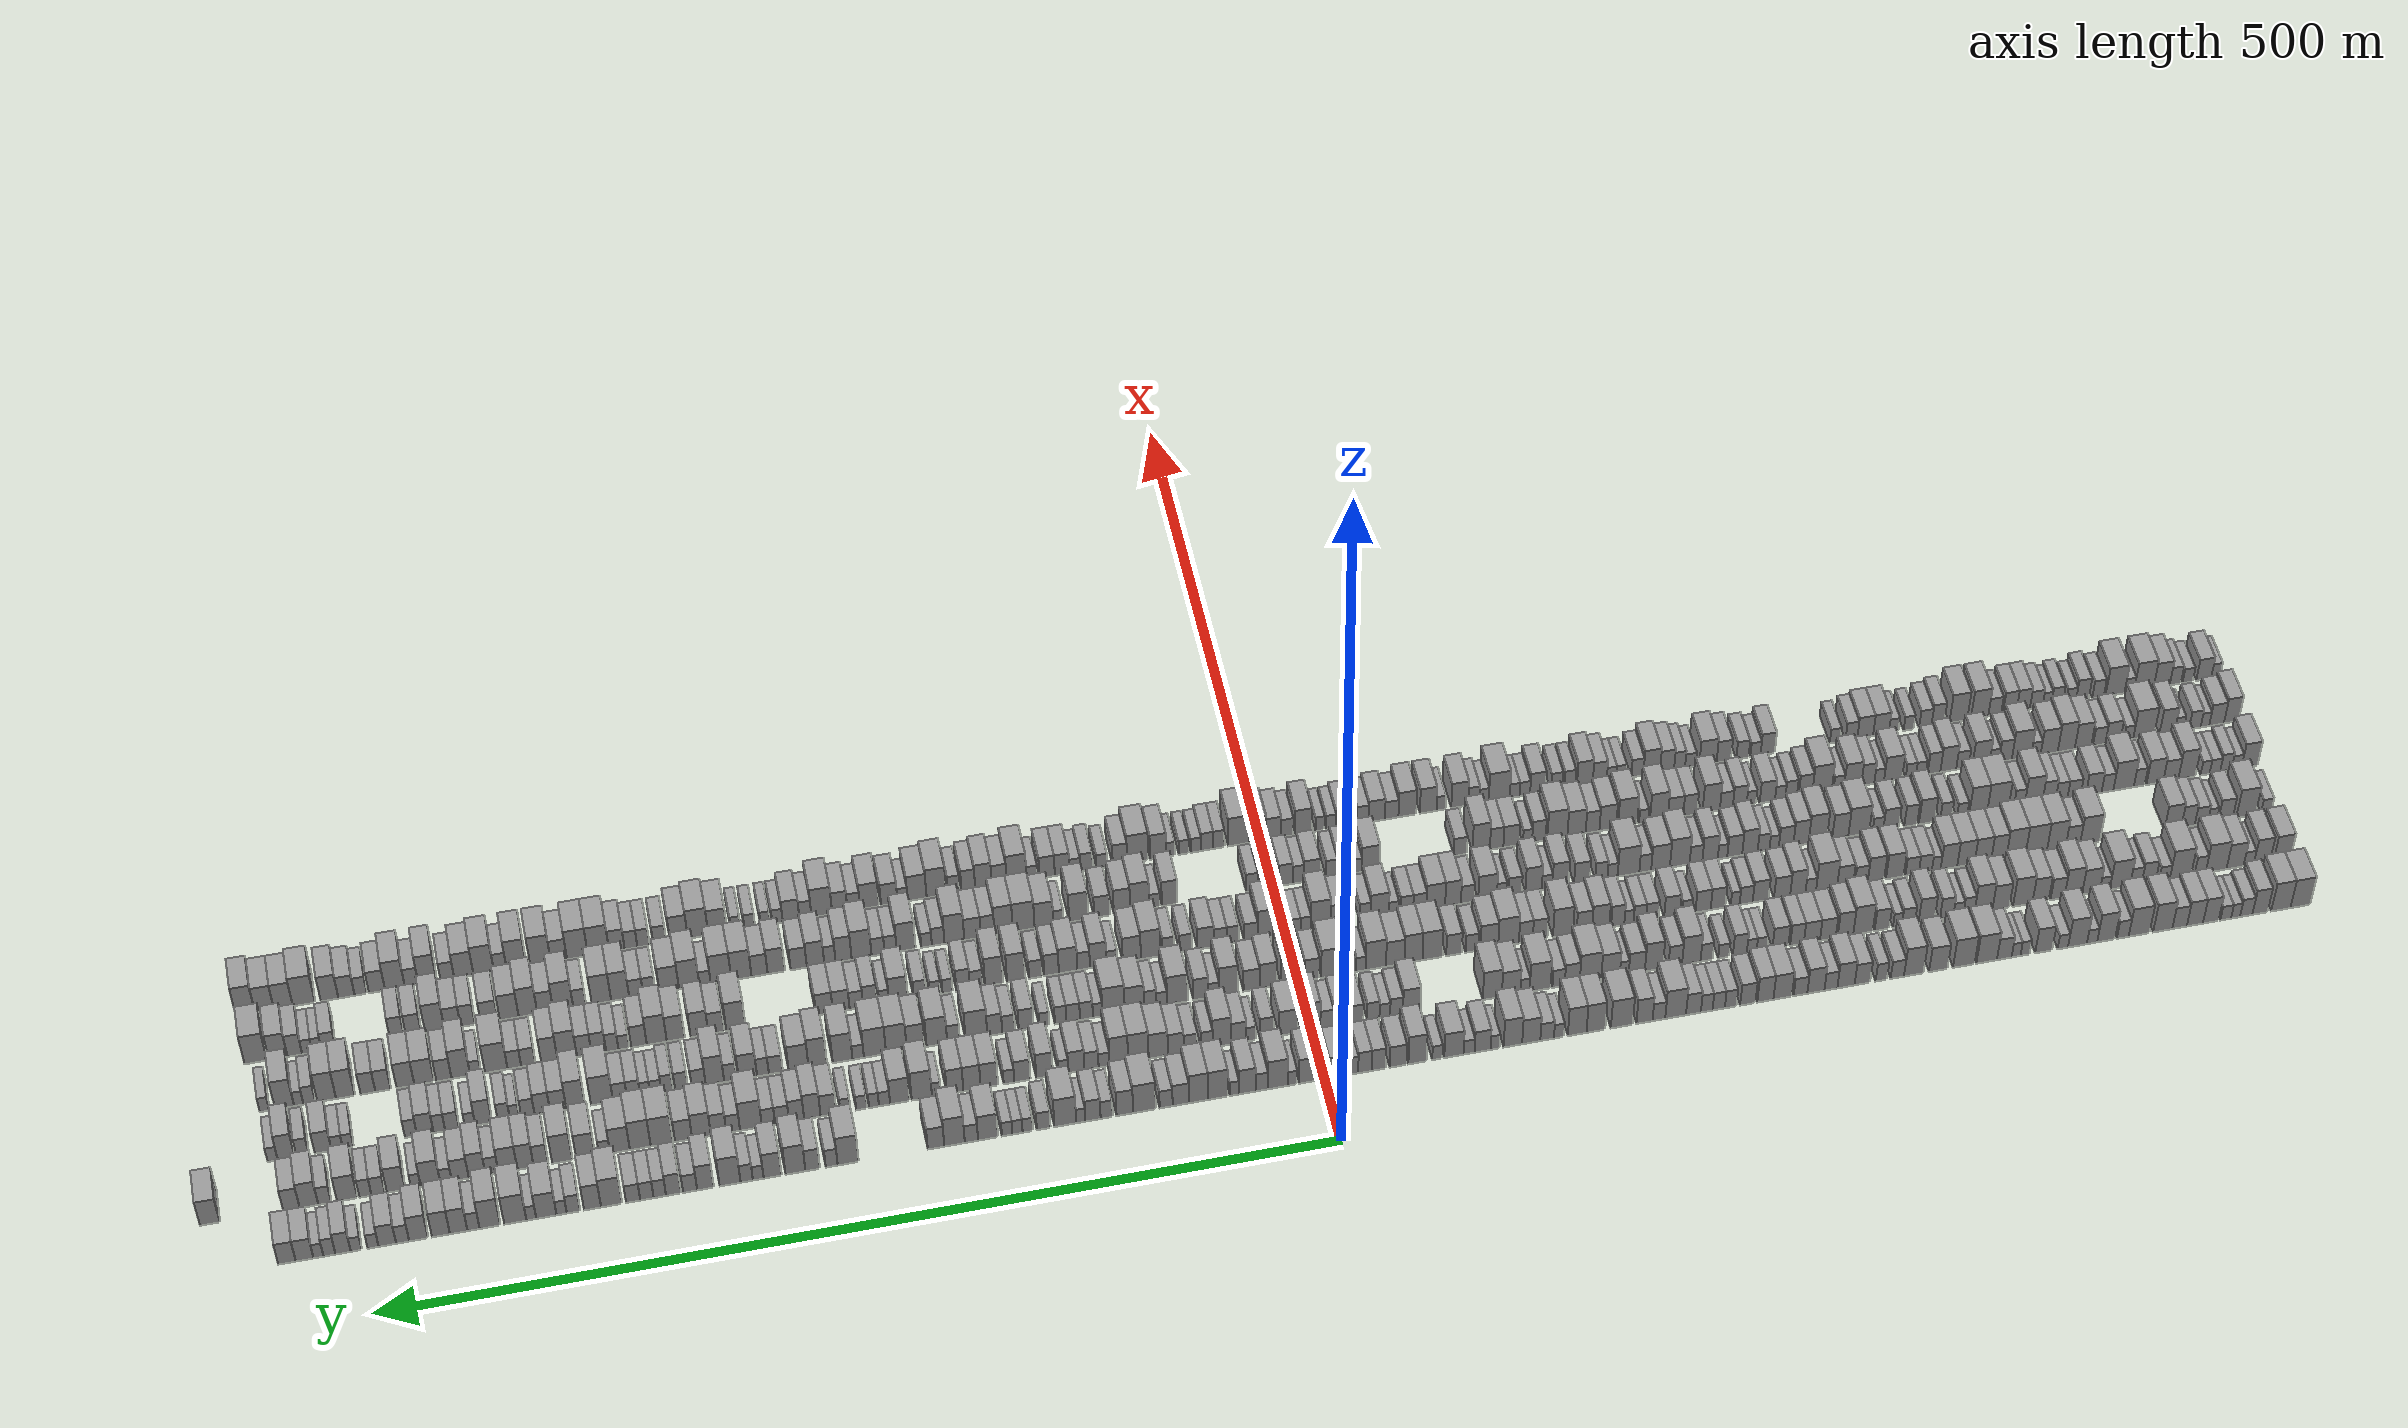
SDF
<sdf version="1.6">
 <world name="default">
  <scene>
   <sky><clouds><speed>12</speed></clouds></sky>
   <ambient>0.4 0.4 0.4 1</ambient>
   <background>0.7 0.7 0.7 1</background>
   <shadows>1</shadows>
  </scene>
  <gravity>0 0 -9.8066</gravity>
  <magnetic_field>6e-06 2.3e-05 -4.2e-05</magnetic_field>
  <physics default="0" name="default_physics" type="ode">
   <ode>
    <solver>
     <type>quick</type>
     <iters>10</iters>
     <sor>1.0</sor>
     <use_dynamic_moi_rescaling>0</use_dynamic_moi_rescaling>
    </solver>
    <constraints>
     <cfm>0</cfm>
     <erp>0.2</erp>
     <contact_max_correcting_vel>100</contact_max_correcting_vel>
     <contact_surface_layer>0.001</contact_surface_layer>
    </constraints>
   </ode>
   <max_step_size>0.004</max_step_size>
   <real_time_factor>1</real_time_factor>
   <real_time_update_rate>250</real_time_update_rate>
  </physics>
  <light name="sun" type="directional">
   <pose>0 0 10 0 0 0</pose>
   <diffuse>0.8 0.8 0.8 1</diffuse>
   <specular>0.2 0.2 0.2 1</specular>
   <attenuation>
    <range>1000</range>
    <constant>0.9</constant>
    <linear>0.01</linear>
    <quadratic>0.001</quadratic>
   </attenuation>
   <direction>-0.5 0.1 -0.9</direction>
  </light>
  <model name="building_1">
   <static>1</static>
   <pose>50.0000 -531.4744 0 0.000000 0.000000 0.000000</pose>
   <link name="link">
    <pose>0 0 12.00 0 0 0</pose>
    <collision name="collision"><geometry><box><size>20.0000 11.0512 24.0000</size></box></geometry></collision>
    <visual name="visual">
     <cast_shadows>0</cast_shadows>
     <geometry><box><size>20.0000 11.0512 24.0000</size></box></geometry>
     <material>
      <script>
       <uri>model://grey_wall/materials/scripts</uri>
       <uri>model://grey_wall/materials/textures</uri>
       <name>vrc/grey_wall</name>
      </script>
     </material>
    </visual>
   </link>
  </model>
  <model name="building_2">
   <static>1</static>
   <pose>50.0000 -520.5361 0 0.000000 0.000000 0.000000</pose>
   <link name="link">
    <pose>0 0 12.00 0 0 0</pose>
    <collision name="collision"><geometry><box><size>20.0000 10.8253 24.0000</size></box></geometry></collision>
    <visual name="visual">
     <cast_shadows>0</cast_shadows>
     <geometry><box><size>20.0000 10.8253 24.0000</size></box></geometry>
     <material>
      <script>
       <uri>model://grey_wall/materials/scripts</uri>
       <uri>model://grey_wall/materials/textures</uri>
       <name>vrc/grey_wall</name>
      </script>
     </material>
    </visual>
   </link>
  </model>
  <model name="building_3">
   <static>1</static>
   <pose>50.0000 -508.8587 0 0.000000 0.000000 0.000000</pose>
   <link name="link">
    <pose>0 0 10.50 0 0 0</pose>
    <collision name="collision"><geometry><box><size>20.0000 8.5297 21.0000</size></box></geometry></collision>
    <visual name="visual">
     <cast_shadows>0</cast_shadows>
     <geometry><box><size>20.0000 8.5297 21.0000</size></box></geometry>
     <material>
      <script>
       <uri>model://grey_wall/materials/scripts</uri>
       <uri>model://grey_wall/materials/textures</uri>
       <name>vrc/grey_wall</name>
      </script>
     </material>
    </visual>
   </link>
  </model>
  <model name="building_4">
   <static>1</static>
   <pose>50.0000 -501.1729 0 0.000000 0.000000 0.000000</pose>
   <link name="link">
    <pose>0 0 7.50 0 0 0</pose>
    <collision name="collision"><geometry><box><size>20.0000 6.8418 15.0000</size></box></geometry></collision>
    <visual name="visual">
     <cast_shadows>0</cast_shadows>
     <geometry><box><size>20.0000 6.8418 15.0000</size></box></geometry>
     <material>
      <script>
       <uri>model://grey_wall/materials/scripts</uri>
       <uri>model://grey_wall/materials/textures</uri>
       <name>vrc/grey_wall</name>
      </script>
     </material>
    </visual>
   </link>
  </model>
  <model name="building_5">
   <static>1</static>
   <pose>50.0000 -495.2459 0 0.000000 0.000000 0.000000</pose>
   <link name="link">
    <pose>0 0 6.00 0 0 0</pose>
    <collision name="collision"><geometry><box><size>20.0000 5.0123 12.0000</size></box></geometry></collision>
    <visual name="visual">
     <cast_shadows>0</cast_shadows>
     <geometry><box><size>20.0000 5.0123 12.0000</size></box></geometry>
     <material>
      <script>
       <uri>model://grey_wall/materials/scripts</uri>
       <uri>model://grey_wall/materials/textures</uri>
       <name>vrc/grey_wall</name>
      </script>
     </material>
    </visual>
   </link>
  </model>
  <model name="building_6">
   <static>1</static>
   <pose>50.0000 -489.7527 0 0.000000 0.000000 0.000000</pose>
   <link name="link">
    <pose>0 0 6.00 0 0 0</pose>
    <collision name="collision"><geometry><box><size>20.0000 5.9742 12.0000</size></box></geometry></collision>
    <visual name="visual">
     <cast_shadows>0</cast_shadows>
     <geometry><box><size>20.0000 5.9742 12.0000</size></box></geometry>
     <material>
      <script>
       <uri>model://grey_wall/materials/scripts</uri>
       <uri>model://grey_wall/materials/textures</uri>
       <name>vrc/grey_wall</name>
      </script>
     </material>
    </visual>
   </link>
  </model>
  <model name="building_7">
   <static>1</static>
   <pose>50.0000 -481.4342 0 0.000000 0.000000 0.000000</pose>
   <link name="link">
    <pose>0 0 10.50 0 0 0</pose>
    <collision name="collision"><geometry><box><size>20.0000 8.6627 21.0000</size></box></geometry></collision>
    <visual name="visual">
     <cast_shadows>0</cast_shadows>
     <geometry><box><size>20.0000 8.6627 21.0000</size></box></geometry>
     <material>
      <script>
       <uri>model://grey_wall/materials/scripts</uri>
       <uri>model://grey_wall/materials/textures</uri>
       <name>vrc/grey_wall</name>
      </script>
     </material>
    </visual>
   </link>
  </model>
  <model name="building_8">
   <static>1</static>
   <pose>50.0000 -472.6129 0 0.000000 0.000000 0.000000</pose>
   <link name="link">
    <pose>0 0 10.50 0 0 0</pose>
    <collision name="collision"><geometry><box><size>20.0000 8.9801 21.0000</size></box></geometry></collision>
    <visual name="visual">
     <cast_shadows>0</cast_shadows>
     <geometry><box><size>20.0000 8.9801 21.0000</size></box></geometry>
     <material>
      <script>
       <uri>model://grey_wall/materials/scripts</uri>
       <uri>model://grey_wall/materials/textures</uri>
       <name>vrc/grey_wall</name>
      </script>
     </material>
    </visual>
   </link>
  </model>
  <model name="building_9">
   <static>1</static>
   <pose>50.0000 -464.0912 0 0.000000 0.000000 0.000000</pose>
   <link name="link">
    <pose>0 0 9.00 0 0 0</pose>
    <collision name="collision"><geometry><box><size>20.0000 8.0633 18.0000</size></box></geometry></collision>
    <visual name="visual">
     <cast_shadows>0</cast_shadows>
     <geometry><box><size>20.0000 8.0633 18.0000</size></box></geometry>
     <material>
      <script>
       <uri>model://grey_wall/materials/scripts</uri>
       <uri>model://grey_wall/materials/textures</uri>
       <name>vrc/grey_wall</name>
      </script>
     </material>
    </visual>
   </link>
  </model>
  <model name="building_10">
   <static>1</static>
   <pose>50.0000 -454.7372 0 0.000000 0.000000 0.000000</pose>
   <link name="link">
    <pose>0 0 12.00 0 0 0</pose>
    <collision name="collision"><geometry><box><size>20.0000 10.6446 24.0000</size></box></geometry></collision>
    <visual name="visual">
     <cast_shadows>0</cast_shadows>
     <geometry><box><size>20.0000 10.6446 24.0000</size></box></geometry>
     <material>
      <script>
       <uri>model://grey_wall/materials/scripts</uri>
       <uri>model://grey_wall/materials/textures</uri>
       <name>vrc/grey_wall</name>
      </script>
     </material>
    </visual>
   </link>
  </model>
  <model name="building_11">
   <static>1</static>
   <pose>50.0000 -441.6367 0 0.000000 0.000000 0.000000</pose>
   <link name="link">
    <pose>0 0 12.00 0 0 0</pose>
    <collision name="collision"><geometry><box><size>20.0000 11.5565 24.0000</size></box></geometry></collision>
    <visual name="visual">
     <cast_shadows>0</cast_shadows>
     <geometry><box><size>20.0000 11.5565 24.0000</size></box></geometry>
     <material>
      <script>
       <uri>model://grey_wall/materials/scripts</uri>
       <uri>model://grey_wall/materials/textures</uri>
       <name>vrc/grey_wall</name>
      </script>
     </material>
    </visual>
   </link>
  </model>
  <model name="building_12">
   <static>1</static>
   <pose>50.0000 -432.5719 0 0.000000 0.000000 0.000000</pose>
   <link name="link">
    <pose>0 0 7.50 0 0 0</pose>
    <collision name="collision"><geometry><box><size>20.0000 6.5730 15.0000</size></box></geometry></collision>
    <visual name="visual">
     <cast_shadows>0</cast_shadows>
     <geometry><box><size>20.0000 6.5730 15.0000</size></box></geometry>
     <material>
      <script>
       <uri>model://grey_wall/materials/scripts</uri>
       <uri>model://grey_wall/materials/textures</uri>
       <name>vrc/grey_wall</name>
      </script>
     </material>
    </visual>
   </link>
  </model>
  <model name="building_13">
   <static>1</static>
   <pose>50.0000 -423.3441 0 0.000000 0.000000 0.000000</pose>
   <link name="link">
    <pose>0 0 12.00 0 0 0</pose>
    <collision name="collision"><geometry><box><size>20.0000 9.8827 24.0000</size></box></geometry></collision>
    <visual name="visual">
     <cast_shadows>0</cast_shadows>
     <geometry><box><size>20.0000 9.8827 24.0000</size></box></geometry>
     <material>
      <script>
       <uri>model://grey_wall/materials/scripts</uri>
       <uri>model://grey_wall/materials/textures</uri>
       <name>vrc/grey_wall</name>
      </script>
     </material>
    </visual>
   </link>
  </model>
  <model name="building_14">
   <static>1</static>
   <pose>50.0000 -415.5265 0 0.000000 0.000000 0.000000</pose>
   <link name="link">
    <pose>0 0 6.00 0 0 0</pose>
    <collision name="collision"><geometry><box><size>20.0000 5.7524 12.0000</size></box></geometry></collision>
    <visual name="visual">
     <cast_shadows>0</cast_shadows>
     <geometry><box><size>20.0000 5.7524 12.0000</size></box></geometry>
     <material>
      <script>
       <uri>model://grey_wall/materials/scripts</uri>
       <uri>model://grey_wall/materials/textures</uri>
       <name>vrc/grey_wall</name>
      </script>
     </material>
    </visual>
   </link>
  </model>
  <model name="building_15">
   <static>1</static>
   <pose>50.0000 -407.4564 0 0.000000 0.000000 0.000000</pose>
   <link name="link">
    <pose>0 0 12.00 0 0 0</pose>
    <collision name="collision"><geometry><box><size>20.0000 10.3880 24.0000</size></box></geometry></collision>
    <visual name="visual">
     <cast_shadows>0</cast_shadows>
     <geometry><box><size>20.0000 10.3880 24.0000</size></box></geometry>
     <material>
      <script>
       <uri>model://grey_wall/materials/scripts</uri>
       <uri>model://grey_wall/materials/textures</uri>
       <name>vrc/grey_wall</name>
      </script>
     </material>
    </visual>
   </link>
  </model>
  <model name="building_16">
   <static>1</static>
   <pose>50.0000 -399.3901 0 0.000000 0.000000 0.000000</pose>
   <link name="link">
    <pose>0 0 6.00 0 0 0</pose>
    <collision name="collision"><geometry><box><size>20.0000 5.7446 12.0000</size></box></geometry></collision>
    <visual name="visual">
     <cast_shadows>0</cast_shadows>
     <geometry><box><size>20.0000 5.7446 12.0000</size></box></geometry>
     <material>
      <script>
       <uri>model://grey_wall/materials/scripts</uri>
       <uri>model://grey_wall/materials/textures</uri>
       <name>vrc/grey_wall</name>
      </script>
     </material>
    </visual>
   </link>
  </model>
  <model name="building_17">
   <static>1</static>
   <pose>50.0000 -388.8253 0 0.000000 0.000000 0.000000</pose>
   <link name="link">
    <pose>0 0 10.50 0 0 0</pose>
    <collision name="collision"><geometry><box><size>20.0000 9.3849 21.0000</size></box></geometry></collision>
    <visual name="visual">
     <cast_shadows>0</cast_shadows>
     <geometry><box><size>20.0000 9.3849 21.0000</size></box></geometry>
     <material>
      <script>
       <uri>model://grey_wall/materials/scripts</uri>
       <uri>model://grey_wall/materials/textures</uri>
       <name>vrc/grey_wall</name>
      </script>
     </material>
    </visual>
   </link>
  </model>
  <model name="building_18">
   <static>1</static>
   <pose>50.0000 -378.6130 0 0.000000 0.000000 0.000000</pose>
   <link name="link">
    <pose>0 0 6.00 0 0 0</pose>
    <collision name="collision"><geometry><box><size>20.0000 5.0396 12.0000</size></box></geometry></collision>
    <visual name="visual">
     <cast_shadows>0</cast_shadows>
     <geometry><box><size>20.0000 5.0396 12.0000</size></box></geometry>
     <material>
      <script>
       <uri>model://grey_wall/materials/scripts</uri>
       <uri>model://grey_wall/materials/textures</uri>
       <name>vrc/grey_wall</name>
      </script>
     </material>
    </visual>
   </link>
  </model>
  <model name="building_19">
   <static>1</static>
   <pose>50.0000 -373.6251 0 0.000000 0.000000 0.000000</pose>
   <link name="link">
    <pose>0 0 6.00 0 0 0</pose>
    <collision name="collision"><geometry><box><size>20.0000 4.9362 12.0000</size></box></geometry></collision>
    <visual name="visual">
     <cast_shadows>0</cast_shadows>
     <geometry><box><size>20.0000 4.9362 12.0000</size></box></geometry>
     <material>
      <script>
       <uri>model://grey_wall/materials/scripts</uri>
       <uri>model://grey_wall/materials/textures</uri>
       <name>vrc/grey_wall</name>
      </script>
     </material>
    </visual>
   </link>
  </model>
  <model name="building_20">
   <static>1</static>
   <pose>50.0000 -367.1172 0 0.000000 0.000000 0.000000</pose>
   <link name="link">
    <pose>0 0 9.00 0 0 0</pose>
    <collision name="collision"><geometry><box><size>20.0000 8.0795 18.0000</size></box></geometry></collision>
    <visual name="visual">
     <cast_shadows>0</cast_shadows>
     <geometry><box><size>20.0000 8.0795 18.0000</size></box></geometry>
     <material>
      <script>
       <uri>model://grey_wall/materials/scripts</uri>
       <uri>model://grey_wall/materials/textures</uri>
       <name>vrc/grey_wall</name>
      </script>
     </material>
    </visual>
   </link>
  </model>
  <model name="building_21">
   <static>1</static>
   <pose>50.0000 -357.4236 0 0.000000 0.000000 0.000000</pose>
   <link name="link">
    <pose>0 0 12.00 0 0 0</pose>
    <collision name="collision"><geometry><box><size>20.0000 11.3078 24.0000</size></box></geometry></collision>
    <visual name="visual">
     <cast_shadows>0</cast_shadows>
     <geometry><box><size>20.0000 11.3078 24.0000</size></box></geometry>
     <material>
      <script>
       <uri>model://grey_wall/materials/scripts</uri>
       <uri>model://grey_wall/materials/textures</uri>
       <name>vrc/grey_wall</name>
      </script>
     </material>
    </visual>
   </link>
  </model>
  <model name="building_22">
   <static>1</static>
   <pose>50.0000 -344.8530 0 0.000000 0.000000 0.000000</pose>
   <link name="link">
    <pose>0 0 12.00 0 0 0</pose>
    <collision name="collision"><geometry><box><size>20.0000 11.8333 24.0000</size></box></geometry></collision>
    <visual name="visual">
     <cast_shadows>0</cast_shadows>
     <geometry><box><size>20.0000 11.8333 24.0000</size></box></geometry>
     <material>
      <script>
       <uri>model://grey_wall/materials/scripts</uri>
       <uri>model://grey_wall/materials/textures</uri>
       <name>vrc/grey_wall</name>
      </script>
     </material>
    </visual>
   </link>
  </model>
  <model name="building_23">
   <static>1</static>
   <pose>50.0000 -330.8366 0 0.000000 0.000000 0.000000</pose>
   <link name="link">
    <pose>0 0 10.50 0 0 0</pose>
    <collision name="collision"><geometry><box><size>20.0000 10.1995 21.0000</size></box></geometry></collision>
    <visual name="visual">
     <cast_shadows>0</cast_shadows>
     <geometry><box><size>20.0000 10.1995 21.0000</size></box></geometry>
     <material>
      <script>
       <uri>model://grey_wall/materials/scripts</uri>
       <uri>model://grey_wall/materials/textures</uri>
       <name>vrc/grey_wall</name>
      </script>
     </material>
    </visual>
   </link>
  </model>
  <model name="building_24">
   <static>1</static>
   <pose>50.0000 -317.3890 0 0.000000 0.000000 0.000000</pose>
   <link name="link">
    <pose>0 0 12.00 0 0 0</pose>
    <collision name="collision"><geometry><box><size>20.0000 10.6957 24.0000</size></box></geometry></collision>
    <visual name="visual">
     <cast_shadows>0</cast_shadows>
     <geometry><box><size>20.0000 10.6957 24.0000</size></box></geometry>
     <material>
      <script>
       <uri>model://grey_wall/materials/scripts</uri>
       <uri>model://grey_wall/materials/textures</uri>
       <name>vrc/grey_wall</name>
      </script>
     </material>
    </visual>
   </link>
  </model>
  <model name="building_25">
   <static>1</static>
   <pose>50.0000 -308.3853 0 0.000000 0.000000 0.000000</pose>
   <link name="link">
    <pose>0 0 7.50 0 0 0</pose>
    <collision name="collision"><geometry><box><size>20.0000 7.3117 15.0000</size></box></geometry></collision>
    <visual name="visual">
     <cast_shadows>0</cast_shadows>
     <geometry><box><size>20.0000 7.3117 15.0000</size></box></geometry>
     <material>
      <script>
       <uri>model://grey_wall/materials/scripts</uri>
       <uri>model://grey_wall/materials/textures</uri>
       <name>vrc/grey_wall</name>
      </script>
     </material>
    </visual>
   </link>
  </model>
  <model name="building_26">
   <static>1</static>
   <pose>50.0000 -299.6123 0 0.000000 0.000000 0.000000</pose>
   <link name="link">
    <pose>0 0 7.50 0 0 0</pose>
    <collision name="collision"><geometry><box><size>20.0000 6.2343 15.0000</size></box></geometry></collision>
    <visual name="visual">
     <cast_shadows>0</cast_shadows>
     <geometry><box><size>20.0000 6.2343 15.0000</size></box></geometry>
     <material>
      <script>
       <uri>model://grey_wall/materials/scripts</uri>
       <uri>model://grey_wall/materials/textures</uri>
       <name>vrc/grey_wall</name>
      </script>
     </material>
    </visual>
   </link>
  </model>
  <model name="building_27">
   <static>1</static>
   <pose>50.0000 -289.2363 0 0.000000 0.000000 0.000000</pose>
   <link name="link">
    <pose>0 0 9.00 0 0 0</pose>
    <collision name="collision"><geometry><box><size>20.0000 8.5178 18.0000</size></box></geometry></collision>
    <visual name="visual">
     <cast_shadows>0</cast_shadows>
     <geometry><box><size>20.0000 8.5178 18.0000</size></box></geometry>
     <material>
      <script>
       <uri>model://grey_wall/materials/scripts</uri>
       <uri>model://grey_wall/materials/textures</uri>
       <name>vrc/grey_wall</name>
      </script>
     </material>
    </visual>
   </link>
  </model>
  <model name="building_28">
   <static>1</static>
   <pose>50.0000 -280.2918 0 0.000000 0.000000 0.000000</pose>
   <link name="link">
    <pose>0 0 10.50 0 0 0</pose>
    <collision name="collision"><geometry><box><size>20.0000 9.3711 21.0000</size></box></geometry></collision>
    <visual name="visual">
     <cast_shadows>0</cast_shadows>
     <geometry><box><size>20.0000 9.3711 21.0000</size></box></geometry>
     <material>
      <script>
       <uri>model://grey_wall/materials/scripts</uri>
       <uri>model://grey_wall/materials/textures</uri>
       <name>vrc/grey_wall</name>
      </script>
     </material>
    </visual>
   </link>
  </model>
  <model name="building_29">
   <static>1</static>
   <pose>50.0000 -272.0547 0 0.000000 0.000000 0.000000</pose>
   <link name="link">
    <pose>0 0 7.50 0 0 0</pose>
    <collision name="collision"><geometry><box><size>20.0000 7.1031 15.0000</size></box></geometry></collision>
    <visual name="visual">
     <cast_shadows>0</cast_shadows>
     <geometry><box><size>20.0000 7.1031 15.0000</size></box></geometry>
     <material>
      <script>
       <uri>model://grey_wall/materials/scripts</uri>
       <uri>model://grey_wall/materials/textures</uri>
       <name>vrc/grey_wall</name>
      </script>
     </material>
    </visual>
   </link>
  </model>
  <model name="building_30">
   <static>1</static>
   <pose>50.0000 -263.8523 0 0.000000 0.000000 0.000000</pose>
   <link name="link">
    <pose>0 0 10.50 0 0 0</pose>
    <collision name="collision"><geometry><box><size>20.0000 9.3017 21.0000</size></box></geometry></collision>
    <visual name="visual">
     <cast_shadows>0</cast_shadows>
     <geometry><box><size>20.0000 9.3017 21.0000</size></box></geometry>
     <material>
      <script>
       <uri>model://grey_wall/materials/scripts</uri>
       <uri>model://grey_wall/materials/textures</uri>
       <name>vrc/grey_wall</name>
      </script>
     </material>
    </visual>
   </link>
  </model>
  <model name="building_31">
   <static>1</static>
   <pose>50.0000 -255.4804 0 0.000000 0.000000 0.000000</pose>
   <link name="link">
    <pose>0 0 7.50 0 0 0</pose>
    <collision name="collision"><geometry><box><size>20.0000 7.4422 15.0000</size></box></geometry></collision>
    <visual name="visual">
     <cast_shadows>0</cast_shadows>
     <geometry><box><size>20.0000 7.4422 15.0000</size></box></geometry>
     <material>
      <script>
       <uri>model://grey_wall/materials/scripts</uri>
       <uri>model://grey_wall/materials/textures</uri>
       <name>vrc/grey_wall</name>
      </script>
     </material>
    </visual>
   </link>
  </model>
  <model name="building_32">
   <static>1</static>
   <pose>50.0000 -245.7599 0 0.000000 0.000000 0.000000</pose>
   <link name="link">
    <pose>0 0 10.50 0 0 0</pose>
    <collision name="collision"><geometry><box><size>20.0000 9.9988 21.0000</size></box></geometry></collision>
    <visual name="visual">
     <cast_shadows>0</cast_shadows>
     <geometry><box><size>20.0000 9.9988 21.0000</size></box></geometry>
     <material>
      <script>
       <uri>model://grey_wall/materials/scripts</uri>
       <uri>model://grey_wall/materials/textures</uri>
       <name>vrc/grey_wall</name>
      </script>
     </material>
    </visual>
   </link>
  </model>
  <model name="building_33">
   <static>1</static>
   <pose>50.0000 -236.3544 0 0.000000 0.000000 0.000000</pose>
   <link name="link">
    <pose>0 0 10.50 0 0 0</pose>
    <collision name="collision"><geometry><box><size>20.0000 8.8123 21.0000</size></box></geometry></collision>
    <visual name="visual">
     <cast_shadows>0</cast_shadows>
     <geometry><box><size>20.0000 8.8123 21.0000</size></box></geometry>
     <material>
      <script>
       <uri>model://grey_wall/materials/scripts</uri>
       <uri>model://grey_wall/materials/textures</uri>
       <name>vrc/grey_wall</name>
      </script>
     </material>
    </visual>
   </link>
  </model>
  <model name="building_34">
   <static>1</static>
   <pose>50.0000 -226.7820 0 0.000000 0.000000 0.000000</pose>
   <link name="link">
    <pose>0 0 9.00 0 0 0</pose>
    <collision name="collision"><geometry><box><size>20.0000 8.3325 18.0000</size></box></geometry></collision>
    <visual name="visual">
     <cast_shadows>0</cast_shadows>
     <geometry><box><size>20.0000 8.3325 18.0000</size></box></geometry>
     <material>
      <script>
       <uri>model://grey_wall/materials/scripts</uri>
       <uri>model://grey_wall/materials/textures</uri>
       <name>vrc/grey_wall</name>
      </script>
     </material>
    </visual>
   </link>
  </model>
  <model name="building_35">
   <static>1</static>
   <pose>50.0000 -217.4866 0 0.000000 0.000000 0.000000</pose>
   <link name="link">
    <pose>0 0 7.50 0 0 0</pose>
    <collision name="collision"><geometry><box><size>20.0000 6.2582 15.0000</size></box></geometry></collision>
    <visual name="visual">
     <cast_shadows>0</cast_shadows>
     <geometry><box><size>20.0000 6.2582 15.0000</size></box></geometry>
     <material>
      <script>
       <uri>model://grey_wall/materials/scripts</uri>
       <uri>model://grey_wall/materials/textures</uri>
       <name>vrc/grey_wall</name>
      </script>
     </material>
    </visual>
   </link>
  </model>
  <model name="building_36">
   <static>1</static>
   <pose>50.0000 -211.0041 0 0.000000 0.000000 0.000000</pose>
   <link name="link">
    <pose>0 0 7.50 0 0 0</pose>
    <collision name="collision"><geometry><box><size>20.0000 6.7070 15.0000</size></box></geometry></collision>
    <visual name="visual">
     <cast_shadows>0</cast_shadows>
     <geometry><box><size>20.0000 6.7070 15.0000</size></box></geometry>
     <material>
      <script>
       <uri>model://grey_wall/materials/scripts</uri>
       <uri>model://grey_wall/materials/textures</uri>
       <name>vrc/grey_wall</name>
      </script>
     </material>
    </visual>
   </link>
  </model>
  <model name="building_37">
   <static>1</static>
   <pose>50.0000 -204.4825 0 0.000000 0.000000 0.000000</pose>
   <link name="link">
    <pose>0 0 7.50 0 0 0</pose>
    <collision name="collision"><geometry><box><size>20.0000 6.3362 15.0000</size></box></geometry></collision>
    <visual name="visual">
     <cast_shadows>0</cast_shadows>
     <geometry><box><size>20.0000 6.3362 15.0000</size></box></geometry>
     <material>
      <script>
       <uri>model://grey_wall/materials/scripts</uri>
       <uri>model://grey_wall/materials/textures</uri>
       <name>vrc/grey_wall</name>
      </script>
     </material>
    </visual>
   </link>
  </model>
  <model name="building_38">
   <static>1</static>
   <pose>50.0000 -197.2832 0 0.000000 0.000000 0.000000</pose>
   <link name="link">
    <pose>0 0 9.00 0 0 0</pose>
    <collision name="collision"><geometry><box><size>20.0000 8.0623 18.0000</size></box></geometry></collision>
    <visual name="visual">
     <cast_shadows>0</cast_shadows>
     <geometry><box><size>20.0000 8.0623 18.0000</size></box></geometry>
     <material>
      <script>
       <uri>model://grey_wall/materials/scripts</uri>
       <uri>model://grey_wall/materials/textures</uri>
       <name>vrc/grey_wall</name>
      </script>
     </material>
    </visual>
   </link>
  </model>
  <model name="building_39">
   <static>1</static>
   <pose>50.0000 -187.6248 0 0.000000 0.000000 0.000000</pose>
   <link name="link">
    <pose>0 0 12.00 0 0 0</pose>
    <collision name="collision"><geometry><box><size>20.0000 11.2545 24.0000</size></box></geometry></collision>
    <visual name="visual">
     <cast_shadows>0</cast_shadows>
     <geometry><box><size>20.0000 11.2545 24.0000</size></box></geometry>
     <material>
      <script>
       <uri>model://grey_wall/materials/scripts</uri>
       <uri>model://grey_wall/materials/textures</uri>
       <name>vrc/grey_wall</name>
      </script>
     </material>
    </visual>
   </link>
  </model>
  <model name="building_40">
   <static>1</static>
   <pose>50.0000 -178.5702 0 0.000000 0.000000 0.000000</pose>
   <link name="link">
    <pose>0 0 7.50 0 0 0</pose>
    <collision name="collision"><geometry><box><size>20.0000 6.8547 15.0000</size></box></geometry></collision>
    <visual name="visual">
     <cast_shadows>0</cast_shadows>
     <geometry><box><size>20.0000 6.8547 15.0000</size></box></geometry>
     <material>
      <script>
       <uri>model://grey_wall/materials/scripts</uri>
       <uri>model://grey_wall/materials/textures</uri>
       <name>vrc/grey_wall</name>
      </script>
     </material>
    </visual>
   </link>
  </model>
  <model name="building_41">
   <static>1</static>
   <pose>50.0000 -170.7903 0 0.000000 0.000000 0.000000</pose>
   <link name="link">
    <pose>0 0 10.50 0 0 0</pose>
    <collision name="collision"><geometry><box><size>20.0000 8.7051 21.0000</size></box></geometry></collision>
    <visual name="visual">
     <cast_shadows>0</cast_shadows>
     <geometry><box><size>20.0000 8.7051 21.0000</size></box></geometry>
     <material>
      <script>
       <uri>model://grey_wall/materials/scripts</uri>
       <uri>model://grey_wall/materials/textures</uri>
       <name>vrc/grey_wall</name>
      </script>
     </material>
    </visual>
   </link>
  </model>
  <model name="building_42">
   <static>1</static>
   <pose>50.0000 -158.5250 0 0.000000 0.000000 0.000000</pose>
   <link name="link">
    <pose>0 0 12.00 0 0 0</pose>
    <collision name="collision"><geometry><box><size>20.0000 11.8255 24.0000</size></box></geometry></collision>
    <visual name="visual">
     <cast_shadows>0</cast_shadows>
     <geometry><box><size>20.0000 11.8255 24.0000</size></box></geometry>
     <material>
      <script>
       <uri>model://grey_wall/materials/scripts</uri>
       <uri>model://grey_wall/materials/textures</uri>
       <name>vrc/grey_wall</name>
      </script>
     </material>
    </visual>
   </link>
  </model>
  <model name="building_43">
   <static>1</static>
   <pose>50.0000 -144.5448 0 0.000000 0.000000 0.000000</pose>
   <link name="link">
    <pose>0 0 12.00 0 0 0</pose>
    <collision name="collision"><geometry><box><size>20.0000 10.1348 24.0000</size></box></geometry></collision>
    <visual name="visual">
     <cast_shadows>0</cast_shadows>
     <geometry><box><size>20.0000 10.1348 24.0000</size></box></geometry>
     <material>
      <script>
       <uri>model://grey_wall/materials/scripts</uri>
       <uri>model://grey_wall/materials/textures</uri>
       <name>vrc/grey_wall</name>
      </script>
     </material>
    </visual>
   </link>
  </model>
  <model name="building_44">
   <static>1</static>
   <pose>50.0000 -134.4413 0 0.000000 0.000000 0.000000</pose>
   <link name="link">
    <pose>0 0 12.00 0 0 0</pose>
    <collision name="collision"><geometry><box><size>20.0000 10.0723 24.0000</size></box></geometry></collision>
    <visual name="visual">
     <cast_shadows>0</cast_shadows>
     <geometry><box><size>20.0000 10.0723 24.0000</size></box></geometry>
     <material>
      <script>
       <uri>model://grey_wall/materials/scripts</uri>
       <uri>model://grey_wall/materials/textures</uri>
       <name>vrc/grey_wall</name>
      </script>
     </material>
    </visual>
   </link>
  </model>
  <model name="building_45">
   <static>1</static>
   <pose>50.0000 -124.6807 0 0.000000 0.000000 0.000000</pose>
   <link name="link">
    <pose>0 0 6.00 0 0 0</pose>
    <collision name="collision"><geometry><box><size>20.0000 5.4487 12.0000</size></box></geometry></collision>
    <visual name="visual">
     <cast_shadows>0</cast_shadows>
     <geometry><box><size>20.0000 5.4487 12.0000</size></box></geometry>
     <material>
      <script>
       <uri>model://grey_wall/materials/scripts</uri>
       <uri>model://grey_wall/materials/textures</uri>
       <name>vrc/grey_wall</name>
      </script>
     </material>
    </visual>
   </link>
  </model>
  <model name="building_46">
   <static>1</static>
   <pose>50.0000 -118.2756 0 0.000000 0.000000 0.000000</pose>
   <link name="link">
    <pose>0 0 7.50 0 0 0</pose>
    <collision name="collision"><geometry><box><size>20.0000 7.3616 15.0000</size></box></geometry></collision>
    <visual name="visual">
     <cast_shadows>0</cast_shadows>
     <geometry><box><size>20.0000 7.3616 15.0000</size></box></geometry>
     <material>
      <script>
       <uri>model://grey_wall/materials/scripts</uri>
       <uri>model://grey_wall/materials/textures</uri>
       <name>vrc/grey_wall</name>
      </script>
     </material>
    </visual>
   </link>
  </model>
  <model name="building_47">
   <static>1</static>
   <pose>50.0000 -109.7282 0 0.000000 0.000000 0.000000</pose>
   <link name="link">
    <pose>0 0 10.50 0 0 0</pose>
    <collision name="collision"><geometry><box><size>20.0000 9.7334 21.0000</size></box></geometry></collision>
    <visual name="visual">
     <cast_shadows>0</cast_shadows>
     <geometry><box><size>20.0000 9.7334 21.0000</size></box></geometry>
     <material>
      <script>
       <uri>model://grey_wall/materials/scripts</uri>
       <uri>model://grey_wall/materials/textures</uri>
       <name>vrc/grey_wall</name>
      </script>
     </material>
    </visual>
   </link>
  </model>
  <model name="building_48">
   <static>1</static>
   <pose>50.0000 -99.8659 0 0.000000 0.000000 0.000000</pose>
   <link name="link">
    <pose>0 0 12.00 0 0 0</pose>
    <collision name="collision"><geometry><box><size>20.0000 9.9911 24.0000</size></box></geometry></collision>
    <visual name="visual">
     <cast_shadows>0</cast_shadows>
     <geometry><box><size>20.0000 9.9911 24.0000</size></box></geometry>
     <material>
      <script>
       <uri>model://grey_wall/materials/scripts</uri>
       <uri>model://grey_wall/materials/textures</uri>
       <name>vrc/grey_wall</name>
      </script>
     </material>
    </visual>
   </link>
  </model>
  <model name="building_49">
   <static>1</static>
   <pose>50.0000 -90.3683 0 0.000000 0.000000 0.000000</pose>
   <link name="link">
    <pose>0 0 6.00 0 0 0</pose>
    <collision name="collision"><geometry><box><size>20.0000 5.0040 12.0000</size></box></geometry></collision>
    <visual name="visual">
     <cast_shadows>0</cast_shadows>
     <geometry><box><size>20.0000 5.0040 12.0000</size></box></geometry>
     <material>
      <script>
       <uri>model://grey_wall/materials/scripts</uri>
       <uri>model://grey_wall/materials/textures</uri>
       <name>vrc/grey_wall</name>
      </script>
     </material>
    </visual>
   </link>
  </model>
  <model name="building_50">
   <static>1</static>
   <pose>50.0000 -83.6136 0 0.000000 0.000000 0.000000</pose>
   <link name="link">
    <pose>0 0 9.00 0 0 0</pose>
    <collision name="collision"><geometry><box><size>20.0000 8.5054 18.0000</size></box></geometry></collision>
    <visual name="visual">
     <cast_shadows>0</cast_shadows>
     <geometry><box><size>20.0000 8.5054 18.0000</size></box></geometry>
     <material>
      <script>
       <uri>model://grey_wall/materials/scripts</uri>
       <uri>model://grey_wall/materials/textures</uri>
       <name>vrc/grey_wall</name>
      </script>
     </material>
    </visual>
   </link>
  </model>
  <model name="building_51">
   <static>1</static>
   <pose>50.0000 -76.3933 0 0.000000 0.000000 0.000000</pose>
   <link name="link">
    <pose>0 0 6.00 0 0 0</pose>
    <collision name="collision"><geometry><box><size>20.0000 5.9352 12.0000</size></box></geometry></collision>
    <visual name="visual">
     <cast_shadows>0</cast_shadows>
     <geometry><box><size>20.0000 5.9352 12.0000</size></box></geometry>
     <material>
      <script>
       <uri>model://grey_wall/materials/scripts</uri>
       <uri>model://grey_wall/materials/textures</uri>
       <name>vrc/grey_wall</name>
      </script>
     </material>
    </visual>
   </link>
  </model>
  <model name="building_52">
   <static>1</static>
   <pose>50.0000 -68.2543 0 0.000000 0.000000 0.000000</pose>
   <link name="link">
    <pose>0 0 10.50 0 0 0</pose>
    <collision name="collision"><geometry><box><size>20.0000 10.3429 21.0000</size></box></geometry></collision>
    <visual name="visual">
     <cast_shadows>0</cast_shadows>
     <geometry><box><size>20.0000 10.3429 21.0000</size></box></geometry>
     <material>
      <script>
       <uri>model://grey_wall/materials/scripts</uri>
       <uri>model://grey_wall/materials/textures</uri>
       <name>vrc/grey_wall</name>
      </script>
     </material>
    </visual>
   </link>
  </model>
  <model name="building_53">
   <static>1</static>
   <pose>50.0000 -59.3650 0 0.000000 0.000000 0.000000</pose>
   <link name="link">
    <pose>0 0 6.00 0 0 0</pose>
    <collision name="collision"><geometry><box><size>20.0000 5.4358 12.0000</size></box></geometry></collision>
    <visual name="visual">
     <cast_shadows>0</cast_shadows>
     <geometry><box><size>20.0000 5.4358 12.0000</size></box></geometry>
     <material>
      <script>
       <uri>model://grey_wall/materials/scripts</uri>
       <uri>model://grey_wall/materials/textures</uri>
       <name>vrc/grey_wall</name>
      </script>
     </material>
    </visual>
   </link>
  </model>
  <model name="building_54">
   <static>1</static>
   <pose>50.0000 -48.7629 0 0.000000 0.000000 0.000000</pose>
   <link name="link">
    <pose>0 0 12.00 0 0 0</pose>
    <collision name="collision"><geometry><box><size>20.0000 9.7684 24.0000</size></box></geometry></collision>
    <visual name="visual">
     <cast_shadows>0</cast_shadows>
     <geometry><box><size>20.0000 9.7684 24.0000</size></box></geometry>
     <material>
      <script>
       <uri>model://grey_wall/materials/scripts</uri>
       <uri>model://grey_wall/materials/textures</uri>
       <name>vrc/grey_wall</name>
      </script>
     </material>
    </visual>
   </link>
  </model>
  <model name="building_55">
   <static>1</static>
   <pose>50.0000 -38.3831 0 0.000000 0.000000 0.000000</pose>
   <link name="link">
    <pose>0 0 9.00 0 0 0</pose>
    <collision name="collision"><geometry><box><size>20.0000 8.9911 18.0000</size></box></geometry></collision>
    <visual name="visual">
     <cast_shadows>0</cast_shadows>
     <geometry><box><size>20.0000 8.9911 18.0000</size></box></geometry>
     <material>
      <script>
       <uri>model://grey_wall/materials/scripts</uri>
       <uri>model://grey_wall/materials/textures</uri>
       <name>vrc/grey_wall</name>
      </script>
     </material>
    </visual>
   </link>
  </model>
  <model name="building_56">
   <static>1</static>
   <pose>50.0000 -28.1295 0 0.000000 0.000000 0.000000</pose>
   <link name="link">
    <pose>0 0 9.00 0 0 0</pose>
    <collision name="collision"><geometry><box><size>20.0000 7.5162 18.0000</size></box></geometry></collision>
    <visual name="visual">
     <cast_shadows>0</cast_shadows>
     <geometry><box><size>20.0000 7.5162 18.0000</size></box></geometry>
     <material>
      <script>
       <uri>model://grey_wall/materials/scripts</uri>
       <uri>model://grey_wall/materials/textures</uri>
       <name>vrc/grey_wall</name>
      </script>
     </material>
    </visual>
   </link>
  </model>
  <model name="building_57">
   <static>1</static>
   <pose>50.0000 -20.7527 0 0.000000 0.000000 0.000000</pose>
   <link name="link">
    <pose>0 0 9.00 0 0 0</pose>
    <collision name="collision"><geometry><box><size>20.0000 7.2374 18.0000</size></box></geometry></collision>
    <visual name="visual">
     <cast_shadows>0</cast_shadows>
     <geometry><box><size>20.0000 7.2374 18.0000</size></box></geometry>
     <material>
      <script>
       <uri>model://grey_wall/materials/scripts</uri>
       <uri>model://grey_wall/materials/textures</uri>
       <name>vrc/grey_wall</name>
      </script>
     </material>
    </visual>
   </link>
  </model>
  <model name="building_58">
   <static>1</static>
   <pose>50.0000 -13.5621 0 0.000000 0.000000 0.000000</pose>
   <link name="link">
    <pose>0 0 7.50 0 0 0</pose>
    <collision name="collision"><geometry><box><size>20.0000 7.1438 15.0000</size></box></geometry></collision>
    <visual name="visual">
     <cast_shadows>0</cast_shadows>
     <geometry><box><size>20.0000 7.1438 15.0000</size></box></geometry>
     <material>
      <script>
       <uri>model://grey_wall/materials/scripts</uri>
       <uri>model://grey_wall/materials/textures</uri>
       <name>vrc/grey_wall</name>
      </script>
     </material>
    </visual>
   </link>
  </model>
  <model name="building_59">
   <static>1</static>
   <pose>50.0000 -5.3172 0 0.000000 0.000000 0.000000</pose>
   <link name="link">
    <pose>0 0 9.00 0 0 0</pose>
    <collision name="collision"><geometry><box><size>20.0000 7.3459 18.0000</size></box></geometry></collision>
    <visual name="visual">
     <cast_shadows>0</cast_shadows>
     <geometry><box><size>20.0000 7.3459 18.0000</size></box></geometry>
     <material>
      <script>
       <uri>model://grey_wall/materials/scripts</uri>
       <uri>model://grey_wall/materials/textures</uri>
       <name>vrc/grey_wall</name>
      </script>
     </material>
    </visual>
   </link>
  </model>
  <model name="building_60">
   <static>1</static>
   <pose>50.0000 1.3358 0 0.000000 0.000000 0.000000</pose>
   <link name="link">
    <pose>0 0 6.00 0 0 0</pose>
    <collision name="collision"><geometry><box><size>20.0000 5.9601 12.0000</size></box></geometry></collision>
    <visual name="visual">
     <cast_shadows>0</cast_shadows>
     <geometry><box><size>20.0000 5.9601 12.0000</size></box></geometry>
     <material>
      <script>
       <uri>model://grey_wall/materials/scripts</uri>
       <uri>model://grey_wall/materials/textures</uri>
       <name>vrc/grey_wall</name>
      </script>
     </material>
    </visual>
   </link>
  </model>
  <model name="building_61">
   <static>1</static>
   <pose>50.0000 9.3004 0 0.000000 0.000000 0.000000</pose>
   <link name="link">
    <pose>0 0 10.50 0 0 0</pose>
    <collision name="collision"><geometry><box><size>20.0000 9.9691 21.0000</size></box></geometry></collision>
    <visual name="visual">
     <cast_shadows>0</cast_shadows>
     <geometry><box><size>20.0000 9.9691 21.0000</size></box></geometry>
     <material>
      <script>
       <uri>model://grey_wall/materials/scripts</uri>
       <uri>model://grey_wall/materials/textures</uri>
       <name>vrc/grey_wall</name>
      </script>
     </material>
    </visual>
   </link>
  </model>
  <model name="building_62">
   <static>1</static>
   <pose>50.0000 17.7154 0 0.000000 0.000000 0.000000</pose>
   <link name="link">
    <pose>0 0 6.00 0 0 0</pose>
    <collision name="collision"><geometry><box><size>20.0000 4.8610 12.0000</size></box></geometry></collision>
    <visual name="visual">
     <cast_shadows>0</cast_shadows>
     <geometry><box><size>20.0000 4.8610 12.0000</size></box></geometry>
     <material>
      <script>
       <uri>model://grey_wall/materials/scripts</uri>
       <uri>model://grey_wall/materials/textures</uri>
       <name>vrc/grey_wall</name>
      </script>
     </material>
    </visual>
   </link>
  </model>
  <model name="building_63">
   <static>1</static>
   <pose>50.0000 25.4803 0 0.000000 0.000000 0.000000</pose>
   <link name="link">
    <pose>0 0 12.00 0 0 0</pose>
    <collision name="collision"><geometry><box><size>20.0000 10.6687 24.0000</size></box></geometry></collision>
    <visual name="visual">
     <cast_shadows>0</cast_shadows>
     <geometry><box><size>20.0000 10.6687 24.0000</size></box></geometry>
     <material>
      <script>
       <uri>model://grey_wall/materials/scripts</uri>
       <uri>model://grey_wall/materials/textures</uri>
       <name>vrc/grey_wall</name>
      </script>
     </material>
    </visual>
   </link>
  </model>
  <model name="building_64">
   <static>1</static>
   <pose>50.0000 34.0839 0 0.000000 0.000000 0.000000</pose>
   <link name="link">
    <pose>0 0 7.50 0 0 0</pose>
    <collision name="collision"><geometry><box><size>20.0000 6.5386 15.0000</size></box></geometry></collision>
    <visual name="visual">
     <cast_shadows>0</cast_shadows>
     <geometry><box><size>20.0000 6.5386 15.0000</size></box></geometry>
     <material>
      <script>
       <uri>model://grey_wall/materials/scripts</uri>
       <uri>model://grey_wall/materials/textures</uri>
       <name>vrc/grey_wall</name>
      </script>
     </material>
    </visual>
   </link>
  </model>
  <model name="building_65">
   <static>1</static>
   <pose>50.0000 41.7796 0 0.000000 0.000000 0.000000</pose>
   <link name="link">
    <pose>0 0 10.50 0 0 0</pose>
    <collision name="collision"><geometry><box><size>20.0000 8.8528 21.0000</size></box></geometry></collision>
    <visual name="visual">
     <cast_shadows>0</cast_shadows>
     <geometry><box><size>20.0000 8.8528 21.0000</size></box></geometry>
     <material>
      <script>
       <uri>model://grey_wall/materials/scripts</uri>
       <uri>model://grey_wall/materials/textures</uri>
       <name>vrc/grey_wall</name>
      </script>
     </material>
    </visual>
   </link>
  </model>
  <model name="building_66">
   <static>1</static>
   <pose>50.0000 48.6634 0 0.000000 0.000000 0.000000</pose>
   <link name="link">
    <pose>0 0 6.00 0 0 0</pose>
    <collision name="collision"><geometry><box><size>20.0000 4.9147 12.0000</size></box></geometry></collision>
    <visual name="visual">
     <cast_shadows>0</cast_shadows>
     <geometry><box><size>20.0000 4.9147 12.0000</size></box></geometry>
     <material>
      <script>
       <uri>model://grey_wall/materials/scripts</uri>
       <uri>model://grey_wall/materials/textures</uri>
       <name>vrc/grey_wall</name>
      </script>
     </material>
    </visual>
   </link>
  </model>
  <model name="building_67">
   <static>1</static>
   <pose>50.0000 57.2903 0 0.000000 0.000000 0.000000</pose>
   <link name="link">
    <pose>0 0 12.00 0 0 0</pose>
    <collision name="collision"><geometry><box><size>20.0000 10.3391 24.0000</size></box></geometry></collision>
    <visual name="visual">
     <cast_shadows>0</cast_shadows>
     <geometry><box><size>20.0000 10.3391 24.0000</size></box></geometry>
     <material>
      <script>
       <uri>model://grey_wall/materials/scripts</uri>
       <uri>model://grey_wall/materials/textures</uri>
       <name>vrc/grey_wall</name>
      </script>
     </material>
    </visual>
   </link>
  </model>
  <model name="building_68">
   <static>1</static>
   <pose>50.0000 67.5436 0 0.000000 0.000000 0.000000</pose>
   <link name="link">
    <pose>0 0 12.00 0 0 0</pose>
    <collision name="collision"><geometry><box><size>20.0000 10.1675 24.0000</size></box></geometry></collision>
    <visual name="visual">
     <cast_shadows>0</cast_shadows>
     <geometry><box><size>20.0000 10.1675 24.0000</size></box></geometry>
     <material>
      <script>
       <uri>model://grey_wall/materials/scripts</uri>
       <uri>model://grey_wall/materials/textures</uri>
       <name>vrc/grey_wall</name>
      </script>
     </material>
    </visual>
   </link>
  </model>
  <model name="building_69">
   <static>1</static>
   <pose>50.0000 76.9611 0 0.000000 0.000000 0.000000</pose>
   <link name="link">
    <pose>0 0 9.00 0 0 0</pose>
    <collision name="collision"><geometry><box><size>20.0000 8.6673 18.0000</size></box></geometry></collision>
    <visual name="visual">
     <cast_shadows>0</cast_shadows>
     <geometry><box><size>20.0000 8.6673 18.0000</size></box></geometry>
     <material>
      <script>
       <uri>model://grey_wall/materials/scripts</uri>
       <uri>model://grey_wall/materials/textures</uri>
       <name>vrc/grey_wall</name>
      </script>
     </material>
    </visual>
   </link>
  </model>
  <model name="building_70">
   <static>1</static>
   <pose>50.0000 84.7303 0 0.000000 0.000000 0.000000</pose>
   <link name="link">
    <pose>0 0 7.50 0 0 0</pose>
    <collision name="collision"><geometry><box><size>20.0000 6.8712 15.0000</size></box></geometry></collision>
    <visual name="visual">
     <cast_shadows>0</cast_shadows>
     <geometry><box><size>20.0000 6.8712 15.0000</size></box></geometry>
     <material>
      <script>
       <uri>model://grey_wall/materials/scripts</uri>
       <uri>model://grey_wall/materials/textures</uri>
       <name>vrc/grey_wall</name>
      </script>
     </material>
    </visual>
   </link>
  </model>
  <model name="building_71">
   <static>1</static>
   <pose>50.0000 96.1594 0 0.000000 0.000000 0.000000</pose>
   <link name="link">
    <pose>0 0 12.00 0 0 0</pose>
    <collision name="collision"><geometry><box><size>20.0000 11.9871 24.0000</size></box></geometry></collision>
    <visual name="visual">
     <cast_shadows>0</cast_shadows>
     <geometry><box><size>20.0000 11.9871 24.0000</size></box></geometry>
     <material>
      <script>
       <uri>model://grey_wall/materials/scripts</uri>
       <uri>model://grey_wall/materials/textures</uri>
       <name>vrc/grey_wall</name>
      </script>
     </material>
    </visual>
   </link>
  </model>
  <model name="building_72">
   <static>1</static>
   <pose>50.0000 106.5180 0 0.000000 0.000000 0.000000</pose>
   <link name="link">
    <pose>0 0 10.50 0 0 0</pose>
    <collision name="collision"><geometry><box><size>20.0000 8.7301 21.0000</size></box></geometry></collision>
    <visual name="visual">
     <cast_shadows>0</cast_shadows>
     <geometry><box><size>20.0000 8.7301 21.0000</size></box></geometry>
     <material>
      <script>
       <uri>model://grey_wall/materials/scripts</uri>
       <uri>model://grey_wall/materials/textures</uri>
       <name>vrc/grey_wall</name>
      </script>
     </material>
    </visual>
   </link>
  </model>
  <model name="building_73">
   <static>1</static>
   <pose>50.0000 116.0705 0 0.000000 0.000000 0.000000</pose>
   <link name="link">
    <pose>0 0 7.50 0 0 0</pose>
    <collision name="collision"><geometry><box><size>20.0000 6.3748 15.0000</size></box></geometry></collision>
    <visual name="visual">
     <cast_shadows>0</cast_shadows>
     <geometry><box><size>20.0000 6.3748 15.0000</size></box></geometry>
     <material>
      <script>
       <uri>model://grey_wall/materials/scripts</uri>
       <uri>model://grey_wall/materials/textures</uri>
       <name>vrc/grey_wall</name>
      </script>
     </material>
    </visual>
   </link>
  </model>
  <model name="building_74">
   <static>1</static>
   <pose>50.0000 123.2562 0 0.000000 0.000000 0.000000</pose>
   <link name="link">
    <pose>0 0 9.00 0 0 0</pose>
    <collision name="collision"><geometry><box><size>20.0000 7.9965 18.0000</size></box></geometry></collision>
    <visual name="visual">
     <cast_shadows>0</cast_shadows>
     <geometry><box><size>20.0000 7.9965 18.0000</size></box></geometry>
     <material>
      <script>
       <uri>model://grey_wall/materials/scripts</uri>
       <uri>model://grey_wall/materials/textures</uri>
       <name>vrc/grey_wall</name>
      </script>
     </material>
    </visual>
   </link>
  </model>
  <model name="building_75">
   <static>1</static>
   <pose>50.0000 129.6763 0 0.000000 0.000000 0.000000</pose>
   <link name="link">
    <pose>0 0 6.00 0 0 0</pose>
    <collision name="collision"><geometry><box><size>20.0000 4.8437 12.0000</size></box></geometry></collision>
    <visual name="visual">
     <cast_shadows>0</cast_shadows>
     <geometry><box><size>20.0000 4.8437 12.0000</size></box></geometry>
     <material>
      <script>
       <uri>model://grey_wall/materials/scripts</uri>
       <uri>model://grey_wall/materials/textures</uri>
       <name>vrc/grey_wall</name>
      </script>
     </material>
    </visual>
   </link>
  </model>
  <model name="building_76">
   <static>1</static>
   <pose>50.0000 137.8313 0 0.000000 0.000000 0.000000</pose>
   <link name="link">
    <pose>0 0 12.00 0 0 0</pose>
    <collision name="collision"><geometry><box><size>20.0000 11.4663 24.0000</size></box></geometry></collision>
    <visual name="visual">
     <cast_shadows>0</cast_shadows>
     <geometry><box><size>20.0000 11.4663 24.0000</size></box></geometry>
     <material>
      <script>
       <uri>model://grey_wall/materials/scripts</uri>
       <uri>model://grey_wall/materials/textures</uri>
       <name>vrc/grey_wall</name>
      </script>
     </material>
    </visual>
   </link>
  </model>
  <model name="building_77">
   <static>1</static>
   <pose>50.0000 149.1708 0 0.000000 0.000000 0.000000</pose>
   <link name="link">
    <pose>0 0 7.50 0 0 0</pose>
    <collision name="collision"><geometry><box><size>20.0000 7.2126 15.0000</size></box></geometry></collision>
    <visual name="visual">
     <cast_shadows>0</cast_shadows>
     <geometry><box><size>20.0000 7.2126 15.0000</size></box></geometry>
     <material>
      <script>
       <uri>model://grey_wall/materials/scripts</uri>
       <uri>model://grey_wall/materials/textures</uri>
       <name>vrc/grey_wall</name>
      </script>
     </material>
    </visual>
   </link>
  </model>
  <model name="building_78">
   <static>1</static>
   <pose>50.0000 157.5082 0 0.000000 0.000000 0.000000</pose>
   <link name="link">
    <pose>0 0 6.00 0 0 0</pose>
    <collision name="collision"><geometry><box><size>20.0000 5.4622 12.0000</size></box></geometry></collision>
    <visual name="visual">
     <cast_shadows>0</cast_shadows>
     <geometry><box><size>20.0000 5.4622 12.0000</size></box></geometry>
     <material>
      <script>
       <uri>model://grey_wall/materials/scripts</uri>
       <uri>model://grey_wall/materials/textures</uri>
       <name>vrc/grey_wall</name>
      </script>
     </material>
    </visual>
   </link>
  </model>
  <model name="building_79">
   <static>1</static>
   <pose>50.0000 162.9114 0 0.000000 0.000000 0.000000</pose>
   <link name="link">
    <pose>0 0 6.00 0 0 0</pose>
    <collision name="collision"><geometry><box><size>20.0000 5.3441 12.0000</size></box></geometry></collision>
    <visual name="visual">
     <cast_shadows>0</cast_shadows>
     <geometry><box><size>20.0000 5.3441 12.0000</size></box></geometry>
     <material>
      <script>
       <uri>model://grey_wall/materials/scripts</uri>
       <uri>model://grey_wall/materials/textures</uri>
       <name>vrc/grey_wall</name>
      </script>
     </material>
    </visual>
   </link>
  </model>
  <model name="building_80">
   <static>1</static>
   <pose>50.0000 168.3394 0 0.000000 0.000000 0.000000</pose>
   <link name="link">
    <pose>0 0 6.00 0 0 0</pose>
    <collision name="collision"><geometry><box><size>20.0000 5.5121 12.0000</size></box></geometry></collision>
    <visual name="visual">
     <cast_shadows>0</cast_shadows>
     <geometry><box><size>20.0000 5.5121 12.0000</size></box></geometry>
     <material>
      <script>
       <uri>model://grey_wall/materials/scripts</uri>
       <uri>model://grey_wall/materials/textures</uri>
       <name>vrc/grey_wall</name>
      </script>
     </material>
    </visual>
   </link>
  </model>
  <model name="building_81">
   <static>1</static>
   <pose>50.0000 178.3132 0 0.000000 0.000000 0.000000</pose>
   <link name="link">
    <pose>0 0 10.50 0 0 0</pose>
    <collision name="collision"><geometry><box><size>20.0000 10.4354 21.0000</size></box></geometry></collision>
    <visual name="visual">
     <cast_shadows>0</cast_shadows>
     <geometry><box><size>20.0000 10.4354 21.0000</size></box></geometry>
     <material>
      <script>
       <uri>model://grey_wall/materials/scripts</uri>
       <uri>model://grey_wall/materials/textures</uri>
       <name>vrc/grey_wall</name>
      </script>
     </material>
    </visual>
   </link>
  </model>
  <model name="building_82">
   <static>1</static>
   <pose>50.0000 186.9970 0 0.000000 0.000000 0.000000</pose>
   <link name="link">
    <pose>0 0 7.50 0 0 0</pose>
    <collision name="collision"><geometry><box><size>20.0000 6.9324 15.0000</size></box></geometry></collision>
    <visual name="visual">
     <cast_shadows>0</cast_shadows>
     <geometry><box><size>20.0000 6.9324 15.0000</size></box></geometry>
     <material>
      <script>
       <uri>model://grey_wall/materials/scripts</uri>
       <uri>model://grey_wall/materials/textures</uri>
       <name>vrc/grey_wall</name>
      </script>
     </material>
    </visual>
   </link>
  </model>
  <model name="building_83">
   <static>1</static>
   <pose>50.0000 195.8103 0 0.000000 0.000000 0.000000</pose>
   <link name="link">
    <pose>0 0 12.00 0 0 0</pose>
    <collision name="collision"><geometry><box><size>20.0000 10.6941 24.0000</size></box></geometry></collision>
    <visual name="visual">
     <cast_shadows>0</cast_shadows>
     <geometry><box><size>20.0000 10.6941 24.0000</size></box></geometry>
     <material>
      <script>
       <uri>model://grey_wall/materials/scripts</uri>
       <uri>model://grey_wall/materials/textures</uri>
       <name>vrc/grey_wall</name>
      </script>
     </material>
    </visual>
   </link>
  </model>
  <model name="building_84">
   <static>1</static>
   <pose>50.0000 205.4900 0 0.000000 0.000000 0.000000</pose>
   <link name="link">
    <pose>0 0 9.00 0 0 0</pose>
    <collision name="collision"><geometry><box><size>20.0000 8.6653 18.0000</size></box></geometry></collision>
    <visual name="visual">
     <cast_shadows>0</cast_shadows>
     <geometry><box><size>20.0000 8.6653 18.0000</size></box></geometry>
     <material>
      <script>
       <uri>model://grey_wall/materials/scripts</uri>
       <uri>model://grey_wall/materials/textures</uri>
       <name>vrc/grey_wall</name>
      </script>
     </material>
    </visual>
   </link>
  </model>
  <model name="building_85">
   <static>1</static>
   <pose>50.0000 251.2242 0 0.000000 0.000000 0.000000</pose>
   <link name="link">
    <pose>0 0 12.00 0 0 0</pose>
    <collision name="collision"><geometry><box><size>20.0000 10.9344 24.0000</size></box></geometry></collision>
    <visual name="visual">
     <cast_shadows>0</cast_shadows>
     <geometry><box><size>20.0000 10.9344 24.0000</size></box></geometry>
     <material>
      <script>
       <uri>model://grey_wall/materials/scripts</uri>
       <uri>model://grey_wall/materials/textures</uri>
       <name>vrc/grey_wall</name>
      </script>
     </material>
    </visual>
   </link>
  </model>
  <model name="building_86">
   <static>1</static>
   <pose>50.0000 259.7882 0 0.000000 0.000000 0.000000</pose>
   <link name="link">
    <pose>0 0 7.50 0 0 0</pose>
    <collision name="collision"><geometry><box><size>20.0000 6.1938 15.0000</size></box></geometry></collision>
    <visual name="visual">
     <cast_shadows>0</cast_shadows>
     <geometry><box><size>20.0000 6.1938 15.0000</size></box></geometry>
     <material>
      <script>
       <uri>model://grey_wall/materials/scripts</uri>
       <uri>model://grey_wall/materials/textures</uri>
       <name>vrc/grey_wall</name>
      </script>
     </material>
    </visual>
   </link>
  </model>
  <model name="building_87">
   <static>1</static>
   <pose>50.0000 269.6459 0 0.000000 0.000000 0.000000</pose>
   <link name="link">
    <pose>0 0 9.00 0 0 0</pose>
    <collision name="collision"><geometry><box><size>20.0000 7.5215 18.0000</size></box></geometry></collision>
    <visual name="visual">
     <cast_shadows>0</cast_shadows>
     <geometry><box><size>20.0000 7.5215 18.0000</size></box></geometry>
     <material>
      <script>
       <uri>model://grey_wall/materials/scripts</uri>
       <uri>model://grey_wall/materials/textures</uri>
       <name>vrc/grey_wall</name>
      </script>
     </material>
    </visual>
   </link>
  </model>
  <model name="building_88">
   <static>1</static>
   <pose>50.0000 278.5712 0 0.000000 0.000000 0.000000</pose>
   <link name="link">
    <pose>0 0 12.00 0 0 0</pose>
    <collision name="collision"><geometry><box><size>20.0000 10.3290 24.0000</size></box></geometry></collision>
    <visual name="visual">
     <cast_shadows>0</cast_shadows>
     <geometry><box><size>20.0000 10.3290 24.0000</size></box></geometry>
     <material>
      <script>
       <uri>model://grey_wall/materials/scripts</uri>
       <uri>model://grey_wall/materials/textures</uri>
       <name>vrc/grey_wall</name>
      </script>
     </material>
    </visual>
   </link>
  </model>
  <model name="building_89">
   <static>1</static>
   <pose>50.0000 290.3845 0 0.000000 0.000000 0.000000</pose>
   <link name="link">
    <pose>0 0 10.50 0 0 0</pose>
    <collision name="collision"><geometry><box><size>20.0000 9.2975 21.0000</size></box></geometry></collision>
    <visual name="visual">
     <cast_shadows>0</cast_shadows>
     <geometry><box><size>20.0000 9.2975 21.0000</size></box></geometry>
     <material>
      <script>
       <uri>model://grey_wall/materials/scripts</uri>
       <uri>model://grey_wall/materials/textures</uri>
       <name>vrc/grey_wall</name>
      </script>
     </material>
    </visual>
   </link>
  </model>
  <model name="building_90">
   <static>1</static>
   <pose>50.0000 297.8246 0 0.000000 0.000000 0.000000</pose>
   <link name="link">
    <pose>0 0 6.00 0 0 0</pose>
    <collision name="collision"><geometry><box><size>20.0000 5.5828 12.0000</size></box></geometry></collision>
    <visual name="visual">
     <cast_shadows>0</cast_shadows>
     <geometry><box><size>20.0000 5.5828 12.0000</size></box></geometry>
     <material>
      <script>
       <uri>model://grey_wall/materials/scripts</uri>
       <uri>model://grey_wall/materials/textures</uri>
       <name>vrc/grey_wall</name>
      </script>
     </material>
    </visual>
   </link>
  </model>
  <model name="building_91">
   <static>1</static>
   <pose>50.0000 303.7821 0 0.000000 0.000000 0.000000</pose>
   <link name="link">
    <pose>0 0 7.50 0 0 0</pose>
    <collision name="collision"><geometry><box><size>20.0000 6.3321 15.0000</size></box></geometry></collision>
    <visual name="visual">
     <cast_shadows>0</cast_shadows>
     <geometry><box><size>20.0000 6.3321 15.0000</size></box></geometry>
     <material>
      <script>
       <uri>model://grey_wall/materials/scripts</uri>
       <uri>model://grey_wall/materials/textures</uri>
       <name>vrc/grey_wall</name>
      </script>
     </material>
    </visual>
   </link>
  </model>
  <model name="building_92">
   <static>1</static>
   <pose>50.0000 312.3733 0 0.000000 0.000000 0.000000</pose>
   <link name="link">
    <pose>0 0 12.00 0 0 0</pose>
    <collision name="collision"><geometry><box><size>20.0000 10.8503 24.0000</size></box></geometry></collision>
    <visual name="visual">
     <cast_shadows>0</cast_shadows>
     <geometry><box><size>20.0000 10.8503 24.0000</size></box></geometry>
     <material>
      <script>
       <uri>model://grey_wall/materials/scripts</uri>
       <uri>model://grey_wall/materials/textures</uri>
       <name>vrc/grey_wall</name>
      </script>
     </material>
    </visual>
   </link>
  </model>
  <model name="building_93">
   <static>1</static>
   <pose>50.0000 325.0896 0 0.000000 0.000000 0.000000</pose>
   <link name="link">
    <pose>0 0 10.50 0 0 0</pose>
    <collision name="collision"><geometry><box><size>20.0000 8.5824 21.0000</size></box></geometry></collision>
    <visual name="visual">
     <cast_shadows>0</cast_shadows>
     <geometry><box><size>20.0000 8.5824 21.0000</size></box></geometry>
     <material>
      <script>
       <uri>model://grey_wall/materials/scripts</uri>
       <uri>model://grey_wall/materials/textures</uri>
       <name>vrc/grey_wall</name>
      </script>
     </material>
    </visual>
   </link>
  </model>
  <model name="building_94">
   <static>1</static>
   <pose>50.0000 333.0118 0 0.000000 0.000000 0.000000</pose>
   <link name="link">
    <pose>0 0 7.50 0 0 0</pose>
    <collision name="collision"><geometry><box><size>20.0000 7.2620 15.0000</size></box></geometry></collision>
    <visual name="visual">
     <cast_shadows>0</cast_shadows>
     <geometry><box><size>20.0000 7.2620 15.0000</size></box></geometry>
     <material>
      <script>
       <uri>model://grey_wall/materials/scripts</uri>
       <uri>model://grey_wall/materials/textures</uri>
       <name>vrc/grey_wall</name>
      </script>
     </material>
    </visual>
   </link>
  </model>
  <model name="building_95">
   <static>1</static>
   <pose>50.0000 341.5296 0 0.000000 0.000000 0.000000</pose>
   <link name="link">
    <pose>0 0 9.00 0 0 0</pose>
    <collision name="collision"><geometry><box><size>20.0000 7.7735 18.0000</size></box></geometry></collision>
    <visual name="visual">
     <cast_shadows>0</cast_shadows>
     <geometry><box><size>20.0000 7.7735 18.0000</size></box></geometry>
     <material>
      <script>
       <uri>model://grey_wall/materials/scripts</uri>
       <uri>model://grey_wall/materials/textures</uri>
       <name>vrc/grey_wall</name>
      </script>
     </material>
    </visual>
   </link>
  </model>
  <model name="building_96">
   <static>1</static>
   <pose>50.0000 348.6189 0 0.000000 0.000000 0.000000</pose>
   <link name="link">
    <pose>0 0 7.50 0 0 0</pose>
    <collision name="collision"><geometry><box><size>20.0000 6.4051 15.0000</size></box></geometry></collision>
    <visual name="visual">
     <cast_shadows>0</cast_shadows>
     <geometry><box><size>20.0000 6.4051 15.0000</size></box></geometry>
     <material>
      <script>
       <uri>model://grey_wall/materials/scripts</uri>
       <uri>model://grey_wall/materials/textures</uri>
       <name>vrc/grey_wall</name>
      </script>
     </material>
    </visual>
   </link>
  </model>
  <model name="building_97">
   <static>1</static>
   <pose>50.0000 355.2483 0 0.000000 0.000000 0.000000</pose>
   <link name="link">
    <pose>0 0 7.50 0 0 0</pose>
    <collision name="collision"><geometry><box><size>20.0000 6.8537 15.0000</size></box></geometry></collision>
    <visual name="visual">
     <cast_shadows>0</cast_shadows>
     <geometry><box><size>20.0000 6.8537 15.0000</size></box></geometry>
     <material>
      <script>
       <uri>model://grey_wall/materials/scripts</uri>
       <uri>model://grey_wall/materials/textures</uri>
       <name>vrc/grey_wall</name>
      </script>
     </material>
    </visual>
   </link>
  </model>
  <model name="building_98">
   <static>1</static>
   <pose>50.0000 362.3265 0 0.000000 0.000000 0.000000</pose>
   <link name="link">
    <pose>0 0 7.50 0 0 0</pose>
    <collision name="collision"><geometry><box><size>20.0000 7.3027 15.0000</size></box></geometry></collision>
    <visual name="visual">
     <cast_shadows>0</cast_shadows>
     <geometry><box><size>20.0000 7.3027 15.0000</size></box></geometry>
     <material>
      <script>
       <uri>model://grey_wall/materials/scripts</uri>
       <uri>model://grey_wall/materials/textures</uri>
       <name>vrc/grey_wall</name>
      </script>
     </material>
    </visual>
   </link>
  </model>
  <model name="building_99">
   <static>1</static>
   <pose>50.0000 373.4013 0 0.000000 0.000000 0.000000</pose>
   <link name="link">
    <pose>0 0 12.00 0 0 0</pose>
    <collision name="collision"><geometry><box><size>20.0000 10.8469 24.0000</size></box></geometry></collision>
    <visual name="visual">
     <cast_shadows>0</cast_shadows>
     <geometry><box><size>20.0000 10.8469 24.0000</size></box></geometry>
     <material>
      <script>
       <uri>model://grey_wall/materials/scripts</uri>
       <uri>model://grey_wall/materials/textures</uri>
       <name>vrc/grey_wall</name>
      </script>
     </material>
    </visual>
   </link>
  </model>
  <model name="building_100">
   <static>1</static>
   <pose>50.0000 383.1875 0 0.000000 0.000000 0.000000</pose>
   <link name="link">
    <pose>0 0 10.50 0 0 0</pose>
    <collision name="collision"><geometry><box><size>20.0000 8.7256 21.0000</size></box></geometry></collision>
    <visual name="visual">
     <cast_shadows>0</cast_shadows>
     <geometry><box><size>20.0000 8.7256 21.0000</size></box></geometry>
     <material>
      <script>
       <uri>model://grey_wall/materials/scripts</uri>
       <uri>model://grey_wall/materials/textures</uri>
       <name>vrc/grey_wall</name>
      </script>
     </material>
    </visual>
   </link>
  </model>
  <model name="building_101">
   <static>1</static>
   <pose>50.0000 392.9648 0 0.000000 0.000000 0.000000</pose>
   <link name="link">
    <pose>0 0 7.50 0 0 0</pose>
    <collision name="collision"><geometry><box><size>20.0000 6.8289 15.0000</size></box></geometry></collision>
    <visual name="visual">
     <cast_shadows>0</cast_shadows>
     <geometry><box><size>20.0000 6.8289 15.0000</size></box></geometry>
     <material>
      <script>
       <uri>model://grey_wall/materials/scripts</uri>
       <uri>model://grey_wall/materials/textures</uri>
       <name>vrc/grey_wall</name>
      </script>
     </material>
    </visual>
   </link>
  </model>
  <model name="building_102">
   <static>1</static>
   <pose>50.0000 398.9967 0 0.000000 0.000000 0.000000</pose>
   <link name="link">
    <pose>0 0 6.00 0 0 0</pose>
    <collision name="collision"><geometry><box><size>20.0000 5.2349 12.0000</size></box></geometry></collision>
    <visual name="visual">
     <cast_shadows>0</cast_shadows>
     <geometry><box><size>20.0000 5.2349 12.0000</size></box></geometry>
     <material>
      <script>
       <uri>model://grey_wall/materials/scripts</uri>
       <uri>model://grey_wall/materials/textures</uri>
       <name>vrc/grey_wall</name>
      </script>
     </material>
    </visual>
   </link>
  </model>
  <model name="building_103">
   <static>1</static>
   <pose>50.0000 406.8303 0 0.000000 0.000000 0.000000</pose>
   <link name="link">
    <pose>0 0 10.50 0 0 0</pose>
    <collision name="collision"><geometry><box><size>20.0000 10.4324 21.0000</size></box></geometry></collision>
    <visual name="visual">
     <cast_shadows>0</cast_shadows>
     <geometry><box><size>20.0000 10.4324 21.0000</size></box></geometry>
     <material>
      <script>
       <uri>model://grey_wall/materials/scripts</uri>
       <uri>model://grey_wall/materials/textures</uri>
       <name>vrc/grey_wall</name>
      </script>
     </material>
    </visual>
   </link>
  </model>
  <model name="building_104">
   <static>1</static>
   <pose>50.0000 414.5494 0 0.000000 0.000000 0.000000</pose>
   <link name="link">
    <pose>0 0 6.00 0 0 0</pose>
    <collision name="collision"><geometry><box><size>20.0000 5.0058 12.0000</size></box></geometry></collision>
    <visual name="visual">
     <cast_shadows>0</cast_shadows>
     <geometry><box><size>20.0000 5.0058 12.0000</size></box></geometry>
     <material>
      <script>
       <uri>model://grey_wall/materials/scripts</uri>
       <uri>model://grey_wall/materials/textures</uri>
       <name>vrc/grey_wall</name>
      </script>
     </material>
    </visual>
   </link>
  </model>
  <model name="building_105">
   <static>1</static>
   <pose>50.0000 422.7407 0 0.000000 0.000000 0.000000</pose>
   <link name="link">
    <pose>0 0 12.00 0 0 0</pose>
    <collision name="collision"><geometry><box><size>20.0000 11.3767 24.0000</size></box></geometry></collision>
    <visual name="visual">
     <cast_shadows>0</cast_shadows>
     <geometry><box><size>20.0000 11.3767 24.0000</size></box></geometry>
     <material>
      <script>
       <uri>model://grey_wall/materials/scripts</uri>
       <uri>model://grey_wall/materials/textures</uri>
       <name>vrc/grey_wall</name>
      </script>
     </material>
    </visual>
   </link>
  </model>
  <model name="building_106">
   <static>1</static>
   <pose>50.0000 435.7053 0 0.000000 0.000000 0.000000</pose>
   <link name="link">
    <pose>0 0 12.00 0 0 0</pose>
    <collision name="collision"><geometry><box><size>20.0000 10.5524 24.0000</size></box></geometry></collision>
    <visual name="visual">
     <cast_shadows>0</cast_shadows>
     <geometry><box><size>20.0000 10.5524 24.0000</size></box></geometry>
     <material>
      <script>
       <uri>model://grey_wall/materials/scripts</uri>
       <uri>model://grey_wall/materials/textures</uri>
       <name>vrc/grey_wall</name>
      </script>
     </material>
    </visual>
   </link>
  </model>
  <model name="building_107">
   <static>1</static>
   <pose>50.0000 444.0672 0 0.000000 0.000000 0.000000</pose>
   <link name="link">
    <pose>0 0 7.50 0 0 0</pose>
    <collision name="collision"><geometry><box><size>20.0000 6.1715 15.0000</size></box></geometry></collision>
    <visual name="visual">
     <cast_shadows>0</cast_shadows>
     <geometry><box><size>20.0000 6.1715 15.0000</size></box></geometry>
     <material>
      <script>
       <uri>model://grey_wall/materials/scripts</uri>
       <uri>model://grey_wall/materials/textures</uri>
       <name>vrc/grey_wall</name>
      </script>
     </material>
    </visual>
   </link>
  </model>
  <model name="building_108">
   <static>1</static>
   <pose>50.0000 451.6331 0 0.000000 0.000000 0.000000</pose>
   <link name="link">
    <pose>0 0 10.50 0 0 0</pose>
    <collision name="collision"><geometry><box><size>20.0000 8.9602 21.0000</size></box></geometry></collision>
    <visual name="visual">
     <cast_shadows>0</cast_shadows>
     <geometry><box><size>20.0000 8.9602 21.0000</size></box></geometry>
     <material>
      <script>
       <uri>model://grey_wall/materials/scripts</uri>
       <uri>model://grey_wall/materials/textures</uri>
       <name>vrc/grey_wall</name>
      </script>
     </material>
    </visual>
   </link>
  </model>
  <model name="building_109">
   <static>1</static>
   <pose>50.0000 460.6906 0 0.000000 0.000000 0.000000</pose>
   <link name="link">
    <pose>0 0 10.50 0 0 0</pose>
    <collision name="collision"><geometry><box><size>20.0000 9.1547 21.0000</size></box></geometry></collision>
    <visual name="visual">
     <cast_shadows>0</cast_shadows>
     <geometry><box><size>20.0000 9.1547 21.0000</size></box></geometry>
     <material>
      <script>
       <uri>model://grey_wall/materials/scripts</uri>
       <uri>model://grey_wall/materials/textures</uri>
       <name>vrc/grey_wall</name>
      </script>
     </material>
    </visual>
   </link>
  </model>
  <model name="building_110">
   <static>1</static>
   <pose>50.0000 472.0578 0 0.000000 0.000000 0.000000</pose>
   <link name="link">
    <pose>0 0 10.50 0 0 0</pose>
    <collision name="collision"><geometry><box><size>20.0000 9.5797 21.0000</size></box></geometry></collision>
    <visual name="visual">
     <cast_shadows>0</cast_shadows>
     <geometry><box><size>20.0000 9.5797 21.0000</size></box></geometry>
     <material>
      <script>
       <uri>model://grey_wall/materials/scripts</uri>
       <uri>model://grey_wall/materials/textures</uri>
       <name>vrc/grey_wall</name>
      </script>
     </material>
    </visual>
   </link>
  </model>
  <model name="building_111">
   <static>1</static>
   <pose>50.0000 480.1647 0 0.000000 0.000000 0.000000</pose>
   <link name="link">
    <pose>0 0 7.50 0 0 0</pose>
    <collision name="collision"><geometry><box><size>20.0000 6.6340 15.0000</size></box></geometry></collision>
    <visual name="visual">
     <cast_shadows>0</cast_shadows>
     <geometry><box><size>20.0000 6.6340 15.0000</size></box></geometry>
     <material>
      <script>
       <uri>model://grey_wall/materials/scripts</uri>
       <uri>model://grey_wall/materials/textures</uri>
       <name>vrc/grey_wall</name>
      </script>
     </material>
    </visual>
   </link>
  </model>
  <model name="building_112">
   <static>1</static>
   <pose>50.0000 487.9330 0 0.000000 0.000000 0.000000</pose>
   <link name="link">
    <pose>0 0 9.00 0 0 0</pose>
    <collision name="collision"><geometry><box><size>20.0000 8.9025 18.0000</size></box></geometry></collision>
    <visual name="visual">
     <cast_shadows>0</cast_shadows>
     <geometry><box><size>20.0000 8.9025 18.0000</size></box></geometry>
     <material>
      <script>
       <uri>model://grey_wall/materials/scripts</uri>
       <uri>model://grey_wall/materials/textures</uri>
       <name>vrc/grey_wall</name>
      </script>
     </material>
    </visual>
   </link>
  </model>
  <model name="building_113">
   <static>1</static>
   <pose>50.0000 495.1755 0 0.000000 0.000000 0.000000</pose>
   <link name="link">
    <pose>0 0 6.00 0 0 0</pose>
    <collision name="collision"><geometry><box><size>20.0000 5.5825 12.0000</size></box></geometry></collision>
    <visual name="visual">
     <cast_shadows>0</cast_shadows>
     <geometry><box><size>20.0000 5.5825 12.0000</size></box></geometry>
     <material>
      <script>
       <uri>model://grey_wall/materials/scripts</uri>
       <uri>model://grey_wall/materials/textures</uri>
       <name>vrc/grey_wall</name>
      </script>
     </material>
    </visual>
   </link>
  </model>
  <model name="building_114">
   <static>1</static>
   <pose>50.0000 503.7424 0 0.000000 0.000000 0.000000</pose>
   <link name="link">
    <pose>0 0 6.00 0 0 0</pose>
    <collision name="collision"><geometry><box><size>20.0000 5.5512 12.0000</size></box></geometry></collision>
    <visual name="visual">
     <cast_shadows>0</cast_shadows>
     <geometry><box><size>20.0000 5.5512 12.0000</size></box></geometry>
     <material>
      <script>
       <uri>model://grey_wall/materials/scripts</uri>
       <uri>model://grey_wall/materials/textures</uri>
       <name>vrc/grey_wall</name>
      </script>
     </material>
    </visual>
   </link>
  </model>
  <model name="building_115">
   <static>1</static>
   <pose>50.0000 510.4065 0 0.000000 0.000000 0.000000</pose>
   <link name="link">
    <pose>0 0 9.00 0 0 0</pose>
    <collision name="collision"><geometry><box><size>20.0000 7.7771 18.0000</size></box></geometry></collision>
    <visual name="visual">
     <cast_shadows>0</cast_shadows>
     <geometry><box><size>20.0000 7.7771 18.0000</size></box></geometry>
     <material>
      <script>
       <uri>model://grey_wall/materials/scripts</uri>
       <uri>model://grey_wall/materials/textures</uri>
       <name>vrc/grey_wall</name>
      </script>
     </material>
    </visual>
   </link>
  </model>
  <model name="building_116">
   <static>1</static>
   <pose>50.0000 517.3342 0 0.000000 0.000000 0.000000</pose>
   <link name="link">
    <pose>0 0 7.50 0 0 0</pose>
    <collision name="collision"><geometry><box><size>20.0000 6.0783 15.0000</size></box></geometry></collision>
    <visual name="visual">
     <cast_shadows>0</cast_shadows>
     <geometry><box><size>20.0000 6.0783 15.0000</size></box></geometry>
     <material>
      <script>
       <uri>model://grey_wall/materials/scripts</uri>
       <uri>model://grey_wall/materials/textures</uri>
       <name>vrc/grey_wall</name>
      </script>
     </material>
    </visual>
   </link>
  </model>
  <model name="building_117">
   <static>1</static>
   <pose>50.0000 522.8787 0 0.000000 0.000000 0.000000</pose>
   <link name="link">
    <pose>0 0 6.00 0 0 0</pose>
    <collision name="collision"><geometry><box><size>20.0000 5.0108 12.0000</size></box></geometry></collision>
    <visual name="visual">
     <cast_shadows>0</cast_shadows>
     <geometry><box><size>20.0000 5.0108 12.0000</size></box></geometry>
     <material>
      <script>
       <uri>model://grey_wall/materials/scripts</uri>
       <uri>model://grey_wall/materials/textures</uri>
       <name>vrc/grey_wall</name>
      </script>
     </material>
    </visual>
   </link>
  </model>
  <model name="building_118">
   <static>1</static>
   <pose>50.0000 529.8800 0 0.000000 0.000000 0.000000</pose>
   <link name="link">
    <pose>0 0 9.00 0 0 0</pose>
    <collision name="collision"><geometry><box><size>20.0000 8.9919 18.0000</size></box></geometry></collision>
    <visual name="visual">
     <cast_shadows>0</cast_shadows>
     <geometry><box><size>20.0000 8.9919 18.0000</size></box></geometry>
     <material>
      <script>
       <uri>model://grey_wall/materials/scripts</uri>
       <uri>model://grey_wall/materials/textures</uri>
       <name>vrc/grey_wall</name>
      </script>
     </material>
    </visual>
   </link>
  </model>
  <model name="building_119">
   <static>1</static>
   <pose>50.0000 538.8130 0 0.000000 0.000000 0.000000</pose>
   <link name="link">
    <pose>0 0 9.00 0 0 0</pose>
    <collision name="collision"><geometry><box><size>20.0000 8.8741 18.0000</size></box></geometry></collision>
    <visual name="visual">
     <cast_shadows>0</cast_shadows>
     <geometry><box><size>20.0000 8.8741 18.0000</size></box></geometry>
     <material>
      <script>
       <uri>model://grey_wall/materials/scripts</uri>
       <uri>model://grey_wall/materials/textures</uri>
       <name>vrc/grey_wall</name>
      </script>
     </material>
    </visual>
   </link>
  </model>
  <model name="building_120">
   <static>1</static>
   <pose>82.0000 -532.1455 0 0.000000 0.000000 0.000000</pose>
   <link name="link">
    <pose>0 0 10.50 0 0 0</pose>
    <collision name="collision"><geometry><box><size>20.0000 9.7091 21.0000</size></box></geometry></collision>
    <visual name="visual">
     <cast_shadows>0</cast_shadows>
     <geometry><box><size>20.0000 9.7091 21.0000</size></box></geometry>
     <material>
      <script>
       <uri>model://grey_wall/materials/scripts</uri>
       <uri>model://grey_wall/materials/textures</uri>
       <name>vrc/grey_wall</name>
      </script>
     </material>
    </visual>
   </link>
  </model>
  <model name="building_121">
   <static>1</static>
   <pose>82.0000 -520.7412 0 0.000000 0.000000 0.000000</pose>
   <link name="link">
    <pose>0 0 10.50 0 0 0</pose>
    <collision name="collision"><geometry><box><size>20.0000 9.0995 21.0000</size></box></geometry></collision>
    <visual name="visual">
     <cast_shadows>0</cast_shadows>
     <geometry><box><size>20.0000 9.0995 21.0000</size></box></geometry>
     <material>
      <script>
       <uri>model://grey_wall/materials/scripts</uri>
       <uri>model://grey_wall/materials/textures</uri>
       <name>vrc/grey_wall</name>
      </script>
     </material>
    </visual>
   </link>
  </model>
  <model name="building_122">
   <static>1</static>
   <pose>82.0000 -513.3312 0 0.000000 0.000000 0.000000</pose>
   <link name="link">
    <pose>0 0 6.00 0 0 0</pose>
    <collision name="collision"><geometry><box><size>20.0000 5.7204 12.0000</size></box></geometry></collision>
    <visual name="visual">
     <cast_shadows>0</cast_shadows>
     <geometry><box><size>20.0000 5.7204 12.0000</size></box></geometry>
     <material>
      <script>
       <uri>model://grey_wall/materials/scripts</uri>
       <uri>model://grey_wall/materials/textures</uri>
       <name>vrc/grey_wall</name>
      </script>
     </material>
    </visual>
   </link>
  </model>
  <model name="building_123">
   <static>1</static>
   <pose>82.0000 -505.6842 0 0.000000 0.000000 0.000000</pose>
   <link name="link">
    <pose>0 0 10.50 0 0 0</pose>
    <collision name="collision"><geometry><box><size>20.0000 9.5736 21.0000</size></box></geometry></collision>
    <visual name="visual">
     <cast_shadows>0</cast_shadows>
     <geometry><box><size>20.0000 9.5736 21.0000</size></box></geometry>
     <material>
      <script>
       <uri>model://grey_wall/materials/scripts</uri>
       <uri>model://grey_wall/materials/textures</uri>
       <name>vrc/grey_wall</name>
      </script>
     </material>
    </visual>
   </link>
  </model>
  <model name="building_124">
   <static>1</static>
   <pose>82.0000 -495.0396 0 0.000000 0.000000 0.000000</pose>
   <link name="link">
    <pose>0 0 12.00 0 0 0</pose>
    <collision name="collision"><geometry><box><size>20.0000 11.7158 24.0000</size></box></geometry></collision>
    <visual name="visual">
     <cast_shadows>0</cast_shadows>
     <geometry><box><size>20.0000 11.7158 24.0000</size></box></geometry>
     <material>
      <script>
       <uri>model://grey_wall/materials/scripts</uri>
       <uri>model://grey_wall/materials/textures</uri>
       <name>vrc/grey_wall</name>
      </script>
     </material>
    </visual>
   </link>
  </model>
  <model name="building_125">
   <static>1</static>
   <pose>82.0000 -486.0764 0 0.000000 0.000000 0.000000</pose>
   <link name="link">
    <pose>0 0 7.50 0 0 0</pose>
    <collision name="collision"><geometry><box><size>20.0000 6.2106 15.0000</size></box></geometry></collision>
    <visual name="visual">
     <cast_shadows>0</cast_shadows>
     <geometry><box><size>20.0000 6.2106 15.0000</size></box></geometry>
     <material>
      <script>
       <uri>model://grey_wall/materials/scripts</uri>
       <uri>model://grey_wall/materials/textures</uri>
       <name>vrc/grey_wall</name>
      </script>
     </material>
    </visual>
   </link>
  </model>
  <model name="building_126">
   <static>1</static>
   <pose>82.0000 -475.0550 0 0.000000 0.000000 0.000000</pose>
   <link name="link">
    <pose>0 0 12.00 0 0 0</pose>
    <collision name="collision"><geometry><box><size>20.0000 11.8322 24.0000</size></box></geometry></collision>
    <visual name="visual">
     <cast_shadows>0</cast_shadows>
     <geometry><box><size>20.0000 11.8322 24.0000</size></box></geometry>
     <material>
      <script>
       <uri>model://grey_wall/materials/scripts</uri>
       <uri>model://grey_wall/materials/textures</uri>
       <name>vrc/grey_wall</name>
      </script>
     </material>
    </visual>
   </link>
  </model>
  <model name="building_127">
   <static>1</static>
   <pose>82.0000 -466.1639 0 0.000000 0.000000 0.000000</pose>
   <link name="link">
    <pose>0 0 6.00 0 0 0</pose>
    <collision name="collision"><geometry><box><size>20.0000 5.9500 12.0000</size></box></geometry></collision>
    <visual name="visual">
     <cast_shadows>0</cast_shadows>
     <geometry><box><size>20.0000 5.9500 12.0000</size></box></geometry>
     <material>
      <script>
       <uri>model://grey_wall/materials/scripts</uri>
       <uri>model://grey_wall/materials/textures</uri>
       <name>vrc/grey_wall</name>
      </script>
     </material>
    </visual>
   </link>
  </model>
  <model name="building_128">
   <static>1</static>
   <pose>82.0000 -457.2753 0 0.000000 0.000000 0.000000</pose>
   <link name="link">
    <pose>0 0 9.00 0 0 0</pose>
    <collision name="collision"><geometry><box><size>20.0000 7.8272 18.0000</size></box></geometry></collision>
    <visual name="visual">
     <cast_shadows>0</cast_shadows>
     <geometry><box><size>20.0000 7.8272 18.0000</size></box></geometry>
     <material>
      <script>
       <uri>model://grey_wall/materials/scripts</uri>
       <uri>model://grey_wall/materials/textures</uri>
       <name>vrc/grey_wall</name>
      </script>
     </material>
    </visual>
   </link>
  </model>
  <model name="building_129">
   <static>1</static>
   <pose>82.0000 -450.1195 0 0.000000 0.000000 0.000000</pose>
   <link name="link">
    <pose>0 0 7.50 0 0 0</pose>
    <collision name="collision"><geometry><box><size>20.0000 6.4844 15.0000</size></box></geometry></collision>
    <visual name="visual">
     <cast_shadows>0</cast_shadows>
     <geometry><box><size>20.0000 6.4844 15.0000</size></box></geometry>
     <material>
      <script>
       <uri>model://grey_wall/materials/scripts</uri>
       <uri>model://grey_wall/materials/textures</uri>
       <name>vrc/grey_wall</name>
      </script>
     </material>
    </visual>
   </link>
  </model>
  <model name="building_130">
   <static>1</static>
   <pose>82.0000 -441.1937 0 0.000000 0.000000 0.000000</pose>
   <link name="link">
    <pose>0 0 12.00 0 0 0</pose>
    <collision name="collision"><geometry><box><size>20.0000 11.3672 24.0000</size></box></geometry></collision>
    <visual name="visual">
     <cast_shadows>0</cast_shadows>
     <geometry><box><size>20.0000 11.3672 24.0000</size></box></geometry>
     <material>
      <script>
       <uri>model://grey_wall/materials/scripts</uri>
       <uri>model://grey_wall/materials/textures</uri>
       <name>vrc/grey_wall</name>
      </script>
     </material>
    </visual>
   </link>
  </model>
  <model name="building_131">
   <static>1</static>
   <pose>82.0000 -432.7361 0 0.000000 0.000000 0.000000</pose>
   <link name="link">
    <pose>0 0 6.00 0 0 0</pose>
    <collision name="collision"><geometry><box><size>20.0000 5.5478 12.0000</size></box></geometry></collision>
    <visual name="visual">
     <cast_shadows>0</cast_shadows>
     <geometry><box><size>20.0000 5.5478 12.0000</size></box></geometry>
     <material>
      <script>
       <uri>model://grey_wall/materials/scripts</uri>
       <uri>model://grey_wall/materials/textures</uri>
       <name>vrc/grey_wall</name>
      </script>
     </material>
    </visual>
   </link>
  </model>
  <model name="building_132">
   <static>1</static>
   <pose>82.0000 -425.0228 0 0.000000 0.000000 0.000000</pose>
   <link name="link">
    <pose>0 0 10.50 0 0 0</pose>
    <collision name="collision"><geometry><box><size>20.0000 9.8788 21.0000</size></box></geometry></collision>
    <visual name="visual">
     <cast_shadows>0</cast_shadows>
     <geometry><box><size>20.0000 9.8788 21.0000</size></box></geometry>
     <material>
      <script>
       <uri>model://grey_wall/materials/scripts</uri>
       <uri>model://grey_wall/materials/textures</uri>
       <name>vrc/grey_wall</name>
      </script>
     </material>
    </visual>
   </link>
  </model>
  <model name="building_133">
   <static>1</static>
   <pose>82.0000 -415.1996 0 0.000000 0.000000 0.000000</pose>
   <link name="link">
    <pose>0 0 12.00 0 0 0</pose>
    <collision name="collision"><geometry><box><size>20.0000 9.7675 24.0000</size></box></geometry></collision>
    <visual name="visual">
     <cast_shadows>0</cast_shadows>
     <geometry><box><size>20.0000 9.7675 24.0000</size></box></geometry>
     <material>
      <script>
       <uri>model://grey_wall/materials/scripts</uri>
       <uri>model://grey_wall/materials/textures</uri>
       <name>vrc/grey_wall</name>
      </script>
     </material>
    </visual>
   </link>
  </model>
  <model name="building_134">
   <static>1</static>
   <pose>82.0000 -406.4471 0 0.000000 0.000000 0.000000</pose>
   <link name="link">
    <pose>0 0 9.00 0 0 0</pose>
    <collision name="collision"><geometry><box><size>20.0000 7.7374 18.0000</size></box></geometry></collision>
    <visual name="visual">
     <cast_shadows>0</cast_shadows>
     <geometry><box><size>20.0000 7.7374 18.0000</size></box></geometry>
     <material>
      <script>
       <uri>model://grey_wall/materials/scripts</uri>
       <uri>model://grey_wall/materials/textures</uri>
       <name>vrc/grey_wall</name>
      </script>
     </material>
    </visual>
   </link>
  </model>
  <model name="building_135">
   <static>1</static>
   <pose>82.0000 -397.0421 0 0.000000 0.000000 0.000000</pose>
   <link name="link">
    <pose>0 0 10.50 0 0 0</pose>
    <collision name="collision"><geometry><box><size>20.0000 9.0727 21.0000</size></box></geometry></collision>
    <visual name="visual">
     <cast_shadows>0</cast_shadows>
     <geometry><box><size>20.0000 9.0727 21.0000</size></box></geometry>
     <material>
      <script>
       <uri>model://grey_wall/materials/scripts</uri>
       <uri>model://grey_wall/materials/textures</uri>
       <name>vrc/grey_wall</name>
      </script>
     </material>
    </visual>
   </link>
  </model>
  <model name="building_136">
   <static>1</static>
   <pose>82.0000 -387.1147 0 0.000000 0.000000 0.000000</pose>
   <link name="link">
    <pose>0 0 12.00 0 0 0</pose>
    <collision name="collision"><geometry><box><size>20.0000 10.7822 24.0000</size></box></geometry></collision>
    <visual name="visual">
     <cast_shadows>0</cast_shadows>
     <geometry><box><size>20.0000 10.7822 24.0000</size></box></geometry>
     <material>
      <script>
       <uri>model://grey_wall/materials/scripts</uri>
       <uri>model://grey_wall/materials/textures</uri>
       <name>vrc/grey_wall</name>
      </script>
     </material>
    </visual>
   </link>
  </model>
  <model name="building_137">
   <static>1</static>
   <pose>82.0000 -375.0086 0 0.000000 0.000000 0.000000</pose>
   <link name="link">
    <pose>0 0 10.50 0 0 0</pose>
    <collision name="collision"><geometry><box><size>20.0000 9.4299 21.0000</size></box></geometry></collision>
    <visual name="visual">
     <cast_shadows>0</cast_shadows>
     <geometry><box><size>20.0000 9.4299 21.0000</size></box></geometry>
     <material>
      <script>
       <uri>model://grey_wall/materials/scripts</uri>
       <uri>model://grey_wall/materials/textures</uri>
       <name>vrc/grey_wall</name>
      </script>
     </material>
    </visual>
   </link>
  </model>
  <model name="building_138">
   <static>1</static>
   <pose>82.0000 -365.3101 0 0.000000 0.000000 0.000000</pose>
   <link name="link">
    <pose>0 0 12.00 0 0 0</pose>
    <collision name="collision"><geometry><box><size>20.0000 9.9670 24.0000</size></box></geometry></collision>
    <visual name="visual">
     <cast_shadows>0</cast_shadows>
     <geometry><box><size>20.0000 9.9670 24.0000</size></box></geometry>
     <material>
      <script>
       <uri>model://grey_wall/materials/scripts</uri>
       <uri>model://grey_wall/materials/textures</uri>
       <name>vrc/grey_wall</name>
      </script>
     </material>
    </visual>
   </link>
  </model>
  <model name="building_139">
   <static>1</static>
   <pose>82.0000 -357.2554 0 0.000000 0.000000 0.000000</pose>
   <link name="link">
    <pose>0 0 7.50 0 0 0</pose>
    <collision name="collision"><geometry><box><size>20.0000 6.1424 15.0000</size></box></geometry></collision>
    <visual name="visual">
     <cast_shadows>0</cast_shadows>
     <geometry><box><size>20.0000 6.1424 15.0000</size></box></geometry>
     <material>
      <script>
       <uri>model://grey_wall/materials/scripts</uri>
       <uri>model://grey_wall/materials/textures</uri>
       <name>vrc/grey_wall</name>
      </script>
     </material>
    </visual>
   </link>
  </model>
  <model name="building_140">
   <static>1</static>
   <pose>82.0000 -351.3651 0 0.000000 0.000000 0.000000</pose>
   <link name="link">
    <pose>0 0 6.00 0 0 0</pose>
    <collision name="collision"><geometry><box><size>20.0000 5.6383 12.0000</size></box></geometry></collision>
    <visual name="visual">
     <cast_shadows>0</cast_shadows>
     <geometry><box><size>20.0000 5.6383 12.0000</size></box></geometry>
     <material>
      <script>
       <uri>model://grey_wall/materials/scripts</uri>
       <uri>model://grey_wall/materials/textures</uri>
       <name>vrc/grey_wall</name>
      </script>
     </material>
    </visual>
   </link>
  </model>
  <model name="building_141">
   <static>1</static>
   <pose>82.0000 -344.8826 0 0.000000 0.000000 0.000000</pose>
   <link name="link">
    <pose>0 0 9.00 0 0 0</pose>
    <collision name="collision"><geometry><box><size>20.0000 7.3267 18.0000</size></box></geometry></collision>
    <visual name="visual">
     <cast_shadows>0</cast_shadows>
     <geometry><box><size>20.0000 7.3267 18.0000</size></box></geometry>
     <material>
      <script>
       <uri>model://grey_wall/materials/scripts</uri>
       <uri>model://grey_wall/materials/textures</uri>
       <name>vrc/grey_wall</name>
      </script>
     </material>
    </visual>
   </link>
  </model>
  <model name="building_142">
   <static>1</static>
   <pose>82.0000 -333.8026 0 0.000000 0.000000 0.000000</pose>
   <link name="link">
    <pose>0 0 10.50 0 0 0</pose>
    <collision name="collision"><geometry><box><size>20.0000 8.8333 21.0000</size></box></geometry></collision>
    <visual name="visual">
     <cast_shadows>0</cast_shadows>
     <geometry><box><size>20.0000 8.8333 21.0000</size></box></geometry>
     <material>
      <script>
       <uri>model://grey_wall/materials/scripts</uri>
       <uri>model://grey_wall/materials/textures</uri>
       <name>vrc/grey_wall</name>
      </script>
     </material>
    </visual>
   </link>
  </model>
  <model name="building_143">
   <static>1</static>
   <pose>82.0000 -323.7719 0 0.000000 0.000000 0.000000</pose>
   <link name="link">
    <pose>0 0 7.50 0 0 0</pose>
    <collision name="collision"><geometry><box><size>20.0000 7.2281 15.0000</size></box></geometry></collision>
    <visual name="visual">
     <cast_shadows>0</cast_shadows>
     <geometry><box><size>20.0000 7.2281 15.0000</size></box></geometry>
     <material>
      <script>
       <uri>model://grey_wall/materials/scripts</uri>
       <uri>model://grey_wall/materials/textures</uri>
       <name>vrc/grey_wall</name>
      </script>
     </material>
    </visual>
   </link>
  </model>
  <model name="building_144">
   <static>1</static>
   <pose>82.0000 -317.7256 0 0.000000 0.000000 0.000000</pose>
   <link name="link">
    <pose>0 0 6.00 0 0 0</pose>
    <collision name="collision"><geometry><box><size>20.0000 4.8644 12.0000</size></box></geometry></collision>
    <visual name="visual">
     <cast_shadows>0</cast_shadows>
     <geometry><box><size>20.0000 4.8644 12.0000</size></box></geometry>
     <material>
      <script>
       <uri>model://grey_wall/materials/scripts</uri>
       <uri>model://grey_wall/materials/textures</uri>
       <name>vrc/grey_wall</name>
      </script>
     </material>
    </visual>
   </link>
  </model>
  <model name="building_145">
   <static>1</static>
   <pose>82.0000 -309.2368 0 0.000000 0.000000 0.000000</pose>
   <link name="link">
    <pose>0 0 9.00 0 0 0</pose>
    <collision name="collision"><geometry><box><size>20.0000 8.1132 18.0000</size></box></geometry></collision>
    <visual name="visual">
     <cast_shadows>0</cast_shadows>
     <geometry><box><size>20.0000 8.1132 18.0000</size></box></geometry>
     <material>
      <script>
       <uri>model://grey_wall/materials/scripts</uri>
       <uri>model://grey_wall/materials/textures</uri>
       <name>vrc/grey_wall</name>
      </script>
     </material>
    </visual>
   </link>
  </model>
  <model name="building_146">
   <static>1</static>
   <pose>82.0000 -298.8101 0 0.000000 0.000000 0.000000</pose>
   <link name="link">
    <pose>0 0 12.00 0 0 0</pose>
    <collision name="collision"><geometry><box><size>20.0000 10.7403 24.0000</size></box></geometry></collision>
    <visual name="visual">
     <cast_shadows>0</cast_shadows>
     <geometry><box><size>20.0000 10.7403 24.0000</size></box></geometry>
     <material>
      <script>
       <uri>model://grey_wall/materials/scripts</uri>
       <uri>model://grey_wall/materials/textures</uri>
       <name>vrc/grey_wall</name>
      </script>
     </material>
    </visual>
   </link>
  </model>
  <model name="building_147">
   <static>1</static>
   <pose>82.0000 -289.1303 0 0.000000 0.000000 0.000000</pose>
   <link name="link">
    <pose>0 0 10.50 0 0 0</pose>
    <collision name="collision"><geometry><box><size>20.0000 8.6193 21.0000</size></box></geometry></collision>
    <visual name="visual">
     <cast_shadows>0</cast_shadows>
     <geometry><box><size>20.0000 8.6193 21.0000</size></box></geometry>
     <material>
      <script>
       <uri>model://grey_wall/materials/scripts</uri>
       <uri>model://grey_wall/materials/textures</uri>
       <name>vrc/grey_wall</name>
      </script>
     </material>
    </visual>
   </link>
  </model>
  <model name="building_148">
   <static>1</static>
   <pose>82.0000 -279.4815 0 0.000000 0.000000 0.000000</pose>
   <link name="link">
    <pose>0 0 9.00 0 0 0</pose>
    <collision name="collision"><geometry><box><size>20.0000 8.6783 18.0000</size></box></geometry></collision>
    <visual name="visual">
     <cast_shadows>0</cast_shadows>
     <geometry><box><size>20.0000 8.6783 18.0000</size></box></geometry>
     <material>
      <script>
       <uri>model://grey_wall/materials/scripts</uri>
       <uri>model://grey_wall/materials/textures</uri>
       <name>vrc/grey_wall</name>
      </script>
     </material>
    </visual>
   </link>
  </model>
  <model name="building_149">
   <static>1</static>
   <pose>82.0000 -270.6864 0 0.000000 0.000000 0.000000</pose>
   <link name="link">
    <pose>0 0 9.00 0 0 0</pose>
    <collision name="collision"><geometry><box><size>20.0000 8.9120 18.0000</size></box></geometry></collision>
    <visual name="visual">
     <cast_shadows>0</cast_shadows>
     <geometry><box><size>20.0000 8.9120 18.0000</size></box></geometry>
     <material>
      <script>
       <uri>model://grey_wall/materials/scripts</uri>
       <uri>model://grey_wall/materials/textures</uri>
       <name>vrc/grey_wall</name>
      </script>
     </material>
    </visual>
   </link>
  </model>
  <model name="building_150">
   <static>1</static>
   <pose>82.0000 -262.5020 0 0.000000 0.000000 0.000000</pose>
   <link name="link">
    <pose>0 0 9.00 0 0 0</pose>
    <collision name="collision"><geometry><box><size>20.0000 7.4566 18.0000</size></box></geometry></collision>
    <visual name="visual">
     <cast_shadows>0</cast_shadows>
     <geometry><box><size>20.0000 7.4566 18.0000</size></box></geometry>
     <material>
      <script>
       <uri>model://grey_wall/materials/scripts</uri>
       <uri>model://grey_wall/materials/textures</uri>
       <name>vrc/grey_wall</name>
      </script>
     </material>
    </visual>
   </link>
  </model>
  <model name="building_151">
   <static>1</static>
   <pose>82.0000 -253.4183 0 0.000000 0.000000 0.000000</pose>
   <link name="link">
    <pose>0 0 9.00 0 0 0</pose>
    <collision name="collision"><geometry><box><size>20.0000 8.7108 18.0000</size></box></geometry></collision>
    <visual name="visual">
     <cast_shadows>0</cast_shadows>
     <geometry><box><size>20.0000 8.7108 18.0000</size></box></geometry>
     <material>
      <script>
       <uri>model://grey_wall/materials/scripts</uri>
       <uri>model://grey_wall/materials/textures</uri>
       <name>vrc/grey_wall</name>
      </script>
     </material>
    </visual>
   </link>
  </model>
  <model name="building_152">
   <static>1</static>
   <pose>82.0000 -243.2181 0 0.000000 0.000000 0.000000</pose>
   <link name="link">
    <pose>0 0 6.00 0 0 0</pose>
    <collision name="collision"><geometry><box><size>20.0000 5.6895 12.0000</size></box></geometry></collision>
    <visual name="visual">
     <cast_shadows>0</cast_shadows>
     <geometry><box><size>20.0000 5.6895 12.0000</size></box></geometry>
     <material>
      <script>
       <uri>model://grey_wall/materials/scripts</uri>
       <uri>model://grey_wall/materials/textures</uri>
       <name>vrc/grey_wall</name>
      </script>
     </material>
    </visual>
   </link>
  </model>
  <model name="building_153">
   <static>1</static>
   <pose>82.0000 -237.6821 0 0.000000 0.000000 0.000000</pose>
   <link name="link">
    <pose>0 0 6.00 0 0 0</pose>
    <collision name="collision"><geometry><box><size>20.0000 5.3826 12.0000</size></box></geometry></collision>
    <visual name="visual">
     <cast_shadows>0</cast_shadows>
     <geometry><box><size>20.0000 5.3826 12.0000</size></box></geometry>
     <material>
      <script>
       <uri>model://grey_wall/materials/scripts</uri>
       <uri>model://grey_wall/materials/textures</uri>
       <name>vrc/grey_wall</name>
      </script>
     </material>
    </visual>
   </link>
  </model>
  <model name="building_154">
   <static>1</static>
   <pose>82.0000 -231.1788 0 0.000000 0.000000 0.000000</pose>
   <link name="link">
    <pose>0 0 9.00 0 0 0</pose>
    <collision name="collision"><geometry><box><size>20.0000 7.6240 18.0000</size></box></geometry></collision>
    <visual name="visual">
     <cast_shadows>0</cast_shadows>
     <geometry><box><size>20.0000 7.6240 18.0000</size></box></geometry>
     <material>
      <script>
       <uri>model://grey_wall/materials/scripts</uri>
       <uri>model://grey_wall/materials/textures</uri>
       <name>vrc/grey_wall</name>
      </script>
     </material>
    </visual>
   </link>
  </model>
  <model name="building_155">
   <static>1</static>
   <pose>82.0000 -222.3730 0 0.000000 0.000000 0.000000</pose>
   <link name="link">
    <pose>0 0 6.00 0 0 0</pose>
    <collision name="collision"><geometry><box><size>20.0000 5.9876 12.0000</size></box></geometry></collision>
    <visual name="visual">
     <cast_shadows>0</cast_shadows>
     <geometry><box><size>20.0000 5.9876 12.0000</size></box></geometry>
     <material>
      <script>
       <uri>model://grey_wall/materials/scripts</uri>
       <uri>model://grey_wall/materials/textures</uri>
       <name>vrc/grey_wall</name>
      </script>
     </material>
    </visual>
   </link>
  </model>
  <model name="building_156">
   <static>1</static>
   <pose>82.0000 -213.0243 0 0.000000 0.000000 0.000000</pose>
   <link name="link">
    <pose>0 0 7.50 0 0 0</pose>
    <collision name="collision"><geometry><box><size>20.0000 6.7097 15.0000</size></box></geometry></collision>
    <visual name="visual">
     <cast_shadows>0</cast_shadows>
     <geometry><box><size>20.0000 6.7097 15.0000</size></box></geometry>
     <material>
      <script>
       <uri>model://grey_wall/materials/scripts</uri>
       <uri>model://grey_wall/materials/textures</uri>
       <name>vrc/grey_wall</name>
      </script>
     </material>
    </visual>
   </link>
  </model>
  <model name="building_157">
   <static>1</static>
   <pose>82.0000 -204.6348 0 0.000000 0.000000 0.000000</pose>
   <link name="link">
    <pose>0 0 12.00 0 0 0</pose>
    <collision name="collision"><geometry><box><size>20.0000 10.0692 24.0000</size></box></geometry></collision>
    <visual name="visual">
     <cast_shadows>0</cast_shadows>
     <geometry><box><size>20.0000 10.0692 24.0000</size></box></geometry>
     <material>
      <script>
       <uri>model://grey_wall/materials/scripts</uri>
       <uri>model://grey_wall/materials/textures</uri>
       <name>vrc/grey_wall</name>
      </script>
     </material>
    </visual>
   </link>
  </model>
  <model name="building_158">
   <static>1</static>
   <pose>82.0000 -195.8548 0 0.000000 0.000000 0.000000</pose>
   <link name="link">
    <pose>0 0 9.00 0 0 0</pose>
    <collision name="collision"><geometry><box><size>20.0000 7.4910 18.0000</size></box></geometry></collision>
    <visual name="visual">
     <cast_shadows>0</cast_shadows>
     <geometry><box><size>20.0000 7.4910 18.0000</size></box></geometry>
     <material>
      <script>
       <uri>model://grey_wall/materials/scripts</uri>
       <uri>model://grey_wall/materials/textures</uri>
       <name>vrc/grey_wall</name>
      </script>
     </material>
    </visual>
   </link>
  </model>
  <model name="building_159">
   <static>1</static>
   <pose>82.0000 -184.2262 0 0.000000 0.000000 0.000000</pose>
   <link name="link">
    <pose>0 0 12.00 0 0 0</pose>
    <collision name="collision"><geometry><box><size>20.0000 9.7662 24.0000</size></box></geometry></collision>
    <visual name="visual">
     <cast_shadows>0</cast_shadows>
     <geometry><box><size>20.0000 9.7662 24.0000</size></box></geometry>
     <material>
      <script>
       <uri>model://grey_wall/materials/scripts</uri>
       <uri>model://grey_wall/materials/textures</uri>
       <name>vrc/grey_wall</name>
      </script>
     </material>
    </visual>
   </link>
  </model>
  <model name="building_160">
   <static>1</static>
   <pose>82.0000 -174.9498 0 0.000000 0.000000 0.000000</pose>
   <link name="link">
    <pose>0 0 9.00 0 0 0</pose>
    <collision name="collision"><geometry><box><size>20.0000 8.7865 18.0000</size></box></geometry></collision>
    <visual name="visual">
     <cast_shadows>0</cast_shadows>
     <geometry><box><size>20.0000 8.7865 18.0000</size></box></geometry>
     <material>
      <script>
       <uri>model://grey_wall/materials/scripts</uri>
       <uri>model://grey_wall/materials/textures</uri>
       <name>vrc/grey_wall</name>
      </script>
     </material>
    </visual>
   </link>
  </model>
  <model name="building_161">
   <static>1</static>
   <pose>82.0000 -168.1094 0 0.000000 0.000000 0.000000</pose>
   <link name="link">
    <pose>0 0 6.00 0 0 0</pose>
    <collision name="collision"><geometry><box><size>20.0000 4.8943 12.0000</size></box></geometry></collision>
    <visual name="visual">
     <cast_shadows>0</cast_shadows>
     <geometry><box><size>20.0000 4.8943 12.0000</size></box></geometry>
     <material>
      <script>
       <uri>model://grey_wall/materials/scripts</uri>
       <uri>model://grey_wall/materials/textures</uri>
       <name>vrc/grey_wall</name>
      </script>
     </material>
    </visual>
   </link>
  </model>
  <model name="building_162">
   <static>1</static>
   <pose>82.0000 -160.6209 0 0.000000 0.000000 0.000000</pose>
   <link name="link">
    <pose>0 0 10.50 0 0 0</pose>
    <collision name="collision"><geometry><box><size>20.0000 10.0827 21.0000</size></box></geometry></collision>
    <visual name="visual">
     <cast_shadows>0</cast_shadows>
     <geometry><box><size>20.0000 10.0827 21.0000</size></box></geometry>
     <material>
      <script>
       <uri>model://grey_wall/materials/scripts</uri>
       <uri>model://grey_wall/materials/textures</uri>
       <name>vrc/grey_wall</name>
      </script>
     </material>
    </visual>
   </link>
  </model>
  <model name="building_163">
   <static>1</static>
   <pose>82.0000 -149.7495 0 0.000000 0.000000 0.000000</pose>
   <link name="link">
    <pose>0 0 12.00 0 0 0</pose>
    <collision name="collision"><geometry><box><size>20.0000 11.6601 24.0000</size></box></geometry></collision>
    <visual name="visual">
     <cast_shadows>0</cast_shadows>
     <geometry><box><size>20.0000 11.6601 24.0000</size></box></geometry>
     <material>
      <script>
       <uri>model://grey_wall/materials/scripts</uri>
       <uri>model://grey_wall/materials/textures</uri>
       <name>vrc/grey_wall</name>
      </script>
     </material>
    </visual>
   </link>
  </model>
  <model name="building_164">
   <static>1</static>
   <pose>82.0000 -139.8485 0 0.000000 0.000000 0.000000</pose>
   <link name="link">
    <pose>0 0 9.00 0 0 0</pose>
    <collision name="collision"><geometry><box><size>20.0000 8.1419 18.0000</size></box></geometry></collision>
    <visual name="visual">
     <cast_shadows>0</cast_shadows>
     <geometry><box><size>20.0000 8.1419 18.0000</size></box></geometry>
     <material>
      <script>
       <uri>model://grey_wall/materials/scripts</uri>
       <uri>model://grey_wall/materials/textures</uri>
       <name>vrc/grey_wall</name>
      </script>
     </material>
    </visual>
   </link>
  </model>
  <model name="building_165">
   <static>1</static>
   <pose>82.0000 -132.4427 0 0.000000 0.000000 0.000000</pose>
   <link name="link">
    <pose>0 0 7.50 0 0 0</pose>
    <collision name="collision"><geometry><box><size>20.0000 6.6697 15.0000</size></box></geometry></collision>
    <visual name="visual">
     <cast_shadows>0</cast_shadows>
     <geometry><box><size>20.0000 6.6697 15.0000</size></box></geometry>
     <material>
      <script>
       <uri>model://grey_wall/materials/scripts</uri>
       <uri>model://grey_wall/materials/textures</uri>
       <name>vrc/grey_wall</name>
      </script>
     </material>
    </visual>
   </link>
  </model>
  <model name="building_166">
   <static>1</static>
   <pose>82.0000 -122.4352 0 0.000000 0.000000 0.000000</pose>
   <link name="link">
    <pose>0 0 12.00 0 0 0</pose>
    <collision name="collision"><geometry><box><size>20.0000 11.3452 24.0000</size></box></geometry></collision>
    <visual name="visual">
     <cast_shadows>0</cast_shadows>
     <geometry><box><size>20.0000 11.3452 24.0000</size></box></geometry>
     <material>
      <script>
       <uri>model://grey_wall/materials/scripts</uri>
       <uri>model://grey_wall/materials/textures</uri>
       <name>vrc/grey_wall</name>
      </script>
     </material>
    </visual>
   </link>
  </model>
  <model name="building_167">
   <static>1</static>
   <pose>82.0000 -114.2259 0 0.000000 0.000000 0.000000</pose>
   <link name="link">
    <pose>0 0 6.00 0 0 0</pose>
    <collision name="collision"><geometry><box><size>20.0000 5.0733 12.0000</size></box></geometry></collision>
    <visual name="visual">
     <cast_shadows>0</cast_shadows>
     <geometry><box><size>20.0000 5.0733 12.0000</size></box></geometry>
     <material>
      <script>
       <uri>model://grey_wall/materials/scripts</uri>
       <uri>model://grey_wall/materials/textures</uri>
       <name>vrc/grey_wall</name>
      </script>
     </material>
    </visual>
   </link>
  </model>
  <model name="building_168">
   <static>1</static>
   <pose>82.0000 -106.7015 0 0.000000 0.000000 0.000000</pose>
   <link name="link">
    <pose>0 0 10.50 0 0 0</pose>
    <collision name="collision"><geometry><box><size>20.0000 9.9755 21.0000</size></box></geometry></collision>
    <visual name="visual">
     <cast_shadows>0</cast_shadows>
     <geometry><box><size>20.0000 9.9755 21.0000</size></box></geometry>
     <material>
      <script>
       <uri>model://grey_wall/materials/scripts</uri>
       <uri>model://grey_wall/materials/textures</uri>
       <name>vrc/grey_wall</name>
      </script>
     </material>
    </visual>
   </link>
  </model>
  <model name="building_169">
   <static>1</static>
   <pose>82.0000 -96.5786 0 0.000000 0.000000 0.000000</pose>
   <link name="link">
    <pose>0 0 12.00 0 0 0</pose>
    <collision name="collision"><geometry><box><size>20.0000 10.2704 24.0000</size></box></geometry></collision>
    <visual name="visual">
     <cast_shadows>0</cast_shadows>
     <geometry><box><size>20.0000 10.2704 24.0000</size></box></geometry>
     <material>
      <script>
       <uri>model://grey_wall/materials/scripts</uri>
       <uri>model://grey_wall/materials/textures</uri>
       <name>vrc/grey_wall</name>
      </script>
     </material>
    </visual>
   </link>
  </model>
  <model name="building_170">
   <static>1</static>
   <pose>82.0000 -53.1805 0 0.000000 0.000000 0.000000</pose>
   <link name="link">
    <pose>0 0 10.50 0 0 0</pose>
    <collision name="collision"><geometry><box><size>20.0000 9.5086 21.0000</size></box></geometry></collision>
    <visual name="visual">
     <cast_shadows>0</cast_shadows>
     <geometry><box><size>20.0000 9.5086 21.0000</size></box></geometry>
     <material>
      <script>
       <uri>model://grey_wall/materials/scripts</uri>
       <uri>model://grey_wall/materials/textures</uri>
       <name>vrc/grey_wall</name>
      </script>
     </material>
    </visual>
   </link>
  </model>
  <model name="building_171">
   <static>1</static>
   <pose>82.0000 -44.9798 0 0.000000 0.000000 0.000000</pose>
   <link name="link">
    <pose>0 0 7.50 0 0 0</pose>
    <collision name="collision"><geometry><box><size>20.0000 6.8928 15.0000</size></box></geometry></collision>
    <visual name="visual">
     <cast_shadows>0</cast_shadows>
     <geometry><box><size>20.0000 6.8928 15.0000</size></box></geometry>
     <material>
      <script>
       <uri>model://grey_wall/materials/scripts</uri>
       <uri>model://grey_wall/materials/textures</uri>
       <name>vrc/grey_wall</name>
      </script>
     </material>
    </visual>
   </link>
  </model>
  <model name="building_172">
   <static>1</static>
   <pose>82.0000 -38.6403 0 0.000000 0.000000 0.000000</pose>
   <link name="link">
    <pose>0 0 6.00 0 0 0</pose>
    <collision name="collision"><geometry><box><size>20.0000 5.7862 12.0000</size></box></geometry></collision>
    <visual name="visual">
     <cast_shadows>0</cast_shadows>
     <geometry><box><size>20.0000 5.7862 12.0000</size></box></geometry>
     <material>
      <script>
       <uri>model://grey_wall/materials/scripts</uri>
       <uri>model://grey_wall/materials/textures</uri>
       <name>vrc/grey_wall</name>
      </script>
     </material>
    </visual>
   </link>
  </model>
  <model name="building_173">
   <static>1</static>
   <pose>82.0000 -32.4413 0 0.000000 0.000000 0.000000</pose>
   <link name="link">
    <pose>0 0 7.50 0 0 0</pose>
    <collision name="collision"><geometry><box><size>20.0000 6.6118 15.0000</size></box></geometry></collision>
    <visual name="visual">
     <cast_shadows>0</cast_shadows>
     <geometry><box><size>20.0000 6.6118 15.0000</size></box></geometry>
     <material>
      <script>
       <uri>model://grey_wall/materials/scripts</uri>
       <uri>model://grey_wall/materials/textures</uri>
       <name>vrc/grey_wall</name>
      </script>
     </material>
    </visual>
   </link>
  </model>
  <model name="building_174">
   <static>1</static>
   <pose>82.0000 -23.4906 0 0.000000 0.000000 0.000000</pose>
   <link name="link">
    <pose>0 0 7.50 0 0 0</pose>
    <collision name="collision"><geometry><box><size>20.0000 7.2895 15.0000</size></box></geometry></collision>
    <visual name="visual">
     <cast_shadows>0</cast_shadows>
     <geometry><box><size>20.0000 7.2895 15.0000</size></box></geometry>
     <material>
      <script>
       <uri>model://grey_wall/materials/scripts</uri>
       <uri>model://grey_wall/materials/textures</uri>
       <name>vrc/grey_wall</name>
      </script>
     </material>
    </visual>
   </link>
  </model>
  <model name="building_175">
   <static>1</static>
   <pose>82.0000 -15.5117 0 0.000000 0.000000 0.000000</pose>
   <link name="link">
    <pose>0 0 9.00 0 0 0</pose>
    <collision name="collision"><geometry><box><size>20.0000 8.6683 18.0000</size></box></geometry></collision>
    <visual name="visual">
     <cast_shadows>0</cast_shadows>
     <geometry><box><size>20.0000 8.6683 18.0000</size></box></geometry>
     <material>
      <script>
       <uri>model://grey_wall/materials/scripts</uri>
       <uri>model://grey_wall/materials/textures</uri>
       <name>vrc/grey_wall</name>
      </script>
     </material>
    </visual>
   </link>
  </model>
  <model name="building_176">
   <static>1</static>
   <pose>82.0000 -7.6201 0 0.000000 0.000000 0.000000</pose>
   <link name="link">
    <pose>0 0 7.50 0 0 0</pose>
    <collision name="collision"><geometry><box><size>20.0000 7.1150 15.0000</size></box></geometry></collision>
    <visual name="visual">
     <cast_shadows>0</cast_shadows>
     <geometry><box><size>20.0000 7.1150 15.0000</size></box></geometry>
     <material>
      <script>
       <uri>model://grey_wall/materials/scripts</uri>
       <uri>model://grey_wall/materials/textures</uri>
       <name>vrc/grey_wall</name>
      </script>
     </material>
    </visual>
   </link>
  </model>
  <model name="building_177">
   <static>1</static>
   <pose>82.0000 1.0692 0 0.000000 0.000000 0.000000</pose>
   <link name="link">
    <pose>0 0 12.00 0 0 0</pose>
    <collision name="collision"><geometry><box><size>20.0000 10.2635 24.0000</size></box></geometry></collision>
    <visual name="visual">
     <cast_shadows>0</cast_shadows>
     <geometry><box><size>20.0000 10.2635 24.0000</size></box></geometry>
     <material>
      <script>
       <uri>model://grey_wall/materials/scripts</uri>
       <uri>model://grey_wall/materials/textures</uri>
       <name>vrc/grey_wall</name>
      </script>
     </material>
    </visual>
   </link>
  </model>
  <model name="building_178">
   <static>1</static>
   <pose>82.0000 13.1112 0 0.000000 0.000000 0.000000</pose>
   <link name="link">
    <pose>0 0 10.50 0 0 0</pose>
    <collision name="collision"><geometry><box><size>20.0000 9.8205 21.0000</size></box></geometry></collision>
    <visual name="visual">
     <cast_shadows>0</cast_shadows>
     <geometry><box><size>20.0000 9.8205 21.0000</size></box></geometry>
     <material>
      <script>
       <uri>model://grey_wall/materials/scripts</uri>
       <uri>model://grey_wall/materials/textures</uri>
       <name>vrc/grey_wall</name>
      </script>
     </material>
    </visual>
   </link>
  </model>
  <model name="building_179">
   <static>1</static>
   <pose>82.0000 24.6729 0 0.000000 0.000000 0.000000</pose>
   <link name="link">
    <pose>0 0 9.00 0 0 0</pose>
    <collision name="collision"><geometry><box><size>20.0000 7.3029 18.0000</size></box></geometry></collision>
    <visual name="visual">
     <cast_shadows>0</cast_shadows>
     <geometry><box><size>20.0000 7.3029 18.0000</size></box></geometry>
     <material>
      <script>
       <uri>model://grey_wall/materials/scripts</uri>
       <uri>model://grey_wall/materials/textures</uri>
       <name>vrc/grey_wall</name>
      </script>
     </material>
    </visual>
   </link>
  </model>
  <model name="building_180">
   <static>1</static>
   <pose>82.0000 32.8890 0 0.000000 0.000000 0.000000</pose>
   <link name="link">
    <pose>0 0 6.00 0 0 0</pose>
    <collision name="collision"><geometry><box><size>20.0000 5.1294 12.0000</size></box></geometry></collision>
    <visual name="visual">
     <cast_shadows>0</cast_shadows>
     <geometry><box><size>20.0000 5.1294 12.0000</size></box></geometry>
     <material>
      <script>
       <uri>model://grey_wall/materials/scripts</uri>
       <uri>model://grey_wall/materials/textures</uri>
       <name>vrc/grey_wall</name>
      </script>
     </material>
    </visual>
   </link>
  </model>
  <model name="building_181">
   <static>1</static>
   <pose>82.0000 39.4639 0 0.000000 0.000000 0.000000</pose>
   <link name="link">
    <pose>0 0 9.00 0 0 0</pose>
    <collision name="collision"><geometry><box><size>20.0000 8.0204 18.0000</size></box></geometry></collision>
    <visual name="visual">
     <cast_shadows>0</cast_shadows>
     <geometry><box><size>20.0000 8.0204 18.0000</size></box></geometry>
     <material>
      <script>
       <uri>model://grey_wall/materials/scripts</uri>
       <uri>model://grey_wall/materials/textures</uri>
       <name>vrc/grey_wall</name>
      </script>
     </material>
    </visual>
   </link>
  </model>
  <model name="building_182">
   <static>1</static>
   <pose>82.0000 48.4613 0 0.000000 0.000000 0.000000</pose>
   <link name="link">
    <pose>0 0 12.00 0 0 0</pose>
    <collision name="collision"><geometry><box><size>20.0000 9.9743 24.0000</size></box></geometry></collision>
    <visual name="visual">
     <cast_shadows>0</cast_shadows>
     <geometry><box><size>20.0000 9.9743 24.0000</size></box></geometry>
     <material>
      <script>
       <uri>model://grey_wall/materials/scripts</uri>
       <uri>model://grey_wall/materials/textures</uri>
       <name>vrc/grey_wall</name>
      </script>
     </material>
    </visual>
   </link>
  </model>
  <model name="building_183">
   <static>1</static>
   <pose>82.0000 56.4696 0 0.000000 0.000000 0.000000</pose>
   <link name="link">
    <pose>0 0 7.50 0 0 0</pose>
    <collision name="collision"><geometry><box><size>20.0000 6.0425 15.0000</size></box></geometry></collision>
    <visual name="visual">
     <cast_shadows>0</cast_shadows>
     <geometry><box><size>20.0000 6.0425 15.0000</size></box></geometry>
     <material>
      <script>
       <uri>model://grey_wall/materials/scripts</uri>
       <uri>model://grey_wall/materials/textures</uri>
       <name>vrc/grey_wall</name>
      </script>
     </material>
    </visual>
   </link>
  </model>
  <model name="building_184">
   <static>1</static>
   <pose>82.0000 65.1560 0 0.000000 0.000000 0.000000</pose>
   <link name="link">
    <pose>0 0 7.50 0 0 0</pose>
    <collision name="collision"><geometry><box><size>20.0000 7.3303 15.0000</size></box></geometry></collision>
    <visual name="visual">
     <cast_shadows>0</cast_shadows>
     <geometry><box><size>20.0000 7.3303 15.0000</size></box></geometry>
     <material>
      <script>
       <uri>model://grey_wall/materials/scripts</uri>
       <uri>model://grey_wall/materials/textures</uri>
       <name>vrc/grey_wall</name>
      </script>
     </material>
    </visual>
   </link>
  </model>
  <model name="building_185">
   <static>1</static>
   <pose>82.0000 73.0448 0 0.000000 0.000000 0.000000</pose>
   <link name="link">
    <pose>0 0 9.00 0 0 0</pose>
    <collision name="collision"><geometry><box><size>20.0000 8.4473 18.0000</size></box></geometry></collision>
    <visual name="visual">
     <cast_shadows>0</cast_shadows>
     <geometry><box><size>20.0000 8.4473 18.0000</size></box></geometry>
     <material>
      <script>
       <uri>model://grey_wall/materials/scripts</uri>
       <uri>model://grey_wall/materials/textures</uri>
       <name>vrc/grey_wall</name>
      </script>
     </material>
    </visual>
   </link>
  </model>
  <model name="building_186">
   <static>1</static>
   <pose>82.0000 82.4080 0 0.000000 0.000000 0.000000</pose>
   <link name="link">
    <pose>0 0 10.50 0 0 0</pose>
    <collision name="collision"><geometry><box><size>20.0000 10.2791 21.0000</size></box></geometry></collision>
    <visual name="visual">
     <cast_shadows>0</cast_shadows>
     <geometry><box><size>20.0000 10.2791 21.0000</size></box></geometry>
     <material>
      <script>
       <uri>model://grey_wall/materials/scripts</uri>
       <uri>model://grey_wall/materials/textures</uri>
       <name>vrc/grey_wall</name>
      </script>
     </material>
    </visual>
   </link>
  </model>
  <model name="building_187">
   <static>1</static>
   <pose>82.0000 92.9784 0 0.000000 0.000000 0.000000</pose>
   <link name="link">
    <pose>0 0 12.00 0 0 0</pose>
    <collision name="collision"><geometry><box><size>20.0000 10.8617 24.0000</size></box></geometry></collision>
    <visual name="visual">
     <cast_shadows>0</cast_shadows>
     <geometry><box><size>20.0000 10.8617 24.0000</size></box></geometry>
     <material>
      <script>
       <uri>model://grey_wall/materials/scripts</uri>
       <uri>model://grey_wall/materials/textures</uri>
       <name>vrc/grey_wall</name>
      </script>
     </material>
    </visual>
   </link>
  </model>
  <model name="building_188">
   <static>1</static>
   <pose>82.0000 103.3488 0 0.000000 0.000000 0.000000</pose>
   <link name="link">
    <pose>0 0 12.00 0 0 0</pose>
    <collision name="collision"><geometry><box><size>20.0000 9.8790 24.0000</size></box></geometry></collision>
    <visual name="visual">
     <cast_shadows>0</cast_shadows>
     <geometry><box><size>20.0000 9.8790 24.0000</size></box></geometry>
     <material>
      <script>
       <uri>model://grey_wall/materials/scripts</uri>
       <uri>model://grey_wall/materials/textures</uri>
       <name>vrc/grey_wall</name>
      </script>
     </material>
    </visual>
   </link>
  </model>
  <model name="building_189">
   <static>1</static>
   <pose>82.0000 111.1858 0 0.000000 0.000000 0.000000</pose>
   <link name="link">
    <pose>0 0 6.00 0 0 0</pose>
    <collision name="collision"><geometry><box><size>20.0000 5.7949 12.0000</size></box></geometry></collision>
    <visual name="visual">
     <cast_shadows>0</cast_shadows>
     <geometry><box><size>20.0000 5.7949 12.0000</size></box></geometry>
     <material>
      <script>
       <uri>model://grey_wall/materials/scripts</uri>
       <uri>model://grey_wall/materials/textures</uri>
       <name>vrc/grey_wall</name>
      </script>
     </material>
    </visual>
   </link>
  </model>
  <model name="building_190">
   <static>1</static>
   <pose>82.0000 117.8266 0 0.000000 0.000000 0.000000</pose>
   <link name="link">
    <pose>0 0 7.50 0 0 0</pose>
    <collision name="collision"><geometry><box><size>20.0000 7.4867 15.0000</size></box></geometry></collision>
    <visual name="visual">
     <cast_shadows>0</cast_shadows>
     <geometry><box><size>20.0000 7.4867 15.0000</size></box></geometry>
     <material>
      <script>
       <uri>model://grey_wall/materials/scripts</uri>
       <uri>model://grey_wall/materials/textures</uri>
       <name>vrc/grey_wall</name>
      </script>
     </material>
    </visual>
   </link>
  </model>
  <model name="building_191">
   <static>1</static>
   <pose>82.0000 125.8570 0 0.000000 0.000000 0.000000</pose>
   <link name="link">
    <pose>0 0 9.00 0 0 0</pose>
    <collision name="collision"><geometry><box><size>20.0000 8.5742 18.0000</size></box></geometry></collision>
    <visual name="visual">
     <cast_shadows>0</cast_shadows>
     <geometry><box><size>20.0000 8.5742 18.0000</size></box></geometry>
     <material>
      <script>
       <uri>model://grey_wall/materials/scripts</uri>
       <uri>model://grey_wall/materials/textures</uri>
       <name>vrc/grey_wall</name>
      </script>
     </material>
    </visual>
   </link>
  </model>
  <model name="building_192">
   <static>1</static>
   <pose>82.0000 132.6845 0 0.000000 0.000000 0.000000</pose>
   <link name="link">
    <pose>0 0 6.00 0 0 0</pose>
    <collision name="collision"><geometry><box><size>20.0000 5.0806 12.0000</size></box></geometry></collision>
    <visual name="visual">
     <cast_shadows>0</cast_shadows>
     <geometry><box><size>20.0000 5.0806 12.0000</size></box></geometry>
     <material>
      <script>
       <uri>model://grey_wall/materials/scripts</uri>
       <uri>model://grey_wall/materials/textures</uri>
       <name>vrc/grey_wall</name>
      </script>
     </material>
    </visual>
   </link>
  </model>
  <model name="building_193">
   <static>1</static>
   <pose>82.0000 142.6565 0 0.000000 0.000000 0.000000</pose>
   <link name="link">
    <pose>0 0 10.50 0 0 0</pose>
    <collision name="collision"><geometry><box><size>20.0000 8.8636 21.0000</size></box></geometry></collision>
    <visual name="visual">
     <cast_shadows>0</cast_shadows>
     <geometry><box><size>20.0000 8.8636 21.0000</size></box></geometry>
     <material>
      <script>
       <uri>model://grey_wall/materials/scripts</uri>
       <uri>model://grey_wall/materials/textures</uri>
       <name>vrc/grey_wall</name>
      </script>
     </material>
    </visual>
   </link>
  </model>
  <model name="building_194">
   <static>1</static>
   <pose>82.0000 154.3852 0 0.000000 0.000000 0.000000</pose>
   <link name="link">
    <pose>0 0 9.00 0 0 0</pose>
    <collision name="collision"><geometry><box><size>20.0000 8.5938 18.0000</size></box></geometry></collision>
    <visual name="visual">
     <cast_shadows>0</cast_shadows>
     <geometry><box><size>20.0000 8.5938 18.0000</size></box></geometry>
     <material>
      <script>
       <uri>model://grey_wall/materials/scripts</uri>
       <uri>model://grey_wall/materials/textures</uri>
       <name>vrc/grey_wall</name>
      </script>
     </material>
    </visual>
   </link>
  </model>
  <model name="building_195">
   <static>1</static>
   <pose>82.0000 161.4763 0 0.000000 0.000000 0.000000</pose>
   <link name="link">
    <pose>0 0 6.00 0 0 0</pose>
    <collision name="collision"><geometry><box><size>20.0000 5.5882 12.0000</size></box></geometry></collision>
    <visual name="visual">
     <cast_shadows>0</cast_shadows>
     <geometry><box><size>20.0000 5.5882 12.0000</size></box></geometry>
     <material>
      <script>
       <uri>model://grey_wall/materials/scripts</uri>
       <uri>model://grey_wall/materials/textures</uri>
       <name>vrc/grey_wall</name>
      </script>
     </material>
    </visual>
   </link>
  </model>
  <model name="building_196">
   <static>1</static>
   <pose>82.0000 171.8208 0 0.000000 0.000000 0.000000</pose>
   <link name="link">
    <pose>0 0 10.50 0 0 0</pose>
    <collision name="collision"><geometry><box><size>20.0000 9.1008 21.0000</size></box></geometry></collision>
    <visual name="visual">
     <cast_shadows>0</cast_shadows>
     <geometry><box><size>20.0000 9.1008 21.0000</size></box></geometry>
     <material>
      <script>
       <uri>model://grey_wall/materials/scripts</uri>
       <uri>model://grey_wall/materials/textures</uri>
       <name>vrc/grey_wall</name>
      </script>
     </material>
    </visual>
   </link>
  </model>
  <model name="building_197">
   <static>1</static>
   <pose>82.0000 180.9183 0 0.000000 0.000000 0.000000</pose>
   <link name="link">
    <pose>0 0 10.50 0 0 0</pose>
    <collision name="collision"><geometry><box><size>20.0000 9.0941 21.0000</size></box></geometry></collision>
    <visual name="visual">
     <cast_shadows>0</cast_shadows>
     <geometry><box><size>20.0000 9.0941 21.0000</size></box></geometry>
     <material>
      <script>
       <uri>model://grey_wall/materials/scripts</uri>
       <uri>model://grey_wall/materials/textures</uri>
       <name>vrc/grey_wall</name>
      </script>
     </material>
    </visual>
   </link>
  </model>
  <model name="building_198">
   <static>1</static>
   <pose>82.0000 189.8263 0 0.000000 0.000000 0.000000</pose>
   <link name="link">
    <pose>0 0 10.50 0 0 0</pose>
    <collision name="collision"><geometry><box><size>20.0000 8.7218 21.0000</size></box></geometry></collision>
    <visual name="visual">
     <cast_shadows>0</cast_shadows>
     <geometry><box><size>20.0000 8.7218 21.0000</size></box></geometry>
     <material>
      <script>
       <uri>model://grey_wall/materials/scripts</uri>
       <uri>model://grey_wall/materials/textures</uri>
       <name>vrc/grey_wall</name>
      </script>
     </material>
    </visual>
   </link>
  </model>
  <model name="building_199">
   <static>1</static>
   <pose>82.0000 199.5909 0 0.000000 0.000000 0.000000</pose>
   <link name="link">
    <pose>0 0 6.00 0 0 0</pose>
    <collision name="collision"><geometry><box><size>20.0000 4.8074 12.0000</size></box></geometry></collision>
    <visual name="visual">
     <cast_shadows>0</cast_shadows>
     <geometry><box><size>20.0000 4.8074 12.0000</size></box></geometry>
     <material>
      <script>
       <uri>model://grey_wall/materials/scripts</uri>
       <uri>model://grey_wall/materials/textures</uri>
       <name>vrc/grey_wall</name>
      </script>
     </material>
    </visual>
   </link>
  </model>
  <model name="building_200">
   <static>1</static>
   <pose>82.0000 207.3265 0 0.000000 0.000000 0.000000</pose>
   <link name="link">
    <pose>0 0 12.00 0 0 0</pose>
    <collision name="collision"><geometry><box><size>20.0000 10.6637 24.0000</size></box></geometry></collision>
    <visual name="visual">
     <cast_shadows>0</cast_shadows>
     <geometry><box><size>20.0000 10.6637 24.0000</size></box></geometry>
     <material>
      <script>
       <uri>model://grey_wall/materials/scripts</uri>
       <uri>model://grey_wall/materials/textures</uri>
       <name>vrc/grey_wall</name>
      </script>
     </material>
    </visual>
   </link>
  </model>
  <model name="building_201">
   <static>1</static>
   <pose>82.0000 218.8173 0 0.000000 0.000000 0.000000</pose>
   <link name="link">
    <pose>0 0 10.50 0 0 0</pose>
    <collision name="collision"><geometry><box><size>20.0000 10.3179 21.0000</size></box></geometry></collision>
    <visual name="visual">
     <cast_shadows>0</cast_shadows>
     <geometry><box><size>20.0000 10.3179 21.0000</size></box></geometry>
     <material>
      <script>
       <uri>model://grey_wall/materials/scripts</uri>
       <uri>model://grey_wall/materials/textures</uri>
       <name>vrc/grey_wall</name>
      </script>
     </material>
    </visual>
   </link>
  </model>
  <model name="building_202">
   <static>1</static>
   <pose>82.0000 226.9212 0 0.000000 0.000000 0.000000</pose>
   <link name="link">
    <pose>0 0 6.00 0 0 0</pose>
    <collision name="collision"><geometry><box><size>20.0000 5.8899 12.0000</size></box></geometry></collision>
    <visual name="visual">
     <cast_shadows>0</cast_shadows>
     <geometry><box><size>20.0000 5.8899 12.0000</size></box></geometry>
     <material>
      <script>
       <uri>model://grey_wall/materials/scripts</uri>
       <uri>model://grey_wall/materials/textures</uri>
       <name>vrc/grey_wall</name>
      </script>
     </material>
    </visual>
   </link>
  </model>
  <model name="building_203">
   <static>1</static>
   <pose>82.0000 232.4464 0 0.000000 0.000000 0.000000</pose>
   <link name="link">
    <pose>0 0 6.00 0 0 0</pose>
    <collision name="collision"><geometry><box><size>20.0000 5.1606 12.0000</size></box></geometry></collision>
    <visual name="visual">
     <cast_shadows>0</cast_shadows>
     <geometry><box><size>20.0000 5.1606 12.0000</size></box></geometry>
     <material>
      <script>
       <uri>model://grey_wall/materials/scripts</uri>
       <uri>model://grey_wall/materials/textures</uri>
       <name>vrc/grey_wall</name>
      </script>
     </material>
    </visual>
   </link>
  </model>
  <model name="building_204">
   <static>1</static>
   <pose>82.0000 238.8896 0 0.000000 0.000000 0.000000</pose>
   <link name="link">
    <pose>0 0 6.00 0 0 0</pose>
    <collision name="collision"><geometry><box><size>20.0000 5.7256 12.0000</size></box></geometry></collision>
    <visual name="visual">
     <cast_shadows>0</cast_shadows>
     <geometry><box><size>20.0000 5.7256 12.0000</size></box></geometry>
     <material>
      <script>
       <uri>model://grey_wall/materials/scripts</uri>
       <uri>model://grey_wall/materials/textures</uri>
       <name>vrc/grey_wall</name>
      </script>
     </material>
    </visual>
   </link>
  </model>
  <model name="building_205">
   <static>1</static>
   <pose>82.0000 247.3961 0 0.000000 0.000000 0.000000</pose>
   <link name="link">
    <pose>0 0 6.00 0 0 0</pose>
    <collision name="collision"><geometry><box><size>20.0000 5.2874 12.0000</size></box></geometry></collision>
    <visual name="visual">
     <cast_shadows>0</cast_shadows>
     <geometry><box><size>20.0000 5.2874 12.0000</size></box></geometry>
     <material>
      <script>
       <uri>model://grey_wall/materials/scripts</uri>
       <uri>model://grey_wall/materials/textures</uri>
       <name>vrc/grey_wall</name>
      </script>
     </material>
    </visual>
   </link>
  </model>
  <model name="building_206">
   <static>1</static>
   <pose>82.0000 256.2009 0 0.000000 0.000000 0.000000</pose>
   <link name="link">
    <pose>0 0 9.00 0 0 0</pose>
    <collision name="collision"><geometry><box><size>20.0000 8.3221 18.0000</size></box></geometry></collision>
    <visual name="visual">
     <cast_shadows>0</cast_shadows>
     <geometry><box><size>20.0000 8.3221 18.0000</size></box></geometry>
     <material>
      <script>
       <uri>model://grey_wall/materials/scripts</uri>
       <uri>model://grey_wall/materials/textures</uri>
       <name>vrc/grey_wall</name>
      </script>
     </material>
    </visual>
   </link>
  </model>
  <model name="building_207">
   <static>1</static>
   <pose>82.0000 264.6581 0 0.000000 0.000000 0.000000</pose>
   <link name="link">
    <pose>0 0 10.50 0 0 0</pose>
    <collision name="collision"><geometry><box><size>20.0000 8.5924 21.0000</size></box></geometry></collision>
    <visual name="visual">
     <cast_shadows>0</cast_shadows>
     <geometry><box><size>20.0000 8.5924 21.0000</size></box></geometry>
     <material>
      <script>
       <uri>model://grey_wall/materials/scripts</uri>
       <uri>model://grey_wall/materials/textures</uri>
       <name>vrc/grey_wall</name>
      </script>
     </material>
    </visual>
   </link>
  </model>
  <model name="building_208">
   <static>1</static>
   <pose>82.0000 272.8703 0 0.000000 0.000000 0.000000</pose>
   <link name="link">
    <pose>0 0 9.00 0 0 0</pose>
    <collision name="collision"><geometry><box><size>20.0000 7.8319 18.0000</size></box></geometry></collision>
    <visual name="visual">
     <cast_shadows>0</cast_shadows>
     <geometry><box><size>20.0000 7.8319 18.0000</size></box></geometry>
     <material>
      <script>
       <uri>model://grey_wall/materials/scripts</uri>
       <uri>model://grey_wall/materials/textures</uri>
       <name>vrc/grey_wall</name>
      </script>
     </material>
    </visual>
   </link>
  </model>
  <model name="building_209">
   <static>1</static>
   <pose>82.0000 280.4461 0 0.000000 0.000000 0.000000</pose>
   <link name="link">
    <pose>0 0 7.50 0 0 0</pose>
    <collision name="collision"><geometry><box><size>20.0000 7.3196 15.0000</size></box></geometry></collision>
    <visual name="visual">
     <cast_shadows>0</cast_shadows>
     <geometry><box><size>20.0000 7.3196 15.0000</size></box></geometry>
     <material>
      <script>
       <uri>model://grey_wall/materials/scripts</uri>
       <uri>model://grey_wall/materials/textures</uri>
       <name>vrc/grey_wall</name>
      </script>
     </material>
    </visual>
   </link>
  </model>
  <model name="building_210">
   <static>1</static>
   <pose>82.0000 287.5278 0 0.000000 0.000000 0.000000</pose>
   <link name="link">
    <pose>0 0 7.50 0 0 0</pose>
    <collision name="collision"><geometry><box><size>20.0000 6.8439 15.0000</size></box></geometry></collision>
    <visual name="visual">
     <cast_shadows>0</cast_shadows>
     <geometry><box><size>20.0000 6.8439 15.0000</size></box></geometry>
     <material>
      <script>
       <uri>model://grey_wall/materials/scripts</uri>
       <uri>model://grey_wall/materials/textures</uri>
       <name>vrc/grey_wall</name>
      </script>
     </material>
    </visual>
   </link>
  </model>
  <model name="building_211">
   <static>1</static>
   <pose>82.0000 296.6586 0 0.000000 0.000000 0.000000</pose>
   <link name="link">
    <pose>0 0 12.00 0 0 0</pose>
    <collision name="collision"><geometry><box><size>20.0000 11.4178 24.0000</size></box></geometry></collision>
    <visual name="visual">
     <cast_shadows>0</cast_shadows>
     <geometry><box><size>20.0000 11.4178 24.0000</size></box></geometry>
     <material>
      <script>
       <uri>model://grey_wall/materials/scripts</uri>
       <uri>model://grey_wall/materials/textures</uri>
       <name>vrc/grey_wall</name>
      </script>
     </material>
    </visual>
   </link>
  </model>
  <model name="building_212">
   <static>1</static>
   <pose>82.0000 305.9149 0 0.000000 0.000000 0.000000</pose>
   <link name="link">
    <pose>0 0 7.50 0 0 0</pose>
    <collision name="collision"><geometry><box><size>20.0000 7.0948 15.0000</size></box></geometry></collision>
    <visual name="visual">
     <cast_shadows>0</cast_shadows>
     <geometry><box><size>20.0000 7.0948 15.0000</size></box></geometry>
     <material>
      <script>
       <uri>model://grey_wall/materials/scripts</uri>
       <uri>model://grey_wall/materials/textures</uri>
       <name>vrc/grey_wall</name>
      </script>
     </material>
    </visual>
   </link>
  </model>
  <model name="building_213">
   <static>1</static>
   <pose>82.0000 313.4951 0 0.000000 0.000000 0.000000</pose>
   <link name="link">
    <pose>0 0 9.00 0 0 0</pose>
    <collision name="collision"><geometry><box><size>20.0000 8.0655 18.0000</size></box></geometry></collision>
    <visual name="visual">
     <cast_shadows>0</cast_shadows>
     <geometry><box><size>20.0000 8.0655 18.0000</size></box></geometry>
     <material>
      <script>
       <uri>model://grey_wall/materials/scripts</uri>
       <uri>model://grey_wall/materials/textures</uri>
       <name>vrc/grey_wall</name>
      </script>
     </material>
    </visual>
   </link>
  </model>
  <model name="building_214">
   <static>1</static>
   <pose>82.0000 322.3911 0 0.000000 0.000000 0.000000</pose>
   <link name="link">
    <pose>0 0 10.50 0 0 0</pose>
    <collision name="collision"><geometry><box><size>20.0000 9.7266 21.0000</size></box></geometry></collision>
    <visual name="visual">
     <cast_shadows>0</cast_shadows>
     <geometry><box><size>20.0000 9.7266 21.0000</size></box></geometry>
     <material>
      <script>
       <uri>model://grey_wall/materials/scripts</uri>
       <uri>model://grey_wall/materials/textures</uri>
       <name>vrc/grey_wall</name>
      </script>
     </material>
    </visual>
   </link>
  </model>
  <model name="building_215">
   <static>1</static>
   <pose>82.0000 331.7065 0 0.000000 0.000000 0.000000</pose>
   <link name="link">
    <pose>0 0 9.00 0 0 0</pose>
    <collision name="collision"><geometry><box><size>20.0000 8.9043 18.0000</size></box></geometry></collision>
    <visual name="visual">
     <cast_shadows>0</cast_shadows>
     <geometry><box><size>20.0000 8.9043 18.0000</size></box></geometry>
     <material>
      <script>
       <uri>model://grey_wall/materials/scripts</uri>
       <uri>model://grey_wall/materials/textures</uri>
       <name>vrc/grey_wall</name>
      </script>
     </material>
    </visual>
   </link>
  </model>
  <model name="building_216">
   <static>1</static>
   <pose>82.0000 342.9677 0 0.000000 0.000000 0.000000</pose>
   <link name="link">
    <pose>0 0 12.00 0 0 0</pose>
    <collision name="collision"><geometry><box><size>20.0000 11.6180 24.0000</size></box></geometry></collision>
    <visual name="visual">
     <cast_shadows>0</cast_shadows>
     <geometry><box><size>20.0000 11.6180 24.0000</size></box></geometry>
     <material>
      <script>
       <uri>model://grey_wall/materials/scripts</uri>
       <uri>model://grey_wall/materials/textures</uri>
       <name>vrc/grey_wall</name>
      </script>
     </material>
    </visual>
   </link>
  </model>
  <model name="building_217">
   <static>1</static>
   <pose>82.0000 354.1685 0 0.000000 0.000000 0.000000</pose>
   <link name="link">
    <pose>0 0 12.00 0 0 0</pose>
    <collision name="collision"><geometry><box><size>20.0000 10.7837 24.0000</size></box></geometry></collision>
    <visual name="visual">
     <cast_shadows>0</cast_shadows>
     <geometry><box><size>20.0000 10.7837 24.0000</size></box></geometry>
     <material>
      <script>
       <uri>model://grey_wall/materials/scripts</uri>
       <uri>model://grey_wall/materials/textures</uri>
       <name>vrc/grey_wall</name>
      </script>
     </material>
    </visual>
   </link>
  </model>
  <model name="building_218">
   <static>1</static>
   <pose>82.0000 364.6769 0 0.000000 0.000000 0.000000</pose>
   <link name="link">
    <pose>0 0 10.50 0 0 0</pose>
    <collision name="collision"><geometry><box><size>20.0000 10.2331 21.0000</size></box></geometry></collision>
    <visual name="visual">
     <cast_shadows>0</cast_shadows>
     <geometry><box><size>20.0000 10.2331 21.0000</size></box></geometry>
     <material>
      <script>
       <uri>model://grey_wall/materials/scripts</uri>
       <uri>model://grey_wall/materials/textures</uri>
       <name>vrc/grey_wall</name>
      </script>
     </material>
    </visual>
   </link>
  </model>
  <model name="building_219">
   <static>1</static>
   <pose>82.0000 372.6574 0 0.000000 0.000000 0.000000</pose>
   <link name="link">
    <pose>0 0 6.00 0 0 0</pose>
    <collision name="collision"><geometry><box><size>20.0000 5.7279 12.0000</size></box></geometry></collision>
    <visual name="visual">
     <cast_shadows>0</cast_shadows>
     <geometry><box><size>20.0000 5.7279 12.0000</size></box></geometry>
     <material>
      <script>
       <uri>model://grey_wall/materials/scripts</uri>
       <uri>model://grey_wall/materials/textures</uri>
       <name>vrc/grey_wall</name>
      </script>
     </material>
    </visual>
   </link>
  </model>
  <model name="building_220">
   <static>1</static>
   <pose>82.0000 382.3912 0 0.000000 0.000000 0.000000</pose>
   <link name="link">
    <pose>0 0 10.50 0 0 0</pose>
    <collision name="collision"><geometry><box><size>20.0000 9.7396 21.0000</size></box></geometry></collision>
    <visual name="visual">
     <cast_shadows>0</cast_shadows>
     <geometry><box><size>20.0000 9.7396 21.0000</size></box></geometry>
     <material>
      <script>
       <uri>model://grey_wall/materials/scripts</uri>
       <uri>model://grey_wall/materials/textures</uri>
       <name>vrc/grey_wall</name>
      </script>
     </material>
    </visual>
   </link>
  </model>
  <model name="building_221">
   <static>1</static>
   <pose>82.0000 394.4813 0 0.000000 0.000000 0.000000</pose>
   <link name="link">
    <pose>0 0 12.00 0 0 0</pose>
    <collision name="collision"><geometry><box><size>20.0000 10.4406 24.0000</size></box></geometry></collision>
    <visual name="visual">
     <cast_shadows>0</cast_shadows>
     <geometry><box><size>20.0000 10.4406 24.0000</size></box></geometry>
     <material>
      <script>
       <uri>model://grey_wall/materials/scripts</uri>
       <uri>model://grey_wall/materials/textures</uri>
       <name>vrc/grey_wall</name>
      </script>
     </material>
    </visual>
   </link>
  </model>
  <model name="building_222">
   <static>1</static>
   <pose>82.0000 405.4523 0 0.000000 0.000000 0.000000</pose>
   <link name="link">
    <pose>0 0 9.00 0 0 0</pose>
    <collision name="collision"><geometry><box><size>20.0000 7.5016 18.0000</size></box></geometry></collision>
    <visual name="visual">
     <cast_shadows>0</cast_shadows>
     <geometry><box><size>20.0000 7.5016 18.0000</size></box></geometry>
     <material>
      <script>
       <uri>model://grey_wall/materials/scripts</uri>
       <uri>model://grey_wall/materials/textures</uri>
       <name>vrc/grey_wall</name>
      </script>
     </material>
    </visual>
   </link>
  </model>
  <model name="building_223">
   <static>1</static>
   <pose>82.0000 413.4167 0 0.000000 0.000000 0.000000</pose>
   <link name="link">
    <pose>0 0 10.50 0 0 0</pose>
    <collision name="collision"><geometry><box><size>20.0000 8.4271 21.0000</size></box></geometry></collision>
    <visual name="visual">
     <cast_shadows>0</cast_shadows>
     <geometry><box><size>20.0000 8.4271 21.0000</size></box></geometry>
     <material>
      <script>
       <uri>model://grey_wall/materials/scripts</uri>
       <uri>model://grey_wall/materials/textures</uri>
       <name>vrc/grey_wall</name>
      </script>
     </material>
    </visual>
   </link>
  </model>
  <model name="building_224">
   <static>1</static>
   <pose>82.0000 422.4875 0 0.000000 0.000000 0.000000</pose>
   <link name="link">
    <pose>0 0 10.50 0 0 0</pose>
    <collision name="collision"><geometry><box><size>20.0000 9.7145 21.0000</size></box></geometry></collision>
    <visual name="visual">
     <cast_shadows>0</cast_shadows>
     <geometry><box><size>20.0000 9.7145 21.0000</size></box></geometry>
     <material>
      <script>
       <uri>model://grey_wall/materials/scripts</uri>
       <uri>model://grey_wall/materials/textures</uri>
       <name>vrc/grey_wall</name>
      </script>
     </material>
    </visual>
   </link>
  </model>
  <model name="building_225">
   <static>1</static>
   <pose>82.0000 430.6264 0 0.000000 0.000000 0.000000</pose>
   <link name="link">
    <pose>0 0 7.50 0 0 0</pose>
    <collision name="collision"><geometry><box><size>20.0000 6.5633 15.0000</size></box></geometry></collision>
    <visual name="visual">
     <cast_shadows>0</cast_shadows>
     <geometry><box><size>20.0000 6.5633 15.0000</size></box></geometry>
     <material>
      <script>
       <uri>model://grey_wall/materials/scripts</uri>
       <uri>model://grey_wall/materials/textures</uri>
       <name>vrc/grey_wall</name>
      </script>
     </material>
    </visual>
   </link>
  </model>
  <model name="building_226">
   <static>1</static>
   <pose>82.0000 438.2532 0 0.000000 0.000000 0.000000</pose>
   <link name="link">
    <pose>0 0 10.50 0 0 0</pose>
    <collision name="collision"><geometry><box><size>20.0000 8.6904 21.0000</size></box></geometry></collision>
    <visual name="visual">
     <cast_shadows>0</cast_shadows>
     <geometry><box><size>20.0000 8.6904 21.0000</size></box></geometry>
     <material>
      <script>
       <uri>model://grey_wall/materials/scripts</uri>
       <uri>model://grey_wall/materials/textures</uri>
       <name>vrc/grey_wall</name>
      </script>
     </material>
    </visual>
   </link>
  </model>
  <model name="building_227">
   <static>1</static>
   <pose>82.0000 446.9644 0 0.000000 0.000000 0.000000</pose>
   <link name="link">
    <pose>0 0 9.00 0 0 0</pose>
    <collision name="collision"><geometry><box><size>20.0000 8.7321 18.0000</size></box></geometry></collision>
    <visual name="visual">
     <cast_shadows>0</cast_shadows>
     <geometry><box><size>20.0000 8.7321 18.0000</size></box></geometry>
     <material>
      <script>
       <uri>model://grey_wall/materials/scripts</uri>
       <uri>model://grey_wall/materials/textures</uri>
       <name>vrc/grey_wall</name>
      </script>
     </material>
    </visual>
   </link>
  </model>
  <model name="building_228">
   <static>1</static>
   <pose>82.0000 454.2605 0 0.000000 0.000000 0.000000</pose>
   <link name="link">
    <pose>0 0 6.00 0 0 0</pose>
    <collision name="collision"><geometry><box><size>20.0000 5.8602 12.0000</size></box></geometry></collision>
    <visual name="visual">
     <cast_shadows>0</cast_shadows>
     <geometry><box><size>20.0000 5.8602 12.0000</size></box></geometry>
     <material>
      <script>
       <uri>model://grey_wall/materials/scripts</uri>
       <uri>model://grey_wall/materials/textures</uri>
       <name>vrc/grey_wall</name>
      </script>
     </material>
    </visual>
   </link>
  </model>
  <model name="building_229">
   <static>1</static>
   <pose>82.0000 462.2145 0 0.000000 0.000000 0.000000</pose>
   <link name="link">
    <pose>0 0 10.50 0 0 0</pose>
    <collision name="collision"><geometry><box><size>20.0000 10.0478 21.0000</size></box></geometry></collision>
    <visual name="visual">
     <cast_shadows>0</cast_shadows>
     <geometry><box><size>20.0000 10.0478 21.0000</size></box></geometry>
     <material>
      <script>
       <uri>model://grey_wall/materials/scripts</uri>
       <uri>model://grey_wall/materials/textures</uri>
       <name>vrc/grey_wall</name>
      </script>
     </material>
    </visual>
   </link>
  </model>
  <model name="building_230">
   <static>1</static>
   <pose>82.0000 469.7418 0 0.000000 0.000000 0.000000</pose>
   <link name="link">
    <pose>0 0 6.00 0 0 0</pose>
    <collision name="collision"><geometry><box><size>20.0000 5.0067 12.0000</size></box></geometry></collision>
    <visual name="visual">
     <cast_shadows>0</cast_shadows>
     <geometry><box><size>20.0000 5.0067 12.0000</size></box></geometry>
     <material>
      <script>
       <uri>model://grey_wall/materials/scripts</uri>
       <uri>model://grey_wall/materials/textures</uri>
       <name>vrc/grey_wall</name>
      </script>
     </material>
    </visual>
   </link>
  </model>
  <model name="building_231">
   <static>1</static>
   <pose>82.0000 479.9413 0 0.000000 0.000000 0.000000</pose>
   <link name="link">
    <pose>0 0 10.50 0 0 0</pose>
    <collision name="collision"><geometry><box><size>20.0000 9.3923 21.0000</size></box></geometry></collision>
    <visual name="visual">
     <cast_shadows>0</cast_shadows>
     <geometry><box><size>20.0000 9.3923 21.0000</size></box></geometry>
     <material>
      <script>
       <uri>model://grey_wall/materials/scripts</uri>
       <uri>model://grey_wall/materials/textures</uri>
       <name>vrc/grey_wall</name>
      </script>
     </material>
    </visual>
   </link>
  </model>
  <model name="building_232">
   <static>1</static>
   <pose>82.0000 489.0725 0 0.000000 0.000000 0.000000</pose>
   <link name="link">
    <pose>0 0 7.50 0 0 0</pose>
    <collision name="collision"><geometry><box><size>20.0000 6.8700 15.0000</size></box></geometry></collision>
    <visual name="visual">
     <cast_shadows>0</cast_shadows>
     <geometry><box><size>20.0000 6.8700 15.0000</size></box></geometry>
     <material>
      <script>
       <uri>model://grey_wall/materials/scripts</uri>
       <uri>model://grey_wall/materials/textures</uri>
       <name>vrc/grey_wall</name>
      </script>
     </material>
    </visual>
   </link>
  </model>
  <model name="building_233">
   <static>1</static>
   <pose>82.0000 495.5823 0 0.000000 0.000000 0.000000</pose>
   <link name="link">
    <pose>0 0 7.50 0 0 0</pose>
    <collision name="collision"><geometry><box><size>20.0000 6.1497 15.0000</size></box></geometry></collision>
    <visual name="visual">
     <cast_shadows>0</cast_shadows>
     <geometry><box><size>20.0000 6.1497 15.0000</size></box></geometry>
     <material>
      <script>
       <uri>model://grey_wall/materials/scripts</uri>
       <uri>model://grey_wall/materials/textures</uri>
       <name>vrc/grey_wall</name>
      </script>
     </material>
    </visual>
   </link>
  </model>
  <model name="building_234">
   <static>1</static>
   <pose>82.0000 504.8756 0 0.000000 0.000000 0.000000</pose>
   <link name="link">
    <pose>0 0 10.50 0 0 0</pose>
    <collision name="collision"><geometry><box><size>20.0000 10.4368 21.0000</size></box></geometry></collision>
    <visual name="visual">
     <cast_shadows>0</cast_shadows>
     <geometry><box><size>20.0000 10.4368 21.0000</size></box></geometry>
     <material>
      <script>
       <uri>model://grey_wall/materials/scripts</uri>
       <uri>model://grey_wall/materials/textures</uri>
       <name>vrc/grey_wall</name>
      </script>
     </material>
    </visual>
   </link>
  </model>
  <model name="building_235">
   <static>1</static>
   <pose>82.0000 516.3991 0 0.000000 0.000000 0.000000</pose>
   <link name="link">
    <pose>0 0 7.50 0 0 0</pose>
    <collision name="collision"><geometry><box><size>20.0000 6.6102 15.0000</size></box></geometry></collision>
    <visual name="visual">
     <cast_shadows>0</cast_shadows>
     <geometry><box><size>20.0000 6.6102 15.0000</size></box></geometry>
     <material>
      <script>
       <uri>model://grey_wall/materials/scripts</uri>
       <uri>model://grey_wall/materials/textures</uri>
       <name>vrc/grey_wall</name>
      </script>
     </material>
    </visual>
   </link>
  </model>
  <model name="building_236">
   <static>1</static>
   <pose>82.0000 524.4464 0 0.000000 0.000000 0.000000</pose>
   <link name="link">
    <pose>0 0 10.50 0 0 0</pose>
    <collision name="collision"><geometry><box><size>20.0000 9.4845 21.0000</size></box></geometry></collision>
    <visual name="visual">
     <cast_shadows>0</cast_shadows>
     <geometry><box><size>20.0000 9.4845 21.0000</size></box></geometry>
     <material>
      <script>
       <uri>model://grey_wall/materials/scripts</uri>
       <uri>model://grey_wall/materials/textures</uri>
       <name>vrc/grey_wall</name>
      </script>
     </material>
    </visual>
   </link>
  </model>
  <model name="building_237">
   <static>1</static>
   <pose>82.0000 533.3791 0 0.000000 0.000000 0.000000</pose>
   <link name="link">
    <pose>0 0 9.00 0 0 0</pose>
    <collision name="collision"><geometry><box><size>20.0000 8.3810 18.0000</size></box></geometry></collision>
    <visual name="visual">
     <cast_shadows>0</cast_shadows>
     <geometry><box><size>20.0000 8.3810 18.0000</size></box></geometry>
     <material>
      <script>
       <uri>model://grey_wall/materials/scripts</uri>
       <uri>model://grey_wall/materials/textures</uri>
       <name>vrc/grey_wall</name>
      </script>
     </material>
    </visual>
   </link>
  </model>
  <model name="building_238">
   <static>1</static>
   <pose>82.0000 574.8123 0 0.000000 0.000000 0.000000</pose>
   <link name="link">
    <pose>0 0 10.50 0 0 0</pose>
    <collision name="collision"><geometry><box><size>20.0000 10.1618 21.0000</size></box></geometry></collision>
    <visual name="visual">
     <cast_shadows>0</cast_shadows>
     <geometry><box><size>20.0000 10.1618 21.0000</size></box></geometry>
     <material>
      <script>
       <uri>model://grey_wall/materials/scripts</uri>
       <uri>model://grey_wall/materials/textures</uri>
       <name>vrc/grey_wall</name>
      </script>
     </material>
    </visual>
   </link>
  </model>
  <model name="building_239">
   <static>1</static>
   <pose>114.0000 -534.0229 0 0.000000 0.000000 0.000000</pose>
   <link name="link">
    <pose>0 0 6.00 0 0 0</pose>
    <collision name="collision"><geometry><box><size>20.0000 5.9543 12.0000</size></box></geometry></collision>
    <visual name="visual">
     <cast_shadows>0</cast_shadows>
     <geometry><box><size>20.0000 5.9543 12.0000</size></box></geometry>
     <material>
      <script>
       <uri>model://grey_wall/materials/scripts</uri>
       <uri>model://grey_wall/materials/textures</uri>
       <name>vrc/grey_wall</name>
      </script>
     </material>
    </visual>
   </link>
  </model>
  <model name="building_240">
   <static>1</static>
   <pose>114.0000 -522.5416 0 0.000000 0.000000 0.000000</pose>
   <link name="link">
    <pose>0 0 12.00 0 0 0</pose>
    <collision name="collision"><geometry><box><size>20.0000 11.0083 24.0000</size></box></geometry></collision>
    <visual name="visual">
     <cast_shadows>0</cast_shadows>
     <geometry><box><size>20.0000 11.0083 24.0000</size></box></geometry>
     <material>
      <script>
       <uri>model://grey_wall/materials/scripts</uri>
       <uri>model://grey_wall/materials/textures</uri>
       <name>vrc/grey_wall</name>
      </script>
     </material>
    </visual>
   </link>
  </model>
  <model name="building_241">
   <static>1</static>
   <pose>114.0000 -510.9692 0 0.000000 0.000000 0.000000</pose>
   <link name="link">
    <pose>0 0 9.00 0 0 0</pose>
    <collision name="collision"><geometry><box><size>20.0000 8.1365 18.0000</size></box></geometry></collision>
    <visual name="visual">
     <cast_shadows>0</cast_shadows>
     <geometry><box><size>20.0000 8.1365 18.0000</size></box></geometry>
     <material>
      <script>
       <uri>model://grey_wall/materials/scripts</uri>
       <uri>model://grey_wall/materials/textures</uri>
       <name>vrc/grey_wall</name>
      </script>
     </material>
    </visual>
   </link>
  </model>
  <model name="building_242">
   <static>1</static>
   <pose>114.0000 -503.4603 0 0.000000 0.000000 0.000000</pose>
   <link name="link">
    <pose>0 0 6.00 0 0 0</pose>
    <collision name="collision"><geometry><box><size>20.0000 4.8813 12.0000</size></box></geometry></collision>
    <visual name="visual">
     <cast_shadows>0</cast_shadows>
     <geometry><box><size>20.0000 4.8813 12.0000</size></box></geometry>
     <material>
      <script>
       <uri>model://grey_wall/materials/scripts</uri>
       <uri>model://grey_wall/materials/textures</uri>
       <name>vrc/grey_wall</name>
      </script>
     </material>
    </visual>
   </link>
  </model>
  <model name="building_243">
   <static>1</static>
   <pose>114.0000 -497.3186 0 0.000000 0.000000 0.000000</pose>
   <link name="link">
    <pose>0 0 7.50 0 0 0</pose>
    <collision name="collision"><geometry><box><size>20.0000 7.4020 15.0000</size></box></geometry></collision>
    <visual name="visual">
     <cast_shadows>0</cast_shadows>
     <geometry><box><size>20.0000 7.4020 15.0000</size></box></geometry>
     <material>
      <script>
       <uri>model://grey_wall/materials/scripts</uri>
       <uri>model://grey_wall/materials/textures</uri>
       <name>vrc/grey_wall</name>
      </script>
     </material>
    </visual>
   </link>
  </model>
  <model name="building_244">
   <static>1</static>
   <pose>114.0000 -489.8077 0 0.000000 0.000000 0.000000</pose>
   <link name="link">
    <pose>0 0 9.00 0 0 0</pose>
    <collision name="collision"><geometry><box><size>20.0000 7.6198 18.0000</size></box></geometry></collision>
    <visual name="visual">
     <cast_shadows>0</cast_shadows>
     <geometry><box><size>20.0000 7.6198 18.0000</size></box></geometry>
     <material>
      <script>
       <uri>model://grey_wall/materials/scripts</uri>
       <uri>model://grey_wall/materials/textures</uri>
       <name>vrc/grey_wall</name>
      </script>
     </material>
    </visual>
   </link>
  </model>
  <model name="building_245">
   <static>1</static>
   <pose>114.0000 -481.2629 0 0.000000 0.000000 0.000000</pose>
   <link name="link">
    <pose>0 0 10.50 0 0 0</pose>
    <collision name="collision"><geometry><box><size>20.0000 9.4698 21.0000</size></box></geometry></collision>
    <visual name="visual">
     <cast_shadows>0</cast_shadows>
     <geometry><box><size>20.0000 9.4698 21.0000</size></box></geometry>
     <material>
      <script>
       <uri>model://grey_wall/materials/scripts</uri>
       <uri>model://grey_wall/materials/textures</uri>
       <name>vrc/grey_wall</name>
      </script>
     </material>
    </visual>
   </link>
  </model>
  <model name="building_246">
   <static>1</static>
   <pose>114.0000 -434.6473 0 0.000000 0.000000 0.000000</pose>
   <link name="link">
    <pose>0 0 12.00 0 0 0</pose>
    <collision name="collision"><geometry><box><size>20.0000 11.2539 24.0000</size></box></geometry></collision>
    <visual name="visual">
     <cast_shadows>0</cast_shadows>
     <geometry><box><size>20.0000 11.2539 24.0000</size></box></geometry>
     <material>
      <script>
       <uri>model://grey_wall/materials/scripts</uri>
       <uri>model://grey_wall/materials/textures</uri>
       <name>vrc/grey_wall</name>
      </script>
     </material>
    </visual>
   </link>
  </model>
  <model name="building_247">
   <static>1</static>
   <pose>114.0000 -424.9972 0 0.000000 0.000000 0.000000</pose>
   <link name="link">
    <pose>0 0 9.00 0 0 0</pose>
    <collision name="collision"><geometry><box><size>20.0000 8.0462 18.0000</size></box></geometry></collision>
    <visual name="visual">
     <cast_shadows>0</cast_shadows>
     <geometry><box><size>20.0000 8.0462 18.0000</size></box></geometry>
     <material>
      <script>
       <uri>model://grey_wall/materials/scripts</uri>
       <uri>model://grey_wall/materials/textures</uri>
       <name>vrc/grey_wall</name>
      </script>
     </material>
    </visual>
   </link>
  </model>
  <model name="building_248">
   <static>1</static>
   <pose>114.0000 -415.7687 0 0.000000 0.000000 0.000000</pose>
   <link name="link">
    <pose>0 0 12.00 0 0 0</pose>
    <collision name="collision"><geometry><box><size>20.0000 10.4108 24.0000</size></box></geometry></collision>
    <visual name="visual">
     <cast_shadows>0</cast_shadows>
     <geometry><box><size>20.0000 10.4108 24.0000</size></box></geometry>
     <material>
      <script>
       <uri>model://grey_wall/materials/scripts</uri>
       <uri>model://grey_wall/materials/textures</uri>
       <name>vrc/grey_wall</name>
      </script>
     </material>
    </visual>
   </link>
  </model>
  <model name="building_249">
   <static>1</static>
   <pose>114.0000 -404.5948 0 0.000000 0.000000 0.000000</pose>
   <link name="link">
    <pose>0 0 12.00 0 0 0</pose>
    <collision name="collision"><geometry><box><size>20.0000 11.9370 24.0000</size></box></geometry></collision>
    <visual name="visual">
     <cast_shadows>0</cast_shadows>
     <geometry><box><size>20.0000 11.9370 24.0000</size></box></geometry>
     <material>
      <script>
       <uri>model://grey_wall/materials/scripts</uri>
       <uri>model://grey_wall/materials/textures</uri>
       <name>vrc/grey_wall</name>
      </script>
     </material>
    </visual>
   </link>
  </model>
  <model name="building_250">
   <static>1</static>
   <pose>114.0000 -393.2254 0 0.000000 0.000000 0.000000</pose>
   <link name="link">
    <pose>0 0 12.00 0 0 0</pose>
    <collision name="collision"><geometry><box><size>20.0000 10.8018 24.0000</size></box></geometry></collision>
    <visual name="visual">
     <cast_shadows>0</cast_shadows>
     <geometry><box><size>20.0000 10.8018 24.0000</size></box></geometry>
     <material>
      <script>
       <uri>model://grey_wall/materials/scripts</uri>
       <uri>model://grey_wall/materials/textures</uri>
       <name>vrc/grey_wall</name>
      </script>
     </material>
    </visual>
   </link>
  </model>
  <model name="building_251">
   <static>1</static>
   <pose>114.0000 -383.5930 0 0.000000 0.000000 0.000000</pose>
   <link name="link">
    <pose>0 0 10.50 0 0 0</pose>
    <collision name="collision"><geometry><box><size>20.0000 8.4630 21.0000</size></box></geometry></collision>
    <visual name="visual">
     <cast_shadows>0</cast_shadows>
     <geometry><box><size>20.0000 8.4630 21.0000</size></box></geometry>
     <material>
      <script>
       <uri>model://grey_wall/materials/scripts</uri>
       <uri>model://grey_wall/materials/textures</uri>
       <name>vrc/grey_wall</name>
      </script>
     </material>
    </visual>
   </link>
  </model>
  <model name="building_252">
   <static>1</static>
   <pose>114.0000 -374.7027 0 0.000000 0.000000 0.000000</pose>
   <link name="link">
    <pose>0 0 10.50 0 0 0</pose>
    <collision name="collision"><geometry><box><size>20.0000 9.3175 21.0000</size></box></geometry></collision>
    <visual name="visual">
     <cast_shadows>0</cast_shadows>
     <geometry><box><size>20.0000 9.3175 21.0000</size></box></geometry>
     <material>
      <script>
       <uri>model://grey_wall/materials/scripts</uri>
       <uri>model://grey_wall/materials/textures</uri>
       <name>vrc/grey_wall</name>
      </script>
     </material>
    </visual>
   </link>
  </model>
  <model name="building_253">
   <static>1</static>
   <pose>114.0000 -365.2461 0 0.000000 0.000000 0.000000</pose>
   <link name="link">
    <pose>0 0 10.50 0 0 0</pose>
    <collision name="collision"><geometry><box><size>20.0000 9.5958 21.0000</size></box></geometry></collision>
    <visual name="visual">
     <cast_shadows>0</cast_shadows>
     <geometry><box><size>20.0000 9.5958 21.0000</size></box></geometry>
     <material>
      <script>
       <uri>model://grey_wall/materials/scripts</uri>
       <uri>model://grey_wall/materials/textures</uri>
       <name>vrc/grey_wall</name>
      </script>
     </material>
    </visual>
   </link>
  </model>
  <model name="building_254">
   <static>1</static>
   <pose>114.0000 -355.8283 0 0.000000 0.000000 0.000000</pose>
   <link name="link">
    <pose>0 0 10.50 0 0 0</pose>
    <collision name="collision"><geometry><box><size>20.0000 9.2398 21.0000</size></box></geometry></collision>
    <visual name="visual">
     <cast_shadows>0</cast_shadows>
     <geometry><box><size>20.0000 9.2398 21.0000</size></box></geometry>
     <material>
      <script>
       <uri>model://grey_wall/materials/scripts</uri>
       <uri>model://grey_wall/materials/textures</uri>
       <name>vrc/grey_wall</name>
      </script>
     </material>
    </visual>
   </link>
  </model>
  <model name="building_255">
   <static>1</static>
   <pose>114.0000 -348.7477 0 0.000000 0.000000 0.000000</pose>
   <link name="link">
    <pose>0 0 6.00 0 0 0</pose>
    <collision name="collision"><geometry><box><size>20.0000 4.9213 12.0000</size></box></geometry></collision>
    <visual name="visual">
     <cast_shadows>0</cast_shadows>
     <geometry><box><size>20.0000 4.9213 12.0000</size></box></geometry>
     <material>
      <script>
       <uri>model://grey_wall/materials/scripts</uri>
       <uri>model://grey_wall/materials/textures</uri>
       <name>vrc/grey_wall</name>
      </script>
     </material>
    </visual>
   </link>
  </model>
  <model name="building_256">
   <static>1</static>
   <pose>114.0000 -342.6490 0 0.000000 0.000000 0.000000</pose>
   <link name="link">
    <pose>0 0 7.50 0 0 0</pose>
    <collision name="collision"><geometry><box><size>20.0000 7.2761 15.0000</size></box></geometry></collision>
    <visual name="visual">
     <cast_shadows>0</cast_shadows>
     <geometry><box><size>20.0000 7.2761 15.0000</size></box></geometry>
     <material>
      <script>
       <uri>model://grey_wall/materials/scripts</uri>
       <uri>model://grey_wall/materials/textures</uri>
       <name>vrc/grey_wall</name>
      </script>
     </material>
    </visual>
   </link>
  </model>
  <model name="building_257">
   <static>1</static>
   <pose>114.0000 -335.3030 0 0.000000 0.000000 0.000000</pose>
   <link name="link">
    <pose>0 0 7.50 0 0 0</pose>
    <collision name="collision"><geometry><box><size>20.0000 7.4159 15.0000</size></box></geometry></collision>
    <visual name="visual">
     <cast_shadows>0</cast_shadows>
     <geometry><box><size>20.0000 7.4159 15.0000</size></box></geometry>
     <material>
      <script>
       <uri>model://grey_wall/materials/scripts</uri>
       <uri>model://grey_wall/materials/textures</uri>
       <name>vrc/grey_wall</name>
      </script>
     </material>
    </visual>
   </link>
  </model>
  <model name="building_258">
   <static>1</static>
   <pose>114.0000 -325.6905 0 0.000000 0.000000 0.000000</pose>
   <link name="link">
    <pose>0 0 10.50 0 0 0</pose>
    <collision name="collision"><geometry><box><size>20.0000 9.8091 21.0000</size></box></geometry></collision>
    <visual name="visual">
     <cast_shadows>0</cast_shadows>
     <geometry><box><size>20.0000 9.8091 21.0000</size></box></geometry>
     <material>
      <script>
       <uri>model://grey_wall/materials/scripts</uri>
       <uri>model://grey_wall/materials/textures</uri>
       <name>vrc/grey_wall</name>
      </script>
     </material>
    </visual>
   </link>
  </model>
  <model name="building_259">
   <static>1</static>
   <pose>114.0000 -315.2376 0 0.000000 0.000000 0.000000</pose>
   <link name="link">
    <pose>0 0 10.50 0 0 0</pose>
    <collision name="collision"><geometry><box><size>20.0000 9.0967 21.0000</size></box></geometry></collision>
    <visual name="visual">
     <cast_shadows>0</cast_shadows>
     <geometry><box><size>20.0000 9.0967 21.0000</size></box></geometry>
     <material>
      <script>
       <uri>model://grey_wall/materials/scripts</uri>
       <uri>model://grey_wall/materials/textures</uri>
       <name>vrc/grey_wall</name>
      </script>
     </material>
    </visual>
   </link>
  </model>
  <model name="building_260">
   <static>1</static>
   <pose>114.0000 -307.1134 0 0.000000 0.000000 0.000000</pose>
   <link name="link">
    <pose>0 0 7.50 0 0 0</pose>
    <collision name="collision"><geometry><box><size>20.0000 7.1516 15.0000</size></box></geometry></collision>
    <visual name="visual">
     <cast_shadows>0</cast_shadows>
     <geometry><box><size>20.0000 7.1516 15.0000</size></box></geometry>
     <material>
      <script>
       <uri>model://grey_wall/materials/scripts</uri>
       <uri>model://grey_wall/materials/textures</uri>
       <name>vrc/grey_wall</name>
      </script>
     </material>
    </visual>
   </link>
  </model>
  <model name="building_261">
   <static>1</static>
   <pose>114.0000 -298.0915 0 0.000000 0.000000 0.000000</pose>
   <link name="link">
    <pose>0 0 9.00 0 0 0</pose>
    <collision name="collision"><geometry><box><size>20.0000 8.8924 18.0000</size></box></geometry></collision>
    <visual name="visual">
     <cast_shadows>0</cast_shadows>
     <geometry><box><size>20.0000 8.8924 18.0000</size></box></geometry>
     <material>
      <script>
       <uri>model://grey_wall/materials/scripts</uri>
       <uri>model://grey_wall/materials/textures</uri>
       <name>vrc/grey_wall</name>
      </script>
     </material>
    </visual>
   </link>
  </model>
  <model name="building_262">
   <static>1</static>
   <pose>114.0000 -287.8272 0 0.000000 0.000000 0.000000</pose>
   <link name="link">
    <pose>0 0 12.00 0 0 0</pose>
    <collision name="collision"><geometry><box><size>20.0000 11.6362 24.0000</size></box></geometry></collision>
    <visual name="visual">
     <cast_shadows>0</cast_shadows>
     <geometry><box><size>20.0000 11.6362 24.0000</size></box></geometry>
     <material>
      <script>
       <uri>model://grey_wall/materials/scripts</uri>
       <uri>model://grey_wall/materials/textures</uri>
       <name>vrc/grey_wall</name>
      </script>
     </material>
    </visual>
   </link>
  </model>
  <model name="building_263">
   <static>1</static>
   <pose>114.0000 -279.0808 0 0.000000 0.000000 0.000000</pose>
   <link name="link">
    <pose>0 0 6.00 0 0 0</pose>
    <collision name="collision"><geometry><box><size>20.0000 5.8566 12.0000</size></box></geometry></collision>
    <visual name="visual">
     <cast_shadows>0</cast_shadows>
     <geometry><box><size>20.0000 5.8566 12.0000</size></box></geometry>
     <material>
      <script>
       <uri>model://grey_wall/materials/scripts</uri>
       <uri>model://grey_wall/materials/textures</uri>
       <name>vrc/grey_wall</name>
      </script>
     </material>
    </visual>
   </link>
  </model>
  <model name="building_264">
   <static>1</static>
   <pose>114.0000 -271.9159 0 0.000000 0.000000 0.000000</pose>
   <link name="link">
    <pose>0 0 10.50 0 0 0</pose>
    <collision name="collision"><geometry><box><size>20.0000 8.4732 21.0000</size></box></geometry></collision>
    <visual name="visual">
     <cast_shadows>0</cast_shadows>
     <geometry><box><size>20.0000 8.4732 21.0000</size></box></geometry>
     <material>
      <script>
       <uri>model://grey_wall/materials/scripts</uri>
       <uri>model://grey_wall/materials/textures</uri>
       <name>vrc/grey_wall</name>
      </script>
     </material>
    </visual>
   </link>
  </model>
  <model name="building_265">
   <static>1</static>
   <pose>114.0000 -263.2190 0 0.000000 0.000000 0.000000</pose>
   <link name="link">
    <pose>0 0 9.00 0 0 0</pose>
    <collision name="collision"><geometry><box><size>20.0000 8.9206 18.0000</size></box></geometry></collision>
    <visual name="visual">
     <cast_shadows>0</cast_shadows>
     <geometry><box><size>20.0000 8.9206 18.0000</size></box></geometry>
     <material>
      <script>
       <uri>model://grey_wall/materials/scripts</uri>
       <uri>model://grey_wall/materials/textures</uri>
       <name>vrc/grey_wall</name>
      </script>
     </material>
    </visual>
   </link>
  </model>
  <model name="building_266">
   <static>1</static>
   <pose>114.0000 -251.3885 0 0.000000 0.000000 0.000000</pose>
   <link name="link">
    <pose>0 0 9.00 0 0 0</pose>
    <collision name="collision"><geometry><box><size>20.0000 8.7403 18.0000</size></box></geometry></collision>
    <visual name="visual">
     <cast_shadows>0</cast_shadows>
     <geometry><box><size>20.0000 8.7403 18.0000</size></box></geometry>
     <material>
      <script>
       <uri>model://grey_wall/materials/scripts</uri>
       <uri>model://grey_wall/materials/textures</uri>
       <name>vrc/grey_wall</name>
      </script>
     </material>
    </visual>
   </link>
  </model>
  <model name="building_267">
   <static>1</static>
   <pose>114.0000 -243.4316 0 0.000000 0.000000 0.000000</pose>
   <link name="link">
    <pose>0 0 7.50 0 0 0</pose>
    <collision name="collision"><geometry><box><size>20.0000 7.1734 15.0000</size></box></geometry></collision>
    <visual name="visual">
     <cast_shadows>0</cast_shadows>
     <geometry><box><size>20.0000 7.1734 15.0000</size></box></geometry>
     <material>
      <script>
       <uri>model://grey_wall/materials/scripts</uri>
       <uri>model://grey_wall/materials/textures</uri>
       <name>vrc/grey_wall</name>
      </script>
     </material>
    </visual>
   </link>
  </model>
  <model name="building_268">
   <static>1</static>
   <pose>114.0000 -237.3647 0 0.000000 0.000000 0.000000</pose>
   <link name="link">
    <pose>0 0 6.00 0 0 0</pose>
    <collision name="collision"><geometry><box><size>20.0000 4.9604 12.0000</size></box></geometry></collision>
    <visual name="visual">
     <cast_shadows>0</cast_shadows>
     <geometry><box><size>20.0000 4.9604 12.0000</size></box></geometry>
     <material>
      <script>
       <uri>model://grey_wall/materials/scripts</uri>
       <uri>model://grey_wall/materials/textures</uri>
       <name>vrc/grey_wall</name>
      </script>
     </material>
    </visual>
   </link>
  </model>
  <model name="building_269">
   <static>1</static>
   <pose>114.0000 -227.8893 0 0.000000 0.000000 0.000000</pose>
   <link name="link">
    <pose>0 0 9.00 0 0 0</pose>
    <collision name="collision"><geometry><box><size>20.0000 7.9905 18.0000</size></box></geometry></collision>
    <visual name="visual">
     <cast_shadows>0</cast_shadows>
     <geometry><box><size>20.0000 7.9905 18.0000</size></box></geometry>
     <material>
      <script>
       <uri>model://grey_wall/materials/scripts</uri>
       <uri>model://grey_wall/materials/textures</uri>
       <name>vrc/grey_wall</name>
      </script>
     </material>
    </visual>
   </link>
  </model>
  <model name="building_270">
   <static>1</static>
   <pose>114.0000 -219.6960 0 0.000000 0.000000 0.000000</pose>
   <link name="link">
    <pose>0 0 9.00 0 0 0</pose>
    <collision name="collision"><geometry><box><size>20.0000 8.3962 18.0000</size></box></geometry></collision>
    <visual name="visual">
     <cast_shadows>0</cast_shadows>
     <geometry><box><size>20.0000 8.3962 18.0000</size></box></geometry>
     <material>
      <script>
       <uri>model://grey_wall/materials/scripts</uri>
       <uri>model://grey_wall/materials/textures</uri>
       <name>vrc/grey_wall</name>
      </script>
     </material>
    </visual>
   </link>
  </model>
  <model name="building_271">
   <static>1</static>
   <pose>114.0000 -210.7278 0 0.000000 0.000000 0.000000</pose>
   <link name="link">
    <pose>0 0 6.00 0 0 0</pose>
    <collision name="collision"><geometry><box><size>20.0000 5.5401 12.0000</size></box></geometry></collision>
    <visual name="visual">
     <cast_shadows>0</cast_shadows>
     <geometry><box><size>20.0000 5.5401 12.0000</size></box></geometry>
     <material>
      <script>
       <uri>model://grey_wall/materials/scripts</uri>
       <uri>model://grey_wall/materials/textures</uri>
       <name>vrc/grey_wall</name>
      </script>
     </material>
    </visual>
   </link>
  </model>
  <model name="building_272">
   <static>1</static>
   <pose>114.0000 -202.6160 0 0.000000 0.000000 0.000000</pose>
   <link name="link">
    <pose>0 0 9.00 0 0 0</pose>
    <collision name="collision"><geometry><box><size>20.0000 8.6835 18.0000</size></box></geometry></collision>
    <visual name="visual">
     <cast_shadows>0</cast_shadows>
     <geometry><box><size>20.0000 8.6835 18.0000</size></box></geometry>
     <material>
      <script>
       <uri>model://grey_wall/materials/scripts</uri>
       <uri>model://grey_wall/materials/textures</uri>
       <name>vrc/grey_wall</name>
      </script>
     </material>
    </visual>
   </link>
  </model>
  <model name="building_273">
   <static>1</static>
   <pose>114.0000 -191.7306 0 0.000000 0.000000 0.000000</pose>
   <link name="link">
    <pose>0 0 7.50 0 0 0</pose>
    <collision name="collision"><geometry><box><size>20.0000 7.0872 15.0000</size></box></geometry></collision>
    <visual name="visual">
     <cast_shadows>0</cast_shadows>
     <geometry><box><size>20.0000 7.0872 15.0000</size></box></geometry>
     <material>
      <script>
       <uri>model://grey_wall/materials/scripts</uri>
       <uri>model://grey_wall/materials/textures</uri>
       <name>vrc/grey_wall</name>
      </script>
     </material>
    </visual>
   </link>
  </model>
  <model name="building_274">
   <static>1</static>
   <pose>114.0000 -184.8368 0 0.000000 0.000000 0.000000</pose>
   <link name="link">
    <pose>0 0 7.50 0 0 0</pose>
    <collision name="collision"><geometry><box><size>20.0000 6.7005 15.0000</size></box></geometry></collision>
    <visual name="visual">
     <cast_shadows>0</cast_shadows>
     <geometry><box><size>20.0000 6.7005 15.0000</size></box></geometry>
     <material>
      <script>
       <uri>model://grey_wall/materials/scripts</uri>
       <uri>model://grey_wall/materials/textures</uri>
       <name>vrc/grey_wall</name>
      </script>
     </material>
    </visual>
   </link>
  </model>
  <model name="building_275">
   <static>1</static>
   <pose>114.0000 -178.9453 0 0.000000 0.000000 0.000000</pose>
   <link name="link">
    <pose>0 0 6.00 0 0 0</pose>
    <collision name="collision"><geometry><box><size>20.0000 5.0824 12.0000</size></box></geometry></collision>
    <visual name="visual">
     <cast_shadows>0</cast_shadows>
     <geometry><box><size>20.0000 5.0824 12.0000</size></box></geometry>
     <material>
      <script>
       <uri>model://grey_wall/materials/scripts</uri>
       <uri>model://grey_wall/materials/textures</uri>
       <name>vrc/grey_wall</name>
      </script>
     </material>
    </visual>
   </link>
  </model>
  <model name="building_276">
   <static>1</static>
   <pose>114.0000 -172.7755 0 0.000000 0.000000 0.000000</pose>
   <link name="link">
    <pose>0 0 9.00 0 0 0</pose>
    <collision name="collision"><geometry><box><size>20.0000 7.2572 18.0000</size></box></geometry></collision>
    <visual name="visual">
     <cast_shadows>0</cast_shadows>
     <geometry><box><size>20.0000 7.2572 18.0000</size></box></geometry>
     <material>
      <script>
       <uri>model://grey_wall/materials/scripts</uri>
       <uri>model://grey_wall/materials/textures</uri>
       <name>vrc/grey_wall</name>
      </script>
     </material>
    </visual>
   </link>
  </model>
  <model name="building_277">
   <static>1</static>
   <pose>114.0000 -163.4434 0 0.000000 0.000000 0.000000</pose>
   <link name="link">
    <pose>0 0 10.50 0 0 0</pose>
    <collision name="collision"><geometry><box><size>20.0000 9.4072 21.0000</size></box></geometry></collision>
    <visual name="visual">
     <cast_shadows>0</cast_shadows>
     <geometry><box><size>20.0000 9.4072 21.0000</size></box></geometry>
     <material>
      <script>
       <uri>model://grey_wall/materials/scripts</uri>
       <uri>model://grey_wall/materials/textures</uri>
       <name>vrc/grey_wall</name>
      </script>
     </material>
    </visual>
   </link>
  </model>
  <model name="building_278">
   <static>1</static>
   <pose>114.0000 -154.5043 0 0.000000 0.000000 0.000000</pose>
   <link name="link">
    <pose>0 0 9.00 0 0 0</pose>
    <collision name="collision"><geometry><box><size>20.0000 8.4709 18.0000</size></box></geometry></collision>
    <visual name="visual">
     <cast_shadows>0</cast_shadows>
     <geometry><box><size>20.0000 8.4709 18.0000</size></box></geometry>
     <material>
      <script>
       <uri>model://grey_wall/materials/scripts</uri>
       <uri>model://grey_wall/materials/textures</uri>
       <name>vrc/grey_wall</name>
      </script>
     </material>
    </visual>
   </link>
  </model>
  <model name="building_279">
   <static>1</static>
   <pose>114.0000 -142.8248 0 0.000000 0.000000 0.000000</pose>
   <link name="link">
    <pose>0 0 12.00 0 0 0</pose>
    <collision name="collision"><geometry><box><size>20.0000 10.8882 24.0000</size></box></geometry></collision>
    <visual name="visual">
     <cast_shadows>0</cast_shadows>
     <geometry><box><size>20.0000 10.8882 24.0000</size></box></geometry>
     <material>
      <script>
       <uri>model://grey_wall/materials/scripts</uri>
       <uri>model://grey_wall/materials/textures</uri>
       <name>vrc/grey_wall</name>
      </script>
     </material>
    </visual>
   </link>
  </model>
  <model name="building_280">
   <static>1</static>
   <pose>114.0000 -130.3665 0 0.000000 0.000000 0.000000</pose>
   <link name="link">
    <pose>0 0 9.00 0 0 0</pose>
    <collision name="collision"><geometry><box><size>20.0000 8.0283 18.0000</size></box></geometry></collision>
    <visual name="visual">
     <cast_shadows>0</cast_shadows>
     <geometry><box><size>20.0000 8.0283 18.0000</size></box></geometry>
     <material>
      <script>
       <uri>model://grey_wall/materials/scripts</uri>
       <uri>model://grey_wall/materials/textures</uri>
       <name>vrc/grey_wall</name>
      </script>
     </material>
    </visual>
   </link>
  </model>
  <model name="building_281">
   <static>1</static>
   <pose>114.0000 -122.5780 0 0.000000 0.000000 0.000000</pose>
   <link name="link">
    <pose>0 0 9.00 0 0 0</pose>
    <collision name="collision"><geometry><box><size>20.0000 7.5489 18.0000</size></box></geometry></collision>
    <visual name="visual">
     <cast_shadows>0</cast_shadows>
     <geometry><box><size>20.0000 7.5489 18.0000</size></box></geometry>
     <material>
      <script>
       <uri>model://grey_wall/materials/scripts</uri>
       <uri>model://grey_wall/materials/textures</uri>
       <name>vrc/grey_wall</name>
      </script>
     </material>
    </visual>
   </link>
  </model>
  <model name="building_282">
   <static>1</static>
   <pose>114.0000 -113.1666 0 0.000000 0.000000 0.000000</pose>
   <link name="link">
    <pose>0 0 12.00 0 0 0</pose>
    <collision name="collision"><geometry><box><size>20.0000 11.2739 24.0000</size></box></geometry></collision>
    <visual name="visual">
     <cast_shadows>0</cast_shadows>
     <geometry><box><size>20.0000 11.2739 24.0000</size></box></geometry>
     <material>
      <script>
       <uri>model://grey_wall/materials/scripts</uri>
       <uri>model://grey_wall/materials/textures</uri>
       <name>vrc/grey_wall</name>
      </script>
     </material>
    </visual>
   </link>
  </model>
  <model name="building_283">
   <static>1</static>
   <pose>114.0000 -102.7014 0 0.000000 0.000000 0.000000</pose>
   <link name="link">
    <pose>0 0 10.50 0 0 0</pose>
    <collision name="collision"><geometry><box><size>20.0000 9.6564 21.0000</size></box></geometry></collision>
    <visual name="visual">
     <cast_shadows>0</cast_shadows>
     <geometry><box><size>20.0000 9.6564 21.0000</size></box></geometry>
     <material>
      <script>
       <uri>model://grey_wall/materials/scripts</uri>
       <uri>model://grey_wall/materials/textures</uri>
       <name>vrc/grey_wall</name>
      </script>
     </material>
    </visual>
   </link>
  </model>
  <model name="building_284">
   <static>1</static>
   <pose>114.0000 -93.3233 0 0.000000 0.000000 0.000000</pose>
   <link name="link">
    <pose>0 0 7.50 0 0 0</pose>
    <collision name="collision"><geometry><box><size>20.0000 7.0997 15.0000</size></box></geometry></collision>
    <visual name="visual">
     <cast_shadows>0</cast_shadows>
     <geometry><box><size>20.0000 7.0997 15.0000</size></box></geometry>
     <material>
      <script>
       <uri>model://grey_wall/materials/scripts</uri>
       <uri>model://grey_wall/materials/textures</uri>
       <name>vrc/grey_wall</name>
      </script>
     </material>
    </visual>
   </link>
  </model>
  <model name="building_285">
   <static>1</static>
   <pose>114.0000 -83.5263 0 0.000000 0.000000 0.000000</pose>
   <link name="link">
    <pose>0 0 9.00 0 0 0</pose>
    <collision name="collision"><geometry><box><size>20.0000 8.4943 18.0000</size></box></geometry></collision>
    <visual name="visual">
     <cast_shadows>0</cast_shadows>
     <geometry><box><size>20.0000 8.4943 18.0000</size></box></geometry>
     <material>
      <script>
       <uri>model://grey_wall/materials/scripts</uri>
       <uri>model://grey_wall/materials/textures</uri>
       <name>vrc/grey_wall</name>
      </script>
     </material>
    </visual>
   </link>
  </model>
  <model name="building_286">
   <static>1</static>
   <pose>114.0000 -71.8578 0 0.000000 0.000000 0.000000</pose>
   <link name="link">
    <pose>0 0 12.00 0 0 0</pose>
    <collision name="collision"><geometry><box><size>20.0000 10.8425 24.0000</size></box></geometry></collision>
    <visual name="visual">
     <cast_shadows>0</cast_shadows>
     <geometry><box><size>20.0000 10.8425 24.0000</size></box></geometry>
     <material>
      <script>
       <uri>model://grey_wall/materials/scripts</uri>
       <uri>model://grey_wall/materials/textures</uri>
       <name>vrc/grey_wall</name>
      </script>
     </material>
    </visual>
   </link>
  </model>
  <model name="building_287">
   <static>1</static>
   <pose>114.0000 -61.6049 0 0.000000 0.000000 0.000000</pose>
   <link name="link">
    <pose>0 0 12.00 0 0 0</pose>
    <collision name="collision"><geometry><box><size>20.0000 9.6635 24.0000</size></box></geometry></collision>
    <visual name="visual">
     <cast_shadows>0</cast_shadows>
     <geometry><box><size>20.0000 9.6635 24.0000</size></box></geometry>
     <material>
      <script>
       <uri>model://grey_wall/materials/scripts</uri>
       <uri>model://grey_wall/materials/textures</uri>
       <name>vrc/grey_wall</name>
      </script>
     </material>
    </visual>
   </link>
  </model>
  <model name="building_288">
   <static>1</static>
   <pose>114.0000 -51.7278 0 0.000000 0.000000 0.000000</pose>
   <link name="link">
    <pose>0 0 10.50 0 0 0</pose>
    <collision name="collision"><geometry><box><size>20.0000 10.0906 21.0000</size></box></geometry></collision>
    <visual name="visual">
     <cast_shadows>0</cast_shadows>
     <geometry><box><size>20.0000 10.0906 21.0000</size></box></geometry>
     <material>
      <script>
       <uri>model://grey_wall/materials/scripts</uri>
       <uri>model://grey_wall/materials/textures</uri>
       <name>vrc/grey_wall</name>
      </script>
     </material>
    </visual>
   </link>
  </model>
  <model name="building_289">
   <static>1</static>
   <pose>114.0000 -41.2081 0 0.000000 0.000000 0.000000</pose>
   <link name="link">
    <pose>0 0 12.00 0 0 0</pose>
    <collision name="collision"><geometry><box><size>20.0000 10.9488 24.0000</size></box></geometry></collision>
    <visual name="visual">
     <cast_shadows>0</cast_shadows>
     <geometry><box><size>20.0000 10.9488 24.0000</size></box></geometry>
     <material>
      <script>
       <uri>model://grey_wall/materials/scripts</uri>
       <uri>model://grey_wall/materials/textures</uri>
       <name>vrc/grey_wall</name>
      </script>
     </material>
    </visual>
   </link>
  </model>
  <model name="building_290">
   <static>1</static>
   <pose>114.0000 -32.9665 0 0.000000 0.000000 0.000000</pose>
   <link name="link">
    <pose>0 0 6.00 0 0 0</pose>
    <collision name="collision"><geometry><box><size>20.0000 5.5345 12.0000</size></box></geometry></collision>
    <visual name="visual">
     <cast_shadows>0</cast_shadows>
     <geometry><box><size>20.0000 5.5345 12.0000</size></box></geometry>
     <material>
      <script>
       <uri>model://grey_wall/materials/scripts</uri>
       <uri>model://grey_wall/materials/textures</uri>
       <name>vrc/grey_wall</name>
      </script>
     </material>
    </visual>
   </link>
  </model>
  <model name="building_291">
   <static>1</static>
   <pose>114.0000 -26.8598 0 0.000000 0.000000 0.000000</pose>
   <link name="link">
    <pose>0 0 7.50 0 0 0</pose>
    <collision name="collision"><geometry><box><size>20.0000 6.6787 15.0000</size></box></geometry></collision>
    <visual name="visual">
     <cast_shadows>0</cast_shadows>
     <geometry><box><size>20.0000 6.6787 15.0000</size></box></geometry>
     <material>
      <script>
       <uri>model://grey_wall/materials/scripts</uri>
       <uri>model://grey_wall/materials/textures</uri>
       <name>vrc/grey_wall</name>
      </script>
     </material>
    </visual>
   </link>
  </model>
  <model name="building_292">
   <static>1</static>
   <pose>114.0000 -17.5716 0 0.000000 0.000000 0.000000</pose>
   <link name="link">
    <pose>0 0 12.00 0 0 0</pose>
    <collision name="collision"><geometry><box><size>20.0000 11.8977 24.0000</size></box></geometry></collision>
    <visual name="visual">
     <cast_shadows>0</cast_shadows>
     <geometry><box><size>20.0000 11.8977 24.0000</size></box></geometry>
     <material>
      <script>
       <uri>model://grey_wall/materials/scripts</uri>
       <uri>model://grey_wall/materials/textures</uri>
       <name>vrc/grey_wall</name>
      </script>
     </material>
    </visual>
   </link>
  </model>
  <model name="building_293">
   <static>1</static>
   <pose>114.0000 -6.6537 0 0.000000 0.000000 0.000000</pose>
   <link name="link">
    <pose>0 0 9.00 0 0 0</pose>
    <collision name="collision"><geometry><box><size>20.0000 7.9381 18.0000</size></box></geometry></collision>
    <visual name="visual">
     <cast_shadows>0</cast_shadows>
     <geometry><box><size>20.0000 7.9381 18.0000</size></box></geometry>
     <material>
      <script>
       <uri>model://grey_wall/materials/scripts</uri>
       <uri>model://grey_wall/materials/textures</uri>
       <name>vrc/grey_wall</name>
      </script>
     </material>
    </visual>
   </link>
  </model>
  <model name="building_294">
   <static>1</static>
   <pose>114.0000 4.7208 0 0.000000 0.000000 0.000000</pose>
   <link name="link">
    <pose>0 0 12.00 0 0 0</pose>
    <collision name="collision"><geometry><box><size>20.0000 10.8109 24.0000</size></box></geometry></collision>
    <visual name="visual">
     <cast_shadows>0</cast_shadows>
     <geometry><box><size>20.0000 10.8109 24.0000</size></box></geometry>
     <material>
      <script>
       <uri>model://grey_wall/materials/scripts</uri>
       <uri>model://grey_wall/materials/textures</uri>
       <name>vrc/grey_wall</name>
      </script>
     </material>
    </visual>
   </link>
  </model>
  <model name="building_295">
   <static>1</static>
   <pose>114.0000 16.8102 0 0.000000 0.000000 0.000000</pose>
   <link name="link">
    <pose>0 0 10.50 0 0 0</pose>
    <collision name="collision"><geometry><box><size>20.0000 9.3680 21.0000</size></box></geometry></collision>
    <visual name="visual">
     <cast_shadows>0</cast_shadows>
     <geometry><box><size>20.0000 9.3680 21.0000</size></box></geometry>
     <material>
      <script>
       <uri>model://grey_wall/materials/scripts</uri>
       <uri>model://grey_wall/materials/textures</uri>
       <name>vrc/grey_wall</name>
      </script>
     </material>
    </visual>
   </link>
  </model>
  <model name="building_296">
   <static>1</static>
   <pose>114.0000 25.8664 0 0.000000 0.000000 0.000000</pose>
   <link name="link">
    <pose>0 0 9.00 0 0 0</pose>
    <collision name="collision"><geometry><box><size>20.0000 8.7443 18.0000</size></box></geometry></collision>
    <visual name="visual">
     <cast_shadows>0</cast_shadows>
     <geometry><box><size>20.0000 8.7443 18.0000</size></box></geometry>
     <material>
      <script>
       <uri>model://grey_wall/materials/scripts</uri>
       <uri>model://grey_wall/materials/textures</uri>
       <name>vrc/grey_wall</name>
      </script>
     </material>
    </visual>
   </link>
  </model>
  <model name="building_297">
   <static>1</static>
   <pose>114.0000 38.3132 0 0.000000 0.000000 0.000000</pose>
   <link name="link">
    <pose>0 0 12.00 0 0 0</pose>
    <collision name="collision"><geometry><box><size>20.0000 10.1492 24.0000</size></box></geometry></collision>
    <visual name="visual">
     <cast_shadows>0</cast_shadows>
     <geometry><box><size>20.0000 10.1492 24.0000</size></box></geometry>
     <material>
      <script>
       <uri>model://grey_wall/materials/scripts</uri>
       <uri>model://grey_wall/materials/textures</uri>
       <name>vrc/grey_wall</name>
      </script>
     </material>
    </visual>
   </link>
  </model>
  <model name="building_298">
   <static>1</static>
   <pose>114.0000 46.2140 0 0.000000 0.000000 0.000000</pose>
   <link name="link">
    <pose>0 0 6.00 0 0 0</pose>
    <collision name="collision"><geometry><box><size>20.0000 5.6524 12.0000</size></box></geometry></collision>
    <visual name="visual">
     <cast_shadows>0</cast_shadows>
     <geometry><box><size>20.0000 5.6524 12.0000</size></box></geometry>
     <material>
      <script>
       <uri>model://grey_wall/materials/scripts</uri>
       <uri>model://grey_wall/materials/textures</uri>
       <name>vrc/grey_wall</name>
      </script>
     </material>
    </visual>
   </link>
  </model>
  <model name="building_299">
   <static>1</static>
   <pose>114.0000 53.0847 0 0.000000 0.000000 0.000000</pose>
   <link name="link">
    <pose>0 0 9.00 0 0 0</pose>
    <collision name="collision"><geometry><box><size>20.0000 8.0892 18.0000</size></box></geometry></collision>
    <visual name="visual">
     <cast_shadows>0</cast_shadows>
     <geometry><box><size>20.0000 8.0892 18.0000</size></box></geometry>
     <material>
      <script>
       <uri>model://grey_wall/materials/scripts</uri>
       <uri>model://grey_wall/materials/textures</uri>
       <name>vrc/grey_wall</name>
      </script>
     </material>
    </visual>
   </link>
  </model>
  <model name="building_300">
   <static>1</static>
   <pose>114.0000 65.7095 0 0.000000 0.000000 0.000000</pose>
   <link name="link">
    <pose>0 0 12.00 0 0 0</pose>
    <collision name="collision"><geometry><box><size>20.0000 11.1603 24.0000</size></box></geometry></collision>
    <visual name="visual">
     <cast_shadows>0</cast_shadows>
     <geometry><box><size>20.0000 11.1603 24.0000</size></box></geometry>
     <material>
      <script>
       <uri>model://grey_wall/materials/scripts</uri>
       <uri>model://grey_wall/materials/textures</uri>
       <name>vrc/grey_wall</name>
      </script>
     </material>
    </visual>
   </link>
  </model>
  <model name="building_301">
   <static>1</static>
   <pose>114.0000 74.0676 0 0.000000 0.000000 0.000000</pose>
   <link name="link">
    <pose>0 0 6.00 0 0 0</pose>
    <collision name="collision"><geometry><box><size>20.0000 5.5559 12.0000</size></box></geometry></collision>
    <visual name="visual">
     <cast_shadows>0</cast_shadows>
     <geometry><box><size>20.0000 5.5559 12.0000</size></box></geometry>
     <material>
      <script>
       <uri>model://grey_wall/materials/scripts</uri>
       <uri>model://grey_wall/materials/textures</uri>
       <name>vrc/grey_wall</name>
      </script>
     </material>
    </visual>
   </link>
  </model>
  <model name="building_302">
   <static>1</static>
   <pose>114.0000 80.1811 0 0.000000 0.000000 0.000000</pose>
   <link name="link">
    <pose>0 0 7.50 0 0 0</pose>
    <collision name="collision"><geometry><box><size>20.0000 6.6711 15.0000</size></box></geometry></collision>
    <visual name="visual">
     <cast_shadows>0</cast_shadows>
     <geometry><box><size>20.0000 6.6711 15.0000</size></box></geometry>
     <material>
      <script>
       <uri>model://grey_wall/materials/scripts</uri>
       <uri>model://grey_wall/materials/textures</uri>
       <name>vrc/grey_wall</name>
      </script>
     </material>
    </visual>
   </link>
  </model>
  <model name="building_303">
   <static>1</static>
   <pose>114.0000 88.6898 0 0.000000 0.000000 0.000000</pose>
   <link name="link">
    <pose>0 0 10.50 0 0 0</pose>
    <collision name="collision"><geometry><box><size>20.0000 10.3462 21.0000</size></box></geometry></collision>
    <visual name="visual">
     <cast_shadows>0</cast_shadows>
     <geometry><box><size>20.0000 10.3462 21.0000</size></box></geometry>
     <material>
      <script>
       <uri>model://grey_wall/materials/scripts</uri>
       <uri>model://grey_wall/materials/textures</uri>
       <name>vrc/grey_wall</name>
      </script>
     </material>
    </visual>
   </link>
  </model>
  <model name="building_304">
   <static>1</static>
   <pose>114.0000 99.8601 0 0.000000 0.000000 0.000000</pose>
   <link name="link">
    <pose>0 0 12.00 0 0 0</pose>
    <collision name="collision"><geometry><box><size>20.0000 11.9943 24.0000</size></box></geometry></collision>
    <visual name="visual">
     <cast_shadows>0</cast_shadows>
     <geometry><box><size>20.0000 11.9943 24.0000</size></box></geometry>
     <material>
      <script>
       <uri>model://grey_wall/materials/scripts</uri>
       <uri>model://grey_wall/materials/textures</uri>
       <name>vrc/grey_wall</name>
      </script>
     </material>
    </visual>
   </link>
  </model>
  <model name="building_305">
   <static>1</static>
   <pose>114.0000 108.3665 0 0.000000 0.000000 0.000000</pose>
   <link name="link">
    <pose>0 0 6.00 0 0 0</pose>
    <collision name="collision"><geometry><box><size>20.0000 5.0187 12.0000</size></box></geometry></collision>
    <visual name="visual">
     <cast_shadows>0</cast_shadows>
     <geometry><box><size>20.0000 5.0187 12.0000</size></box></geometry>
     <material>
      <script>
       <uri>model://grey_wall/materials/scripts</uri>
       <uri>model://grey_wall/materials/textures</uri>
       <name>vrc/grey_wall</name>
      </script>
     </material>
    </visual>
   </link>
  </model>
  <model name="building_306">
   <static>1</static>
   <pose>114.0000 114.3376 0 0.000000 0.000000 0.000000</pose>
   <link name="link">
    <pose>0 0 7.50 0 0 0</pose>
    <collision name="collision"><geometry><box><size>20.0000 6.9234 15.0000</size></box></geometry></collision>
    <visual name="visual">
     <cast_shadows>0</cast_shadows>
     <geometry><box><size>20.0000 6.9234 15.0000</size></box></geometry>
     <material>
      <script>
       <uri>model://grey_wall/materials/scripts</uri>
       <uri>model://grey_wall/materials/textures</uri>
       <name>vrc/grey_wall</name>
      </script>
     </material>
    </visual>
   </link>
  </model>
  <model name="building_307">
   <static>1</static>
   <pose>114.0000 121.4168 0 0.000000 0.000000 0.000000</pose>
   <link name="link">
    <pose>0 0 7.50 0 0 0</pose>
    <collision name="collision"><geometry><box><size>20.0000 7.2350 15.0000</size></box></geometry></collision>
    <visual name="visual">
     <cast_shadows>0</cast_shadows>
     <geometry><box><size>20.0000 7.2350 15.0000</size></box></geometry>
     <material>
      <script>
       <uri>model://grey_wall/materials/scripts</uri>
       <uri>model://grey_wall/materials/textures</uri>
       <name>vrc/grey_wall</name>
      </script>
     </material>
    </visual>
   </link>
  </model>
  <model name="building_308">
   <static>1</static>
   <pose>114.0000 128.0933 0 0.000000 0.000000 0.000000</pose>
   <link name="link">
    <pose>0 0 7.50 0 0 0</pose>
    <collision name="collision"><geometry><box><size>20.0000 6.1179 15.0000</size></box></geometry></collision>
    <visual name="visual">
     <cast_shadows>0</cast_shadows>
     <geometry><box><size>20.0000 6.1179 15.0000</size></box></geometry>
     <material>
      <script>
       <uri>model://grey_wall/materials/scripts</uri>
       <uri>model://grey_wall/materials/textures</uri>
       <name>vrc/grey_wall</name>
      </script>
     </material>
    </visual>
   </link>
  </model>
  <model name="building_309">
   <static>1</static>
   <pose>114.0000 136.7997 0 0.000000 0.000000 0.000000</pose>
   <link name="link">
    <pose>0 0 6.00 0 0 0</pose>
    <collision name="collision"><geometry><box><size>20.0000 5.2948 12.0000</size></box></geometry></collision>
    <visual name="visual">
     <cast_shadows>0</cast_shadows>
     <geometry><box><size>20.0000 5.2948 12.0000</size></box></geometry>
     <material>
      <script>
       <uri>model://grey_wall/materials/scripts</uri>
       <uri>model://grey_wall/materials/textures</uri>
       <name>vrc/grey_wall</name>
      </script>
     </material>
    </visual>
   </link>
  </model>
  <model name="building_310">
   <static>1</static>
   <pose>114.0000 146.4066 0 0.000000 0.000000 0.000000</pose>
   <link name="link">
    <pose>0 0 9.00 0 0 0</pose>
    <collision name="collision"><geometry><box><size>20.0000 7.9189 18.0000</size></box></geometry></collision>
    <visual name="visual">
     <cast_shadows>0</cast_shadows>
     <geometry><box><size>20.0000 7.9189 18.0000</size></box></geometry>
     <material>
      <script>
       <uri>model://grey_wall/materials/scripts</uri>
       <uri>model://grey_wall/materials/textures</uri>
       <name>vrc/grey_wall</name>
      </script>
     </material>
    </visual>
   </link>
  </model>
  <model name="building_311">
   <static>1</static>
   <pose>114.0000 155.7521 0 0.000000 0.000000 0.000000</pose>
   <link name="link">
    <pose>0 0 7.50 0 0 0</pose>
    <collision name="collision"><geometry><box><size>20.0000 6.7722 15.0000</size></box></geometry></collision>
    <visual name="visual">
     <cast_shadows>0</cast_shadows>
     <geometry><box><size>20.0000 6.7722 15.0000</size></box></geometry>
     <material>
      <script>
       <uri>model://grey_wall/materials/scripts</uri>
       <uri>model://grey_wall/materials/textures</uri>
       <name>vrc/grey_wall</name>
      </script>
     </material>
    </visual>
   </link>
  </model>
  <model name="building_312">
   <static>1</static>
   <pose>114.0000 163.0982 0 0.000000 0.000000 0.000000</pose>
   <link name="link">
    <pose>0 0 9.00 0 0 0</pose>
    <collision name="collision"><geometry><box><size>20.0000 7.9199 18.0000</size></box></geometry></collision>
    <visual name="visual">
     <cast_shadows>0</cast_shadows>
     <geometry><box><size>20.0000 7.9199 18.0000</size></box></geometry>
     <material>
      <script>
       <uri>model://grey_wall/materials/scripts</uri>
       <uri>model://grey_wall/materials/textures</uri>
       <name>vrc/grey_wall</name>
      </script>
     </material>
    </visual>
   </link>
  </model>
  <model name="building_313">
   <static>1</static>
   <pose>114.0000 172.8481 0 0.000000 0.000000 0.000000</pose>
   <link name="link">
    <pose>0 0 12.00 0 0 0</pose>
    <collision name="collision"><geometry><box><size>20.0000 11.5801 24.0000</size></box></geometry></collision>
    <visual name="visual">
     <cast_shadows>0</cast_shadows>
     <geometry><box><size>20.0000 11.5801 24.0000</size></box></geometry>
     <material>
      <script>
       <uri>model://grey_wall/materials/scripts</uri>
       <uri>model://grey_wall/materials/textures</uri>
       <name>vrc/grey_wall</name>
      </script>
     </material>
    </visual>
   </link>
  </model>
  <model name="building_314">
   <static>1</static>
   <pose>114.0000 184.9871 0 0.000000 0.000000 0.000000</pose>
   <link name="link">
    <pose>0 0 7.50 0 0 0</pose>
    <collision name="collision"><geometry><box><size>20.0000 6.6978 15.0000</size></box></geometry></collision>
    <visual name="visual">
     <cast_shadows>0</cast_shadows>
     <geometry><box><size>20.0000 6.6978 15.0000</size></box></geometry>
     <material>
      <script>
       <uri>model://grey_wall/materials/scripts</uri>
       <uri>model://grey_wall/materials/textures</uri>
       <name>vrc/grey_wall</name>
      </script>
     </material>
    </visual>
   </link>
  </model>
  <model name="building_315">
   <static>1</static>
   <pose>114.0000 193.8155 0 0.000000 0.000000 0.000000</pose>
   <link name="link">
    <pose>0 0 12.00 0 0 0</pose>
    <collision name="collision"><geometry><box><size>20.0000 10.9590 24.0000</size></box></geometry></collision>
    <visual name="visual">
     <cast_shadows>0</cast_shadows>
     <geometry><box><size>20.0000 10.9590 24.0000</size></box></geometry>
     <material>
      <script>
       <uri>model://grey_wall/materials/scripts</uri>
       <uri>model://grey_wall/materials/textures</uri>
       <name>vrc/grey_wall</name>
      </script>
     </material>
    </visual>
   </link>
  </model>
  <model name="building_316">
   <static>1</static>
   <pose>114.0000 205.0139 0 0.000000 0.000000 0.000000</pose>
   <link name="link">
    <pose>0 0 10.50 0 0 0</pose>
    <collision name="collision"><geometry><box><size>20.0000 9.4379 21.0000</size></box></geometry></collision>
    <visual name="visual">
     <cast_shadows>0</cast_shadows>
     <geometry><box><size>20.0000 9.4379 21.0000</size></box></geometry>
     <material>
      <script>
       <uri>model://grey_wall/materials/scripts</uri>
       <uri>model://grey_wall/materials/textures</uri>
       <name>vrc/grey_wall</name>
      </script>
     </material>
    </visual>
   </link>
  </model>
  <model name="building_317">
   <static>1</static>
   <pose>114.0000 215.2118 0 0.000000 0.000000 0.000000</pose>
   <link name="link">
    <pose>0 0 12.00 0 0 0</pose>
    <collision name="collision"><geometry><box><size>20.0000 10.9580 24.0000</size></box></geometry></collision>
    <visual name="visual">
     <cast_shadows>0</cast_shadows>
     <geometry><box><size>20.0000 10.9580 24.0000</size></box></geometry>
     <material>
      <script>
       <uri>model://grey_wall/materials/scripts</uri>
       <uri>model://grey_wall/materials/textures</uri>
       <name>vrc/grey_wall</name>
      </script>
     </material>
    </visual>
   </link>
  </model>
  <model name="building_318">
   <static>1</static>
   <pose>114.0000 226.5452 0 0.000000 0.000000 0.000000</pose>
   <link name="link">
    <pose>0 0 12.00 0 0 0</pose>
    <collision name="collision"><geometry><box><size>20.0000 11.7088 24.0000</size></box></geometry></collision>
    <visual name="visual">
     <cast_shadows>0</cast_shadows>
     <geometry><box><size>20.0000 11.7088 24.0000</size></box></geometry>
     <material>
      <script>
       <uri>model://grey_wall/materials/scripts</uri>
       <uri>model://grey_wall/materials/textures</uri>
       <name>vrc/grey_wall</name>
      </script>
     </material>
    </visual>
   </link>
  </model>
  <model name="building_319">
   <static>1</static>
   <pose>114.0000 235.3949 0 0.000000 0.000000 0.000000</pose>
   <link name="link">
    <pose>0 0 6.00 0 0 0</pose>
    <collision name="collision"><geometry><box><size>20.0000 5.9906 12.0000</size></box></geometry></collision>
    <visual name="visual">
     <cast_shadows>0</cast_shadows>
     <geometry><box><size>20.0000 5.9906 12.0000</size></box></geometry>
     <material>
      <script>
       <uri>model://grey_wall/materials/scripts</uri>
       <uri>model://grey_wall/materials/textures</uri>
       <name>vrc/grey_wall</name>
      </script>
     </material>
    </visual>
   </link>
  </model>
  <model name="building_320">
   <static>1</static>
   <pose>114.0000 243.6078 0 0.000000 0.000000 0.000000</pose>
   <link name="link">
    <pose>0 0 12.00 0 0 0</pose>
    <collision name="collision"><geometry><box><size>20.0000 10.4353 24.0000</size></box></geometry></collision>
    <visual name="visual">
     <cast_shadows>0</cast_shadows>
     <geometry><box><size>20.0000 10.4353 24.0000</size></box></geometry>
     <material>
      <script>
       <uri>model://grey_wall/materials/scripts</uri>
       <uri>model://grey_wall/materials/textures</uri>
       <name>vrc/grey_wall</name>
      </script>
     </material>
    </visual>
   </link>
  </model>
  <model name="building_321">
   <static>1</static>
   <pose>114.0000 256.6834 0 0.000000 0.000000 0.000000</pose>
   <link name="link">
    <pose>0 0 12.00 0 0 0</pose>
    <collision name="collision"><geometry><box><size>20.0000 9.7159 24.0000</size></box></geometry></collision>
    <visual name="visual">
     <cast_shadows>0</cast_shadows>
     <geometry><box><size>20.0000 9.7159 24.0000</size></box></geometry>
     <material>
      <script>
       <uri>model://grey_wall/materials/scripts</uri>
       <uri>model://grey_wall/materials/textures</uri>
       <name>vrc/grey_wall</name>
      </script>
     </material>
    </visual>
   </link>
  </model>
  <model name="building_322">
   <static>1</static>
   <pose>114.0000 266.7874 0 0.000000 0.000000 0.000000</pose>
   <link name="link">
    <pose>0 0 10.50 0 0 0</pose>
    <collision name="collision"><geometry><box><size>20.0000 10.4921 21.0000</size></box></geometry></collision>
    <visual name="visual">
     <cast_shadows>0</cast_shadows>
     <geometry><box><size>20.0000 10.4921 21.0000</size></box></geometry>
     <material>
      <script>
       <uri>model://grey_wall/materials/scripts</uri>
       <uri>model://grey_wall/materials/textures</uri>
       <name>vrc/grey_wall</name>
      </script>
     </material>
    </visual>
   </link>
  </model>
  <model name="building_323">
   <static>1</static>
   <pose>114.0000 278.7101 0 0.000000 0.000000 0.000000</pose>
   <link name="link">
    <pose>0 0 7.50 0 0 0</pose>
    <collision name="collision"><geometry><box><size>20.0000 7.3532 15.0000</size></box></geometry></collision>
    <visual name="visual">
     <cast_shadows>0</cast_shadows>
     <geometry><box><size>20.0000 7.3532 15.0000</size></box></geometry>
     <material>
      <script>
       <uri>model://grey_wall/materials/scripts</uri>
       <uri>model://grey_wall/materials/textures</uri>
       <name>vrc/grey_wall</name>
      </script>
     </material>
    </visual>
   </link>
  </model>
  <model name="building_324">
   <static>1</static>
   <pose>114.0000 285.4901 0 0.000000 0.000000 0.000000</pose>
   <link name="link">
    <pose>0 0 7.50 0 0 0</pose>
    <collision name="collision"><geometry><box><size>20.0000 6.2069 15.0000</size></box></geometry></collision>
    <visual name="visual">
     <cast_shadows>0</cast_shadows>
     <geometry><box><size>20.0000 6.2069 15.0000</size></box></geometry>
     <material>
      <script>
       <uri>model://grey_wall/materials/scripts</uri>
       <uri>model://grey_wall/materials/textures</uri>
       <name>vrc/grey_wall</name>
      </script>
     </material>
    </visual>
   </link>
  </model>
  <model name="building_325">
   <static>1</static>
   <pose>114.0000 293.3940 0 0.000000 0.000000 0.000000</pose>
   <link name="link">
    <pose>0 0 10.50 0 0 0</pose>
    <collision name="collision"><geometry><box><size>20.0000 9.6009 21.0000</size></box></geometry></collision>
    <visual name="visual">
     <cast_shadows>0</cast_shadows>
     <geometry><box><size>20.0000 9.6009 21.0000</size></box></geometry>
     <material>
      <script>
       <uri>model://grey_wall/materials/scripts</uri>
       <uri>model://grey_wall/materials/textures</uri>
       <name>vrc/grey_wall</name>
      </script>
     </material>
    </visual>
   </link>
  </model>
  <model name="building_326">
   <static>1</static>
   <pose>114.0000 302.5099 0 0.000000 0.000000 0.000000</pose>
   <link name="link">
    <pose>0 0 7.50 0 0 0</pose>
    <collision name="collision"><geometry><box><size>20.0000 6.6310 15.0000</size></box></geometry></collision>
    <visual name="visual">
     <cast_shadows>0</cast_shadows>
     <geometry><box><size>20.0000 6.6310 15.0000</size></box></geometry>
     <material>
      <script>
       <uri>model://grey_wall/materials/scripts</uri>
       <uri>model://grey_wall/materials/textures</uri>
       <name>vrc/grey_wall</name>
      </script>
     </material>
    </visual>
   </link>
  </model>
  <model name="building_327">
   <static>1</static>
   <pose>114.0000 310.6575 0 0.000000 0.000000 0.000000</pose>
   <link name="link">
    <pose>0 0 12.00 0 0 0</pose>
    <collision name="collision"><geometry><box><size>20.0000 9.6642 24.0000</size></box></geometry></collision>
    <visual name="visual">
     <cast_shadows>0</cast_shadows>
     <geometry><box><size>20.0000 9.6642 24.0000</size></box></geometry>
     <material>
      <script>
       <uri>model://grey_wall/materials/scripts</uri>
       <uri>model://grey_wall/materials/textures</uri>
       <name>vrc/grey_wall</name>
      </script>
     </material>
    </visual>
   </link>
  </model>
  <model name="building_328">
   <static>1</static>
   <pose>114.0000 319.1140 0 0.000000 0.000000 0.000000</pose>
   <link name="link">
    <pose>0 0 7.50 0 0 0</pose>
    <collision name="collision"><geometry><box><size>20.0000 7.2488 15.0000</size></box></geometry></collision>
    <visual name="visual">
     <cast_shadows>0</cast_shadows>
     <geometry><box><size>20.0000 7.2488 15.0000</size></box></geometry>
     <material>
      <script>
       <uri>model://grey_wall/materials/scripts</uri>
       <uri>model://grey_wall/materials/textures</uri>
       <name>vrc/grey_wall</name>
      </script>
     </material>
    </visual>
   </link>
  </model>
  <model name="building_329">
   <static>1</static>
   <pose>114.0000 328.1072 0 0.000000 0.000000 0.000000</pose>
   <link name="link">
    <pose>0 0 7.50 0 0 0</pose>
    <collision name="collision"><geometry><box><size>20.0000 6.7378 15.0000</size></box></geometry></collision>
    <visual name="visual">
     <cast_shadows>0</cast_shadows>
     <geometry><box><size>20.0000 6.7378 15.0000</size></box></geometry>
     <material>
      <script>
       <uri>model://grey_wall/materials/scripts</uri>
       <uri>model://grey_wall/materials/textures</uri>
       <name>vrc/grey_wall</name>
      </script>
     </material>
    </visual>
   </link>
  </model>
  <model name="building_330">
   <static>1</static>
   <pose>114.0000 335.5327 0 0.000000 0.000000 0.000000</pose>
   <link name="link">
    <pose>0 0 7.50 0 0 0</pose>
    <collision name="collision"><geometry><box><size>20.0000 6.1132 15.0000</size></box></geometry></collision>
    <visual name="visual">
     <cast_shadows>0</cast_shadows>
     <geometry><box><size>20.0000 6.1132 15.0000</size></box></geometry>
     <material>
      <script>
       <uri>model://grey_wall/materials/scripts</uri>
       <uri>model://grey_wall/materials/textures</uri>
       <name>vrc/grey_wall</name>
      </script>
     </material>
    </visual>
   </link>
  </model>
  <model name="building_331">
   <static>1</static>
   <pose>114.0000 341.5379 0 0.000000 0.000000 0.000000</pose>
   <link name="link">
    <pose>0 0 6.00 0 0 0</pose>
    <collision name="collision"><geometry><box><size>20.0000 5.8972 12.0000</size></box></geometry></collision>
    <visual name="visual">
     <cast_shadows>0</cast_shadows>
     <geometry><box><size>20.0000 5.8972 12.0000</size></box></geometry>
     <material>
      <script>
       <uri>model://grey_wall/materials/scripts</uri>
       <uri>model://grey_wall/materials/textures</uri>
       <name>vrc/grey_wall</name>
      </script>
     </material>
    </visual>
   </link>
  </model>
  <model name="building_332">
   <static>1</static>
   <pose>114.0000 347.0596 0 0.000000 0.000000 0.000000</pose>
   <link name="link">
    <pose>0 0 6.00 0 0 0</pose>
    <collision name="collision"><geometry><box><size>20.0000 5.1463 12.0000</size></box></geometry></collision>
    <visual name="visual">
     <cast_shadows>0</cast_shadows>
     <geometry><box><size>20.0000 5.1463 12.0000</size></box></geometry>
     <material>
      <script>
       <uri>model://grey_wall/materials/scripts</uri>
       <uri>model://grey_wall/materials/textures</uri>
       <name>vrc/grey_wall</name>
      </script>
     </material>
    </visual>
   </link>
  </model>
  <model name="building_333">
   <static>1</static>
   <pose>114.0000 353.0600 0 0.000000 0.000000 0.000000</pose>
   <link name="link">
    <pose>0 0 7.50 0 0 0</pose>
    <collision name="collision"><geometry><box><size>20.0000 6.8545 15.0000</size></box></geometry></collision>
    <visual name="visual">
     <cast_shadows>0</cast_shadows>
     <geometry><box><size>20.0000 6.8545 15.0000</size></box></geometry>
     <material>
      <script>
       <uri>model://grey_wall/materials/scripts</uri>
       <uri>model://grey_wall/materials/textures</uri>
       <name>vrc/grey_wall</name>
      </script>
     </material>
    </visual>
   </link>
  </model>
  <model name="building_334">
   <static>1</static>
   <pose>114.0000 360.1743 0 0.000000 0.000000 0.000000</pose>
   <link name="link">
    <pose>0 0 7.50 0 0 0</pose>
    <collision name="collision"><geometry><box><size>20.0000 7.3742 15.0000</size></box></geometry></collision>
    <visual name="visual">
     <cast_shadows>0</cast_shadows>
     <geometry><box><size>20.0000 7.3742 15.0000</size></box></geometry>
     <material>
      <script>
       <uri>model://grey_wall/materials/scripts</uri>
       <uri>model://grey_wall/materials/textures</uri>
       <name>vrc/grey_wall</name>
      </script>
     </material>
    </visual>
   </link>
  </model>
  <model name="building_335">
   <static>1</static>
   <pose>114.0000 369.6341 0 0.000000 0.000000 0.000000</pose>
   <link name="link">
    <pose>0 0 12.00 0 0 0</pose>
    <collision name="collision"><geometry><box><size>20.0000 11.5454 24.0000</size></box></geometry></collision>
    <visual name="visual">
     <cast_shadows>0</cast_shadows>
     <geometry><box><size>20.0000 11.5454 24.0000</size></box></geometry>
     <material>
      <script>
       <uri>model://grey_wall/materials/scripts</uri>
       <uri>model://grey_wall/materials/textures</uri>
       <name>vrc/grey_wall</name>
      </script>
     </material>
    </visual>
   </link>
  </model>
  <model name="building_336">
   <static>1</static>
   <pose>114.0000 383.2844 0 0.000000 0.000000 0.000000</pose>
   <link name="link">
    <pose>0 0 12.00 0 0 0</pose>
    <collision name="collision"><geometry><box><size>20.0000 9.7552 24.0000</size></box></geometry></collision>
    <visual name="visual">
     <cast_shadows>0</cast_shadows>
     <geometry><box><size>20.0000 9.7552 24.0000</size></box></geometry>
     <material>
      <script>
       <uri>model://grey_wall/materials/scripts</uri>
       <uri>model://grey_wall/materials/textures</uri>
       <name>vrc/grey_wall</name>
      </script>
     </material>
    </visual>
   </link>
  </model>
  <model name="building_337">
   <static>1</static>
   <pose>114.0000 392.3564 0 0.000000 0.000000 0.000000</pose>
   <link name="link">
    <pose>0 0 9.00 0 0 0</pose>
    <collision name="collision"><geometry><box><size>20.0000 8.3886 18.0000</size></box></geometry></collision>
    <visual name="visual">
     <cast_shadows>0</cast_shadows>
     <geometry><box><size>20.0000 8.3886 18.0000</size></box></geometry>
     <material>
      <script>
       <uri>model://grey_wall/materials/scripts</uri>
       <uri>model://grey_wall/materials/textures</uri>
       <name>vrc/grey_wall</name>
      </script>
     </material>
    </visual>
   </link>
  </model>
  <model name="building_338">
   <static>1</static>
   <pose>114.0000 400.5766 0 0.000000 0.000000 0.000000</pose>
   <link name="link">
    <pose>0 0 9.00 0 0 0</pose>
    <collision name="collision"><geometry><box><size>20.0000 8.0518 18.0000</size></box></geometry></collision>
    <visual name="visual">
     <cast_shadows>0</cast_shadows>
     <geometry><box><size>20.0000 8.0518 18.0000</size></box></geometry>
     <material>
      <script>
       <uri>model://grey_wall/materials/scripts</uri>
       <uri>model://grey_wall/materials/textures</uri>
       <name>vrc/grey_wall</name>
      </script>
     </material>
    </visual>
   </link>
  </model>
  <model name="building_339">
   <static>1</static>
   <pose>114.0000 408.0944 0 0.000000 0.000000 0.000000</pose>
   <link name="link">
    <pose>0 0 7.50 0 0 0</pose>
    <collision name="collision"><geometry><box><size>20.0000 6.9838 15.0000</size></box></geometry></collision>
    <visual name="visual">
     <cast_shadows>0</cast_shadows>
     <geometry><box><size>20.0000 6.9838 15.0000</size></box></geometry>
     <material>
      <script>
       <uri>model://grey_wall/materials/scripts</uri>
       <uri>model://grey_wall/materials/textures</uri>
       <name>vrc/grey_wall</name>
      </script>
     </material>
    </visual>
   </link>
  </model>
  <model name="building_340">
   <static>1</static>
   <pose>114.0000 415.0109 0 0.000000 0.000000 0.000000</pose>
   <link name="link">
    <pose>0 0 6.00 0 0 0</pose>
    <collision name="collision"><geometry><box><size>20.0000 4.8493 12.0000</size></box></geometry></collision>
    <visual name="visual">
     <cast_shadows>0</cast_shadows>
     <geometry><box><size>20.0000 4.8493 12.0000</size></box></geometry>
     <material>
      <script>
       <uri>model://grey_wall/materials/scripts</uri>
       <uri>model://grey_wall/materials/textures</uri>
       <name>vrc/grey_wall</name>
      </script>
     </material>
    </visual>
   </link>
  </model>
  <model name="building_341">
   <static>1</static>
   <pose>114.0000 420.5894 0 0.000000 0.000000 0.000000</pose>
   <link name="link">
    <pose>0 0 7.50 0 0 0</pose>
    <collision name="collision"><geometry><box><size>20.0000 6.3077 15.0000</size></box></geometry></collision>
    <visual name="visual">
     <cast_shadows>0</cast_shadows>
     <geometry><box><size>20.0000 6.3077 15.0000</size></box></geometry>
     <material>
      <script>
       <uri>model://grey_wall/materials/scripts</uri>
       <uri>model://grey_wall/materials/textures</uri>
       <name>vrc/grey_wall</name>
      </script>
     </material>
    </visual>
   </link>
  </model>
  <model name="building_342">
   <static>1</static>
   <pose>114.0000 431.0531 0 0.000000 0.000000 0.000000</pose>
   <link name="link">
    <pose>0 0 10.50 0 0 0</pose>
    <collision name="collision"><geometry><box><size>20.0000 8.6198 21.0000</size></box></geometry></collision>
    <visual name="visual">
     <cast_shadows>0</cast_shadows>
     <geometry><box><size>20.0000 8.6198 21.0000</size></box></geometry>
     <material>
      <script>
       <uri>model://grey_wall/materials/scripts</uri>
       <uri>model://grey_wall/materials/textures</uri>
       <name>vrc/grey_wall</name>
      </script>
     </material>
    </visual>
   </link>
  </model>
  <model name="building_343">
   <static>1</static>
   <pose>114.0000 438.0793 0 0.000000 0.000000 0.000000</pose>
   <link name="link">
    <pose>0 0 6.00 0 0 0</pose>
    <collision name="collision"><geometry><box><size>20.0000 5.4327 12.0000</size></box></geometry></collision>
    <visual name="visual">
     <cast_shadows>0</cast_shadows>
     <geometry><box><size>20.0000 5.4327 12.0000</size></box></geometry>
     <material>
      <script>
       <uri>model://grey_wall/materials/scripts</uri>
       <uri>model://grey_wall/materials/textures</uri>
       <name>vrc/grey_wall</name>
      </script>
     </material>
    </visual>
   </link>
  </model>
  <model name="building_344">
   <static>1</static>
   <pose>114.0000 447.3752 0 0.000000 0.000000 0.000000</pose>
   <link name="link">
    <pose>0 0 7.50 0 0 0</pose>
    <collision name="collision"><geometry><box><size>20.0000 7.1591 15.0000</size></box></geometry></collision>
    <visual name="visual">
     <cast_shadows>0</cast_shadows>
     <geometry><box><size>20.0000 7.1591 15.0000</size></box></geometry>
     <material>
      <script>
       <uri>model://grey_wall/materials/scripts</uri>
       <uri>model://grey_wall/materials/textures</uri>
       <name>vrc/grey_wall</name>
      </script>
     </material>
    </visual>
   </link>
  </model>
  <model name="building_345">
   <static>1</static>
   <pose>114.0000 453.9645 0 0.000000 0.000000 0.000000</pose>
   <link name="link">
    <pose>0 0 7.50 0 0 0</pose>
    <collision name="collision"><geometry><box><size>20.0000 6.0195 15.0000</size></box></geometry></collision>
    <visual name="visual">
     <cast_shadows>0</cast_shadows>
     <geometry><box><size>20.0000 6.0195 15.0000</size></box></geometry>
     <material>
      <script>
       <uri>model://grey_wall/materials/scripts</uri>
       <uri>model://grey_wall/materials/textures</uri>
       <name>vrc/grey_wall</name>
      </script>
     </material>
    </visual>
   </link>
  </model>
  <model name="building_346">
   <static>1</static>
   <pose>114.0000 461.2304 0 0.000000 0.000000 0.000000</pose>
   <link name="link">
    <pose>0 0 9.00 0 0 0</pose>
    <collision name="collision"><geometry><box><size>20.0000 8.5123 18.0000</size></box></geometry></collision>
    <visual name="visual">
     <cast_shadows>0</cast_shadows>
     <geometry><box><size>20.0000 8.5123 18.0000</size></box></geometry>
     <material>
      <script>
       <uri>model://grey_wall/materials/scripts</uri>
       <uri>model://grey_wall/materials/textures</uri>
       <name>vrc/grey_wall</name>
      </script>
     </material>
    </visual>
   </link>
  </model>
  <model name="building_347">
   <static>1</static>
   <pose>114.0000 468.6368 0 0.000000 0.000000 0.000000</pose>
   <link name="link">
    <pose>0 0 7.50 0 0 0</pose>
    <collision name="collision"><geometry><box><size>20.0000 6.3004 15.0000</size></box></geometry></collision>
    <visual name="visual">
     <cast_shadows>0</cast_shadows>
     <geometry><box><size>20.0000 6.3004 15.0000</size></box></geometry>
     <material>
      <script>
       <uri>model://grey_wall/materials/scripts</uri>
       <uri>model://grey_wall/materials/textures</uri>
       <name>vrc/grey_wall</name>
      </script>
     </material>
    </visual>
   </link>
  </model>
  <model name="building_348">
   <static>1</static>
   <pose>114.0000 500.9599 0 0.000000 0.000000 0.000000</pose>
   <link name="link">
    <pose>0 0 6.00 0 0 0</pose>
    <collision name="collision"><geometry><box><size>20.0000 5.4486 12.0000</size></box></geometry></collision>
    <visual name="visual">
     <cast_shadows>0</cast_shadows>
     <geometry><box><size>20.0000 5.4486 12.0000</size></box></geometry>
     <material>
      <script>
       <uri>model://grey_wall/materials/scripts</uri>
       <uri>model://grey_wall/materials/textures</uri>
       <name>vrc/grey_wall</name>
      </script>
     </material>
    </visual>
   </link>
  </model>
  <model name="building_349">
   <static>1</static>
   <pose>114.0000 506.6096 0 0.000000 0.000000 0.000000</pose>
   <link name="link">
    <pose>0 0 6.00 0 0 0</pose>
    <collision name="collision"><geometry><box><size>20.0000 5.8508 12.0000</size></box></geometry></collision>
    <visual name="visual">
     <cast_shadows>0</cast_shadows>
     <geometry><box><size>20.0000 5.8508 12.0000</size></box></geometry>
     <material>
      <script>
       <uri>model://grey_wall/materials/scripts</uri>
       <uri>model://grey_wall/materials/textures</uri>
       <name>vrc/grey_wall</name>
      </script>
     </material>
    </visual>
   </link>
  </model>
  <model name="building_350">
   <static>1</static>
   <pose>114.0000 513.8729 0 0.000000 0.000000 0.000000</pose>
   <link name="link">
    <pose>0 0 9.00 0 0 0</pose>
    <collision name="collision"><geometry><box><size>20.0000 8.6758 18.0000</size></box></geometry></collision>
    <visual name="visual">
     <cast_shadows>0</cast_shadows>
     <geometry><box><size>20.0000 8.6758 18.0000</size></box></geometry>
     <material>
      <script>
       <uri>model://grey_wall/materials/scripts</uri>
       <uri>model://grey_wall/materials/textures</uri>
       <name>vrc/grey_wall</name>
      </script>
     </material>
    </visual>
   </link>
  </model>
  <model name="building_351">
   <static>1</static>
   <pose>114.0000 524.3638 0 0.000000 0.000000 0.000000</pose>
   <link name="link">
    <pose>0 0 7.50 0 0 0</pose>
    <collision name="collision"><geometry><box><size>20.0000 6.3061 15.0000</size></box></geometry></collision>
    <visual name="visual">
     <cast_shadows>0</cast_shadows>
     <geometry><box><size>20.0000 6.3061 15.0000</size></box></geometry>
     <material>
      <script>
       <uri>model://grey_wall/materials/scripts</uri>
       <uri>model://grey_wall/materials/textures</uri>
       <name>vrc/grey_wall</name>
      </script>
     </material>
    </visual>
   </link>
  </model>
  <model name="building_352">
   <static>1</static>
   <pose>114.0000 532.8380 0 0.000000 0.000000 0.000000</pose>
   <link name="link">
    <pose>0 0 10.50 0 0 0</pose>
    <collision name="collision"><geometry><box><size>20.0000 8.6424 21.0000</size></box></geometry></collision>
    <visual name="visual">
     <cast_shadows>0</cast_shadows>
     <geometry><box><size>20.0000 8.6424 21.0000</size></box></geometry>
     <material>
      <script>
       <uri>model://grey_wall/materials/scripts</uri>
       <uri>model://grey_wall/materials/textures</uri>
       <name>vrc/grey_wall</name>
      </script>
     </material>
    </visual>
   </link>
  </model>
  <model name="building_353">
   <static>1</static>
   <pose>114.0000 539.7852 0 0.000000 0.000000 0.000000</pose>
   <link name="link">
    <pose>0 0 6.00 0 0 0</pose>
    <collision name="collision"><geometry><box><size>20.0000 5.2519 12.0000</size></box></geometry></collision>
    <visual name="visual">
     <cast_shadows>0</cast_shadows>
     <geometry><box><size>20.0000 5.2519 12.0000</size></box></geometry>
     <material>
      <script>
       <uri>model://grey_wall/materials/scripts</uri>
       <uri>model://grey_wall/materials/textures</uri>
       <name>vrc/grey_wall</name>
      </script>
     </material>
    </visual>
   </link>
  </model>
  <model name="building_354">
   <static>1</static>
   <pose>146.0000 -535.3751 0 0.000000 0.000000 0.000000</pose>
   <link name="link">
    <pose>0 0 10.50 0 0 0</pose>
    <collision name="collision"><geometry><box><size>20.0000 9.2498 21.0000</size></box></geometry></collision>
    <visual name="visual">
     <cast_shadows>0</cast_shadows>
     <geometry><box><size>20.0000 9.2498 21.0000</size></box></geometry>
     <material>
      <script>
       <uri>model://grey_wall/materials/scripts</uri>
       <uri>model://grey_wall/materials/textures</uri>
       <name>vrc/grey_wall</name>
      </script>
     </material>
    </visual>
   </link>
  </model>
  <model name="building_355">
   <static>1</static>
   <pose>146.0000 -527.8973 0 0.000000 0.000000 0.000000</pose>
   <link name="link">
    <pose>0 0 6.00 0 0 0</pose>
    <collision name="collision"><geometry><box><size>20.0000 5.7058 12.0000</size></box></geometry></collision>
    <visual name="visual">
     <cast_shadows>0</cast_shadows>
     <geometry><box><size>20.0000 5.7058 12.0000</size></box></geometry>
     <material>
      <script>
       <uri>model://grey_wall/materials/scripts</uri>
       <uri>model://grey_wall/materials/textures</uri>
       <name>vrc/grey_wall</name>
      </script>
     </material>
    </visual>
   </link>
  </model>
  <model name="building_356">
   <static>1</static>
   <pose>146.0000 -521.8659 0 0.000000 0.000000 0.000000</pose>
   <link name="link">
    <pose>0 0 7.50 0 0 0</pose>
    <collision name="collision"><geometry><box><size>20.0000 6.3569 15.0000</size></box></geometry></collision>
    <visual name="visual">
     <cast_shadows>0</cast_shadows>
     <geometry><box><size>20.0000 6.3569 15.0000</size></box></geometry>
     <material>
      <script>
       <uri>model://grey_wall/materials/scripts</uri>
       <uri>model://grey_wall/materials/textures</uri>
       <name>vrc/grey_wall</name>
      </script>
     </material>
    </visual>
   </link>
  </model>
  <model name="building_357">
   <static>1</static>
   <pose>146.0000 -515.6915 0 0.000000 0.000000 0.000000</pose>
   <link name="link">
    <pose>0 0 6.00 0 0 0</pose>
    <collision name="collision"><geometry><box><size>20.0000 5.9920 12.0000</size></box></geometry></collision>
    <visual name="visual">
     <cast_shadows>0</cast_shadows>
     <geometry><box><size>20.0000 5.9920 12.0000</size></box></geometry>
     <material>
      <script>
       <uri>model://grey_wall/materials/scripts</uri>
       <uri>model://grey_wall/materials/textures</uri>
       <name>vrc/grey_wall</name>
      </script>
     </material>
    </visual>
   </link>
  </model>
  <model name="building_358">
   <static>1</static>
   <pose>146.0000 -510.1090 0 0.000000 0.000000 0.000000</pose>
   <link name="link">
    <pose>0 0 6.00 0 0 0</pose>
    <collision name="collision"><geometry><box><size>20.0000 5.1729 12.0000</size></box></geometry></collision>
    <visual name="visual">
     <cast_shadows>0</cast_shadows>
     <geometry><box><size>20.0000 5.1729 12.0000</size></box></geometry>
     <material>
      <script>
       <uri>model://grey_wall/materials/scripts</uri>
       <uri>model://grey_wall/materials/textures</uri>
       <name>vrc/grey_wall</name>
      </script>
     </material>
    </visual>
   </link>
  </model>
  <model name="building_359">
   <static>1</static>
   <pose>146.0000 -499.7069 0 0.000000 0.000000 0.000000</pose>
   <link name="link">
    <pose>0 0 12.00 0 0 0</pose>
    <collision name="collision"><geometry><box><size>20.0000 9.6314 24.0000</size></box></geometry></collision>
    <visual name="visual">
     <cast_shadows>0</cast_shadows>
     <geometry><box><size>20.0000 9.6314 24.0000</size></box></geometry>
     <material>
      <script>
       <uri>model://grey_wall/materials/scripts</uri>
       <uri>model://grey_wall/materials/textures</uri>
       <name>vrc/grey_wall</name>
      </script>
     </material>
    </visual>
   </link>
  </model>
  <model name="building_360">
   <static>1</static>
   <pose>146.0000 -490.5753 0 0.000000 0.000000 0.000000</pose>
   <link name="link">
    <pose>0 0 9.00 0 0 0</pose>
    <collision name="collision"><geometry><box><size>20.0000 8.6318 18.0000</size></box></geometry></collision>
    <visual name="visual">
     <cast_shadows>0</cast_shadows>
     <geometry><box><size>20.0000 8.6318 18.0000</size></box></geometry>
     <material>
      <script>
       <uri>model://grey_wall/materials/scripts</uri>
       <uri>model://grey_wall/materials/textures</uri>
       <name>vrc/grey_wall</name>
      </script>
     </material>
    </visual>
   </link>
  </model>
  <model name="building_361">
   <static>1</static>
   <pose>146.0000 -481.5335 0 0.000000 0.000000 0.000000</pose>
   <link name="link">
    <pose>0 0 10.50 0 0 0</pose>
    <collision name="collision"><geometry><box><size>20.0000 9.4519 21.0000</size></box></geometry></collision>
    <visual name="visual">
     <cast_shadows>0</cast_shadows>
     <geometry><box><size>20.0000 9.4519 21.0000</size></box></geometry>
     <material>
      <script>
       <uri>model://grey_wall/materials/scripts</uri>
       <uri>model://grey_wall/materials/textures</uri>
       <name>vrc/grey_wall</name>
      </script>
     </material>
    </visual>
   </link>
  </model>
  <model name="building_362">
   <static>1</static>
   <pose>146.0000 -472.7084 0 0.000000 0.000000 0.000000</pose>
   <link name="link">
    <pose>0 0 7.50 0 0 0</pose>
    <collision name="collision"><geometry><box><size>20.0000 6.1983 15.0000</size></box></geometry></collision>
    <visual name="visual">
     <cast_shadows>0</cast_shadows>
     <geometry><box><size>20.0000 6.1983 15.0000</size></box></geometry>
     <material>
      <script>
       <uri>model://grey_wall/materials/scripts</uri>
       <uri>model://grey_wall/materials/textures</uri>
       <name>vrc/grey_wall</name>
      </script>
     </material>
    </visual>
   </link>
  </model>
  <model name="building_363">
   <static>1</static>
   <pose>146.0000 -463.8252 0 0.000000 0.000000 0.000000</pose>
   <link name="link">
    <pose>0 0 12.00 0 0 0</pose>
    <collision name="collision"><geometry><box><size>20.0000 11.5680 24.0000</size></box></geometry></collision>
    <visual name="visual">
     <cast_shadows>0</cast_shadows>
     <geometry><box><size>20.0000 11.5680 24.0000</size></box></geometry>
     <material>
      <script>
       <uri>model://grey_wall/materials/scripts</uri>
       <uri>model://grey_wall/materials/textures</uri>
       <name>vrc/grey_wall</name>
      </script>
     </material>
    </visual>
   </link>
  </model>
  <model name="building_364">
   <static>1</static>
   <pose>146.0000 -454.6991 0 0.000000 0.000000 0.000000</pose>
   <link name="link">
    <pose>0 0 7.50 0 0 0</pose>
    <collision name="collision"><geometry><box><size>20.0000 6.6843 15.0000</size></box></geometry></collision>
    <visual name="visual">
     <cast_shadows>0</cast_shadows>
     <geometry><box><size>20.0000 6.6843 15.0000</size></box></geometry>
     <material>
      <script>
       <uri>model://grey_wall/materials/scripts</uri>
       <uri>model://grey_wall/materials/textures</uri>
       <name>vrc/grey_wall</name>
      </script>
     </material>
    </visual>
   </link>
  </model>
  <model name="building_365">
   <static>1</static>
   <pose>146.0000 -446.9074 0 0.000000 0.000000 0.000000</pose>
   <link name="link">
    <pose>0 0 9.00 0 0 0</pose>
    <collision name="collision"><geometry><box><size>20.0000 8.8991 18.0000</size></box></geometry></collision>
    <visual name="visual">
     <cast_shadows>0</cast_shadows>
     <geometry><box><size>20.0000 8.8991 18.0000</size></box></geometry>
     <material>
      <script>
       <uri>model://grey_wall/materials/scripts</uri>
       <uri>model://grey_wall/materials/textures</uri>
       <name>vrc/grey_wall</name>
      </script>
     </material>
    </visual>
   </link>
  </model>
  <model name="building_366">
   <static>1</static>
   <pose>146.0000 -435.7713 0 0.000000 0.000000 0.000000</pose>
   <link name="link">
    <pose>0 0 7.50 0 0 0</pose>
    <collision name="collision"><geometry><box><size>20.0000 7.3730 15.0000</size></box></geometry></collision>
    <visual name="visual">
     <cast_shadows>0</cast_shadows>
     <geometry><box><size>20.0000 7.3730 15.0000</size></box></geometry>
     <material>
      <script>
       <uri>model://grey_wall/materials/scripts</uri>
       <uri>model://grey_wall/materials/textures</uri>
       <name>vrc/grey_wall</name>
      </script>
     </material>
    </visual>
   </link>
  </model>
  <model name="building_367">
   <static>1</static>
   <pose>146.0000 -428.7215 0 0.000000 0.000000 0.000000</pose>
   <link name="link">
    <pose>0 0 7.50 0 0 0</pose>
    <collision name="collision"><geometry><box><size>20.0000 6.7267 15.0000</size></box></geometry></collision>
    <visual name="visual">
     <cast_shadows>0</cast_shadows>
     <geometry><box><size>20.0000 6.7267 15.0000</size></box></geometry>
     <material>
      <script>
       <uri>model://grey_wall/materials/scripts</uri>
       <uri>model://grey_wall/materials/textures</uri>
       <name>vrc/grey_wall</name>
      </script>
     </material>
    </visual>
   </link>
  </model>
  <model name="building_368">
   <static>1</static>
   <pose>146.0000 -421.6131 0 0.000000 0.000000 0.000000</pose>
   <link name="link">
    <pose>0 0 9.00 0 0 0</pose>
    <collision name="collision"><geometry><box><size>20.0000 7.4901 18.0000</size></box></geometry></collision>
    <visual name="visual">
     <cast_shadows>0</cast_shadows>
     <geometry><box><size>20.0000 7.4901 18.0000</size></box></geometry>
     <material>
      <script>
       <uri>model://grey_wall/materials/scripts</uri>
       <uri>model://grey_wall/materials/textures</uri>
       <name>vrc/grey_wall</name>
      </script>
     </material>
    </visual>
   </link>
  </model>
  <model name="building_369">
   <static>1</static>
   <pose>146.0000 -412.8844 0 0.000000 0.000000 0.000000</pose>
   <link name="link">
    <pose>0 0 12.00 0 0 0</pose>
    <collision name="collision"><geometry><box><size>20.0000 9.9672 24.0000</size></box></geometry></collision>
    <visual name="visual">
     <cast_shadows>0</cast_shadows>
     <geometry><box><size>20.0000 9.9672 24.0000</size></box></geometry>
     <material>
      <script>
       <uri>model://grey_wall/materials/scripts</uri>
       <uri>model://grey_wall/materials/textures</uri>
       <name>vrc/grey_wall</name>
      </script>
     </material>
    </visual>
   </link>
  </model>
  <model name="building_370">
   <static>1</static>
   <pose>146.0000 -404.8685 0 0.000000 0.000000 0.000000</pose>
   <link name="link">
    <pose>0 0 7.50 0 0 0</pose>
    <collision name="collision"><geometry><box><size>20.0000 6.0647 15.0000</size></box></geometry></collision>
    <visual name="visual">
     <cast_shadows>0</cast_shadows>
     <geometry><box><size>20.0000 6.0647 15.0000</size></box></geometry>
     <material>
      <script>
       <uri>model://grey_wall/materials/scripts</uri>
       <uri>model://grey_wall/materials/textures</uri>
       <name>vrc/grey_wall</name>
      </script>
     </material>
    </visual>
   </link>
  </model>
  <model name="building_371">
   <static>1</static>
   <pose>146.0000 -392.8470 0 0.000000 0.000000 0.000000</pose>
   <link name="link">
    <pose>0 0 12.00 0 0 0</pose>
    <collision name="collision"><geometry><box><size>20.0000 11.9784 24.0000</size></box></geometry></collision>
    <visual name="visual">
     <cast_shadows>0</cast_shadows>
     <geometry><box><size>20.0000 11.9784 24.0000</size></box></geometry>
     <material>
      <script>
       <uri>model://grey_wall/materials/scripts</uri>
       <uri>model://grey_wall/materials/textures</uri>
       <name>vrc/grey_wall</name>
      </script>
     </material>
    </visual>
   </link>
  </model>
  <model name="building_372">
   <static>1</static>
   <pose>146.0000 -381.7599 0 0.000000 0.000000 0.000000</pose>
   <link name="link">
    <pose>0 0 12.00 0 0 0</pose>
    <collision name="collision"><geometry><box><size>20.0000 10.1957 24.0000</size></box></geometry></collision>
    <visual name="visual">
     <cast_shadows>0</cast_shadows>
     <geometry><box><size>20.0000 10.1957 24.0000</size></box></geometry>
     <material>
      <script>
       <uri>model://grey_wall/materials/scripts</uri>
       <uri>model://grey_wall/materials/textures</uri>
       <name>vrc/grey_wall</name>
      </script>
     </material>
    </visual>
   </link>
  </model>
  <model name="building_373">
   <static>1</static>
   <pose>146.0000 -372.7649 0 0.000000 0.000000 0.000000</pose>
   <link name="link">
    <pose>0 0 6.00 0 0 0</pose>
    <collision name="collision"><geometry><box><size>20.0000 5.7943 12.0000</size></box></geometry></collision>
    <visual name="visual">
     <cast_shadows>0</cast_shadows>
     <geometry><box><size>20.0000 5.7943 12.0000</size></box></geometry>
     <material>
      <script>
       <uri>model://grey_wall/materials/scripts</uri>
       <uri>model://grey_wall/materials/textures</uri>
       <name>vrc/grey_wall</name>
      </script>
     </material>
    </visual>
   </link>
  </model>
  <model name="building_374">
   <static>1</static>
   <pose>146.0000 -363.6712 0 0.000000 0.000000 0.000000</pose>
   <link name="link">
    <pose>0 0 7.50 0 0 0</pose>
    <collision name="collision"><geometry><box><size>20.0000 6.3931 15.0000</size></box></geometry></collision>
    <visual name="visual">
     <cast_shadows>0</cast_shadows>
     <geometry><box><size>20.0000 6.3931 15.0000</size></box></geometry>
     <material>
      <script>
       <uri>model://grey_wall/materials/scripts</uri>
       <uri>model://grey_wall/materials/textures</uri>
       <name>vrc/grey_wall</name>
      </script>
     </material>
    </visual>
   </link>
  </model>
  <model name="building_375">
   <static>1</static>
   <pose>146.0000 -353.0083 0 0.000000 0.000000 0.000000</pose>
   <link name="link">
    <pose>0 0 10.50 0 0 0</pose>
    <collision name="collision"><geometry><box><size>20.0000 8.9327 21.0000</size></box></geometry></collision>
    <visual name="visual">
     <cast_shadows>0</cast_shadows>
     <geometry><box><size>20.0000 8.9327 21.0000</size></box></geometry>
     <material>
      <script>
       <uri>model://grey_wall/materials/scripts</uri>
       <uri>model://grey_wall/materials/textures</uri>
       <name>vrc/grey_wall</name>
      </script>
     </material>
    </visual>
   </link>
  </model>
  <model name="building_376">
   <static>1</static>
   <pose>146.0000 -343.9354 0 0.000000 0.000000 0.000000</pose>
   <link name="link">
    <pose>0 0 9.00 0 0 0</pose>
    <collision name="collision"><geometry><box><size>20.0000 7.2131 18.0000</size></box></geometry></collision>
    <visual name="visual">
     <cast_shadows>0</cast_shadows>
     <geometry><box><size>20.0000 7.2131 18.0000</size></box></geometry>
     <material>
      <script>
       <uri>model://grey_wall/materials/scripts</uri>
       <uri>model://grey_wall/materials/textures</uri>
       <name>vrc/grey_wall</name>
      </script>
     </material>
    </visual>
   </link>
  </model>
  <model name="building_377">
   <static>1</static>
   <pose>146.0000 -332.9592 0 0.000000 0.000000 0.000000</pose>
   <link name="link">
    <pose>0 0 9.00 0 0 0</pose>
    <collision name="collision"><geometry><box><size>20.0000 8.7394 18.0000</size></box></geometry></collision>
    <visual name="visual">
     <cast_shadows>0</cast_shadows>
     <geometry><box><size>20.0000 8.7394 18.0000</size></box></geometry>
     <material>
      <script>
       <uri>model://grey_wall/materials/scripts</uri>
       <uri>model://grey_wall/materials/textures</uri>
       <name>vrc/grey_wall</name>
      </script>
     </material>
    </visual>
   </link>
  </model>
  <model name="building_378">
   <static>1</static>
   <pose>146.0000 -325.6154 0 0.000000 0.000000 0.000000</pose>
   <link name="link">
    <pose>0 0 6.00 0 0 0</pose>
    <collision name="collision"><geometry><box><size>20.0000 5.9482 12.0000</size></box></geometry></collision>
    <visual name="visual">
     <cast_shadows>0</cast_shadows>
     <geometry><box><size>20.0000 5.9482 12.0000</size></box></geometry>
     <material>
      <script>
       <uri>model://grey_wall/materials/scripts</uri>
       <uri>model://grey_wall/materials/textures</uri>
       <name>vrc/grey_wall</name>
      </script>
     </material>
    </visual>
   </link>
  </model>
  <model name="building_379">
   <static>1</static>
   <pose>146.0000 -314.8566 0 0.000000 0.000000 0.000000</pose>
   <link name="link">
    <pose>0 0 12.00 0 0 0</pose>
    <collision name="collision"><geometry><box><size>20.0000 11.5695 24.0000</size></box></geometry></collision>
    <visual name="visual">
     <cast_shadows>0</cast_shadows>
     <geometry><box><size>20.0000 11.5695 24.0000</size></box></geometry>
     <material>
      <script>
       <uri>model://grey_wall/materials/scripts</uri>
       <uri>model://grey_wall/materials/textures</uri>
       <name>vrc/grey_wall</name>
      </script>
     </material>
    </visual>
   </link>
  </model>
  <model name="building_380">
   <static>1</static>
   <pose>146.0000 -304.5513 0 0.000000 0.000000 0.000000</pose>
   <link name="link">
    <pose>0 0 10.50 0 0 0</pose>
    <collision name="collision"><geometry><box><size>20.0000 9.0412 21.0000</size></box></geometry></collision>
    <visual name="visual">
     <cast_shadows>0</cast_shadows>
     <geometry><box><size>20.0000 9.0412 21.0000</size></box></geometry>
     <material>
      <script>
       <uri>model://grey_wall/materials/scripts</uri>
       <uri>model://grey_wall/materials/textures</uri>
       <name>vrc/grey_wall</name>
      </script>
     </material>
    </visual>
   </link>
  </model>
  <model name="building_381">
   <static>1</static>
   <pose>146.0000 -291.9717 0 0.000000 0.000000 0.000000</pose>
   <link name="link">
    <pose>0 0 12.00 0 0 0</pose>
    <collision name="collision"><geometry><box><size>20.0000 10.1180 24.0000</size></box></geometry></collision>
    <visual name="visual">
     <cast_shadows>0</cast_shadows>
     <geometry><box><size>20.0000 10.1180 24.0000</size></box></geometry>
     <material>
      <script>
       <uri>model://grey_wall/materials/scripts</uri>
       <uri>model://grey_wall/materials/textures</uri>
       <name>vrc/grey_wall</name>
      </script>
     </material>
    </visual>
   </link>
  </model>
  <model name="building_382">
   <static>1</static>
   <pose>146.0000 -282.6432 0 0.000000 0.000000 0.000000</pose>
   <link name="link">
    <pose>0 0 10.50 0 0 0</pose>
    <collision name="collision"><geometry><box><size>20.0000 8.5390 21.0000</size></box></geometry></collision>
    <visual name="visual">
     <cast_shadows>0</cast_shadows>
     <geometry><box><size>20.0000 8.5390 21.0000</size></box></geometry>
     <material>
      <script>
       <uri>model://grey_wall/materials/scripts</uri>
       <uri>model://grey_wall/materials/textures</uri>
       <name>vrc/grey_wall</name>
      </script>
     </material>
    </visual>
   </link>
  </model>
  <model name="building_383">
   <static>1</static>
   <pose>146.0000 -274.3233 0 0.000000 0.000000 0.000000</pose>
   <link name="link">
    <pose>0 0 9.00 0 0 0</pose>
    <collision name="collision"><geometry><box><size>20.0000 8.1009 18.0000</size></box></geometry></collision>
    <visual name="visual">
     <cast_shadows>0</cast_shadows>
     <geometry><box><size>20.0000 8.1009 18.0000</size></box></geometry>
     <material>
      <script>
       <uri>model://grey_wall/materials/scripts</uri>
       <uri>model://grey_wall/materials/textures</uri>
       <name>vrc/grey_wall</name>
      </script>
     </material>
    </visual>
   </link>
  </model>
  <model name="building_384">
   <static>1</static>
   <pose>146.0000 -267.6814 0 0.000000 0.000000 0.000000</pose>
   <link name="link">
    <pose>0 0 6.00 0 0 0</pose>
    <collision name="collision"><geometry><box><size>20.0000 5.1829 12.0000</size></box></geometry></collision>
    <visual name="visual">
     <cast_shadows>0</cast_shadows>
     <geometry><box><size>20.0000 5.1829 12.0000</size></box></geometry>
     <material>
      <script>
       <uri>model://grey_wall/materials/scripts</uri>
       <uri>model://grey_wall/materials/textures</uri>
       <name>vrc/grey_wall</name>
      </script>
     </material>
    </visual>
   </link>
  </model>
  <model name="building_385">
   <static>1</static>
   <pose>146.0000 -261.8126 0 0.000000 0.000000 0.000000</pose>
   <link name="link">
    <pose>0 0 7.50 0 0 0</pose>
    <collision name="collision"><geometry><box><size>20.0000 6.5547 15.0000</size></box></geometry></collision>
    <visual name="visual">
     <cast_shadows>0</cast_shadows>
     <geometry><box><size>20.0000 6.5547 15.0000</size></box></geometry>
     <material>
      <script>
       <uri>model://grey_wall/materials/scripts</uri>
       <uri>model://grey_wall/materials/textures</uri>
       <name>vrc/grey_wall</name>
      </script>
     </material>
    </visual>
   </link>
  </model>
  <model name="building_386">
   <static>1</static>
   <pose>146.0000 -254.2556 0 0.000000 0.000000 0.000000</pose>
   <link name="link">
    <pose>0 0 10.50 0 0 0</pose>
    <collision name="collision"><geometry><box><size>20.0000 8.5594 21.0000</size></box></geometry></collision>
    <visual name="visual">
     <cast_shadows>0</cast_shadows>
     <geometry><box><size>20.0000 8.5594 21.0000</size></box></geometry>
     <material>
      <script>
       <uri>model://grey_wall/materials/scripts</uri>
       <uri>model://grey_wall/materials/textures</uri>
       <name>vrc/grey_wall</name>
      </script>
     </material>
    </visual>
   </link>
  </model>
  <model name="building_387">
   <static>1</static>
   <pose>146.0000 -245.8388 0 0.000000 0.000000 0.000000</pose>
   <link name="link">
    <pose>0 0 9.00 0 0 0</pose>
    <collision name="collision"><geometry><box><size>20.0000 8.2742 18.0000</size></box></geometry></collision>
    <visual name="visual">
     <cast_shadows>0</cast_shadows>
     <geometry><box><size>20.0000 8.2742 18.0000</size></box></geometry>
     <material>
      <script>
       <uri>model://grey_wall/materials/scripts</uri>
       <uri>model://grey_wall/materials/textures</uri>
       <name>vrc/grey_wall</name>
      </script>
     </material>
    </visual>
   </link>
  </model>
  <model name="building_388">
   <static>1</static>
   <pose>146.0000 -239.0463 0 0.000000 0.000000 0.000000</pose>
   <link name="link">
    <pose>0 0 6.00 0 0 0</pose>
    <collision name="collision"><geometry><box><size>20.0000 5.3108 12.0000</size></box></geometry></collision>
    <visual name="visual">
     <cast_shadows>0</cast_shadows>
     <geometry><box><size>20.0000 5.3108 12.0000</size></box></geometry>
     <material>
      <script>
       <uri>model://grey_wall/materials/scripts</uri>
       <uri>model://grey_wall/materials/textures</uri>
       <name>vrc/grey_wall</name>
      </script>
     </material>
    </visual>
   </link>
  </model>
  <model name="building_389">
   <static>1</static>
   <pose>146.0000 -232.1145 0 0.000000 0.000000 0.000000</pose>
   <link name="link">
    <pose>0 0 10.50 0 0 0</pose>
    <collision name="collision"><geometry><box><size>20.0000 8.5529 21.0000</size></box></geometry></collision>
    <visual name="visual">
     <cast_shadows>0</cast_shadows>
     <geometry><box><size>20.0000 8.5529 21.0000</size></box></geometry>
     <material>
      <script>
       <uri>model://grey_wall/materials/scripts</uri>
       <uri>model://grey_wall/materials/textures</uri>
       <name>vrc/grey_wall</name>
      </script>
     </material>
    </visual>
   </link>
  </model>
  <model name="building_390">
   <static>1</static>
   <pose>146.0000 -224.3180 0 0.000000 0.000000 0.000000</pose>
   <link name="link">
    <pose>0 0 7.50 0 0 0</pose>
    <collision name="collision"><geometry><box><size>20.0000 7.0401 15.0000</size></box></geometry></collision>
    <visual name="visual">
     <cast_shadows>0</cast_shadows>
     <geometry><box><size>20.0000 7.0401 15.0000</size></box></geometry>
     <material>
      <script>
       <uri>model://grey_wall/materials/scripts</uri>
       <uri>model://grey_wall/materials/textures</uri>
       <name>vrc/grey_wall</name>
      </script>
     </material>
    </visual>
   </link>
  </model>
  <model name="building_391">
   <static>1</static>
   <pose>146.0000 -215.3530 0 0.000000 0.000000 0.000000</pose>
   <link name="link">
    <pose>0 0 12.00 0 0 0</pose>
    <collision name="collision"><geometry><box><size>20.0000 10.8899 24.0000</size></box></geometry></collision>
    <visual name="visual">
     <cast_shadows>0</cast_shadows>
     <geometry><box><size>20.0000 10.8899 24.0000</size></box></geometry>
     <material>
      <script>
       <uri>model://grey_wall/materials/scripts</uri>
       <uri>model://grey_wall/materials/textures</uri>
       <name>vrc/grey_wall</name>
      </script>
     </material>
    </visual>
   </link>
  </model>
  <model name="building_392">
   <static>1</static>
   <pose>146.0000 -204.7414 0 0.000000 0.000000 0.000000</pose>
   <link name="link">
    <pose>0 0 10.50 0 0 0</pose>
    <collision name="collision"><geometry><box><size>20.0000 10.3334 21.0000</size></box></geometry></collision>
    <visual name="visual">
     <cast_shadows>0</cast_shadows>
     <geometry><box><size>20.0000 10.3334 21.0000</size></box></geometry>
     <material>
      <script>
       <uri>model://grey_wall/materials/scripts</uri>
       <uri>model://grey_wall/materials/textures</uri>
       <name>vrc/grey_wall</name>
      </script>
     </material>
    </visual>
   </link>
  </model>
  <model name="building_393">
   <static>1</static>
   <pose>146.0000 -196.2907 0 0.000000 0.000000 0.000000</pose>
   <link name="link">
    <pose>0 0 7.50 0 0 0</pose>
    <collision name="collision"><geometry><box><size>20.0000 6.5680 15.0000</size></box></geometry></collision>
    <visual name="visual">
     <cast_shadows>0</cast_shadows>
     <geometry><box><size>20.0000 6.5680 15.0000</size></box></geometry>
     <material>
      <script>
       <uri>model://grey_wall/materials/scripts</uri>
       <uri>model://grey_wall/materials/textures</uri>
       <name>vrc/grey_wall</name>
      </script>
     </material>
    </visual>
   </link>
  </model>
  <model name="building_394">
   <static>1</static>
   <pose>146.0000 -187.0094 0 0.000000 0.000000 0.000000</pose>
   <link name="link">
    <pose>0 0 12.00 0 0 0</pose>
    <collision name="collision"><geometry><box><size>20.0000 11.9946 24.0000</size></box></geometry></collision>
    <visual name="visual">
     <cast_shadows>0</cast_shadows>
     <geometry><box><size>20.0000 11.9946 24.0000</size></box></geometry>
     <material>
      <script>
       <uri>model://grey_wall/materials/scripts</uri>
       <uri>model://grey_wall/materials/textures</uri>
       <name>vrc/grey_wall</name>
      </script>
     </material>
    </visual>
   </link>
  </model>
  <model name="building_395">
   <static>1</static>
   <pose>146.0000 -178.2110 0 0.000000 0.000000 0.000000</pose>
   <link name="link">
    <pose>0 0 6.00 0 0 0</pose>
    <collision name="collision"><geometry><box><size>20.0000 5.6023 12.0000</size></box></geometry></collision>
    <visual name="visual">
     <cast_shadows>0</cast_shadows>
     <geometry><box><size>20.0000 5.6023 12.0000</size></box></geometry>
     <material>
      <script>
       <uri>model://grey_wall/materials/scripts</uri>
       <uri>model://grey_wall/materials/textures</uri>
       <name>vrc/grey_wall</name>
      </script>
     </material>
    </visual>
   </link>
  </model>
  <model name="building_396">
   <static>1</static>
   <pose>146.0000 -172.0762 0 0.000000 0.000000 0.000000</pose>
   <link name="link">
    <pose>0 0 7.50 0 0 0</pose>
    <collision name="collision"><geometry><box><size>20.0000 6.6673 15.0000</size></box></geometry></collision>
    <visual name="visual">
     <cast_shadows>0</cast_shadows>
     <geometry><box><size>20.0000 6.6673 15.0000</size></box></geometry>
     <material>
      <script>
       <uri>model://grey_wall/materials/scripts</uri>
       <uri>model://grey_wall/materials/textures</uri>
       <name>vrc/grey_wall</name>
      </script>
     </material>
    </visual>
   </link>
  </model>
  <model name="building_397">
   <static>1</static>
   <pose>146.0000 -161.3715 0 0.000000 0.000000 0.000000</pose>
   <link name="link">
    <pose>0 0 9.00 0 0 0</pose>
    <collision name="collision"><geometry><box><size>20.0000 8.7420 18.0000</size></box></geometry></collision>
    <visual name="visual">
     <cast_shadows>0</cast_shadows>
     <geometry><box><size>20.0000 8.7420 18.0000</size></box></geometry>
     <material>
      <script>
       <uri>model://grey_wall/materials/scripts</uri>
       <uri>model://grey_wall/materials/textures</uri>
       <name>vrc/grey_wall</name>
      </script>
     </material>
    </visual>
   </link>
  </model>
  <model name="building_398">
   <static>1</static>
   <pose>146.0000 -149.5007 0 0.000000 0.000000 0.000000</pose>
   <link name="link">
    <pose>0 0 10.50 0 0 0</pose>
    <collision name="collision"><geometry><box><size>20.0000 8.9995 21.0000</size></box></geometry></collision>
    <visual name="visual">
     <cast_shadows>0</cast_shadows>
     <geometry><box><size>20.0000 8.9995 21.0000</size></box></geometry>
     <material>
      <script>
       <uri>model://grey_wall/materials/scripts</uri>
       <uri>model://grey_wall/materials/textures</uri>
       <name>vrc/grey_wall</name>
      </script>
     </material>
    </visual>
   </link>
  </model>
  <model name="building_399">
   <static>1</static>
   <pose>146.0000 -142.1127 0 0.000000 0.000000 0.000000</pose>
   <link name="link">
    <pose>0 0 6.00 0 0 0</pose>
    <collision name="collision"><geometry><box><size>20.0000 5.7765 12.0000</size></box></geometry></collision>
    <visual name="visual">
     <cast_shadows>0</cast_shadows>
     <geometry><box><size>20.0000 5.7765 12.0000</size></box></geometry>
     <material>
      <script>
       <uri>model://grey_wall/materials/scripts</uri>
       <uri>model://grey_wall/materials/textures</uri>
       <name>vrc/grey_wall</name>
      </script>
     </material>
    </visual>
   </link>
  </model>
  <model name="building_400">
   <static>1</static>
   <pose>146.0000 -134.7235 0 0.000000 0.000000 0.000000</pose>
   <link name="link">
    <pose>0 0 10.50 0 0 0</pose>
    <collision name="collision"><geometry><box><size>20.0000 9.0020 21.0000</size></box></geometry></collision>
    <visual name="visual">
     <cast_shadows>0</cast_shadows>
     <geometry><box><size>20.0000 9.0020 21.0000</size></box></geometry>
     <material>
      <script>
       <uri>model://grey_wall/materials/scripts</uri>
       <uri>model://grey_wall/materials/textures</uri>
       <name>vrc/grey_wall</name>
      </script>
     </material>
    </visual>
   </link>
  </model>
  <model name="building_401">
   <static>1</static>
   <pose>146.0000 -124.5588 0 0.000000 0.000000 0.000000</pose>
   <link name="link">
    <pose>0 0 7.50 0 0 0</pose>
    <collision name="collision"><geometry><box><size>20.0000 7.3274 15.0000</size></box></geometry></collision>
    <visual name="visual">
     <cast_shadows>0</cast_shadows>
     <geometry><box><size>20.0000 7.3274 15.0000</size></box></geometry>
     <material>
      <script>
       <uri>model://grey_wall/materials/scripts</uri>
       <uri>model://grey_wall/materials/textures</uri>
       <name>vrc/grey_wall</name>
      </script>
     </material>
    </visual>
   </link>
  </model>
  <model name="building_402">
   <static>1</static>
   <pose>146.0000 -117.2465 0 0.000000 0.000000 0.000000</pose>
   <link name="link">
    <pose>0 0 6.00 0 0 0</pose>
    <collision name="collision"><geometry><box><size>20.0000 5.2971 12.0000</size></box></geometry></collision>
    <visual name="visual">
     <cast_shadows>0</cast_shadows>
     <geometry><box><size>20.0000 5.2971 12.0000</size></box></geometry>
     <material>
      <script>
       <uri>model://grey_wall/materials/scripts</uri>
       <uri>model://grey_wall/materials/textures</uri>
       <name>vrc/grey_wall</name>
      </script>
     </material>
    </visual>
   </link>
  </model>
  <model name="building_403">
   <static>1</static>
   <pose>146.0000 -109.4731 0 0.000000 0.000000 0.000000</pose>
   <link name="link">
    <pose>0 0 10.50 0 0 0</pose>
    <collision name="collision"><geometry><box><size>20.0000 10.2498 21.0000</size></box></geometry></collision>
    <visual name="visual">
     <cast_shadows>0</cast_shadows>
     <geometry><box><size>20.0000 10.2498 21.0000</size></box></geometry>
     <material>
      <script>
       <uri>model://grey_wall/materials/scripts</uri>
       <uri>model://grey_wall/materials/textures</uri>
       <name>vrc/grey_wall</name>
      </script>
     </material>
    </visual>
   </link>
  </model>
  <model name="building_404">
   <static>1</static>
   <pose>146.0000 -98.6468 0 0.000000 0.000000 0.000000</pose>
   <link name="link">
    <pose>0 0 7.50 0 0 0</pose>
    <collision name="collision"><geometry><box><size>20.0000 7.4027 15.0000</size></box></geometry></collision>
    <visual name="visual">
     <cast_shadows>0</cast_shadows>
     <geometry><box><size>20.0000 7.4027 15.0000</size></box></geometry>
     <material>
      <script>
       <uri>model://grey_wall/materials/scripts</uri>
       <uri>model://grey_wall/materials/textures</uri>
       <name>vrc/grey_wall</name>
      </script>
     </material>
    </visual>
   </link>
  </model>
  <model name="building_405">
   <static>1</static>
   <pose>146.0000 -90.6107 0 0.000000 0.000000 0.000000</pose>
   <link name="link">
    <pose>0 0 10.50 0 0 0</pose>
    <collision name="collision"><geometry><box><size>20.0000 8.6695 21.0000</size></box></geometry></collision>
    <visual name="visual">
     <cast_shadows>0</cast_shadows>
     <geometry><box><size>20.0000 8.6695 21.0000</size></box></geometry>
     <material>
      <script>
       <uri>model://grey_wall/materials/scripts</uri>
       <uri>model://grey_wall/materials/textures</uri>
       <name>vrc/grey_wall</name>
      </script>
     </material>
    </visual>
   </link>
  </model>
  <model name="building_406">
   <static>1</static>
   <pose>146.0000 -81.2273 0 0.000000 0.000000 0.000000</pose>
   <link name="link">
    <pose>0 0 10.50 0 0 0</pose>
    <collision name="collision"><geometry><box><size>20.0000 10.0974 21.0000</size></box></geometry></collision>
    <visual name="visual">
     <cast_shadows>0</cast_shadows>
     <geometry><box><size>20.0000 10.0974 21.0000</size></box></geometry>
     <material>
      <script>
       <uri>model://grey_wall/materials/scripts</uri>
       <uri>model://grey_wall/materials/textures</uri>
       <name>vrc/grey_wall</name>
      </script>
     </material>
    </visual>
   </link>
  </model>
  <model name="building_407">
   <static>1</static>
   <pose>146.0000 -72.4935 0 0.000000 0.000000 0.000000</pose>
   <link name="link">
    <pose>0 0 7.50 0 0 0</pose>
    <collision name="collision"><geometry><box><size>20.0000 7.3701 15.0000</size></box></geometry></collision>
    <visual name="visual">
     <cast_shadows>0</cast_shadows>
     <geometry><box><size>20.0000 7.3701 15.0000</size></box></geometry>
     <material>
      <script>
       <uri>model://grey_wall/materials/scripts</uri>
       <uri>model://grey_wall/materials/textures</uri>
       <name>vrc/grey_wall</name>
      </script>
     </material>
    </visual>
   </link>
  </model>
  <model name="building_408">
   <static>1</static>
   <pose>146.0000 -65.3092 0 0.000000 0.000000 0.000000</pose>
   <link name="link">
    <pose>0 0 7.50 0 0 0</pose>
    <collision name="collision"><geometry><box><size>20.0000 6.9985 15.0000</size></box></geometry></collision>
    <visual name="visual">
     <cast_shadows>0</cast_shadows>
     <geometry><box><size>20.0000 6.9985 15.0000</size></box></geometry>
     <material>
      <script>
       <uri>model://grey_wall/materials/scripts</uri>
       <uri>model://grey_wall/materials/textures</uri>
       <name>vrc/grey_wall</name>
      </script>
     </material>
    </visual>
   </link>
  </model>
  <model name="building_409">
   <static>1</static>
   <pose>146.0000 -58.1981 0 0.000000 0.000000 0.000000</pose>
   <link name="link">
    <pose>0 0 6.00 0 0 0</pose>
    <collision name="collision"><geometry><box><size>20.0000 5.2238 12.0000</size></box></geometry></collision>
    <visual name="visual">
     <cast_shadows>0</cast_shadows>
     <geometry><box><size>20.0000 5.2238 12.0000</size></box></geometry>
     <material>
      <script>
       <uri>model://grey_wall/materials/scripts</uri>
       <uri>model://grey_wall/materials/textures</uri>
       <name>vrc/grey_wall</name>
      </script>
     </material>
    </visual>
   </link>
  </model>
  <model name="building_410">
   <static>1</static>
   <pose>146.0000 -50.6871 0 0.000000 0.000000 0.000000</pose>
   <link name="link">
    <pose>0 0 10.50 0 0 0</pose>
    <collision name="collision"><geometry><box><size>20.0000 9.7982 21.0000</size></box></geometry></collision>
    <visual name="visual">
     <cast_shadows>0</cast_shadows>
     <geometry><box><size>20.0000 9.7982 21.0000</size></box></geometry>
     <material>
      <script>
       <uri>model://grey_wall/materials/scripts</uri>
       <uri>model://grey_wall/materials/textures</uri>
       <name>vrc/grey_wall</name>
      </script>
     </material>
    </visual>
   </link>
  </model>
  <model name="building_411">
   <static>1</static>
   <pose>146.0000 -42.6820 0 0.000000 0.000000 0.000000</pose>
   <link name="link">
    <pose>0 0 7.50 0 0 0</pose>
    <collision name="collision"><geometry><box><size>20.0000 6.2121 15.0000</size></box></geometry></collision>
    <visual name="visual">
     <cast_shadows>0</cast_shadows>
     <geometry><box><size>20.0000 6.2121 15.0000</size></box></geometry>
     <material>
      <script>
       <uri>model://grey_wall/materials/scripts</uri>
       <uri>model://grey_wall/materials/textures</uri>
       <name>vrc/grey_wall</name>
      </script>
     </material>
    </visual>
   </link>
  </model>
  <model name="building_412">
   <static>1</static>
   <pose>146.0000 -34.1272 0 0.000000 0.000000 0.000000</pose>
   <link name="link">
    <pose>0 0 6.00 0 0 0</pose>
    <collision name="collision"><geometry><box><size>20.0000 4.8975 12.0000</size></box></geometry></collision>
    <visual name="visual">
     <cast_shadows>0</cast_shadows>
     <geometry><box><size>20.0000 4.8975 12.0000</size></box></geometry>
     <material>
      <script>
       <uri>model://grey_wall/materials/scripts</uri>
       <uri>model://grey_wall/materials/textures</uri>
       <name>vrc/grey_wall</name>
      </script>
     </material>
    </visual>
   </link>
  </model>
  <model name="building_413">
   <static>1</static>
   <pose>146.0000 -27.8046 0 0.000000 0.000000 0.000000</pose>
   <link name="link">
    <pose>0 0 9.00 0 0 0</pose>
    <collision name="collision"><geometry><box><size>20.0000 7.7476 18.0000</size></box></geometry></collision>
    <visual name="visual">
     <cast_shadows>0</cast_shadows>
     <geometry><box><size>20.0000 7.7476 18.0000</size></box></geometry>
     <material>
      <script>
       <uri>model://grey_wall/materials/scripts</uri>
       <uri>model://grey_wall/materials/textures</uri>
       <name>vrc/grey_wall</name>
      </script>
     </material>
    </visual>
   </link>
  </model>
  <model name="building_414">
   <static>1</static>
   <pose>146.0000 -18.5483 0 0.000000 0.000000 0.000000</pose>
   <link name="link">
    <pose>0 0 12.00 0 0 0</pose>
    <collision name="collision"><geometry><box><size>20.0000 10.7651 24.0000</size></box></geometry></collision>
    <visual name="visual">
     <cast_shadows>0</cast_shadows>
     <geometry><box><size>20.0000 10.7651 24.0000</size></box></geometry>
     <material>
      <script>
       <uri>model://grey_wall/materials/scripts</uri>
       <uri>model://grey_wall/materials/textures</uri>
       <name>vrc/grey_wall</name>
      </script>
     </material>
    </visual>
   </link>
  </model>
  <model name="building_415">
   <static>1</static>
   <pose>146.0000 -10.2993 0 0.000000 0.000000 0.000000</pose>
   <link name="link">
    <pose>0 0 6.00 0 0 0</pose>
    <collision name="collision"><geometry><box><size>20.0000 5.7329 12.0000</size></box></geometry></collision>
    <visual name="visual">
     <cast_shadows>0</cast_shadows>
     <geometry><box><size>20.0000 5.7329 12.0000</size></box></geometry>
     <material>
      <script>
       <uri>model://grey_wall/materials/scripts</uri>
       <uri>model://grey_wall/materials/textures</uri>
       <name>vrc/grey_wall</name>
      </script>
     </material>
    </visual>
   </link>
  </model>
  <model name="building_416">
   <static>1</static>
   <pose>146.0000 -4.5435 0 0.000000 0.000000 0.000000</pose>
   <link name="link">
    <pose>0 0 6.00 0 0 0</pose>
    <collision name="collision"><geometry><box><size>20.0000 5.7785 12.0000</size></box></geometry></collision>
    <visual name="visual">
     <cast_shadows>0</cast_shadows>
     <geometry><box><size>20.0000 5.7785 12.0000</size></box></geometry>
     <material>
      <script>
       <uri>model://grey_wall/materials/scripts</uri>
       <uri>model://grey_wall/materials/textures</uri>
       <name>vrc/grey_wall</name>
      </script>
     </material>
    </visual>
   </link>
  </model>
  <model name="building_417">
   <static>1</static>
   <pose>146.0000 1.1185 0 0.000000 0.000000 0.000000</pose>
   <link name="link">
    <pose>0 0 6.00 0 0 0</pose>
    <collision name="collision"><geometry><box><size>20.0000 5.5456 12.0000</size></box></geometry></collision>
    <visual name="visual">
     <cast_shadows>0</cast_shadows>
     <geometry><box><size>20.0000 5.5456 12.0000</size></box></geometry>
     <material>
      <script>
       <uri>model://grey_wall/materials/scripts</uri>
       <uri>model://grey_wall/materials/textures</uri>
       <name>vrc/grey_wall</name>
      </script>
     </material>
    </visual>
   </link>
  </model>
  <model name="building_418">
   <static>1</static>
   <pose>146.0000 10.8607 0 0.000000 0.000000 0.000000</pose>
   <link name="link">
    <pose>0 0 12.00 0 0 0</pose>
    <collision name="collision"><geometry><box><size>20.0000 9.9389 24.0000</size></box></geometry></collision>
    <visual name="visual">
     <cast_shadows>0</cast_shadows>
     <geometry><box><size>20.0000 9.9389 24.0000</size></box></geometry>
     <material>
      <script>
       <uri>model://grey_wall/materials/scripts</uri>
       <uri>model://grey_wall/materials/textures</uri>
       <name>vrc/grey_wall</name>
      </script>
     </material>
    </visual>
   </link>
  </model>
  <model name="building_419">
   <static>1</static>
   <pose>146.0000 19.4415 0 0.000000 0.000000 0.000000</pose>
   <link name="link">
    <pose>0 0 7.50 0 0 0</pose>
    <collision name="collision"><geometry><box><size>20.0000 7.2227 15.0000</size></box></geometry></collision>
    <visual name="visual">
     <cast_shadows>0</cast_shadows>
     <geometry><box><size>20.0000 7.2227 15.0000</size></box></geometry>
     <material>
      <script>
       <uri>model://grey_wall/materials/scripts</uri>
       <uri>model://grey_wall/materials/textures</uri>
       <name>vrc/grey_wall</name>
      </script>
     </material>
    </visual>
   </link>
  </model>
  <model name="building_420">
   <static>1</static>
   <pose>146.0000 29.2246 0 0.000000 0.000000 0.000000</pose>
   <link name="link">
    <pose>0 0 7.50 0 0 0</pose>
    <collision name="collision"><geometry><box><size>20.0000 6.3434 15.0000</size></box></geometry></collision>
    <visual name="visual">
     <cast_shadows>0</cast_shadows>
     <geometry><box><size>20.0000 6.3434 15.0000</size></box></geometry>
     <material>
      <script>
       <uri>model://grey_wall/materials/scripts</uri>
       <uri>model://grey_wall/materials/textures</uri>
       <name>vrc/grey_wall</name>
      </script>
     </material>
    </visual>
   </link>
  </model>
  <model name="building_421">
   <static>1</static>
   <pose>146.0000 35.9295 0 0.000000 0.000000 0.000000</pose>
   <link name="link">
    <pose>0 0 7.50 0 0 0</pose>
    <collision name="collision"><geometry><box><size>20.0000 7.0665 15.0000</size></box></geometry></collision>
    <visual name="visual">
     <cast_shadows>0</cast_shadows>
     <geometry><box><size>20.0000 7.0665 15.0000</size></box></geometry>
     <material>
      <script>
       <uri>model://grey_wall/materials/scripts</uri>
       <uri>model://grey_wall/materials/textures</uri>
       <name>vrc/grey_wall</name>
      </script>
     </material>
    </visual>
   </link>
  </model>
  <model name="building_422">
   <static>1</static>
   <pose>146.0000 43.9070 0 0.000000 0.000000 0.000000</pose>
   <link name="link">
    <pose>0 0 9.00 0 0 0</pose>
    <collision name="collision"><geometry><box><size>20.0000 8.8885 18.0000</size></box></geometry></collision>
    <visual name="visual">
     <cast_shadows>0</cast_shadows>
     <geometry><box><size>20.0000 8.8885 18.0000</size></box></geometry>
     <material>
      <script>
       <uri>model://grey_wall/materials/scripts</uri>
       <uri>model://grey_wall/materials/textures</uri>
       <name>vrc/grey_wall</name>
      </script>
     </material>
    </visual>
   </link>
  </model>
  <model name="building_423">
   <static>1</static>
   <pose>146.0000 54.6436 0 0.000000 0.000000 0.000000</pose>
   <link name="link">
    <pose>0 0 7.50 0 0 0</pose>
    <collision name="collision"><geometry><box><size>20.0000 6.5847 15.0000</size></box></geometry></collision>
    <visual name="visual">
     <cast_shadows>0</cast_shadows>
     <geometry><box><size>20.0000 6.5847 15.0000</size></box></geometry>
     <material>
      <script>
       <uri>model://grey_wall/materials/scripts</uri>
       <uri>model://grey_wall/materials/textures</uri>
       <name>vrc/grey_wall</name>
      </script>
     </material>
    </visual>
   </link>
  </model>
  <model name="building_424">
   <static>1</static>
   <pose>146.0000 64.0469 0 0.000000 0.000000 0.000000</pose>
   <link name="link">
    <pose>0 0 7.50 0 0 0</pose>
    <collision name="collision"><geometry><box><size>20.0000 6.2219 15.0000</size></box></geometry></collision>
    <visual name="visual">
     <cast_shadows>0</cast_shadows>
     <geometry><box><size>20.0000 6.2219 15.0000</size></box></geometry>
     <material>
      <script>
       <uri>model://grey_wall/materials/scripts</uri>
       <uri>model://grey_wall/materials/textures</uri>
       <name>vrc/grey_wall</name>
      </script>
     </material>
    </visual>
   </link>
  </model>
  <model name="building_425">
   <static>1</static>
   <pose>146.0000 73.5076 0 0.000000 0.000000 0.000000</pose>
   <link name="link">
    <pose>0 0 12.00 0 0 0</pose>
    <collision name="collision"><geometry><box><size>20.0000 10.6996 24.0000</size></box></geometry></collision>
    <visual name="visual">
     <cast_shadows>0</cast_shadows>
     <geometry><box><size>20.0000 10.6996 24.0000</size></box></geometry>
     <material>
      <script>
       <uri>model://grey_wall/materials/scripts</uri>
       <uri>model://grey_wall/materials/textures</uri>
       <name>vrc/grey_wall</name>
      </script>
     </material>
    </visual>
   </link>
  </model>
  <model name="building_426">
   <static>1</static>
   <pose>146.0000 83.7499 0 0.000000 0.000000 0.000000</pose>
   <link name="link">
    <pose>0 0 10.50 0 0 0</pose>
    <collision name="collision"><geometry><box><size>20.0000 9.7848 21.0000</size></box></geometry></collision>
    <visual name="visual">
     <cast_shadows>0</cast_shadows>
     <geometry><box><size>20.0000 9.7848 21.0000</size></box></geometry>
     <material>
      <script>
       <uri>model://grey_wall/materials/scripts</uri>
       <uri>model://grey_wall/materials/textures</uri>
       <name>vrc/grey_wall</name>
      </script>
     </material>
    </visual>
   </link>
  </model>
  <model name="building_427">
   <static>1</static>
   <pose>146.0000 94.5490 0 0.000000 0.000000 0.000000</pose>
   <link name="link">
    <pose>0 0 6.00 0 0 0</pose>
    <collision name="collision"><geometry><box><size>20.0000 5.8135 12.0000</size></box></geometry></collision>
    <visual name="visual">
     <cast_shadows>0</cast_shadows>
     <geometry><box><size>20.0000 5.8135 12.0000</size></box></geometry>
     <material>
      <script>
       <uri>model://grey_wall/materials/scripts</uri>
       <uri>model://grey_wall/materials/textures</uri>
       <name>vrc/grey_wall</name>
      </script>
     </material>
    </visual>
   </link>
  </model>
  <model name="building_428">
   <static>1</static>
   <pose>146.0000 101.8516 0 0.000000 0.000000 0.000000</pose>
   <link name="link">
    <pose>0 0 10.50 0 0 0</pose>
    <collision name="collision"><geometry><box><size>20.0000 8.7918 21.0000</size></box></geometry></collision>
    <visual name="visual">
     <cast_shadows>0</cast_shadows>
     <geometry><box><size>20.0000 8.7918 21.0000</size></box></geometry>
     <material>
      <script>
       <uri>model://grey_wall/materials/scripts</uri>
       <uri>model://grey_wall/materials/textures</uri>
       <name>vrc/grey_wall</name>
      </script>
     </material>
    </visual>
   </link>
  </model>
  <model name="building_429">
   <static>1</static>
   <pose>146.0000 109.6202 0 0.000000 0.000000 0.000000</pose>
   <link name="link">
    <pose>0 0 7.50 0 0 0</pose>
    <collision name="collision"><geometry><box><size>20.0000 6.7454 15.0000</size></box></geometry></collision>
    <visual name="visual">
     <cast_shadows>0</cast_shadows>
     <geometry><box><size>20.0000 6.7454 15.0000</size></box></geometry>
     <material>
      <script>
       <uri>model://grey_wall/materials/scripts</uri>
       <uri>model://grey_wall/materials/textures</uri>
       <name>vrc/grey_wall</name>
      </script>
     </material>
    </visual>
   </link>
  </model>
  <model name="building_430">
   <static>1</static>
   <pose>146.0000 117.9711 0 0.000000 0.000000 0.000000</pose>
   <link name="link">
    <pose>0 0 10.50 0 0 0</pose>
    <collision name="collision"><geometry><box><size>20.0000 9.9562 21.0000</size></box></geometry></collision>
    <visual name="visual">
     <cast_shadows>0</cast_shadows>
     <geometry><box><size>20.0000 9.9562 21.0000</size></box></geometry>
     <material>
      <script>
       <uri>model://grey_wall/materials/scripts</uri>
       <uri>model://grey_wall/materials/textures</uri>
       <name>vrc/grey_wall</name>
      </script>
     </material>
    </visual>
   </link>
  </model>
  <model name="building_431">
   <static>1</static>
   <pose>146.0000 126.8595 0 0.000000 0.000000 0.000000</pose>
   <link name="link">
    <pose>0 0 9.00 0 0 0</pose>
    <collision name="collision"><geometry><box><size>20.0000 7.8206 18.0000</size></box></geometry></collision>
    <visual name="visual">
     <cast_shadows>0</cast_shadows>
     <geometry><box><size>20.0000 7.8206 18.0000</size></box></geometry>
     <material>
      <script>
       <uri>model://grey_wall/materials/scripts</uri>
       <uri>model://grey_wall/materials/textures</uri>
       <name>vrc/grey_wall</name>
      </script>
     </material>
    </visual>
   </link>
  </model>
  <model name="building_432">
   <static>1</static>
   <pose>146.0000 135.3620 0 0.000000 0.000000 0.000000</pose>
   <link name="link">
    <pose>0 0 7.50 0 0 0</pose>
    <collision name="collision"><geometry><box><size>20.0000 7.1844 15.0000</size></box></geometry></collision>
    <visual name="visual">
     <cast_shadows>0</cast_shadows>
     <geometry><box><size>20.0000 7.1844 15.0000</size></box></geometry>
     <material>
      <script>
       <uri>model://grey_wall/materials/scripts</uri>
       <uri>model://grey_wall/materials/textures</uri>
       <name>vrc/grey_wall</name>
      </script>
     </material>
    </visual>
   </link>
  </model>
  <model name="building_433">
   <static>1</static>
   <pose>146.0000 145.8602 0 0.000000 0.000000 0.000000</pose>
   <link name="link">
    <pose>0 0 12.00 0 0 0</pose>
    <collision name="collision"><geometry><box><size>20.0000 9.8120 24.0000</size></box></geometry></collision>
    <visual name="visual">
     <cast_shadows>0</cast_shadows>
     <geometry><box><size>20.0000 9.8120 24.0000</size></box></geometry>
     <material>
      <script>
       <uri>model://grey_wall/materials/scripts</uri>
       <uri>model://grey_wall/materials/textures</uri>
       <name>vrc/grey_wall</name>
      </script>
     </material>
    </visual>
   </link>
  </model>
  <model name="building_434">
   <static>1</static>
   <pose>146.0000 157.6385 0 0.000000 0.000000 0.000000</pose>
   <link name="link">
    <pose>0 0 12.00 0 0 0</pose>
    <collision name="collision"><geometry><box><size>20.0000 9.7445 24.0000</size></box></geometry></collision>
    <visual name="visual">
     <cast_shadows>0</cast_shadows>
     <geometry><box><size>20.0000 9.7445 24.0000</size></box></geometry>
     <material>
      <script>
       <uri>model://grey_wall/materials/scripts</uri>
       <uri>model://grey_wall/materials/textures</uri>
       <name>vrc/grey_wall</name>
      </script>
     </material>
    </visual>
   </link>
  </model>
  <model name="building_435">
   <static>1</static>
   <pose>146.0000 167.0324 0 0.000000 0.000000 0.000000</pose>
   <link name="link">
    <pose>0 0 7.50 0 0 0</pose>
    <collision name="collision"><geometry><box><size>20.0000 7.0432 15.0000</size></box></geometry></collision>
    <visual name="visual">
     <cast_shadows>0</cast_shadows>
     <geometry><box><size>20.0000 7.0432 15.0000</size></box></geometry>
     <material>
      <script>
       <uri>model://grey_wall/materials/scripts</uri>
       <uri>model://grey_wall/materials/textures</uri>
       <name>vrc/grey_wall</name>
      </script>
     </material>
    </visual>
   </link>
  </model>
  <model name="building_436">
   <static>1</static>
   <pose>146.0000 174.1772 0 0.000000 0.000000 0.000000</pose>
   <link name="link">
    <pose>0 0 9.00 0 0 0</pose>
    <collision name="collision"><geometry><box><size>20.0000 7.2464 18.0000</size></box></geometry></collision>
    <visual name="visual">
     <cast_shadows>0</cast_shadows>
     <geometry><box><size>20.0000 7.2464 18.0000</size></box></geometry>
     <material>
      <script>
       <uri>model://grey_wall/materials/scripts</uri>
       <uri>model://grey_wall/materials/textures</uri>
       <name>vrc/grey_wall</name>
      </script>
     </material>
    </visual>
   </link>
  </model>
  <model name="building_437">
   <static>1</static>
   <pose>146.0000 182.5014 0 0.000000 0.000000 0.000000</pose>
   <link name="link">
    <pose>0 0 6.00 0 0 0</pose>
    <collision name="collision"><geometry><box><size>20.0000 5.4020 12.0000</size></box></geometry></collision>
    <visual name="visual">
     <cast_shadows>0</cast_shadows>
     <geometry><box><size>20.0000 5.4020 12.0000</size></box></geometry>
     <material>
      <script>
       <uri>model://grey_wall/materials/scripts</uri>
       <uri>model://grey_wall/materials/textures</uri>
       <name>vrc/grey_wall</name>
      </script>
     </material>
    </visual>
   </link>
  </model>
  <model name="building_438">
   <static>1</static>
   <pose>146.0000 188.9877 0 0.000000 0.000000 0.000000</pose>
   <link name="link">
    <pose>0 0 6.00 0 0 0</pose>
    <collision name="collision"><geometry><box><size>20.0000 5.5704 12.0000</size></box></geometry></collision>
    <visual name="visual">
     <cast_shadows>0</cast_shadows>
     <geometry><box><size>20.0000 5.5704 12.0000</size></box></geometry>
     <material>
      <script>
       <uri>model://grey_wall/materials/scripts</uri>
       <uri>model://grey_wall/materials/textures</uri>
       <name>vrc/grey_wall</name>
      </script>
     </material>
    </visual>
   </link>
  </model>
  <model name="building_439">
   <static>1</static>
   <pose>146.0000 197.1651 0 0.000000 0.000000 0.000000</pose>
   <link name="link">
    <pose>0 0 7.50 0 0 0</pose>
    <collision name="collision"><geometry><box><size>20.0000 6.7845 15.0000</size></box></geometry></collision>
    <visual name="visual">
     <cast_shadows>0</cast_shadows>
     <geometry><box><size>20.0000 6.7845 15.0000</size></box></geometry>
     <material>
      <script>
       <uri>model://grey_wall/materials/scripts</uri>
       <uri>model://grey_wall/materials/textures</uri>
       <name>vrc/grey_wall</name>
      </script>
     </material>
    </visual>
   </link>
  </model>
  <model name="building_440">
   <static>1</static>
   <pose>146.0000 208.6187 0 0.000000 0.000000 0.000000</pose>
   <link name="link">
    <pose>0 0 10.50 0 0 0</pose>
    <collision name="collision"><geometry><box><size>20.0000 10.1228 21.0000</size></box></geometry></collision>
    <visual name="visual">
     <cast_shadows>0</cast_shadows>
     <geometry><box><size>20.0000 10.1228 21.0000</size></box></geometry>
     <material>
      <script>
       <uri>model://grey_wall/materials/scripts</uri>
       <uri>model://grey_wall/materials/textures</uri>
       <name>vrc/grey_wall</name>
      </script>
     </material>
    </visual>
   </link>
  </model>
  <model name="building_441">
   <static>1</static>
   <pose>146.0000 216.2451 0 0.000000 0.000000 0.000000</pose>
   <link name="link">
    <pose>0 0 6.00 0 0 0</pose>
    <collision name="collision"><geometry><box><size>20.0000 5.1299 12.0000</size></box></geometry></collision>
    <visual name="visual">
     <cast_shadows>0</cast_shadows>
     <geometry><box><size>20.0000 5.1299 12.0000</size></box></geometry>
     <material>
      <script>
       <uri>model://grey_wall/materials/scripts</uri>
       <uri>model://grey_wall/materials/textures</uri>
       <name>vrc/grey_wall</name>
      </script>
     </material>
    </visual>
   </link>
  </model>
  <model name="building_442">
   <static>1</static>
   <pose>146.0000 223.6132 0 0.000000 0.000000 0.000000</pose>
   <link name="link">
    <pose>0 0 9.00 0 0 0</pose>
    <collision name="collision"><geometry><box><size>20.0000 7.6064 18.0000</size></box></geometry></collision>
    <visual name="visual">
     <cast_shadows>0</cast_shadows>
     <geometry><box><size>20.0000 7.6064 18.0000</size></box></geometry>
     <material>
      <script>
       <uri>model://grey_wall/materials/scripts</uri>
       <uri>model://grey_wall/materials/textures</uri>
       <name>vrc/grey_wall</name>
      </script>
     </material>
    </visual>
   </link>
  </model>
  <model name="building_443">
   <static>1</static>
   <pose>146.0000 231.0195 0 0.000000 0.000000 0.000000</pose>
   <link name="link">
    <pose>0 0 7.50 0 0 0</pose>
    <collision name="collision"><geometry><box><size>20.0000 7.2062 15.0000</size></box></geometry></collision>
    <visual name="visual">
     <cast_shadows>0</cast_shadows>
     <geometry><box><size>20.0000 7.2062 15.0000</size></box></geometry>
     <material>
      <script>
       <uri>model://grey_wall/materials/scripts</uri>
       <uri>model://grey_wall/materials/textures</uri>
       <name>vrc/grey_wall</name>
      </script>
     </material>
    </visual>
   </link>
  </model>
  <model name="building_444">
   <static>1</static>
   <pose>146.0000 239.0750 0 0.000000 0.000000 0.000000</pose>
   <link name="link">
    <pose>0 0 9.00 0 0 0</pose>
    <collision name="collision"><geometry><box><size>20.0000 8.9047 18.0000</size></box></geometry></collision>
    <visual name="visual">
     <cast_shadows>0</cast_shadows>
     <geometry><box><size>20.0000 8.9047 18.0000</size></box></geometry>
     <material>
      <script>
       <uri>model://grey_wall/materials/scripts</uri>
       <uri>model://grey_wall/materials/textures</uri>
       <name>vrc/grey_wall</name>
      </script>
     </material>
    </visual>
   </link>
  </model>
  <model name="building_445">
   <static>1</static>
   <pose>146.0000 247.9908 0 0.000000 0.000000 0.000000</pose>
   <link name="link">
    <pose>0 0 9.00 0 0 0</pose>
    <collision name="collision"><geometry><box><size>20.0000 8.9270 18.0000</size></box></geometry></collision>
    <visual name="visual">
     <cast_shadows>0</cast_shadows>
     <geometry><box><size>20.0000 8.9270 18.0000</size></box></geometry>
     <material>
      <script>
       <uri>model://grey_wall/materials/scripts</uri>
       <uri>model://grey_wall/materials/textures</uri>
       <name>vrc/grey_wall</name>
      </script>
     </material>
    </visual>
   </link>
  </model>
  <model name="building_446">
   <static>1</static>
   <pose>146.0000 294.8011 0 0.000000 0.000000 0.000000</pose>
   <link name="link">
    <pose>0 0 12.00 0 0 0</pose>
    <collision name="collision"><geometry><box><size>20.0000 10.2313 24.0000</size></box></geometry></collision>
    <visual name="visual">
     <cast_shadows>0</cast_shadows>
     <geometry><box><size>20.0000 10.2313 24.0000</size></box></geometry>
     <material>
      <script>
       <uri>model://grey_wall/materials/scripts</uri>
       <uri>model://grey_wall/materials/textures</uri>
       <name>vrc/grey_wall</name>
      </script>
     </material>
    </visual>
   </link>
  </model>
  <model name="building_447">
   <static>1</static>
   <pose>146.0000 305.1382 0 0.000000 0.000000 0.000000</pose>
   <link name="link">
    <pose>0 0 9.00 0 0 0</pose>
    <collision name="collision"><geometry><box><size>20.0000 8.4429 18.0000</size></box></geometry></collision>
    <visual name="visual">
     <cast_shadows>0</cast_shadows>
     <geometry><box><size>20.0000 8.4429 18.0000</size></box></geometry>
     <material>
      <script>
       <uri>model://grey_wall/materials/scripts</uri>
       <uri>model://grey_wall/materials/textures</uri>
       <name>vrc/grey_wall</name>
      </script>
     </material>
    </visual>
   </link>
  </model>
  <model name="building_448">
   <static>1</static>
   <pose>146.0000 314.0606 0 0.000000 0.000000 0.000000</pose>
   <link name="link">
    <pose>0 0 10.50 0 0 0</pose>
    <collision name="collision"><geometry><box><size>20.0000 9.4018 21.0000</size></box></geometry></collision>
    <visual name="visual">
     <cast_shadows>0</cast_shadows>
     <geometry><box><size>20.0000 9.4018 21.0000</size></box></geometry>
     <material>
      <script>
       <uri>model://grey_wall/materials/scripts</uri>
       <uri>model://grey_wall/materials/textures</uri>
       <name>vrc/grey_wall</name>
      </script>
     </material>
    </visual>
   </link>
  </model>
  <model name="building_449">
   <static>1</static>
   <pose>146.0000 326.5149 0 0.000000 0.000000 0.000000</pose>
   <link name="link">
    <pose>0 0 10.50 0 0 0</pose>
    <collision name="collision"><geometry><box><size>20.0000 9.5068 21.0000</size></box></geometry></collision>
    <visual name="visual">
     <cast_shadows>0</cast_shadows>
     <geometry><box><size>20.0000 9.5068 21.0000</size></box></geometry>
     <material>
      <script>
       <uri>model://grey_wall/materials/scripts</uri>
       <uri>model://grey_wall/materials/textures</uri>
       <name>vrc/grey_wall</name>
      </script>
     </material>
    </visual>
   </link>
  </model>
  <model name="building_450">
   <static>1</static>
   <pose>146.0000 336.5098 0 0.000000 0.000000 0.000000</pose>
   <link name="link">
    <pose>0 0 12.00 0 0 0</pose>
    <collision name="collision"><geometry><box><size>20.0000 10.4831 24.0000</size></box></geometry></collision>
    <visual name="visual">
     <cast_shadows>0</cast_shadows>
     <geometry><box><size>20.0000 10.4831 24.0000</size></box></geometry>
     <material>
      <script>
       <uri>model://grey_wall/materials/scripts</uri>
       <uri>model://grey_wall/materials/textures</uri>
       <name>vrc/grey_wall</name>
      </script>
     </material>
    </visual>
   </link>
  </model>
  <model name="building_451">
   <static>1</static>
   <pose>146.0000 345.8288 0 0.000000 0.000000 0.000000</pose>
   <link name="link">
    <pose>0 0 9.00 0 0 0</pose>
    <collision name="collision"><geometry><box><size>20.0000 8.1549 18.0000</size></box></geometry></collision>
    <visual name="visual">
     <cast_shadows>0</cast_shadows>
     <geometry><box><size>20.0000 8.1549 18.0000</size></box></geometry>
     <material>
      <script>
       <uri>model://grey_wall/materials/scripts</uri>
       <uri>model://grey_wall/materials/textures</uri>
       <name>vrc/grey_wall</name>
      </script>
     </material>
    </visual>
   </link>
  </model>
  <model name="building_452">
   <static>1</static>
   <pose>146.0000 353.7565 0 0.000000 0.000000 0.000000</pose>
   <link name="link">
    <pose>0 0 6.00 0 0 0</pose>
    <collision name="collision"><geometry><box><size>20.0000 5.7004 12.0000</size></box></geometry></collision>
    <visual name="visual">
     <cast_shadows>0</cast_shadows>
     <geometry><box><size>20.0000 5.7004 12.0000</size></box></geometry>
     <material>
      <script>
       <uri>model://grey_wall/materials/scripts</uri>
       <uri>model://grey_wall/materials/textures</uri>
       <name>vrc/grey_wall</name>
      </script>
     </material>
    </visual>
   </link>
  </model>
  <model name="building_453">
   <static>1</static>
   <pose>146.0000 359.8624 0 0.000000 0.000000 0.000000</pose>
   <link name="link">
    <pose>0 0 7.50 0 0 0</pose>
    <collision name="collision"><geometry><box><size>20.0000 6.5115 15.0000</size></box></geometry></collision>
    <visual name="visual">
     <cast_shadows>0</cast_shadows>
     <geometry><box><size>20.0000 6.5115 15.0000</size></box></geometry>
     <material>
      <script>
       <uri>model://grey_wall/materials/scripts</uri>
       <uri>model://grey_wall/materials/textures</uri>
       <name>vrc/grey_wall</name>
      </script>
     </material>
    </visual>
   </link>
  </model>
  <model name="building_454">
   <static>1</static>
   <pose>146.0000 366.9100 0 0.000000 0.000000 0.000000</pose>
   <link name="link">
    <pose>0 0 9.00 0 0 0</pose>
    <collision name="collision"><geometry><box><size>20.0000 7.5836 18.0000</size></box></geometry></collision>
    <visual name="visual">
     <cast_shadows>0</cast_shadows>
     <geometry><box><size>20.0000 7.5836 18.0000</size></box></geometry>
     <material>
      <script>
       <uri>model://grey_wall/materials/scripts</uri>
       <uri>model://grey_wall/materials/textures</uri>
       <name>vrc/grey_wall</name>
      </script>
     </material>
    </visual>
   </link>
  </model>
  <model name="building_455">
   <static>1</static>
   <pose>146.0000 374.5568 0 0.000000 0.000000 0.000000</pose>
   <link name="link">
    <pose>0 0 9.00 0 0 0</pose>
    <collision name="collision"><geometry><box><size>20.0000 7.7101 18.0000</size></box></geometry></collision>
    <visual name="visual">
     <cast_shadows>0</cast_shadows>
     <geometry><box><size>20.0000 7.7101 18.0000</size></box></geometry>
     <material>
      <script>
       <uri>model://grey_wall/materials/scripts</uri>
       <uri>model://grey_wall/materials/textures</uri>
       <name>vrc/grey_wall</name>
      </script>
     </material>
    </visual>
   </link>
  </model>
  <model name="building_456">
   <static>1</static>
   <pose>146.0000 383.4789 0 0.000000 0.000000 0.000000</pose>
   <link name="link">
    <pose>0 0 12.00 0 0 0</pose>
    <collision name="collision"><geometry><box><size>20.0000 10.1341 24.0000</size></box></geometry></collision>
    <visual name="visual">
     <cast_shadows>0</cast_shadows>
     <geometry><box><size>20.0000 10.1341 24.0000</size></box></geometry>
     <material>
      <script>
       <uri>model://grey_wall/materials/scripts</uri>
       <uri>model://grey_wall/materials/textures</uri>
       <name>vrc/grey_wall</name>
      </script>
     </material>
    </visual>
   </link>
  </model>
  <model name="building_457">
   <static>1</static>
   <pose>146.0000 392.8158 0 0.000000 0.000000 0.000000</pose>
   <link name="link">
    <pose>0 0 10.50 0 0 0</pose>
    <collision name="collision"><geometry><box><size>20.0000 8.5396 21.0000</size></box></geometry></collision>
    <visual name="visual">
     <cast_shadows>0</cast_shadows>
     <geometry><box><size>20.0000 8.5396 21.0000</size></box></geometry>
     <material>
      <script>
       <uri>model://grey_wall/materials/scripts</uri>
       <uri>model://grey_wall/materials/textures</uri>
       <name>vrc/grey_wall</name>
      </script>
     </material>
    </visual>
   </link>
  </model>
  <model name="building_458">
   <static>1</static>
   <pose>146.0000 403.8211 0 0.000000 0.000000 0.000000</pose>
   <link name="link">
    <pose>0 0 7.50 0 0 0</pose>
    <collision name="collision"><geometry><box><size>20.0000 7.4711 15.0000</size></box></geometry></collision>
    <visual name="visual">
     <cast_shadows>0</cast_shadows>
     <geometry><box><size>20.0000 7.4711 15.0000</size></box></geometry>
     <material>
      <script>
       <uri>model://grey_wall/materials/scripts</uri>
       <uri>model://grey_wall/materials/textures</uri>
       <name>vrc/grey_wall</name>
      </script>
     </material>
    </visual>
   </link>
  </model>
  <model name="building_459">
   <static>1</static>
   <pose>146.0000 411.1218 0 0.000000 0.000000 0.000000</pose>
   <link name="link">
    <pose>0 0 7.50 0 0 0</pose>
    <collision name="collision"><geometry><box><size>20.0000 7.1302 15.0000</size></box></geometry></collision>
    <visual name="visual">
     <cast_shadows>0</cast_shadows>
     <geometry><box><size>20.0000 7.1302 15.0000</size></box></geometry>
     <material>
      <script>
       <uri>model://grey_wall/materials/scripts</uri>
       <uri>model://grey_wall/materials/textures</uri>
       <name>vrc/grey_wall</name>
      </script>
     </material>
    </visual>
   </link>
  </model>
  <model name="building_460">
   <static>1</static>
   <pose>146.0000 420.6206 0 0.000000 0.000000 0.000000</pose>
   <link name="link">
    <pose>0 0 12.00 0 0 0</pose>
    <collision name="collision"><geometry><box><size>20.0000 11.8675 24.0000</size></box></geometry></collision>
    <visual name="visual">
     <cast_shadows>0</cast_shadows>
     <geometry><box><size>20.0000 11.8675 24.0000</size></box></geometry>
     <material>
      <script>
       <uri>model://grey_wall/materials/scripts</uri>
       <uri>model://grey_wall/materials/textures</uri>
       <name>vrc/grey_wall</name>
      </script>
     </material>
    </visual>
   </link>
  </model>
  <model name="building_461">
   <static>1</static>
   <pose>146.0000 431.3538 0 0.000000 0.000000 0.000000</pose>
   <link name="link">
    <pose>0 0 6.00 0 0 0</pose>
    <collision name="collision"><geometry><box><size>20.0000 5.5989 12.0000</size></box></geometry></collision>
    <visual name="visual">
     <cast_shadows>0</cast_shadows>
     <geometry><box><size>20.0000 5.5989 12.0000</size></box></geometry>
     <material>
      <script>
       <uri>model://grey_wall/materials/scripts</uri>
       <uri>model://grey_wall/materials/textures</uri>
       <name>vrc/grey_wall</name>
      </script>
     </material>
    </visual>
   </link>
  </model>
  <model name="building_462">
   <static>1</static>
   <pose>146.0000 439.0185 0 0.000000 0.000000 0.000000</pose>
   <link name="link">
    <pose>0 0 12.00 0 0 0</pose>
    <collision name="collision"><geometry><box><size>20.0000 9.7305 24.0000</size></box></geometry></collision>
    <visual name="visual">
     <cast_shadows>0</cast_shadows>
     <geometry><box><size>20.0000 9.7305 24.0000</size></box></geometry>
     <material>
      <script>
       <uri>model://grey_wall/materials/scripts</uri>
       <uri>model://grey_wall/materials/textures</uri>
       <name>vrc/grey_wall</name>
      </script>
     </material>
    </visual>
   </link>
  </model>
  <model name="building_463">
   <static>1</static>
   <pose>146.0000 447.8997 0 0.000000 0.000000 0.000000</pose>
   <link name="link">
    <pose>0 0 9.00 0 0 0</pose>
    <collision name="collision"><geometry><box><size>20.0000 8.0318 18.0000</size></box></geometry></collision>
    <visual name="visual">
     <cast_shadows>0</cast_shadows>
     <geometry><box><size>20.0000 8.0318 18.0000</size></box></geometry>
     <material>
      <script>
       <uri>model://grey_wall/materials/scripts</uri>
       <uri>model://grey_wall/materials/textures</uri>
       <name>vrc/grey_wall</name>
      </script>
     </material>
    </visual>
   </link>
  </model>
  <model name="building_464">
   <static>1</static>
   <pose>146.0000 458.0684 0 0.000000 0.000000 0.000000</pose>
   <link name="link">
    <pose>0 0 10.50 0 0 0</pose>
    <collision name="collision"><geometry><box><size>20.0000 10.3057 21.0000</size></box></geometry></collision>
    <visual name="visual">
     <cast_shadows>0</cast_shadows>
     <geometry><box><size>20.0000 10.3057 21.0000</size></box></geometry>
     <material>
      <script>
       <uri>model://grey_wall/materials/scripts</uri>
       <uri>model://grey_wall/materials/textures</uri>
       <name>vrc/grey_wall</name>
      </script>
     </material>
    </visual>
   </link>
  </model>
  <model name="building_465">
   <static>1</static>
   <pose>146.0000 467.8777 0 0.000000 0.000000 0.000000</pose>
   <link name="link">
    <pose>0 0 10.50 0 0 0</pose>
    <collision name="collision"><geometry><box><size>20.0000 9.3127 21.0000</size></box></geometry></collision>
    <visual name="visual">
     <cast_shadows>0</cast_shadows>
     <geometry><box><size>20.0000 9.3127 21.0000</size></box></geometry>
     <material>
      <script>
       <uri>model://grey_wall/materials/scripts</uri>
       <uri>model://grey_wall/materials/textures</uri>
       <name>vrc/grey_wall</name>
      </script>
     </material>
    </visual>
   </link>
  </model>
  <model name="building_466">
   <static>1</static>
   <pose>146.0000 479.5194 0 0.000000 0.000000 0.000000</pose>
   <link name="link">
    <pose>0 0 9.00 0 0 0</pose>
    <collision name="collision"><geometry><box><size>20.0000 7.9707 18.0000</size></box></geometry></collision>
    <visual name="visual">
     <cast_shadows>0</cast_shadows>
     <geometry><box><size>20.0000 7.9707 18.0000</size></box></geometry>
     <material>
      <script>
       <uri>model://grey_wall/materials/scripts</uri>
       <uri>model://grey_wall/materials/textures</uri>
       <name>vrc/grey_wall</name>
      </script>
     </material>
    </visual>
   </link>
  </model>
  <model name="building_467">
   <static>1</static>
   <pose>146.0000 487.3529 0 0.000000 0.000000 0.000000</pose>
   <link name="link">
    <pose>0 0 9.00 0 0 0</pose>
    <collision name="collision"><geometry><box><size>20.0000 7.6963 18.0000</size></box></geometry></collision>
    <visual name="visual">
     <cast_shadows>0</cast_shadows>
     <geometry><box><size>20.0000 7.6963 18.0000</size></box></geometry>
     <material>
      <script>
       <uri>model://grey_wall/materials/scripts</uri>
       <uri>model://grey_wall/materials/textures</uri>
       <name>vrc/grey_wall</name>
      </script>
     </material>
    </visual>
   </link>
  </model>
  <model name="building_468">
   <static>1</static>
   <pose>146.0000 499.0383 0 0.000000 0.000000 0.000000</pose>
   <link name="link">
    <pose>0 0 12.00 0 0 0</pose>
    <collision name="collision"><geometry><box><size>20.0000 9.6745 24.0000</size></box></geometry></collision>
    <visual name="visual">
     <cast_shadows>0</cast_shadows>
     <geometry><box><size>20.0000 9.6745 24.0000</size></box></geometry>
     <material>
      <script>
       <uri>model://grey_wall/materials/scripts</uri>
       <uri>model://grey_wall/materials/textures</uri>
       <name>vrc/grey_wall</name>
      </script>
     </material>
    </visual>
   </link>
  </model>
  <model name="building_469">
   <static>1</static>
   <pose>146.0000 508.7243 0 0.000000 0.000000 0.000000</pose>
   <link name="link">
    <pose>0 0 12.00 0 0 0</pose>
    <collision name="collision"><geometry><box><size>20.0000 9.6975 24.0000</size></box></geometry></collision>
    <visual name="visual">
     <cast_shadows>0</cast_shadows>
     <geometry><box><size>20.0000 9.6975 24.0000</size></box></geometry>
     <material>
      <script>
       <uri>model://grey_wall/materials/scripts</uri>
       <uri>model://grey_wall/materials/textures</uri>
       <name>vrc/grey_wall</name>
      </script>
     </material>
    </visual>
   </link>
  </model>
  <model name="building_470">
   <static>1</static>
   <pose>146.0000 517.6648 0 0.000000 0.000000 0.000000</pose>
   <link name="link">
    <pose>0 0 7.50 0 0 0</pose>
    <collision name="collision"><geometry><box><size>20.0000 6.1834 15.0000</size></box></geometry></collision>
    <visual name="visual">
     <cast_shadows>0</cast_shadows>
     <geometry><box><size>20.0000 6.1834 15.0000</size></box></geometry>
     <material>
      <script>
       <uri>model://grey_wall/materials/scripts</uri>
       <uri>model://grey_wall/materials/textures</uri>
       <name>vrc/grey_wall</name>
      </script>
     </material>
    </visual>
   </link>
  </model>
  <model name="building_471">
   <static>1</static>
   <pose>146.0000 523.1572 0 0.000000 0.000000 0.000000</pose>
   <link name="link">
    <pose>0 0 6.00 0 0 0</pose>
    <collision name="collision"><geometry><box><size>20.0000 4.8015 12.0000</size></box></geometry></collision>
    <visual name="visual">
     <cast_shadows>0</cast_shadows>
     <geometry><box><size>20.0000 4.8015 12.0000</size></box></geometry>
     <material>
      <script>
       <uri>model://grey_wall/materials/scripts</uri>
       <uri>model://grey_wall/materials/textures</uri>
       <name>vrc/grey_wall</name>
      </script>
     </material>
    </visual>
   </link>
  </model>
  <model name="building_472">
   <static>1</static>
   <pose>146.0000 530.4725 0 0.000000 0.000000 0.000000</pose>
   <link name="link">
    <pose>0 0 12.00 0 0 0</pose>
    <collision name="collision"><geometry><box><size>20.0000 9.8292 24.0000</size></box></geometry></collision>
    <visual name="visual">
     <cast_shadows>0</cast_shadows>
     <geometry><box><size>20.0000 9.8292 24.0000</size></box></geometry>
     <material>
      <script>
       <uri>model://grey_wall/materials/scripts</uri>
       <uri>model://grey_wall/materials/textures</uri>
       <name>vrc/grey_wall</name>
      </script>
     </material>
    </visual>
   </link>
  </model>
  <model name="building_473">
   <static>1</static>
   <pose>146.0000 540.8712 0 0.000000 0.000000 0.000000</pose>
   <link name="link">
    <pose>0 0 6.00 0 0 0</pose>
    <collision name="collision"><geometry><box><size>20.0000 4.9683 12.0000</size></box></geometry></collision>
    <visual name="visual">
     <cast_shadows>0</cast_shadows>
     <geometry><box><size>20.0000 4.9683 12.0000</size></box></geometry>
     <material>
      <script>
       <uri>model://grey_wall/materials/scripts</uri>
       <uri>model://grey_wall/materials/textures</uri>
       <name>vrc/grey_wall</name>
      </script>
     </material>
    </visual>
   </link>
  </model>
  <model name="building_474">
   <static>1</static>
   <pose>178.0000 -535.7798 0 0.000000 0.000000 0.000000</pose>
   <link name="link">
    <pose>0 0 10.50 0 0 0</pose>
    <collision name="collision"><geometry><box><size>20.0000 8.4403 21.0000</size></box></geometry></collision>
    <visual name="visual">
     <cast_shadows>0</cast_shadows>
     <geometry><box><size>20.0000 8.4403 21.0000</size></box></geometry>
     <material>
      <script>
       <uri>model://grey_wall/materials/scripts</uri>
       <uri>model://grey_wall/materials/textures</uri>
       <name>vrc/grey_wall</name>
      </script>
     </material>
    </visual>
   </link>
  </model>
  <model name="building_475">
   <static>1</static>
   <pose>178.0000 -527.3186 0 0.000000 0.000000 0.000000</pose>
   <link name="link">
    <pose>0 0 9.00 0 0 0</pose>
    <collision name="collision"><geometry><box><size>20.0000 8.4820 18.0000</size></box></geometry></collision>
    <visual name="visual">
     <cast_shadows>0</cast_shadows>
     <geometry><box><size>20.0000 8.4820 18.0000</size></box></geometry>
     <material>
      <script>
       <uri>model://grey_wall/materials/scripts</uri>
       <uri>model://grey_wall/materials/textures</uri>
       <name>vrc/grey_wall</name>
      </script>
     </material>
    </visual>
   </link>
  </model>
  <model name="building_476">
   <static>1</static>
   <pose>178.0000 -520.6472 0 0.000000 0.000000 0.000000</pose>
   <link name="link">
    <pose>0 0 6.00 0 0 0</pose>
    <collision name="collision"><geometry><box><size>20.0000 4.8608 12.0000</size></box></geometry></collision>
    <visual name="visual">
     <cast_shadows>0</cast_shadows>
     <geometry><box><size>20.0000 4.8608 12.0000</size></box></geometry>
     <material>
      <script>
       <uri>model://grey_wall/materials/scripts</uri>
       <uri>model://grey_wall/materials/textures</uri>
       <name>vrc/grey_wall</name>
      </script>
     </material>
    </visual>
   </link>
  </model>
  <model name="building_477">
   <static>1</static>
   <pose>178.0000 -514.8377 0 0.000000 0.000000 0.000000</pose>
   <link name="link">
    <pose>0 0 7.50 0 0 0</pose>
    <collision name="collision"><geometry><box><size>20.0000 6.7584 15.0000</size></box></geometry></collision>
    <visual name="visual">
     <cast_shadows>0</cast_shadows>
     <geometry><box><size>20.0000 6.7584 15.0000</size></box></geometry>
     <material>
      <script>
       <uri>model://grey_wall/materials/scripts</uri>
       <uri>model://grey_wall/materials/textures</uri>
       <name>vrc/grey_wall</name>
      </script>
     </material>
    </visual>
   </link>
  </model>
  <model name="building_478">
   <static>1</static>
   <pose>178.0000 -505.9227 0 0.000000 0.000000 0.000000</pose>
   <link name="link">
    <pose>0 0 6.00 0 0 0</pose>
    <collision name="collision"><geometry><box><size>20.0000 5.0716 12.0000</size></box></geometry></collision>
    <visual name="visual">
     <cast_shadows>0</cast_shadows>
     <geometry><box><size>20.0000 5.0716 12.0000</size></box></geometry>
     <material>
      <script>
       <uri>model://grey_wall/materials/scripts</uri>
       <uri>model://grey_wall/materials/textures</uri>
       <name>vrc/grey_wall</name>
      </script>
     </material>
    </visual>
   </link>
  </model>
  <model name="building_479">
   <static>1</static>
   <pose>178.0000 -498.9831 0 0.000000 0.000000 0.000000</pose>
   <link name="link">
    <pose>0 0 10.50 0 0 0</pose>
    <collision name="collision"><geometry><box><size>20.0000 8.8074 21.0000</size></box></geometry></collision>
    <visual name="visual">
     <cast_shadows>0</cast_shadows>
     <geometry><box><size>20.0000 8.8074 21.0000</size></box></geometry>
     <material>
      <script>
       <uri>model://grey_wall/materials/scripts</uri>
       <uri>model://grey_wall/materials/textures</uri>
       <name>vrc/grey_wall</name>
      </script>
     </material>
    </visual>
   </link>
  </model>
  <model name="building_480">
   <static>1</static>
   <pose>178.0000 -485.5901 0 0.000000 0.000000 0.000000</pose>
   <link name="link">
    <pose>0 0 12.00 0 0 0</pose>
    <collision name="collision"><geometry><box><size>20.0000 11.9788 24.0000</size></box></geometry></collision>
    <visual name="visual">
     <cast_shadows>0</cast_shadows>
     <geometry><box><size>20.0000 11.9788 24.0000</size></box></geometry>
     <material>
      <script>
       <uri>model://grey_wall/materials/scripts</uri>
       <uri>model://grey_wall/materials/textures</uri>
       <name>vrc/grey_wall</name>
      </script>
     </material>
    </visual>
   </link>
  </model>
  <model name="building_481">
   <static>1</static>
   <pose>178.0000 -476.9159 0 0.000000 0.000000 0.000000</pose>
   <link name="link">
    <pose>0 0 6.00 0 0 0</pose>
    <collision name="collision"><geometry><box><size>20.0000 5.3695 12.0000</size></box></geometry></collision>
    <visual name="visual">
     <cast_shadows>0</cast_shadows>
     <geometry><box><size>20.0000 5.3695 12.0000</size></box></geometry>
     <material>
      <script>
       <uri>model://grey_wall/materials/scripts</uri>
       <uri>model://grey_wall/materials/textures</uri>
       <name>vrc/grey_wall</name>
      </script>
     </material>
    </visual>
   </link>
  </model>
  <model name="building_482">
   <static>1</static>
   <pose>178.0000 -467.9856 0 0.000000 0.000000 0.000000</pose>
   <link name="link">
    <pose>0 0 9.00 0 0 0</pose>
    <collision name="collision"><geometry><box><size>20.0000 8.4911 18.0000</size></box></geometry></collision>
    <visual name="visual">
     <cast_shadows>0</cast_shadows>
     <geometry><box><size>20.0000 8.4911 18.0000</size></box></geometry>
     <material>
      <script>
       <uri>model://grey_wall/materials/scripts</uri>
       <uri>model://grey_wall/materials/textures</uri>
       <name>vrc/grey_wall</name>
      </script>
     </material>
    </visual>
   </link>
  </model>
  <model name="building_483">
   <static>1</static>
   <pose>178.0000 -460.2100 0 0.000000 0.000000 0.000000</pose>
   <link name="link">
    <pose>0 0 7.50 0 0 0</pose>
    <collision name="collision"><geometry><box><size>20.0000 7.0601 15.0000</size></box></geometry></collision>
    <visual name="visual">
     <cast_shadows>0</cast_shadows>
     <geometry><box><size>20.0000 7.0601 15.0000</size></box></geometry>
     <material>
      <script>
       <uri>model://grey_wall/materials/scripts</uri>
       <uri>model://grey_wall/materials/textures</uri>
       <name>vrc/grey_wall</name>
      </script>
     </material>
    </visual>
   </link>
  </model>
  <model name="building_484">
   <static>1</static>
   <pose>178.0000 -450.9936 0 0.000000 0.000000 0.000000</pose>
   <link name="link">
    <pose>0 0 10.50 0 0 0</pose>
    <collision name="collision"><geometry><box><size>20.0000 9.3725 21.0000</size></box></geometry></collision>
    <visual name="visual">
     <cast_shadows>0</cast_shadows>
     <geometry><box><size>20.0000 9.3725 21.0000</size></box></geometry>
     <material>
      <script>
       <uri>model://grey_wall/materials/scripts</uri>
       <uri>model://grey_wall/materials/textures</uri>
       <name>vrc/grey_wall</name>
      </script>
     </material>
    </visual>
   </link>
  </model>
  <model name="building_485">
   <static>1</static>
   <pose>178.0000 -441.4905 0 0.000000 0.000000 0.000000</pose>
   <link name="link">
    <pose>0 0 12.00 0 0 0</pose>
    <collision name="collision"><geometry><box><size>20.0000 9.6338 24.0000</size></box></geometry></collision>
    <visual name="visual">
     <cast_shadows>0</cast_shadows>
     <geometry><box><size>20.0000 9.6338 24.0000</size></box></geometry>
     <material>
      <script>
       <uri>model://grey_wall/materials/scripts</uri>
       <uri>model://grey_wall/materials/textures</uri>
       <name>vrc/grey_wall</name>
      </script>
     </material>
    </visual>
   </link>
  </model>
  <model name="building_486">
   <static>1</static>
   <pose>178.0000 -431.8001 0 0.000000 0.000000 0.000000</pose>
   <link name="link">
    <pose>0 0 10.50 0 0 0</pose>
    <collision name="collision"><geometry><box><size>20.0000 9.7469 21.0000</size></box></geometry></collision>
    <visual name="visual">
     <cast_shadows>0</cast_shadows>
     <geometry><box><size>20.0000 9.7469 21.0000</size></box></geometry>
     <material>
      <script>
       <uri>model://grey_wall/materials/scripts</uri>
       <uri>model://grey_wall/materials/textures</uri>
       <name>vrc/grey_wall</name>
      </script>
     </material>
    </visual>
   </link>
  </model>
  <model name="building_487">
   <static>1</static>
   <pose>178.0000 -424.2094 0 0.000000 0.000000 0.000000</pose>
   <link name="link">
    <pose>0 0 6.00 0 0 0</pose>
    <collision name="collision"><geometry><box><size>20.0000 5.4347 12.0000</size></box></geometry></collision>
    <visual name="visual">
     <cast_shadows>0</cast_shadows>
     <geometry><box><size>20.0000 5.4347 12.0000</size></box></geometry>
     <material>
      <script>
       <uri>model://grey_wall/materials/scripts</uri>
       <uri>model://grey_wall/materials/textures</uri>
       <name>vrc/grey_wall</name>
      </script>
     </material>
    </visual>
   </link>
  </model>
  <model name="building_488">
   <static>1</static>
   <pose>178.0000 -416.0142 0 0.000000 0.000000 0.000000</pose>
   <link name="link">
    <pose>0 0 12.00 0 0 0</pose>
    <collision name="collision"><geometry><box><size>20.0000 10.9557 24.0000</size></box></geometry></collision>
    <visual name="visual">
     <cast_shadows>0</cast_shadows>
     <geometry><box><size>20.0000 10.9557 24.0000</size></box></geometry>
     <material>
      <script>
       <uri>model://grey_wall/materials/scripts</uri>
       <uri>model://grey_wall/materials/textures</uri>
       <name>vrc/grey_wall</name>
      </script>
     </material>
    </visual>
   </link>
  </model>
  <model name="building_489">
   <static>1</static>
   <pose>178.0000 -406.8991 0 0.000000 0.000000 0.000000</pose>
   <link name="link">
    <pose>0 0 9.00 0 0 0</pose>
    <collision name="collision"><geometry><box><size>20.0000 7.2745 18.0000</size></box></geometry></collision>
    <visual name="visual">
     <cast_shadows>0</cast_shadows>
     <geometry><box><size>20.0000 7.2745 18.0000</size></box></geometry>
     <material>
      <script>
       <uri>model://grey_wall/materials/scripts</uri>
       <uri>model://grey_wall/materials/textures</uri>
       <name>vrc/grey_wall</name>
      </script>
     </material>
    </visual>
   </link>
  </model>
  <model name="building_490">
   <static>1</static>
   <pose>178.0000 -400.5931 0 0.000000 0.000000 0.000000</pose>
   <link name="link">
    <pose>0 0 6.00 0 0 0</pose>
    <collision name="collision"><geometry><box><size>20.0000 5.3374 12.0000</size></box></geometry></collision>
    <visual name="visual">
     <cast_shadows>0</cast_shadows>
     <geometry><box><size>20.0000 5.3374 12.0000</size></box></geometry>
     <material>
      <script>
       <uri>model://grey_wall/materials/scripts</uri>
       <uri>model://grey_wall/materials/textures</uri>
       <name>vrc/grey_wall</name>
      </script>
     </material>
    </visual>
   </link>
  </model>
  <model name="building_491">
   <static>1</static>
   <pose>178.0000 -393.0207 0 0.000000 0.000000 0.000000</pose>
   <link name="link">
    <pose>0 0 10.50 0 0 0</pose>
    <collision name="collision"><geometry><box><size>20.0000 9.8074 21.0000</size></box></geometry></collision>
    <visual name="visual">
     <cast_shadows>0</cast_shadows>
     <geometry><box><size>20.0000 9.8074 21.0000</size></box></geometry>
     <material>
      <script>
       <uri>model://grey_wall/materials/scripts</uri>
       <uri>model://grey_wall/materials/textures</uri>
       <name>vrc/grey_wall</name>
      </script>
     </material>
    </visual>
   </link>
  </model>
  <model name="building_492">
   <static>1</static>
   <pose>178.0000 -382.5973 0 0.000000 0.000000 0.000000</pose>
   <link name="link">
    <pose>0 0 7.50 0 0 0</pose>
    <collision name="collision"><geometry><box><size>20.0000 7.0393 15.0000</size></box></geometry></collision>
    <visual name="visual">
     <cast_shadows>0</cast_shadows>
     <geometry><box><size>20.0000 7.0393 15.0000</size></box></geometry>
     <material>
      <script>
       <uri>model://grey_wall/materials/scripts</uri>
       <uri>model://grey_wall/materials/textures</uri>
       <name>vrc/grey_wall</name>
      </script>
     </material>
    </visual>
   </link>
  </model>
  <model name="building_493">
   <static>1</static>
   <pose>178.0000 -374.5870 0 0.000000 0.000000 0.000000</pose>
   <link name="link">
    <pose>0 0 10.50 0 0 0</pose>
    <collision name="collision"><geometry><box><size>20.0000 8.9814 21.0000</size></box></geometry></collision>
    <visual name="visual">
     <cast_shadows>0</cast_shadows>
     <geometry><box><size>20.0000 8.9814 21.0000</size></box></geometry>
     <material>
      <script>
       <uri>model://grey_wall/materials/scripts</uri>
       <uri>model://grey_wall/materials/textures</uri>
       <name>vrc/grey_wall</name>
      </script>
     </material>
    </visual>
   </link>
  </model>
  <model name="building_494">
   <static>1</static>
   <pose>178.0000 -366.4858 0 0.000000 0.000000 0.000000</pose>
   <link name="link">
    <pose>0 0 9.00 0 0 0</pose>
    <collision name="collision"><geometry><box><size>20.0000 7.2210 18.0000</size></box></geometry></collision>
    <visual name="visual">
     <cast_shadows>0</cast_shadows>
     <geometry><box><size>20.0000 7.2210 18.0000</size></box></geometry>
     <material>
      <script>
       <uri>model://grey_wall/materials/scripts</uri>
       <uri>model://grey_wall/materials/textures</uri>
       <name>vrc/grey_wall</name>
      </script>
     </material>
    </visual>
   </link>
  </model>
  <model name="building_495">
   <static>1</static>
   <pose>178.0000 -359.0787 0 0.000000 0.000000 0.000000</pose>
   <link name="link">
    <pose>0 0 6.00 0 0 0</pose>
    <collision name="collision"><geometry><box><size>20.0000 5.5933 12.0000</size></box></geometry></collision>
    <visual name="visual">
     <cast_shadows>0</cast_shadows>
     <geometry><box><size>20.0000 5.5933 12.0000</size></box></geometry>
     <material>
      <script>
       <uri>model://grey_wall/materials/scripts</uri>
       <uri>model://grey_wall/materials/textures</uri>
       <name>vrc/grey_wall</name>
      </script>
     </material>
    </visual>
   </link>
  </model>
  <model name="building_496">
   <static>1</static>
   <pose>178.0000 -353.4071 0 0.000000 0.000000 0.000000</pose>
   <link name="link">
    <pose>0 0 6.00 0 0 0</pose>
    <collision name="collision"><geometry><box><size>20.0000 5.7499 12.0000</size></box></geometry></collision>
    <visual name="visual">
     <cast_shadows>0</cast_shadows>
     <geometry><box><size>20.0000 5.7499 12.0000</size></box></geometry>
     <material>
      <script>
       <uri>model://grey_wall/materials/scripts</uri>
       <uri>model://grey_wall/materials/textures</uri>
       <name>vrc/grey_wall</name>
      </script>
     </material>
    </visual>
   </link>
  </model>
  <model name="building_497">
   <static>1</static>
   <pose>178.0000 -343.4087 0 0.000000 0.000000 0.000000</pose>
   <link name="link">
    <pose>0 0 10.50 0 0 0</pose>
    <collision name="collision"><geometry><box><size>20.0000 10.2468 21.0000</size></box></geometry></collision>
    <visual name="visual">
     <cast_shadows>0</cast_shadows>
     <geometry><box><size>20.0000 10.2468 21.0000</size></box></geometry>
     <material>
      <script>
       <uri>model://grey_wall/materials/scripts</uri>
       <uri>model://grey_wall/materials/textures</uri>
       <name>vrc/grey_wall</name>
      </script>
     </material>
    </visual>
   </link>
  </model>
  <model name="building_498">
   <static>1</static>
   <pose>178.0000 -335.5845 0 0.000000 0.000000 0.000000</pose>
   <link name="link">
    <pose>0 0 6.00 0 0 0</pose>
    <collision name="collision"><geometry><box><size>20.0000 5.4016 12.0000</size></box></geometry></collision>
    <visual name="visual">
     <cast_shadows>0</cast_shadows>
     <geometry><box><size>20.0000 5.4016 12.0000</size></box></geometry>
     <material>
      <script>
       <uri>model://grey_wall/materials/scripts</uri>
       <uri>model://grey_wall/materials/textures</uri>
       <name>vrc/grey_wall</name>
      </script>
     </material>
    </visual>
   </link>
  </model>
  <model name="building_499">
   <static>1</static>
   <pose>178.0000 -329.1633 0 0.000000 0.000000 0.000000</pose>
   <link name="link">
    <pose>0 0 9.00 0 0 0</pose>
    <collision name="collision"><geometry><box><size>20.0000 7.4407 18.0000</size></box></geometry></collision>
    <visual name="visual">
     <cast_shadows>0</cast_shadows>
     <geometry><box><size>20.0000 7.4407 18.0000</size></box></geometry>
     <material>
      <script>
       <uri>model://grey_wall/materials/scripts</uri>
       <uri>model://grey_wall/materials/textures</uri>
       <name>vrc/grey_wall</name>
      </script>
     </material>
    </visual>
   </link>
  </model>
  <model name="building_500">
   <static>1</static>
   <pose>178.0000 -320.6086 0 0.000000 0.000000 0.000000</pose>
   <link name="link">
    <pose>0 0 10.50 0 0 0</pose>
    <collision name="collision"><geometry><box><size>20.0000 9.6686 21.0000</size></box></geometry></collision>
    <visual name="visual">
     <cast_shadows>0</cast_shadows>
     <geometry><box><size>20.0000 9.6686 21.0000</size></box></geometry>
     <material>
      <script>
       <uri>model://grey_wall/materials/scripts</uri>
       <uri>model://grey_wall/materials/textures</uri>
       <name>vrc/grey_wall</name>
      </script>
     </material>
    </visual>
   </link>
  </model>
  <model name="building_501">
   <static>1</static>
   <pose>178.0000 -312.8268 0 0.000000 0.000000 0.000000</pose>
   <link name="link">
    <pose>0 0 6.00 0 0 0</pose>
    <collision name="collision"><geometry><box><size>20.0000 5.8951 12.0000</size></box></geometry></collision>
    <visual name="visual">
     <cast_shadows>0</cast_shadows>
     <geometry><box><size>20.0000 5.8951 12.0000</size></box></geometry>
     <material>
      <script>
       <uri>model://grey_wall/materials/scripts</uri>
       <uri>model://grey_wall/materials/textures</uri>
       <name>vrc/grey_wall</name>
      </script>
     </material>
    </visual>
   </link>
  </model>
  <model name="building_502">
   <static>1</static>
   <pose>178.0000 -303.4155 0 0.000000 0.000000 0.000000</pose>
   <link name="link">
    <pose>0 0 12.00 0 0 0</pose>
    <collision name="collision"><geometry><box><size>20.0000 10.9274 24.0000</size></box></geometry></collision>
    <visual name="visual">
     <cast_shadows>0</cast_shadows>
     <geometry><box><size>20.0000 10.9274 24.0000</size></box></geometry>
     <material>
      <script>
       <uri>model://grey_wall/materials/scripts</uri>
       <uri>model://grey_wall/materials/textures</uri>
       <name>vrc/grey_wall</name>
      </script>
     </material>
    </visual>
   </link>
  </model>
  <model name="building_503">
   <static>1</static>
   <pose>178.0000 -294.1316 0 0.000000 0.000000 0.000000</pose>
   <link name="link">
    <pose>0 0 9.00 0 0 0</pose>
    <collision name="collision"><geometry><box><size>20.0000 7.6404 18.0000</size></box></geometry></collision>
    <visual name="visual">
     <cast_shadows>0</cast_shadows>
     <geometry><box><size>20.0000 7.6404 18.0000</size></box></geometry>
     <material>
      <script>
       <uri>model://grey_wall/materials/scripts</uri>
       <uri>model://grey_wall/materials/textures</uri>
       <name>vrc/grey_wall</name>
      </script>
     </material>
    </visual>
   </link>
  </model>
  <model name="building_504">
   <static>1</static>
   <pose>178.0000 -286.0977 0 0.000000 0.000000 0.000000</pose>
   <link name="link">
    <pose>0 0 7.50 0 0 0</pose>
    <collision name="collision"><geometry><box><size>20.0000 6.4275 15.0000</size></box></geometry></collision>
    <visual name="visual">
     <cast_shadows>0</cast_shadows>
     <geometry><box><size>20.0000 6.4275 15.0000</size></box></geometry>
     <material>
      <script>
       <uri>model://grey_wall/materials/scripts</uri>
       <uri>model://grey_wall/materials/textures</uri>
       <name>vrc/grey_wall</name>
      </script>
     </material>
    </visual>
   </link>
  </model>
  <model name="building_505">
   <static>1</static>
   <pose>178.0000 -279.9862 0 0.000000 0.000000 0.000000</pose>
   <link name="link">
    <pose>0 0 6.00 0 0 0</pose>
    <collision name="collision"><geometry><box><size>20.0000 5.7955 12.0000</size></box></geometry></collision>
    <visual name="visual">
     <cast_shadows>0</cast_shadows>
     <geometry><box><size>20.0000 5.7955 12.0000</size></box></geometry>
     <material>
      <script>
       <uri>model://grey_wall/materials/scripts</uri>
       <uri>model://grey_wall/materials/textures</uri>
       <name>vrc/grey_wall</name>
      </script>
     </material>
    </visual>
   </link>
  </model>
  <model name="building_506">
   <static>1</static>
   <pose>178.0000 -272.7839 0 0.000000 0.000000 0.000000</pose>
   <link name="link">
    <pose>0 0 9.00 0 0 0</pose>
    <collision name="collision"><geometry><box><size>20.0000 8.6091 18.0000</size></box></geometry></collision>
    <visual name="visual">
     <cast_shadows>0</cast_shadows>
     <geometry><box><size>20.0000 8.6091 18.0000</size></box></geometry>
     <material>
      <script>
       <uri>model://grey_wall/materials/scripts</uri>
       <uri>model://grey_wall/materials/textures</uri>
       <name>vrc/grey_wall</name>
      </script>
     </material>
    </visual>
   </link>
  </model>
  <model name="building_507">
   <static>1</static>
   <pose>178.0000 -263.8196 0 0.000000 0.000000 0.000000</pose>
   <link name="link">
    <pose>0 0 6.00 0 0 0</pose>
    <collision name="collision"><geometry><box><size>20.0000 5.3194 12.0000</size></box></geometry></collision>
    <visual name="visual">
     <cast_shadows>0</cast_shadows>
     <geometry><box><size>20.0000 5.3194 12.0000</size></box></geometry>
     <material>
      <script>
       <uri>model://grey_wall/materials/scripts</uri>
       <uri>model://grey_wall/materials/textures</uri>
       <name>vrc/grey_wall</name>
      </script>
     </material>
    </visual>
   </link>
  </model>
  <model name="building_508">
   <static>1</static>
   <pose>178.0000 -257.3006 0 0.000000 0.000000 0.000000</pose>
   <link name="link">
    <pose>0 0 9.00 0 0 0</pose>
    <collision name="collision"><geometry><box><size>20.0000 7.7186 18.0000</size></box></geometry></collision>
    <visual name="visual">
     <cast_shadows>0</cast_shadows>
     <geometry><box><size>20.0000 7.7186 18.0000</size></box></geometry>
     <material>
      <script>
       <uri>model://grey_wall/materials/scripts</uri>
       <uri>model://grey_wall/materials/textures</uri>
       <name>vrc/grey_wall</name>
      </script>
     </material>
    </visual>
   </link>
  </model>
  <model name="building_509">
   <static>1</static>
   <pose>178.0000 -249.8310 0 0.000000 0.000000 0.000000</pose>
   <link name="link">
    <pose>0 0 7.50 0 0 0</pose>
    <collision name="collision"><geometry><box><size>20.0000 7.2206 15.0000</size></box></geometry></collision>
    <visual name="visual">
     <cast_shadows>0</cast_shadows>
     <geometry><box><size>20.0000 7.2206 15.0000</size></box></geometry>
     <material>
      <script>
       <uri>model://grey_wall/materials/scripts</uri>
       <uri>model://grey_wall/materials/textures</uri>
       <name>vrc/grey_wall</name>
      </script>
     </material>
    </visual>
   </link>
  </model>
  <model name="building_510">
   <static>1</static>
   <pose>178.0000 -241.3584 0 0.000000 0.000000 0.000000</pose>
   <link name="link">
    <pose>0 0 12.00 0 0 0</pose>
    <collision name="collision"><geometry><box><size>20.0000 9.7247 24.0000</size></box></geometry></collision>
    <visual name="visual">
     <cast_shadows>0</cast_shadows>
     <geometry><box><size>20.0000 9.7247 24.0000</size></box></geometry>
     <material>
      <script>
       <uri>model://grey_wall/materials/scripts</uri>
       <uri>model://grey_wall/materials/textures</uri>
       <name>vrc/grey_wall</name>
      </script>
     </material>
    </visual>
   </link>
  </model>
  <model name="building_511">
   <static>1</static>
   <pose>178.0000 -229.6373 0 0.000000 0.000000 0.000000</pose>
   <link name="link">
    <pose>0 0 9.00 0 0 0</pose>
    <collision name="collision"><geometry><box><size>20.0000 7.7174 18.0000</size></box></geometry></collision>
    <visual name="visual">
     <cast_shadows>0</cast_shadows>
     <geometry><box><size>20.0000 7.7174 18.0000</size></box></geometry>
     <material>
      <script>
       <uri>model://grey_wall/materials/scripts</uri>
       <uri>model://grey_wall/materials/textures</uri>
       <name>vrc/grey_wall</name>
      </script>
     </material>
    </visual>
   </link>
  </model>
  <model name="building_512">
   <static>1</static>
   <pose>178.0000 -221.4700 0 0.000000 0.000000 0.000000</pose>
   <link name="link">
    <pose>0 0 9.00 0 0 0</pose>
    <collision name="collision"><geometry><box><size>20.0000 8.6172 18.0000</size></box></geometry></collision>
    <visual name="visual">
     <cast_shadows>0</cast_shadows>
     <geometry><box><size>20.0000 8.6172 18.0000</size></box></geometry>
     <material>
      <script>
       <uri>model://grey_wall/materials/scripts</uri>
       <uri>model://grey_wall/materials/textures</uri>
       <name>vrc/grey_wall</name>
      </script>
     </material>
    </visual>
   </link>
  </model>
  <model name="building_513">
   <static>1</static>
   <pose>178.0000 -212.1692 0 0.000000 0.000000 0.000000</pose>
   <link name="link">
    <pose>0 0 12.00 0 0 0</pose>
    <collision name="collision"><geometry><box><size>20.0000 9.9843 24.0000</size></box></geometry></collision>
    <visual name="visual">
     <cast_shadows>0</cast_shadows>
     <geometry><box><size>20.0000 9.9843 24.0000</size></box></geometry>
     <material>
      <script>
       <uri>model://grey_wall/materials/scripts</uri>
       <uri>model://grey_wall/materials/textures</uri>
       <name>vrc/grey_wall</name>
      </script>
     </material>
    </visual>
   </link>
  </model>
  <model name="building_514">
   <static>1</static>
   <pose>178.0000 -203.6565 0 0.000000 0.000000 0.000000</pose>
   <link name="link">
    <pose>0 0 6.00 0 0 0</pose>
    <collision name="collision"><geometry><box><size>20.0000 5.0412 12.0000</size></box></geometry></collision>
    <visual name="visual">
     <cast_shadows>0</cast_shadows>
     <geometry><box><size>20.0000 5.0412 12.0000</size></box></geometry>
     <material>
      <script>
       <uri>model://grey_wall/materials/scripts</uri>
       <uri>model://grey_wall/materials/textures</uri>
       <name>vrc/grey_wall</name>
      </script>
     </material>
    </visual>
   </link>
  </model>
  <model name="building_515">
   <static>1</static>
   <pose>178.0000 -194.7805 0 0.000000 0.000000 0.000000</pose>
   <link name="link">
    <pose>0 0 12.00 0 0 0</pose>
    <collision name="collision"><geometry><box><size>20.0000 10.7107 24.0000</size></box></geometry></collision>
    <visual name="visual">
     <cast_shadows>0</cast_shadows>
     <geometry><box><size>20.0000 10.7107 24.0000</size></box></geometry>
     <material>
      <script>
       <uri>model://grey_wall/materials/scripts</uri>
       <uri>model://grey_wall/materials/textures</uri>
       <name>vrc/grey_wall</name>
      </script>
     </material>
    </visual>
   </link>
  </model>
  <model name="building_516">
   <static>1</static>
   <pose>178.0000 -183.7984 0 0.000000 0.000000 0.000000</pose>
   <link name="link">
    <pose>0 0 10.50 0 0 0</pose>
    <collision name="collision"><geometry><box><size>20.0000 9.2534 21.0000</size></box></geometry></collision>
    <visual name="visual">
     <cast_shadows>0</cast_shadows>
     <geometry><box><size>20.0000 9.2534 21.0000</size></box></geometry>
     <material>
      <script>
       <uri>model://grey_wall/materials/scripts</uri>
       <uri>model://grey_wall/materials/textures</uri>
       <name>vrc/grey_wall</name>
      </script>
     </material>
    </visual>
   </link>
  </model>
  <model name="building_517">
   <static>1</static>
   <pose>178.0000 -175.3484 0 0.000000 0.000000 0.000000</pose>
   <link name="link">
    <pose>0 0 9.00 0 0 0</pose>
    <collision name="collision"><geometry><box><size>20.0000 7.6465 18.0000</size></box></geometry></collision>
    <visual name="visual">
     <cast_shadows>0</cast_shadows>
     <geometry><box><size>20.0000 7.6465 18.0000</size></box></geometry>
     <material>
      <script>
       <uri>model://grey_wall/materials/scripts</uri>
       <uri>model://grey_wall/materials/textures</uri>
       <name>vrc/grey_wall</name>
      </script>
     </material>
    </visual>
   </link>
  </model>
  <model name="building_518">
   <static>1</static>
   <pose>178.0000 -166.4658 0 0.000000 0.000000 0.000000</pose>
   <link name="link">
    <pose>0 0 10.50 0 0 0</pose>
    <collision name="collision"><geometry><box><size>20.0000 10.1187 21.0000</size></box></geometry></collision>
    <visual name="visual">
     <cast_shadows>0</cast_shadows>
     <geometry><box><size>20.0000 10.1187 21.0000</size></box></geometry>
     <material>
      <script>
       <uri>model://grey_wall/materials/scripts</uri>
       <uri>model://grey_wall/materials/textures</uri>
       <name>vrc/grey_wall</name>
      </script>
     </material>
    </visual>
   </link>
  </model>
  <model name="building_519">
   <static>1</static>
   <pose>178.0000 -155.8590 0 0.000000 0.000000 0.000000</pose>
   <link name="link">
    <pose>0 0 12.00 0 0 0</pose>
    <collision name="collision"><geometry><box><size>20.0000 11.0950 24.0000</size></box></geometry></collision>
    <visual name="visual">
     <cast_shadows>0</cast_shadows>
     <geometry><box><size>20.0000 11.0950 24.0000</size></box></geometry>
     <material>
      <script>
       <uri>model://grey_wall/materials/scripts</uri>
       <uri>model://grey_wall/materials/textures</uri>
       <name>vrc/grey_wall</name>
      </script>
     </material>
    </visual>
   </link>
  </model>
  <model name="building_520">
   <static>1</static>
   <pose>178.0000 -145.5660 0 0.000000 0.000000 0.000000</pose>
   <link name="link">
    <pose>0 0 9.00 0 0 0</pose>
    <collision name="collision"><geometry><box><size>20.0000 7.4910 18.0000</size></box></geometry></collision>
    <visual name="visual">
     <cast_shadows>0</cast_shadows>
     <geometry><box><size>20.0000 7.4910 18.0000</size></box></geometry>
     <material>
      <script>
       <uri>model://grey_wall/materials/scripts</uri>
       <uri>model://grey_wall/materials/textures</uri>
       <name>vrc/grey_wall</name>
      </script>
     </material>
    </visual>
   </link>
  </model>
  <model name="building_521">
   <static>1</static>
   <pose>178.0000 -139.3151 0 0.000000 0.000000 0.000000</pose>
   <link name="link">
    <pose>0 0 6.00 0 0 0</pose>
    <collision name="collision"><geometry><box><size>20.0000 5.0107 12.0000</size></box></geometry></collision>
    <visual name="visual">
     <cast_shadows>0</cast_shadows>
     <geometry><box><size>20.0000 5.0107 12.0000</size></box></geometry>
     <material>
      <script>
       <uri>model://grey_wall/materials/scripts</uri>
       <uri>model://grey_wall/materials/textures</uri>
       <name>vrc/grey_wall</name>
      </script>
     </material>
    </visual>
   </link>
  </model>
  <model name="building_522">
   <static>1</static>
   <pose>178.0000 -130.3945 0 0.000000 0.000000 0.000000</pose>
   <link name="link">
    <pose>0 0 9.00 0 0 0</pose>
    <collision name="collision"><geometry><box><size>20.0000 8.8306 18.0000</size></box></geometry></collision>
    <visual name="visual">
     <cast_shadows>0</cast_shadows>
     <geometry><box><size>20.0000 8.8306 18.0000</size></box></geometry>
     <material>
      <script>
       <uri>model://grey_wall/materials/scripts</uri>
       <uri>model://grey_wall/materials/textures</uri>
       <name>vrc/grey_wall</name>
      </script>
     </material>
    </visual>
   </link>
  </model>
  <model name="building_523">
   <static>1</static>
   <pose>178.0000 -122.2526 0 0.000000 0.000000 0.000000</pose>
   <link name="link">
    <pose>0 0 9.00 0 0 0</pose>
    <collision name="collision"><geometry><box><size>20.0000 7.4533 18.0000</size></box></geometry></collision>
    <visual name="visual">
     <cast_shadows>0</cast_shadows>
     <geometry><box><size>20.0000 7.4533 18.0000</size></box></geometry>
     <material>
      <script>
       <uri>model://grey_wall/materials/scripts</uri>
       <uri>model://grey_wall/materials/textures</uri>
       <name>vrc/grey_wall</name>
      </script>
     </material>
    </visual>
   </link>
  </model>
  <model name="building_524">
   <static>1</static>
   <pose>178.0000 -113.7181 0 0.000000 0.000000 0.000000</pose>
   <link name="link">
    <pose>0 0 12.00 0 0 0</pose>
    <collision name="collision"><geometry><box><size>20.0000 9.6156 24.0000</size></box></geometry></collision>
    <visual name="visual">
     <cast_shadows>0</cast_shadows>
     <geometry><box><size>20.0000 9.6156 24.0000</size></box></geometry>
     <material>
      <script>
       <uri>model://grey_wall/materials/scripts</uri>
       <uri>model://grey_wall/materials/textures</uri>
       <name>vrc/grey_wall</name>
      </script>
     </material>
    </visual>
   </link>
  </model>
  <model name="building_525">
   <static>1</static>
   <pose>178.0000 -102.2853 0 0.000000 0.000000 0.000000</pose>
   <link name="link">
    <pose>0 0 7.50 0 0 0</pose>
    <collision name="collision"><geometry><box><size>20.0000 7.2500 15.0000</size></box></geometry></collision>
    <visual name="visual">
     <cast_shadows>0</cast_shadows>
     <geometry><box><size>20.0000 7.2500 15.0000</size></box></geometry>
     <material>
      <script>
       <uri>model://grey_wall/materials/scripts</uri>
       <uri>model://grey_wall/materials/textures</uri>
       <name>vrc/grey_wall</name>
      </script>
     </material>
    </visual>
   </link>
  </model>
  <model name="building_526">
   <static>1</static>
   <pose>178.0000 -52.9929 0 0.000000 0.000000 0.000000</pose>
   <link name="link">
    <pose>0 0 10.50 0 0 0</pose>
    <collision name="collision"><geometry><box><size>20.0000 9.7782 21.0000</size></box></geometry></collision>
    <visual name="visual">
     <cast_shadows>0</cast_shadows>
     <geometry><box><size>20.0000 9.7782 21.0000</size></box></geometry>
     <material>
      <script>
       <uri>model://grey_wall/materials/scripts</uri>
       <uri>model://grey_wall/materials/textures</uri>
       <name>vrc/grey_wall</name>
      </script>
     </material>
    </visual>
   </link>
  </model>
  <model name="building_527">
   <static>1</static>
   <pose>178.0000 -45.1790 0 0.000000 0.000000 0.000000</pose>
   <link name="link">
    <pose>0 0 6.00 0 0 0</pose>
    <collision name="collision"><geometry><box><size>20.0000 5.8496 12.0000</size></box></geometry></collision>
    <visual name="visual">
     <cast_shadows>0</cast_shadows>
     <geometry><box><size>20.0000 5.8496 12.0000</size></box></geometry>
     <material>
      <script>
       <uri>model://grey_wall/materials/scripts</uri>
       <uri>model://grey_wall/materials/textures</uri>
       <name>vrc/grey_wall</name>
      </script>
     </material>
    </visual>
   </link>
  </model>
  <model name="building_528">
   <static>1</static>
   <pose>178.0000 -38.4106 0 0.000000 0.000000 0.000000</pose>
   <link name="link">
    <pose>0 0 9.00 0 0 0</pose>
    <collision name="collision"><geometry><box><size>20.0000 7.6872 18.0000</size></box></geometry></collision>
    <visual name="visual">
     <cast_shadows>0</cast_shadows>
     <geometry><box><size>20.0000 7.6872 18.0000</size></box></geometry>
     <material>
      <script>
       <uri>model://grey_wall/materials/scripts</uri>
       <uri>model://grey_wall/materials/textures</uri>
       <name>vrc/grey_wall</name>
      </script>
     </material>
    </visual>
   </link>
  </model>
  <model name="building_529">
   <static>1</static>
   <pose>178.0000 -31.5106 0 0.000000 0.000000 0.000000</pose>
   <link name="link">
    <pose>0 0 7.50 0 0 0</pose>
    <collision name="collision"><geometry><box><size>20.0000 6.1128 15.0000</size></box></geometry></collision>
    <visual name="visual">
     <cast_shadows>0</cast_shadows>
     <geometry><box><size>20.0000 6.1128 15.0000</size></box></geometry>
     <material>
      <script>
       <uri>model://grey_wall/materials/scripts</uri>
       <uri>model://grey_wall/materials/textures</uri>
       <name>vrc/grey_wall</name>
      </script>
     </material>
    </visual>
   </link>
  </model>
  <model name="building_530">
   <static>1</static>
   <pose>178.0000 -21.0058 0 0.000000 0.000000 0.000000</pose>
   <link name="link">
    <pose>0 0 9.00 0 0 0</pose>
    <collision name="collision"><geometry><box><size>20.0000 8.8968 18.0000</size></box></geometry></collision>
    <visual name="visual">
     <cast_shadows>0</cast_shadows>
     <geometry><box><size>20.0000 8.8968 18.0000</size></box></geometry>
     <material>
      <script>
       <uri>model://grey_wall/materials/scripts</uri>
       <uri>model://grey_wall/materials/textures</uri>
       <name>vrc/grey_wall</name>
      </script>
     </material>
    </visual>
   </link>
  </model>
  <model name="building_531">
   <static>1</static>
   <pose>178.0000 -13.3489 0 0.000000 0.000000 0.000000</pose>
   <link name="link">
    <pose>0 0 7.50 0 0 0</pose>
    <collision name="collision"><geometry><box><size>20.0000 6.4171 15.0000</size></box></geometry></collision>
    <visual name="visual">
     <cast_shadows>0</cast_shadows>
     <geometry><box><size>20.0000 6.4171 15.0000</size></box></geometry>
     <material>
      <script>
       <uri>model://grey_wall/materials/scripts</uri>
       <uri>model://grey_wall/materials/textures</uri>
       <name>vrc/grey_wall</name>
      </script>
     </material>
    </visual>
   </link>
  </model>
  <model name="building_532">
   <static>1</static>
   <pose>178.0000 -6.3585 0 0.000000 0.000000 0.000000</pose>
   <link name="link">
    <pose>0 0 9.00 0 0 0</pose>
    <collision name="collision"><geometry><box><size>20.0000 7.5637 18.0000</size></box></geometry></collision>
    <visual name="visual">
     <cast_shadows>0</cast_shadows>
     <geometry><box><size>20.0000 7.5637 18.0000</size></box></geometry>
     <material>
      <script>
       <uri>model://grey_wall/materials/scripts</uri>
       <uri>model://grey_wall/materials/textures</uri>
       <name>vrc/grey_wall</name>
      </script>
     </material>
    </visual>
   </link>
  </model>
  <model name="building_533">
   <static>1</static>
   <pose>178.0000 3.5826 0 0.000000 0.000000 0.000000</pose>
   <link name="link">
    <pose>0 0 9.00 0 0 0</pose>
    <collision name="collision"><geometry><box><size>20.0000 8.3185 18.0000</size></box></geometry></collision>
    <visual name="visual">
     <cast_shadows>0</cast_shadows>
     <geometry><box><size>20.0000 8.3185 18.0000</size></box></geometry>
     <material>
      <script>
       <uri>model://grey_wall/materials/scripts</uri>
       <uri>model://grey_wall/materials/textures</uri>
       <name>vrc/grey_wall</name>
      </script>
     </material>
    </visual>
   </link>
  </model>
  <model name="building_534">
   <static>1</static>
   <pose>178.0000 11.9623 0 0.000000 0.000000 0.000000</pose>
   <link name="link">
    <pose>0 0 7.50 0 0 0</pose>
    <collision name="collision"><geometry><box><size>20.0000 6.4408 15.0000</size></box></geometry></collision>
    <visual name="visual">
     <cast_shadows>0</cast_shadows>
     <geometry><box><size>20.0000 6.4408 15.0000</size></box></geometry>
     <material>
      <script>
       <uri>model://grey_wall/materials/scripts</uri>
       <uri>model://grey_wall/materials/textures</uri>
       <name>vrc/grey_wall</name>
      </script>
     </material>
    </visual>
   </link>
  </model>
  <model name="building_535">
   <static>1</static>
   <pose>178.0000 56.8713 0 0.000000 0.000000 0.000000</pose>
   <link name="link">
    <pose>0 0 10.50 0 0 0</pose>
    <collision name="collision"><geometry><box><size>20.0000 8.4590 21.0000</size></box></geometry></collision>
    <visual name="visual">
     <cast_shadows>0</cast_shadows>
     <geometry><box><size>20.0000 8.4590 21.0000</size></box></geometry>
     <material>
      <script>
       <uri>model://grey_wall/materials/scripts</uri>
       <uri>model://grey_wall/materials/textures</uri>
       <name>vrc/grey_wall</name>
      </script>
     </material>
    </visual>
   </link>
  </model>
  <model name="building_536">
   <static>1</static>
   <pose>178.0000 65.0272 0 0.000000 0.000000 0.000000</pose>
   <link name="link">
    <pose>0 0 6.00 0 0 0</pose>
    <collision name="collision"><geometry><box><size>20.0000 5.8528 12.0000</size></box></geometry></collision>
    <visual name="visual">
     <cast_shadows>0</cast_shadows>
     <geometry><box><size>20.0000 5.8528 12.0000</size></box></geometry>
     <material>
      <script>
       <uri>model://grey_wall/materials/scripts</uri>
       <uri>model://grey_wall/materials/textures</uri>
       <name>vrc/grey_wall</name>
      </script>
     </material>
    </visual>
   </link>
  </model>
  <model name="building_537">
   <static>1</static>
   <pose>178.0000 73.1063 0 0.000000 0.000000 0.000000</pose>
   <link name="link">
    <pose>0 0 12.00 0 0 0</pose>
    <collision name="collision"><geometry><box><size>20.0000 10.3052 24.0000</size></box></geometry></collision>
    <visual name="visual">
     <cast_shadows>0</cast_shadows>
     <geometry><box><size>20.0000 10.3052 24.0000</size></box></geometry>
     <material>
      <script>
       <uri>model://grey_wall/materials/scripts</uri>
       <uri>model://grey_wall/materials/textures</uri>
       <name>vrc/grey_wall</name>
      </script>
     </material>
    </visual>
   </link>
  </model>
  <model name="building_538">
   <static>1</static>
   <pose>178.0000 82.7142 0 0.000000 0.000000 0.000000</pose>
   <link name="link">
    <pose>0 0 10.50 0 0 0</pose>
    <collision name="collision"><geometry><box><size>20.0000 8.9107 21.0000</size></box></geometry></collision>
    <visual name="visual">
     <cast_shadows>0</cast_shadows>
     <geometry><box><size>20.0000 8.9107 21.0000</size></box></geometry>
     <material>
      <script>
       <uri>model://grey_wall/materials/scripts</uri>
       <uri>model://grey_wall/materials/textures</uri>
       <name>vrc/grey_wall</name>
      </script>
     </material>
    </visual>
   </link>
  </model>
  <model name="building_539">
   <static>1</static>
   <pose>178.0000 93.4892 0 0.000000 0.000000 0.000000</pose>
   <link name="link">
    <pose>0 0 9.00 0 0 0</pose>
    <collision name="collision"><geometry><box><size>20.0000 8.6392 18.0000</size></box></geometry></collision>
    <visual name="visual">
     <cast_shadows>0</cast_shadows>
     <geometry><box><size>20.0000 8.6392 18.0000</size></box></geometry>
     <material>
      <script>
       <uri>model://grey_wall/materials/scripts</uri>
       <uri>model://grey_wall/materials/textures</uri>
       <name>vrc/grey_wall</name>
      </script>
     </material>
    </visual>
   </link>
  </model>
  <model name="building_540">
   <static>1</static>
   <pose>178.0000 106.0661 0 0.000000 0.000000 0.000000</pose>
   <link name="link">
    <pose>0 0 12.00 0 0 0</pose>
    <collision name="collision"><geometry><box><size>20.0000 10.5148 24.0000</size></box></geometry></collision>
    <visual name="visual">
     <cast_shadows>0</cast_shadows>
     <geometry><box><size>20.0000 10.5148 24.0000</size></box></geometry>
     <material>
      <script>
       <uri>model://grey_wall/materials/scripts</uri>
       <uri>model://grey_wall/materials/textures</uri>
       <name>vrc/grey_wall</name>
      </script>
     </material>
    </visual>
   </link>
  </model>
  <model name="building_541">
   <static>1</static>
   <pose>178.0000 117.0818 0 0.000000 0.000000 0.000000</pose>
   <link name="link">
    <pose>0 0 6.00 0 0 0</pose>
    <collision name="collision"><geometry><box><size>20.0000 5.5165 12.0000</size></box></geometry></collision>
    <visual name="visual">
     <cast_shadows>0</cast_shadows>
     <geometry><box><size>20.0000 5.5165 12.0000</size></box></geometry>
     <material>
      <script>
       <uri>model://grey_wall/materials/scripts</uri>
       <uri>model://grey_wall/materials/textures</uri>
       <name>vrc/grey_wall</name>
      </script>
     </material>
    </visual>
   </link>
  </model>
  <model name="building_542">
   <static>1</static>
   <pose>178.0000 124.9089 0 0.000000 0.000000 0.000000</pose>
   <link name="link">
    <pose>0 0 10.50 0 0 0</pose>
    <collision name="collision"><geometry><box><size>20.0000 10.1377 21.0000</size></box></geometry></collision>
    <visual name="visual">
     <cast_shadows>0</cast_shadows>
     <geometry><box><size>20.0000 10.1377 21.0000</size></box></geometry>
     <material>
      <script>
       <uri>model://grey_wall/materials/scripts</uri>
       <uri>model://grey_wall/materials/textures</uri>
       <name>vrc/grey_wall</name>
      </script>
     </material>
    </visual>
   </link>
  </model>
  <model name="building_543">
   <static>1</static>
   <pose>178.0000 135.8478 0 0.000000 0.000000 0.000000</pose>
   <link name="link">
    <pose>0 0 12.00 0 0 0</pose>
    <collision name="collision"><geometry><box><size>20.0000 11.7401 24.0000</size></box></geometry></collision>
    <visual name="visual">
     <cast_shadows>0</cast_shadows>
     <geometry><box><size>20.0000 11.7401 24.0000</size></box></geometry>
     <material>
      <script>
       <uri>model://grey_wall/materials/scripts</uri>
       <uri>model://grey_wall/materials/textures</uri>
       <name>vrc/grey_wall</name>
      </script>
     </material>
    </visual>
   </link>
  </model>
  <model name="building_544">
   <static>1</static>
   <pose>178.0000 146.6478 0 0.000000 0.000000 0.000000</pose>
   <link name="link">
    <pose>0 0 12.00 0 0 0</pose>
    <collision name="collision"><geometry><box><size>20.0000 9.8599 24.0000</size></box></geometry></collision>
    <visual name="visual">
     <cast_shadows>0</cast_shadows>
     <geometry><box><size>20.0000 9.8599 24.0000</size></box></geometry>
     <material>
      <script>
       <uri>model://grey_wall/materials/scripts</uri>
       <uri>model://grey_wall/materials/textures</uri>
       <name>vrc/grey_wall</name>
      </script>
     </material>
    </visual>
   </link>
  </model>
  <model name="building_545">
   <static>1</static>
   <pose>178.0000 155.2533 0 0.000000 0.000000 0.000000</pose>
   <link name="link">
    <pose>0 0 9.00 0 0 0</pose>
    <collision name="collision"><geometry><box><size>20.0000 7.3513 18.0000</size></box></geometry></collision>
    <visual name="visual">
     <cast_shadows>0</cast_shadows>
     <geometry><box><size>20.0000 7.3513 18.0000</size></box></geometry>
     <material>
      <script>
       <uri>model://grey_wall/materials/scripts</uri>
       <uri>model://grey_wall/materials/textures</uri>
       <name>vrc/grey_wall</name>
      </script>
     </material>
    </visual>
   </link>
  </model>
  <model name="building_546">
   <static>1</static>
   <pose>178.0000 163.3895 0 0.000000 0.000000 0.000000</pose>
   <link name="link">
    <pose>0 0 9.00 0 0 0</pose>
    <collision name="collision"><geometry><box><size>20.0000 8.9211 18.0000</size></box></geometry></collision>
    <visual name="visual">
     <cast_shadows>0</cast_shadows>
     <geometry><box><size>20.0000 8.9211 18.0000</size></box></geometry>
     <material>
      <script>
       <uri>model://grey_wall/materials/scripts</uri>
       <uri>model://grey_wall/materials/textures</uri>
       <name>vrc/grey_wall</name>
      </script>
     </material>
    </visual>
   </link>
  </model>
  <model name="building_547">
   <static>1</static>
   <pose>178.0000 173.1716 0 0.000000 0.000000 0.000000</pose>
   <link name="link">
    <pose>0 0 12.00 0 0 0</pose>
    <collision name="collision"><geometry><box><size>20.0000 10.6431 24.0000</size></box></geometry></collision>
    <visual name="visual">
     <cast_shadows>0</cast_shadows>
     <geometry><box><size>20.0000 10.6431 24.0000</size></box></geometry>
     <material>
      <script>
       <uri>model://grey_wall/materials/scripts</uri>
       <uri>model://grey_wall/materials/textures</uri>
       <name>vrc/grey_wall</name>
      </script>
     </material>
    </visual>
   </link>
  </model>
  <model name="building_548">
   <static>1</static>
   <pose>178.0000 181.8809 0 0.000000 0.000000 0.000000</pose>
   <link name="link">
    <pose>0 0 7.50 0 0 0</pose>
    <collision name="collision"><geometry><box><size>20.0000 6.7757 15.0000</size></box></geometry></collision>
    <visual name="visual">
     <cast_shadows>0</cast_shadows>
     <geometry><box><size>20.0000 6.7757 15.0000</size></box></geometry>
     <material>
      <script>
       <uri>model://grey_wall/materials/scripts</uri>
       <uri>model://grey_wall/materials/textures</uri>
       <name>vrc/grey_wall</name>
      </script>
     </material>
    </visual>
   </link>
  </model>
  <model name="building_549">
   <static>1</static>
   <pose>178.0000 188.1274 0 0.000000 0.000000 0.000000</pose>
   <link name="link">
    <pose>0 0 6.00 0 0 0</pose>
    <collision name="collision"><geometry><box><size>20.0000 5.7172 12.0000</size></box></geometry></collision>
    <visual name="visual">
     <cast_shadows>0</cast_shadows>
     <geometry><box><size>20.0000 5.7172 12.0000</size></box></geometry>
     <material>
      <script>
       <uri>model://grey_wall/materials/scripts</uri>
       <uri>model://grey_wall/materials/textures</uri>
       <name>vrc/grey_wall</name>
      </script>
     </material>
    </visual>
   </link>
  </model>
  <model name="building_550">
   <static>1</static>
   <pose>178.0000 199.0446 0 0.000000 0.000000 0.000000</pose>
   <link name="link">
    <pose>0 0 12.00 0 0 0</pose>
    <collision name="collision"><geometry><box><size>20.0000 10.1172 24.0000</size></box></geometry></collision>
    <visual name="visual">
     <cast_shadows>0</cast_shadows>
     <geometry><box><size>20.0000 10.1172 24.0000</size></box></geometry>
     <material>
      <script>
       <uri>model://grey_wall/materials/scripts</uri>
       <uri>model://grey_wall/materials/textures</uri>
       <name>vrc/grey_wall</name>
      </script>
     </material>
    </visual>
   </link>
  </model>
  <model name="building_551">
   <static>1</static>
   <pose>178.0000 207.3615 0 0.000000 0.000000 0.000000</pose>
   <link name="link">
    <pose>0 0 7.50 0 0 0</pose>
    <collision name="collision"><geometry><box><size>20.0000 6.5167 15.0000</size></box></geometry></collision>
    <visual name="visual">
     <cast_shadows>0</cast_shadows>
     <geometry><box><size>20.0000 6.5167 15.0000</size></box></geometry>
     <material>
      <script>
       <uri>model://grey_wall/materials/scripts</uri>
       <uri>model://grey_wall/materials/textures</uri>
       <name>vrc/grey_wall</name>
      </script>
     </material>
    </visual>
   </link>
  </model>
  <model name="building_552">
   <static>1</static>
   <pose>178.0000 214.0948 0 0.000000 0.000000 0.000000</pose>
   <link name="link">
    <pose>0 0 7.50 0 0 0</pose>
    <collision name="collision"><geometry><box><size>20.0000 6.9500 15.0000</size></box></geometry></collision>
    <visual name="visual">
     <cast_shadows>0</cast_shadows>
     <geometry><box><size>20.0000 6.9500 15.0000</size></box></geometry>
     <material>
      <script>
       <uri>model://grey_wall/materials/scripts</uri>
       <uri>model://grey_wall/materials/textures</uri>
       <name>vrc/grey_wall</name>
      </script>
     </material>
    </visual>
   </link>
  </model>
  <model name="building_553">
   <static>1</static>
   <pose>178.0000 222.9026 0 0.000000 0.000000 0.000000</pose>
   <link name="link">
    <pose>0 0 12.00 0 0 0</pose>
    <collision name="collision"><geometry><box><size>20.0000 10.6656 24.0000</size></box></geometry></collision>
    <visual name="visual">
     <cast_shadows>0</cast_shadows>
     <geometry><box><size>20.0000 10.6656 24.0000</size></box></geometry>
     <material>
      <script>
       <uri>model://grey_wall/materials/scripts</uri>
       <uri>model://grey_wall/materials/textures</uri>
       <name>vrc/grey_wall</name>
      </script>
     </material>
    </visual>
   </link>
  </model>
  <model name="building_554">
   <static>1</static>
   <pose>178.0000 232.5361 0 0.000000 0.000000 0.000000</pose>
   <link name="link">
    <pose>0 0 10.50 0 0 0</pose>
    <collision name="collision"><geometry><box><size>20.0000 8.6014 21.0000</size></box></geometry></collision>
    <visual name="visual">
     <cast_shadows>0</cast_shadows>
     <geometry><box><size>20.0000 8.6014 21.0000</size></box></geometry>
     <material>
      <script>
       <uri>model://grey_wall/materials/scripts</uri>
       <uri>model://grey_wall/materials/textures</uri>
       <name>vrc/grey_wall</name>
      </script>
     </material>
    </visual>
   </link>
  </model>
  <model name="building_555">
   <static>1</static>
   <pose>178.0000 239.8468 0 0.000000 0.000000 0.000000</pose>
   <link name="link">
    <pose>0 0 7.50 0 0 0</pose>
    <collision name="collision"><geometry><box><size>20.0000 6.0202 15.0000</size></box></geometry></collision>
    <visual name="visual">
     <cast_shadows>0</cast_shadows>
     <geometry><box><size>20.0000 6.0202 15.0000</size></box></geometry>
     <material>
      <script>
       <uri>model://grey_wall/materials/scripts</uri>
       <uri>model://grey_wall/materials/textures</uri>
       <name>vrc/grey_wall</name>
      </script>
     </material>
    </visual>
   </link>
  </model>
  <model name="building_556">
   <static>1</static>
   <pose>178.0000 247.5234 0 0.000000 0.000000 0.000000</pose>
   <link name="link">
    <pose>0 0 10.50 0 0 0</pose>
    <collision name="collision"><geometry><box><size>20.0000 9.3330 21.0000</size></box></geometry></collision>
    <visual name="visual">
     <cast_shadows>0</cast_shadows>
     <geometry><box><size>20.0000 9.3330 21.0000</size></box></geometry>
     <material>
      <script>
       <uri>model://grey_wall/materials/scripts</uri>
       <uri>model://grey_wall/materials/textures</uri>
       <name>vrc/grey_wall</name>
      </script>
     </material>
    </visual>
   </link>
  </model>
  <model name="building_557">
   <static>1</static>
   <pose>178.0000 256.5157 0 0.000000 0.000000 0.000000</pose>
   <link name="link">
    <pose>0 0 9.00 0 0 0</pose>
    <collision name="collision"><geometry><box><size>20.0000 8.6517 18.0000</size></box></geometry></collision>
    <visual name="visual">
     <cast_shadows>0</cast_shadows>
     <geometry><box><size>20.0000 8.6517 18.0000</size></box></geometry>
     <material>
      <script>
       <uri>model://grey_wall/materials/scripts</uri>
       <uri>model://grey_wall/materials/textures</uri>
       <name>vrc/grey_wall</name>
      </script>
     </material>
    </visual>
   </link>
  </model>
  <model name="building_558">
   <static>1</static>
   <pose>178.0000 268.4769 0 0.000000 0.000000 0.000000</pose>
   <link name="link">
    <pose>0 0 10.50 0 0 0</pose>
    <collision name="collision"><geometry><box><size>20.0000 9.2706 21.0000</size></box></geometry></collision>
    <visual name="visual">
     <cast_shadows>0</cast_shadows>
     <geometry><box><size>20.0000 9.2706 21.0000</size></box></geometry>
     <material>
      <script>
       <uri>model://grey_wall/materials/scripts</uri>
       <uri>model://grey_wall/materials/textures</uri>
       <name>vrc/grey_wall</name>
      </script>
     </material>
    </visual>
   </link>
  </model>
  <model name="building_559">
   <static>1</static>
   <pose>178.0000 277.3852 0 0.000000 0.000000 0.000000</pose>
   <link name="link">
    <pose>0 0 9.00 0 0 0</pose>
    <collision name="collision"><geometry><box><size>20.0000 8.5460 18.0000</size></box></geometry></collision>
    <visual name="visual">
     <cast_shadows>0</cast_shadows>
     <geometry><box><size>20.0000 8.5460 18.0000</size></box></geometry>
     <material>
      <script>
       <uri>model://grey_wall/materials/scripts</uri>
       <uri>model://grey_wall/materials/textures</uri>
       <name>vrc/grey_wall</name>
      </script>
     </material>
    </visual>
   </link>
  </model>
  <model name="building_560">
   <static>1</static>
   <pose>178.0000 287.0192 0 0.000000 0.000000 0.000000</pose>
   <link name="link">
    <pose>0 0 12.00 0 0 0</pose>
    <collision name="collision"><geometry><box><size>20.0000 10.7220 24.0000</size></box></geometry></collision>
    <visual name="visual">
     <cast_shadows>0</cast_shadows>
     <geometry><box><size>20.0000 10.7220 24.0000</size></box></geometry>
     <material>
      <script>
       <uri>model://grey_wall/materials/scripts</uri>
       <uri>model://grey_wall/materials/textures</uri>
       <name>vrc/grey_wall</name>
      </script>
     </material>
    </visual>
   </link>
  </model>
  <model name="building_561">
   <static>1</static>
   <pose>178.0000 297.8777 0 0.000000 0.000000 0.000000</pose>
   <link name="link">
    <pose>0 0 12.00 0 0 0</pose>
    <collision name="collision"><geometry><box><size>20.0000 10.9950 24.0000</size></box></geometry></collision>
    <visual name="visual">
     <cast_shadows>0</cast_shadows>
     <geometry><box><size>20.0000 10.9950 24.0000</size></box></geometry>
     <material>
      <script>
       <uri>model://grey_wall/materials/scripts</uri>
       <uri>model://grey_wall/materials/textures</uri>
       <name>vrc/grey_wall</name>
      </script>
     </material>
    </visual>
   </link>
  </model>
  <model name="building_562">
   <static>1</static>
   <pose>178.0000 306.3682 0 0.000000 0.000000 0.000000</pose>
   <link name="link">
    <pose>0 0 6.00 0 0 0</pose>
    <collision name="collision"><geometry><box><size>20.0000 5.9861 12.0000</size></box></geometry></collision>
    <visual name="visual">
     <cast_shadows>0</cast_shadows>
     <geometry><box><size>20.0000 5.9861 12.0000</size></box></geometry>
     <material>
      <script>
       <uri>model://grey_wall/materials/scripts</uri>
       <uri>model://grey_wall/materials/textures</uri>
       <name>vrc/grey_wall</name>
      </script>
     </material>
    </visual>
   </link>
  </model>
  <model name="building_563">
   <static>1</static>
   <pose>178.0000 314.7826 0 0.000000 0.000000 0.000000</pose>
   <link name="link">
    <pose>0 0 12.00 0 0 0</pose>
    <collision name="collision"><geometry><box><size>20.0000 10.8426 24.0000</size></box></geometry></collision>
    <visual name="visual">
     <cast_shadows>0</cast_shadows>
     <geometry><box><size>20.0000 10.8426 24.0000</size></box></geometry>
     <material>
      <script>
       <uri>model://grey_wall/materials/scripts</uri>
       <uri>model://grey_wall/materials/textures</uri>
       <name>vrc/grey_wall</name>
      </script>
     </material>
    </visual>
   </link>
  </model>
  <model name="building_564">
   <static>1</static>
   <pose>178.0000 325.3737 0 0.000000 0.000000 0.000000</pose>
   <link name="link">
    <pose>0 0 10.50 0 0 0</pose>
    <collision name="collision"><geometry><box><size>20.0000 10.3395 21.0000</size></box></geometry></collision>
    <visual name="visual">
     <cast_shadows>0</cast_shadows>
     <geometry><box><size>20.0000 10.3395 21.0000</size></box></geometry>
     <material>
      <script>
       <uri>model://grey_wall/materials/scripts</uri>
       <uri>model://grey_wall/materials/textures</uri>
       <name>vrc/grey_wall</name>
      </script>
     </material>
    </visual>
   </link>
  </model>
  <model name="building_565">
   <static>1</static>
   <pose>178.0000 335.8365 0 0.000000 0.000000 0.000000</pose>
   <link name="link">
    <pose>0 0 7.50 0 0 0</pose>
    <collision name="collision"><geometry><box><size>20.0000 6.5862 15.0000</size></box></geometry></collision>
    <visual name="visual">
     <cast_shadows>0</cast_shadows>
     <geometry><box><size>20.0000 6.5862 15.0000</size></box></geometry>
     <material>
      <script>
       <uri>model://grey_wall/materials/scripts</uri>
       <uri>model://grey_wall/materials/textures</uri>
       <name>vrc/grey_wall</name>
      </script>
     </material>
    </visual>
   </link>
  </model>
  <model name="building_566">
   <static>1</static>
   <pose>178.0000 342.8164 0 0.000000 0.000000 0.000000</pose>
   <link name="link">
    <pose>0 0 7.50 0 0 0</pose>
    <collision name="collision"><geometry><box><size>20.0000 7.3734 15.0000</size></box></geometry></collision>
    <visual name="visual">
     <cast_shadows>0</cast_shadows>
     <geometry><box><size>20.0000 7.3734 15.0000</size></box></geometry>
     <material>
      <script>
       <uri>model://grey_wall/materials/scripts</uri>
       <uri>model://grey_wall/materials/textures</uri>
       <name>vrc/grey_wall</name>
      </script>
     </material>
    </visual>
   </link>
  </model>
  <model name="building_567">
   <static>1</static>
   <pose>178.0000 351.3065 0 0.000000 0.000000 0.000000</pose>
   <link name="link">
    <pose>0 0 12.00 0 0 0</pose>
    <collision name="collision"><geometry><box><size>20.0000 9.6069 24.0000</size></box></geometry></collision>
    <visual name="visual">
     <cast_shadows>0</cast_shadows>
     <geometry><box><size>20.0000 9.6069 24.0000</size></box></geometry>
     <material>
      <script>
       <uri>model://grey_wall/materials/scripts</uri>
       <uri>model://grey_wall/materials/textures</uri>
       <name>vrc/grey_wall</name>
      </script>
     </material>
    </visual>
   </link>
  </model>
  <model name="building_568">
   <static>1</static>
   <pose>178.0000 361.2381 0 0.000000 0.000000 0.000000</pose>
   <link name="link">
    <pose>0 0 12.00 0 0 0</pose>
    <collision name="collision"><geometry><box><size>20.0000 10.2563 24.0000</size></box></geometry></collision>
    <visual name="visual">
     <cast_shadows>0</cast_shadows>
     <geometry><box><size>20.0000 10.2563 24.0000</size></box></geometry>
     <material>
      <script>
       <uri>model://grey_wall/materials/scripts</uri>
       <uri>model://grey_wall/materials/textures</uri>
       <name>vrc/grey_wall</name>
      </script>
     </material>
    </visual>
   </link>
  </model>
  <model name="building_569">
   <static>1</static>
   <pose>178.0000 372.7438 0 0.000000 0.000000 0.000000</pose>
   <link name="link">
    <pose>0 0 7.50 0 0 0</pose>
    <collision name="collision"><geometry><box><size>20.0000 6.7551 15.0000</size></box></geometry></collision>
    <visual name="visual">
     <cast_shadows>0</cast_shadows>
     <geometry><box><size>20.0000 6.7551 15.0000</size></box></geometry>
     <material>
      <script>
       <uri>model://grey_wall/materials/scripts</uri>
       <uri>model://grey_wall/materials/textures</uri>
       <name>vrc/grey_wall</name>
      </script>
     </material>
    </visual>
   </link>
  </model>
  <model name="building_570">
   <static>1</static>
   <pose>178.0000 381.3680 0 0.000000 0.000000 0.000000</pose>
   <link name="link">
    <pose>0 0 12.00 0 0 0</pose>
    <collision name="collision"><geometry><box><size>20.0000 10.4934 24.0000</size></box></geometry></collision>
    <visual name="visual">
     <cast_shadows>0</cast_shadows>
     <geometry><box><size>20.0000 10.4934 24.0000</size></box></geometry>
     <material>
      <script>
       <uri>model://grey_wall/materials/scripts</uri>
       <uri>model://grey_wall/materials/textures</uri>
       <name>vrc/grey_wall</name>
      </script>
     </material>
    </visual>
   </link>
  </model>
  <model name="building_571">
   <static>1</static>
   <pose>178.0000 390.7957 0 0.000000 0.000000 0.000000</pose>
   <link name="link">
    <pose>0 0 9.00 0 0 0</pose>
    <collision name="collision"><geometry><box><size>20.0000 8.3620 18.0000</size></box></geometry></collision>
    <visual name="visual">
     <cast_shadows>0</cast_shadows>
     <geometry><box><size>20.0000 8.3620 18.0000</size></box></geometry>
     <material>
      <script>
       <uri>model://grey_wall/materials/scripts</uri>
       <uri>model://grey_wall/materials/textures</uri>
       <name>vrc/grey_wall</name>
      </script>
     </material>
    </visual>
   </link>
  </model>
  <model name="building_572">
   <static>1</static>
   <pose>178.0000 399.9123 0 0.000000 0.000000 0.000000</pose>
   <link name="link">
    <pose>0 0 12.00 0 0 0</pose>
    <collision name="collision"><geometry><box><size>20.0000 9.8712 24.0000</size></box></geometry></collision>
    <visual name="visual">
     <cast_shadows>0</cast_shadows>
     <geometry><box><size>20.0000 9.8712 24.0000</size></box></geometry>
     <material>
      <script>
       <uri>model://grey_wall/materials/scripts</uri>
       <uri>model://grey_wall/materials/textures</uri>
       <name>vrc/grey_wall</name>
      </script>
     </material>
    </visual>
   </link>
  </model>
  <model name="building_573">
   <static>1</static>
   <pose>178.0000 409.8149 0 0.000000 0.000000 0.000000</pose>
   <link name="link">
    <pose>0 0 10.50 0 0 0</pose>
    <collision name="collision"><geometry><box><size>20.0000 9.9340 21.0000</size></box></geometry></collision>
    <visual name="visual">
     <cast_shadows>0</cast_shadows>
     <geometry><box><size>20.0000 9.9340 21.0000</size></box></geometry>
     <material>
      <script>
       <uri>model://grey_wall/materials/scripts</uri>
       <uri>model://grey_wall/materials/textures</uri>
       <name>vrc/grey_wall</name>
      </script>
     </material>
    </visual>
   </link>
  </model>
  <model name="building_574">
   <static>1</static>
   <pose>178.0000 420.2806 0 0.000000 0.000000 0.000000</pose>
   <link name="link">
    <pose>0 0 9.00 0 0 0</pose>
    <collision name="collision"><geometry><box><size>20.0000 8.9974 18.0000</size></box></geometry></collision>
    <visual name="visual">
     <cast_shadows>0</cast_shadows>
     <geometry><box><size>20.0000 8.9974 18.0000</size></box></geometry>
     <material>
      <script>
       <uri>model://grey_wall/materials/scripts</uri>
       <uri>model://grey_wall/materials/textures</uri>
       <name>vrc/grey_wall</name>
      </script>
     </material>
    </visual>
   </link>
  </model>
  <model name="building_575">
   <static>1</static>
   <pose>178.0000 431.5474 0 0.000000 0.000000 0.000000</pose>
   <link name="link">
    <pose>0 0 9.00 0 0 0</pose>
    <collision name="collision"><geometry><box><size>20.0000 7.5361 18.0000</size></box></geometry></collision>
    <visual name="visual">
     <cast_shadows>0</cast_shadows>
     <geometry><box><size>20.0000 7.5361 18.0000</size></box></geometry>
     <material>
      <script>
       <uri>model://grey_wall/materials/scripts</uri>
       <uri>model://grey_wall/materials/textures</uri>
       <name>vrc/grey_wall</name>
      </script>
     </material>
    </visual>
   </link>
  </model>
  <model name="building_576">
   <static>1</static>
   <pose>178.0000 439.5459 0 0.000000 0.000000 0.000000</pose>
   <link name="link">
    <pose>0 0 9.00 0 0 0</pose>
    <collision name="collision"><geometry><box><size>20.0000 8.4609 18.0000</size></box></geometry></collision>
    <visual name="visual">
     <cast_shadows>0</cast_shadows>
     <geometry><box><size>20.0000 8.4609 18.0000</size></box></geometry>
     <material>
      <script>
       <uri>model://grey_wall/materials/scripts</uri>
       <uri>model://grey_wall/materials/textures</uri>
       <name>vrc/grey_wall</name>
      </script>
     </material>
    </visual>
   </link>
  </model>
  <model name="building_577">
   <static>1</static>
   <pose>178.0000 448.8531 0 0.000000 0.000000 0.000000</pose>
   <link name="link">
    <pose>0 0 12.00 0 0 0</pose>
    <collision name="collision"><geometry><box><size>20.0000 10.1536 24.0000</size></box></geometry></collision>
    <visual name="visual">
     <cast_shadows>0</cast_shadows>
     <geometry><box><size>20.0000 10.1536 24.0000</size></box></geometry>
     <material>
      <script>
       <uri>model://grey_wall/materials/scripts</uri>
       <uri>model://grey_wall/materials/textures</uri>
       <name>vrc/grey_wall</name>
      </script>
     </material>
    </visual>
   </link>
  </model>
  <model name="building_578">
   <static>1</static>
   <pose>178.0000 459.9464 0 0.000000 0.000000 0.000000</pose>
   <link name="link">
    <pose>0 0 9.00 0 0 0</pose>
    <collision name="collision"><geometry><box><size>20.0000 8.0330 18.0000</size></box></geometry></collision>
    <visual name="visual">
     <cast_shadows>0</cast_shadows>
     <geometry><box><size>20.0000 8.0330 18.0000</size></box></geometry>
     <material>
      <script>
       <uri>model://grey_wall/materials/scripts</uri>
       <uri>model://grey_wall/materials/textures</uri>
       <name>vrc/grey_wall</name>
      </script>
     </material>
    </visual>
   </link>
  </model>
  <model name="building_579">
   <static>1</static>
   <pose>178.0000 468.6911 0 0.000000 0.000000 0.000000</pose>
   <link name="link">
    <pose>0 0 9.00 0 0 0</pose>
    <collision name="collision"><geometry><box><size>20.0000 7.4565 18.0000</size></box></geometry></collision>
    <visual name="visual">
     <cast_shadows>0</cast_shadows>
     <geometry><box><size>20.0000 7.4565 18.0000</size></box></geometry>
     <material>
      <script>
       <uri>model://grey_wall/materials/scripts</uri>
       <uri>model://grey_wall/materials/textures</uri>
       <name>vrc/grey_wall</name>
      </script>
     </material>
    </visual>
   </link>
  </model>
  <model name="building_580">
   <static>1</static>
   <pose>178.0000 504.3354 0 0.000000 0.000000 0.000000</pose>
   <link name="link">
    <pose>0 0 7.50 0 0 0</pose>
    <collision name="collision"><geometry><box><size>20.0000 7.2773 15.0000</size></box></geometry></collision>
    <visual name="visual">
     <cast_shadows>0</cast_shadows>
     <geometry><box><size>20.0000 7.2773 15.0000</size></box></geometry>
     <material>
      <script>
       <uri>model://grey_wall/materials/scripts</uri>
       <uri>model://grey_wall/materials/textures</uri>
       <name>vrc/grey_wall</name>
      </script>
     </material>
    </visual>
   </link>
  </model>
  <model name="building_581">
   <static>1</static>
   <pose>178.0000 510.3978 0 0.000000 0.000000 0.000000</pose>
   <link name="link">
    <pose>0 0 6.00 0 0 0</pose>
    <collision name="collision"><geometry><box><size>20.0000 4.8475 12.0000</size></box></geometry></collision>
    <visual name="visual">
     <cast_shadows>0</cast_shadows>
     <geometry><box><size>20.0000 4.8475 12.0000</size></box></geometry>
     <material>
      <script>
       <uri>model://grey_wall/materials/scripts</uri>
       <uri>model://grey_wall/materials/textures</uri>
       <name>vrc/grey_wall</name>
      </script>
     </material>
    </visual>
   </link>
  </model>
  <model name="building_582">
   <static>1</static>
   <pose>178.0000 515.4834 0 0.000000 0.000000 0.000000</pose>
   <link name="link">
    <pose>0 0 6.00 0 0 0</pose>
    <collision name="collision"><geometry><box><size>20.0000 5.3237 12.0000</size></box></geometry></collision>
    <visual name="visual">
     <cast_shadows>0</cast_shadows>
     <geometry><box><size>20.0000 5.3237 12.0000</size></box></geometry>
     <material>
      <script>
       <uri>model://grey_wall/materials/scripts</uri>
       <uri>model://grey_wall/materials/textures</uri>
       <name>vrc/grey_wall</name>
      </script>
     </material>
    </visual>
   </link>
  </model>
  <model name="building_583">
   <static>1</static>
   <pose>178.0000 521.9844 0 0.000000 0.000000 0.000000</pose>
   <link name="link">
    <pose>0 0 9.00 0 0 0</pose>
    <collision name="collision"><geometry><box><size>20.0000 7.6784 18.0000</size></box></geometry></collision>
    <visual name="visual">
     <cast_shadows>0</cast_shadows>
     <geometry><box><size>20.0000 7.6784 18.0000</size></box></geometry>
     <material>
      <script>
       <uri>model://grey_wall/materials/scripts</uri>
       <uri>model://grey_wall/materials/textures</uri>
       <name>vrc/grey_wall</name>
      </script>
     </material>
    </visual>
   </link>
  </model>
  <model name="building_584">
   <static>1</static>
   <pose>178.0000 530.6639 0 0.000000 0.000000 0.000000</pose>
   <link name="link">
    <pose>0 0 10.50 0 0 0</pose>
    <collision name="collision"><geometry><box><size>20.0000 9.6806 21.0000</size></box></geometry></collision>
    <visual name="visual">
     <cast_shadows>0</cast_shadows>
     <geometry><box><size>20.0000 9.6806 21.0000</size></box></geometry>
     <material>
      <script>
       <uri>model://grey_wall/materials/scripts</uri>
       <uri>model://grey_wall/materials/textures</uri>
       <name>vrc/grey_wall</name>
      </script>
     </material>
    </visual>
   </link>
  </model>
  <model name="building_585">
   <static>1</static>
   <pose>178.0000 542.3404 0 0.000000 0.000000 0.000000</pose>
   <link name="link">
    <pose>0 0 12.00 0 0 0</pose>
    <collision name="collision"><geometry><box><size>20.0000 11.6725 24.0000</size></box></geometry></collision>
    <visual name="visual">
     <cast_shadows>0</cast_shadows>
     <geometry><box><size>20.0000 11.6725 24.0000</size></box></geometry>
     <material>
      <script>
       <uri>model://grey_wall/materials/scripts</uri>
       <uri>model://grey_wall/materials/textures</uri>
       <name>vrc/grey_wall</name>
      </script>
     </material>
    </visual>
   </link>
  </model>
  <model name="building_586">
   <static>1</static>
   <pose>210.0000 -537.4159 0 0.000000 0.000000 0.000000</pose>
   <link name="link">
    <pose>0 0 6.00 0 0 0</pose>
    <collision name="collision"><geometry><box><size>20.0000 5.1681 12.0000</size></box></geometry></collision>
    <visual name="visual">
     <cast_shadows>0</cast_shadows>
     <geometry><box><size>20.0000 5.1681 12.0000</size></box></geometry>
     <material>
      <script>
       <uri>model://grey_wall/materials/scripts</uri>
       <uri>model://grey_wall/materials/textures</uri>
       <name>vrc/grey_wall</name>
      </script>
     </material>
    </visual>
   </link>
  </model>
  <model name="building_587">
   <static>1</static>
   <pose>210.0000 -530.5298 0 0.000000 0.000000 0.000000</pose>
   <link name="link">
    <pose>0 0 9.00 0 0 0</pose>
    <collision name="collision"><geometry><box><size>20.0000 8.6041 18.0000</size></box></geometry></collision>
    <visual name="visual">
     <cast_shadows>0</cast_shadows>
     <geometry><box><size>20.0000 8.6041 18.0000</size></box></geometry>
     <material>
      <script>
       <uri>model://grey_wall/materials/scripts</uri>
       <uri>model://grey_wall/materials/textures</uri>
       <name>vrc/grey_wall</name>
      </script>
     </material>
    </visual>
   </link>
  </model>
  <model name="building_588">
   <static>1</static>
   <pose>210.0000 -521.2729 0 0.000000 0.000000 0.000000</pose>
   <link name="link">
    <pose>0 0 6.00 0 0 0</pose>
    <collision name="collision"><geometry><box><size>20.0000 5.9098 12.0000</size></box></geometry></collision>
    <visual name="visual">
     <cast_shadows>0</cast_shadows>
     <geometry><box><size>20.0000 5.9098 12.0000</size></box></geometry>
     <material>
      <script>
       <uri>model://grey_wall/materials/scripts</uri>
       <uri>model://grey_wall/materials/textures</uri>
       <name>vrc/grey_wall</name>
      </script>
     </material>
    </visual>
   </link>
  </model>
  <model name="building_589">
   <static>1</static>
   <pose>210.0000 -514.1516 0 0.000000 0.000000 0.000000</pose>
   <link name="link">
    <pose>0 0 7.50 0 0 0</pose>
    <collision name="collision"><geometry><box><size>20.0000 6.3329 15.0000</size></box></geometry></collision>
    <visual name="visual">
     <cast_shadows>0</cast_shadows>
     <geometry><box><size>20.0000 6.3329 15.0000</size></box></geometry>
     <material>
      <script>
       <uri>model://grey_wall/materials/scripts</uri>
       <uri>model://grey_wall/materials/textures</uri>
       <name>vrc/grey_wall</name>
      </script>
     </material>
    </visual>
   </link>
  </model>
  <model name="building_590">
   <static>1</static>
   <pose>210.0000 -506.3035 0 0.000000 0.000000 0.000000</pose>
   <link name="link">
    <pose>0 0 10.50 0 0 0</pose>
    <collision name="collision"><geometry><box><size>20.0000 9.3633 21.0000</size></box></geometry></collision>
    <visual name="visual">
     <cast_shadows>0</cast_shadows>
     <geometry><box><size>20.0000 9.3633 21.0000</size></box></geometry>
     <material>
      <script>
       <uri>model://grey_wall/materials/scripts</uri>
       <uri>model://grey_wall/materials/textures</uri>
       <name>vrc/grey_wall</name>
      </script>
     </material>
    </visual>
   </link>
  </model>
  <model name="building_591">
   <static>1</static>
   <pose>210.0000 -496.0115 0 0.000000 0.000000 0.000000</pose>
   <link name="link">
    <pose>0 0 12.00 0 0 0</pose>
    <collision name="collision"><geometry><box><size>20.0000 11.2206 24.0000</size></box></geometry></collision>
    <visual name="visual">
     <cast_shadows>0</cast_shadows>
     <geometry><box><size>20.0000 11.2206 24.0000</size></box></geometry>
     <material>
      <script>
       <uri>model://grey_wall/materials/scripts</uri>
       <uri>model://grey_wall/materials/textures</uri>
       <name>vrc/grey_wall</name>
      </script>
     </material>
    </visual>
   </link>
  </model>
  <model name="building_592">
   <static>1</static>
   <pose>210.0000 -487.6726 0 0.000000 0.000000 0.000000</pose>
   <link name="link">
    <pose>0 0 6.00 0 0 0</pose>
    <collision name="collision"><geometry><box><size>20.0000 5.4572 12.0000</size></box></geometry></collision>
    <visual name="visual">
     <cast_shadows>0</cast_shadows>
     <geometry><box><size>20.0000 5.4572 12.0000</size></box></geometry>
     <material>
      <script>
       <uri>model://grey_wall/materials/scripts</uri>
       <uri>model://grey_wall/materials/textures</uri>
       <name>vrc/grey_wall</name>
      </script>
     </material>
    </visual>
   </link>
  </model>
  <model name="building_593">
   <static>1</static>
   <pose>210.0000 -479.4793 0 0.000000 0.000000 0.000000</pose>
   <link name="link">
    <pose>0 0 12.00 0 0 0</pose>
    <collision name="collision"><geometry><box><size>20.0000 10.9293 24.0000</size></box></geometry></collision>
    <visual name="visual">
     <cast_shadows>0</cast_shadows>
     <geometry><box><size>20.0000 10.9293 24.0000</size></box></geometry>
     <material>
      <script>
       <uri>model://grey_wall/materials/scripts</uri>
       <uri>model://grey_wall/materials/textures</uri>
       <name>vrc/grey_wall</name>
      </script>
     </material>
    </visual>
   </link>
  </model>
  <model name="building_594">
   <static>1</static>
   <pose>210.0000 -469.6943 0 0.000000 0.000000 0.000000</pose>
   <link name="link">
    <pose>0 0 7.50 0 0 0</pose>
    <collision name="collision"><geometry><box><size>20.0000 6.6409 15.0000</size></box></geometry></collision>
    <visual name="visual">
     <cast_shadows>0</cast_shadows>
     <geometry><box><size>20.0000 6.6409 15.0000</size></box></geometry>
     <material>
      <script>
       <uri>model://grey_wall/materials/scripts</uri>
       <uri>model://grey_wall/materials/textures</uri>
       <name>vrc/grey_wall</name>
      </script>
     </material>
    </visual>
   </link>
  </model>
  <model name="building_595">
   <static>1</static>
   <pose>210.0000 -460.7041 0 0.000000 0.000000 0.000000</pose>
   <link name="link">
    <pose>0 0 9.00 0 0 0</pose>
    <collision name="collision"><geometry><box><size>20.0000 7.3395 18.0000</size></box></geometry></collision>
    <visual name="visual">
     <cast_shadows>0</cast_shadows>
     <geometry><box><size>20.0000 7.3395 18.0000</size></box></geometry>
     <material>
      <script>
       <uri>model://grey_wall/materials/scripts</uri>
       <uri>model://grey_wall/materials/textures</uri>
       <name>vrc/grey_wall</name>
      </script>
     </material>
    </visual>
   </link>
  </model>
  <model name="building_596">
   <static>1</static>
   <pose>210.0000 -454.2680 0 0.000000 0.000000 0.000000</pose>
   <link name="link">
    <pose>0 0 6.00 0 0 0</pose>
    <collision name="collision"><geometry><box><size>20.0000 5.5326 12.0000</size></box></geometry></collision>
    <visual name="visual">
     <cast_shadows>0</cast_shadows>
     <geometry><box><size>20.0000 5.5326 12.0000</size></box></geometry>
     <material>
      <script>
       <uri>model://grey_wall/materials/scripts</uri>
       <uri>model://grey_wall/materials/textures</uri>
       <name>vrc/grey_wall</name>
      </script>
     </material>
    </visual>
   </link>
  </model>
  <model name="building_597">
   <static>1</static>
   <pose>210.0000 -446.2003 0 0.000000 0.000000 0.000000</pose>
   <link name="link">
    <pose>0 0 7.50 0 0 0</pose>
    <collision name="collision"><geometry><box><size>20.0000 6.6029 15.0000</size></box></geometry></collision>
    <visual name="visual">
     <cast_shadows>0</cast_shadows>
     <geometry><box><size>20.0000 6.6029 15.0000</size></box></geometry>
     <material>
      <script>
       <uri>model://grey_wall/materials/scripts</uri>
       <uri>model://grey_wall/materials/textures</uri>
       <name>vrc/grey_wall</name>
      </script>
     </material>
    </visual>
   </link>
  </model>
  <model name="building_598">
   <static>1</static>
   <pose>210.0000 -440.4056 0 0.000000 0.000000 0.000000</pose>
   <link name="link">
    <pose>0 0 6.00 0 0 0</pose>
    <collision name="collision"><geometry><box><size>20.0000 4.9865 12.0000</size></box></geometry></collision>
    <visual name="visual">
     <cast_shadows>0</cast_shadows>
     <geometry><box><size>20.0000 4.9865 12.0000</size></box></geometry>
     <material>
      <script>
       <uri>model://grey_wall/materials/scripts</uri>
       <uri>model://grey_wall/materials/textures</uri>
       <name>vrc/grey_wall</name>
      </script>
     </material>
    </visual>
   </link>
  </model>
  <model name="building_599">
   <static>1</static>
   <pose>210.0000 -434.2877 0 0.000000 0.000000 0.000000</pose>
   <link name="link">
    <pose>0 0 7.50 0 0 0</pose>
    <collision name="collision"><geometry><box><size>20.0000 7.2495 15.0000</size></box></geometry></collision>
    <visual name="visual">
     <cast_shadows>0</cast_shadows>
     <geometry><box><size>20.0000 7.2495 15.0000</size></box></geometry>
     <material>
      <script>
       <uri>model://grey_wall/materials/scripts</uri>
       <uri>model://grey_wall/materials/textures</uri>
       <name>vrc/grey_wall</name>
      </script>
     </material>
    </visual>
   </link>
  </model>
  <model name="building_600">
   <static>1</static>
   <pose>210.0000 -426.8578 0 0.000000 0.000000 0.000000</pose>
   <link name="link">
    <pose>0 0 9.00 0 0 0</pose>
    <collision name="collision"><geometry><box><size>20.0000 7.6102 18.0000</size></box></geometry></collision>
    <visual name="visual">
     <cast_shadows>0</cast_shadows>
     <geometry><box><size>20.0000 7.6102 18.0000</size></box></geometry>
     <material>
      <script>
       <uri>model://grey_wall/materials/scripts</uri>
       <uri>model://grey_wall/materials/textures</uri>
       <name>vrc/grey_wall</name>
      </script>
     </material>
    </visual>
   </link>
  </model>
  <model name="building_601">
   <static>1</static>
   <pose>210.0000 -419.1767 0 0.000000 0.000000 0.000000</pose>
   <link name="link">
    <pose>0 0 9.00 0 0 0</pose>
    <collision name="collision"><geometry><box><size>20.0000 7.7518 18.0000</size></box></geometry></collision>
    <visual name="visual">
     <cast_shadows>0</cast_shadows>
     <geometry><box><size>20.0000 7.7518 18.0000</size></box></geometry>
     <material>
      <script>
       <uri>model://grey_wall/materials/scripts</uri>
       <uri>model://grey_wall/materials/textures</uri>
       <name>vrc/grey_wall</name>
      </script>
     </material>
    </visual>
   </link>
  </model>
  <model name="building_602">
   <static>1</static>
   <pose>210.0000 -410.6493 0 0.000000 0.000000 0.000000</pose>
   <link name="link">
    <pose>0 0 7.50 0 0 0</pose>
    <collision name="collision"><geometry><box><size>20.0000 7.3031 15.0000</size></box></geometry></collision>
    <visual name="visual">
     <cast_shadows>0</cast_shadows>
     <geometry><box><size>20.0000 7.3031 15.0000</size></box></geometry>
     <material>
      <script>
       <uri>model://grey_wall/materials/scripts</uri>
       <uri>model://grey_wall/materials/textures</uri>
       <name>vrc/grey_wall</name>
      </script>
     </material>
    </visual>
   </link>
  </model>
  <model name="building_603">
   <static>1</static>
   <pose>210.0000 -401.9939 0 0.000000 0.000000 0.000000</pose>
   <link name="link">
    <pose>0 0 12.00 0 0 0</pose>
    <collision name="collision"><geometry><box><size>20.0000 10.0077 24.0000</size></box></geometry></collision>
    <visual name="visual">
     <cast_shadows>0</cast_shadows>
     <geometry><box><size>20.0000 10.0077 24.0000</size></box></geometry>
     <material>
      <script>
       <uri>model://grey_wall/materials/scripts</uri>
       <uri>model://grey_wall/materials/textures</uri>
       <name>vrc/grey_wall</name>
      </script>
     </material>
    </visual>
   </link>
  </model>
  <model name="building_604">
   <static>1</static>
   <pose>210.0000 -389.9140 0 0.000000 0.000000 0.000000</pose>
   <link name="link">
    <pose>0 0 12.00 0 0 0</pose>
    <collision name="collision"><geometry><box><size>20.0000 10.1521 24.0000</size></box></geometry></collision>
    <visual name="visual">
     <cast_shadows>0</cast_shadows>
     <geometry><box><size>20.0000 10.1521 24.0000</size></box></geometry>
     <material>
      <script>
       <uri>model://grey_wall/materials/scripts</uri>
       <uri>model://grey_wall/materials/textures</uri>
       <name>vrc/grey_wall</name>
      </script>
     </material>
    </visual>
   </link>
  </model>
  <model name="building_605">
   <static>1</static>
   <pose>210.0000 -378.2266 0 0.000000 0.000000 0.000000</pose>
   <link name="link">
    <pose>0 0 9.00 0 0 0</pose>
    <collision name="collision"><geometry><box><size>20.0000 7.2227 18.0000</size></box></geometry></collision>
    <visual name="visual">
     <cast_shadows>0</cast_shadows>
     <geometry><box><size>20.0000 7.2227 18.0000</size></box></geometry>
     <material>
      <script>
       <uri>model://grey_wall/materials/scripts</uri>
       <uri>model://grey_wall/materials/textures</uri>
       <name>vrc/grey_wall</name>
      </script>
     </material>
    </visual>
   </link>
  </model>
  <model name="building_606">
   <static>1</static>
   <pose>210.0000 -371.0778 0 0.000000 0.000000 0.000000</pose>
   <link name="link">
    <pose>0 0 7.50 0 0 0</pose>
    <collision name="collision"><geometry><box><size>20.0000 7.0749 15.0000</size></box></geometry></collision>
    <visual name="visual">
     <cast_shadows>0</cast_shadows>
     <geometry><box><size>20.0000 7.0749 15.0000</size></box></geometry>
     <material>
      <script>
       <uri>model://grey_wall/materials/scripts</uri>
       <uri>model://grey_wall/materials/textures</uri>
       <name>vrc/grey_wall</name>
      </script>
     </material>
    </visual>
   </link>
  </model>
  <model name="building_607">
   <static>1</static>
   <pose>210.0000 -361.6664 0 0.000000 0.000000 0.000000</pose>
   <link name="link">
    <pose>0 0 6.00 0 0 0</pose>
    <collision name="collision"><geometry><box><size>20.0000 5.7479 12.0000</size></box></geometry></collision>
    <visual name="visual">
     <cast_shadows>0</cast_shadows>
     <geometry><box><size>20.0000 5.7479 12.0000</size></box></geometry>
     <material>
      <script>
       <uri>model://grey_wall/materials/scripts</uri>
       <uri>model://grey_wall/materials/textures</uri>
       <name>vrc/grey_wall</name>
      </script>
     </material>
    </visual>
   </link>
  </model>
  <model name="building_608">
   <static>1</static>
   <pose>210.0000 -353.0789 0 0.000000 0.000000 0.000000</pose>
   <link name="link">
    <pose>0 0 6.00 0 0 0</pose>
    <collision name="collision"><geometry><box><size>20.0000 5.4269 12.0000</size></box></geometry></collision>
    <visual name="visual">
     <cast_shadows>0</cast_shadows>
     <geometry><box><size>20.0000 5.4269 12.0000</size></box></geometry>
     <material>
      <script>
       <uri>model://grey_wall/materials/scripts</uri>
       <uri>model://grey_wall/materials/textures</uri>
       <name>vrc/grey_wall</name>
      </script>
     </material>
    </visual>
   </link>
  </model>
  <model name="building_609">
   <static>1</static>
   <pose>210.0000 -345.9094 0 0.000000 0.000000 0.000000</pose>
   <link name="link">
    <pose>0 0 9.00 0 0 0</pose>
    <collision name="collision"><geometry><box><size>20.0000 8.9122 18.0000</size></box></geometry></collision>
    <visual name="visual">
     <cast_shadows>0</cast_shadows>
     <geometry><box><size>20.0000 8.9122 18.0000</size></box></geometry>
     <material>
      <script>
       <uri>model://grey_wall/materials/scripts</uri>
       <uri>model://grey_wall/materials/textures</uri>
       <name>vrc/grey_wall</name>
      </script>
     </material>
    </visual>
   </link>
  </model>
  <model name="building_610">
   <static>1</static>
   <pose>210.0000 -336.9703 0 0.000000 0.000000 0.000000</pose>
   <link name="link">
    <pose>0 0 9.00 0 0 0</pose>
    <collision name="collision"><geometry><box><size>20.0000 8.9660 18.0000</size></box></geometry></collision>
    <visual name="visual">
     <cast_shadows>0</cast_shadows>
     <geometry><box><size>20.0000 8.9660 18.0000</size></box></geometry>
     <material>
      <script>
       <uri>model://grey_wall/materials/scripts</uri>
       <uri>model://grey_wall/materials/textures</uri>
       <name>vrc/grey_wall</name>
      </script>
     </material>
    </visual>
   </link>
  </model>
  <model name="building_611">
   <static>1</static>
   <pose>210.0000 -329.1259 0 0.000000 0.000000 0.000000</pose>
   <link name="link">
    <pose>0 0 7.50 0 0 0</pose>
    <collision name="collision"><geometry><box><size>20.0000 6.7228 15.0000</size></box></geometry></collision>
    <visual name="visual">
     <cast_shadows>0</cast_shadows>
     <geometry><box><size>20.0000 6.7228 15.0000</size></box></geometry>
     <material>
      <script>
       <uri>model://grey_wall/materials/scripts</uri>
       <uri>model://grey_wall/materials/textures</uri>
       <name>vrc/grey_wall</name>
      </script>
     </material>
    </visual>
   </link>
  </model>
  <model name="building_612">
   <static>1</static>
   <pose>210.0000 -319.8369 0 0.000000 0.000000 0.000000</pose>
   <link name="link">
    <pose>0 0 6.00 0 0 0</pose>
    <collision name="collision"><geometry><box><size>20.0000 5.8553 12.0000</size></box></geometry></collision>
    <visual name="visual">
     <cast_shadows>0</cast_shadows>
     <geometry><box><size>20.0000 5.8553 12.0000</size></box></geometry>
     <material>
      <script>
       <uri>model://grey_wall/materials/scripts</uri>
       <uri>model://grey_wall/materials/textures</uri>
       <name>vrc/grey_wall</name>
      </script>
     </material>
    </visual>
   </link>
  </model>
  <model name="building_613">
   <static>1</static>
   <pose>210.0000 -281.8426 0 0.000000 0.000000 0.000000</pose>
   <link name="link">
    <pose>0 0 9.00 0 0 0</pose>
    <collision name="collision"><geometry><box><size>20.0000 8.0444 18.0000</size></box></geometry></collision>
    <visual name="visual">
     <cast_shadows>0</cast_shadows>
     <geometry><box><size>20.0000 8.0444 18.0000</size></box></geometry>
     <material>
      <script>
       <uri>model://grey_wall/materials/scripts</uri>
       <uri>model://grey_wall/materials/textures</uri>
       <name>vrc/grey_wall</name>
      </script>
     </material>
    </visual>
   </link>
  </model>
  <model name="building_614">
   <static>1</static>
   <pose>210.0000 -274.9484 0 0.000000 0.000000 0.000000</pose>
   <link name="link">
    <pose>0 0 6.00 0 0 0</pose>
    <collision name="collision"><geometry><box><size>20.0000 5.7439 12.0000</size></box></geometry></collision>
    <visual name="visual">
     <cast_shadows>0</cast_shadows>
     <geometry><box><size>20.0000 5.7439 12.0000</size></box></geometry>
     <material>
      <script>
       <uri>model://grey_wall/materials/scripts</uri>
       <uri>model://grey_wall/materials/textures</uri>
       <name>vrc/grey_wall</name>
      </script>
     </material>
    </visual>
   </link>
  </model>
  <model name="building_615">
   <static>1</static>
   <pose>210.0000 -267.6094 0 0.000000 0.000000 0.000000</pose>
   <link name="link">
    <pose>0 0 7.50 0 0 0</pose>
    <collision name="collision"><geometry><box><size>20.0000 6.9343 15.0000</size></box></geometry></collision>
    <visual name="visual">
     <cast_shadows>0</cast_shadows>
     <geometry><box><size>20.0000 6.9343 15.0000</size></box></geometry>
     <material>
      <script>
       <uri>model://grey_wall/materials/scripts</uri>
       <uri>model://grey_wall/materials/textures</uri>
       <name>vrc/grey_wall</name>
      </script>
     </material>
    </visual>
   </link>
  </model>
  <model name="building_616">
   <static>1</static>
   <pose>210.0000 -257.0984 0 0.000000 0.000000 0.000000</pose>
   <link name="link">
    <pose>0 0 9.00 0 0 0</pose>
    <collision name="collision"><geometry><box><size>20.0000 8.0877 18.0000</size></box></geometry></collision>
    <visual name="visual">
     <cast_shadows>0</cast_shadows>
     <geometry><box><size>20.0000 8.0877 18.0000</size></box></geometry>
     <material>
      <script>
       <uri>model://grey_wall/materials/scripts</uri>
       <uri>model://grey_wall/materials/textures</uri>
       <name>vrc/grey_wall</name>
      </script>
     </material>
    </visual>
   </link>
  </model>
  <model name="building_617">
   <static>1</static>
   <pose>210.0000 -248.1799 0 0.000000 0.000000 0.000000</pose>
   <link name="link">
    <pose>0 0 10.50 0 0 0</pose>
    <collision name="collision"><geometry><box><size>20.0000 9.7493 21.0000</size></box></geometry></collision>
    <visual name="visual">
     <cast_shadows>0</cast_shadows>
     <geometry><box><size>20.0000 9.7493 21.0000</size></box></geometry>
     <material>
      <script>
       <uri>model://grey_wall/materials/scripts</uri>
       <uri>model://grey_wall/materials/textures</uri>
       <name>vrc/grey_wall</name>
      </script>
     </material>
    </visual>
   </link>
  </model>
  <model name="building_618">
   <static>1</static>
   <pose>210.0000 -238.3245 0 0.000000 0.000000 0.000000</pose>
   <link name="link">
    <pose>0 0 6.00 0 0 0</pose>
    <collision name="collision"><geometry><box><size>20.0000 5.9616 12.0000</size></box></geometry></collision>
    <visual name="visual">
     <cast_shadows>0</cast_shadows>
     <geometry><box><size>20.0000 5.9616 12.0000</size></box></geometry>
     <material>
      <script>
       <uri>model://grey_wall/materials/scripts</uri>
       <uri>model://grey_wall/materials/textures</uri>
       <name>vrc/grey_wall</name>
      </script>
     </material>
    </visual>
   </link>
  </model>
  <model name="building_619">
   <static>1</static>
   <pose>210.0000 -232.2608 0 0.000000 0.000000 0.000000</pose>
   <link name="link">
    <pose>0 0 7.50 0 0 0</pose>
    <collision name="collision"><geometry><box><size>20.0000 6.1659 15.0000</size></box></geometry></collision>
    <visual name="visual">
     <cast_shadows>0</cast_shadows>
     <geometry><box><size>20.0000 6.1659 15.0000</size></box></geometry>
     <material>
      <script>
       <uri>model://grey_wall/materials/scripts</uri>
       <uri>model://grey_wall/materials/textures</uri>
       <name>vrc/grey_wall</name>
      </script>
     </material>
    </visual>
   </link>
  </model>
  <model name="building_620">
   <static>1</static>
   <pose>210.0000 -225.2084 0 0.000000 0.000000 0.000000</pose>
   <link name="link">
    <pose>0 0 9.00 0 0 0</pose>
    <collision name="collision"><geometry><box><size>20.0000 7.9390 18.0000</size></box></geometry></collision>
    <visual name="visual">
     <cast_shadows>0</cast_shadows>
     <geometry><box><size>20.0000 7.9390 18.0000</size></box></geometry>
     <material>
      <script>
       <uri>model://grey_wall/materials/scripts</uri>
       <uri>model://grey_wall/materials/textures</uri>
       <name>vrc/grey_wall</name>
      </script>
     </material>
    </visual>
   </link>
  </model>
  <model name="building_621">
   <static>1</static>
   <pose>210.0000 -216.5872 0 0.000000 0.000000 0.000000</pose>
   <link name="link">
    <pose>0 0 10.50 0 0 0</pose>
    <collision name="collision"><geometry><box><size>20.0000 9.3035 21.0000</size></box></geometry></collision>
    <visual name="visual">
     <cast_shadows>0</cast_shadows>
     <geometry><box><size>20.0000 9.3035 21.0000</size></box></geometry>
     <material>
      <script>
       <uri>model://grey_wall/materials/scripts</uri>
       <uri>model://grey_wall/materials/textures</uri>
       <name>vrc/grey_wall</name>
      </script>
     </material>
    </visual>
   </link>
  </model>
  <model name="building_622">
   <static>1</static>
   <pose>210.0000 -208.5691 0 0.000000 0.000000 0.000000</pose>
   <link name="link">
    <pose>0 0 7.50 0 0 0</pose>
    <collision name="collision"><geometry><box><size>20.0000 6.7326 15.0000</size></box></geometry></collision>
    <visual name="visual">
     <cast_shadows>0</cast_shadows>
     <geometry><box><size>20.0000 6.7326 15.0000</size></box></geometry>
     <material>
      <script>
       <uri>model://grey_wall/materials/scripts</uri>
       <uri>model://grey_wall/materials/textures</uri>
       <name>vrc/grey_wall</name>
      </script>
     </material>
    </visual>
   </link>
  </model>
  <model name="building_623">
   <static>1</static>
   <pose>210.0000 -199.4696 0 0.000000 0.000000 0.000000</pose>
   <link name="link">
    <pose>0 0 6.00 0 0 0</pose>
    <collision name="collision"><geometry><box><size>20.0000 5.4664 12.0000</size></box></geometry></collision>
    <visual name="visual">
     <cast_shadows>0</cast_shadows>
     <geometry><box><size>20.0000 5.4664 12.0000</size></box></geometry>
     <material>
      <script>
       <uri>model://grey_wall/materials/scripts</uri>
       <uri>model://grey_wall/materials/textures</uri>
       <name>vrc/grey_wall</name>
      </script>
     </material>
    </visual>
   </link>
  </model>
  <model name="building_624">
   <static>1</static>
   <pose>210.0000 -194.0772 0 0.000000 0.000000 0.000000</pose>
   <link name="link">
    <pose>0 0 6.00 0 0 0</pose>
    <collision name="collision"><geometry><box><size>20.0000 5.3185 12.0000</size></box></geometry></collision>
    <visual name="visual">
     <cast_shadows>0</cast_shadows>
     <geometry><box><size>20.0000 5.3185 12.0000</size></box></geometry>
     <material>
      <script>
       <uri>model://grey_wall/materials/scripts</uri>
       <uri>model://grey_wall/materials/textures</uri>
       <name>vrc/grey_wall</name>
      </script>
     </material>
    </visual>
   </link>
  </model>
  <model name="building_625">
   <static>1</static>
   <pose>210.0000 -187.5091 0 0.000000 0.000000 0.000000</pose>
   <link name="link">
    <pose>0 0 9.00 0 0 0</pose>
    <collision name="collision"><geometry><box><size>20.0000 7.8176 18.0000</size></box></geometry></collision>
    <visual name="visual">
     <cast_shadows>0</cast_shadows>
     <geometry><box><size>20.0000 7.8176 18.0000</size></box></geometry>
     <material>
      <script>
       <uri>model://grey_wall/materials/scripts</uri>
       <uri>model://grey_wall/materials/textures</uri>
       <name>vrc/grey_wall</name>
      </script>
     </material>
    </visual>
   </link>
  </model>
  <model name="building_626">
   <static>1</static>
   <pose>210.0000 -179.1880 0 0.000000 0.000000 0.000000</pose>
   <link name="link">
    <pose>0 0 10.50 0 0 0</pose>
    <collision name="collision"><geometry><box><size>20.0000 8.8247 21.0000</size></box></geometry></collision>
    <visual name="visual">
     <cast_shadows>0</cast_shadows>
     <geometry><box><size>20.0000 8.8247 21.0000</size></box></geometry>
     <material>
      <script>
       <uri>model://grey_wall/materials/scripts</uri>
       <uri>model://grey_wall/materials/textures</uri>
       <name>vrc/grey_wall</name>
      </script>
     </material>
    </visual>
   </link>
  </model>
  <model name="building_627">
   <static>1</static>
   <pose>210.0000 -170.7298 0 0.000000 0.000000 0.000000</pose>
   <link name="link">
    <pose>0 0 7.50 0 0 0</pose>
    <collision name="collision"><geometry><box><size>20.0000 6.0916 15.0000</size></box></geometry></collision>
    <visual name="visual">
     <cast_shadows>0</cast_shadows>
     <geometry><box><size>20.0000 6.0916 15.0000</size></box></geometry>
     <material>
      <script>
       <uri>model://grey_wall/materials/scripts</uri>
       <uri>model://grey_wall/materials/textures</uri>
       <name>vrc/grey_wall</name>
      </script>
     </material>
    </visual>
   </link>
  </model>
  <model name="building_628">
   <static>1</static>
   <pose>210.0000 -163.4827 0 0.000000 0.000000 0.000000</pose>
   <link name="link">
    <pose>0 0 7.50 0 0 0</pose>
    <collision name="collision"><geometry><box><size>20.0000 6.4025 15.0000</size></box></geometry></collision>
    <visual name="visual">
     <cast_shadows>0</cast_shadows>
     <geometry><box><size>20.0000 6.4025 15.0000</size></box></geometry>
     <material>
      <script>
       <uri>model://grey_wall/materials/scripts</uri>
       <uri>model://grey_wall/materials/textures</uri>
       <name>vrc/grey_wall</name>
      </script>
     </material>
    </visual>
   </link>
  </model>
  <model name="building_629">
   <static>1</static>
   <pose>210.0000 -152.9664 0 0.000000 0.000000 0.000000</pose>
   <link name="link">
    <pose>0 0 9.00 0 0 0</pose>
    <collision name="collision"><geometry><box><size>20.0000 8.6301 18.0000</size></box></geometry></collision>
    <visual name="visual">
     <cast_shadows>0</cast_shadows>
     <geometry><box><size>20.0000 8.6301 18.0000</size></box></geometry>
     <material>
      <script>
       <uri>model://grey_wall/materials/scripts</uri>
       <uri>model://grey_wall/materials/textures</uri>
       <name>vrc/grey_wall</name>
      </script>
     </material>
    </visual>
   </link>
  </model>
  <model name="building_630">
   <static>1</static>
   <pose>210.0000 -145.7412 0 0.000000 0.000000 0.000000</pose>
   <link name="link">
    <pose>0 0 6.00 0 0 0</pose>
    <collision name="collision"><geometry><box><size>20.0000 5.8204 12.0000</size></box></geometry></collision>
    <visual name="visual">
     <cast_shadows>0</cast_shadows>
     <geometry><box><size>20.0000 5.8204 12.0000</size></box></geometry>
     <material>
      <script>
       <uri>model://grey_wall/materials/scripts</uri>
       <uri>model://grey_wall/materials/textures</uri>
       <name>vrc/grey_wall</name>
      </script>
     </material>
    </visual>
   </link>
  </model>
  <model name="building_631">
   <static>1</static>
   <pose>210.0000 -140.0955 0 0.000000 0.000000 0.000000</pose>
   <link name="link">
    <pose>0 0 6.00 0 0 0</pose>
    <collision name="collision"><geometry><box><size>20.0000 5.4711 12.0000</size></box></geometry></collision>
    <visual name="visual">
     <cast_shadows>0</cast_shadows>
     <geometry><box><size>20.0000 5.4711 12.0000</size></box></geometry>
     <material>
      <script>
       <uri>model://grey_wall/materials/scripts</uri>
       <uri>model://grey_wall/materials/textures</uri>
       <name>vrc/grey_wall</name>
      </script>
     </material>
    </visual>
   </link>
  </model>
  <model name="building_632">
   <static>1</static>
   <pose>210.0000 -131.5004 0 0.000000 0.000000 0.000000</pose>
   <link name="link">
    <pose>0 0 12.00 0 0 0</pose>
    <collision name="collision"><geometry><box><size>20.0000 11.7190 24.0000</size></box></geometry></collision>
    <visual name="visual">
     <cast_shadows>0</cast_shadows>
     <geometry><box><size>20.0000 11.7190 24.0000</size></box></geometry>
     <material>
      <script>
       <uri>model://grey_wall/materials/scripts</uri>
       <uri>model://grey_wall/materials/textures</uri>
       <name>vrc/grey_wall</name>
      </script>
     </material>
    </visual>
   </link>
  </model>
  <model name="building_633">
   <static>1</static>
   <pose>210.0000 -123.0596 0 0.000000 0.000000 0.000000</pose>
   <link name="link">
    <pose>0 0 6.00 0 0 0</pose>
    <collision name="collision"><geometry><box><size>20.0000 5.1626 12.0000</size></box></geometry></collision>
    <visual name="visual">
     <cast_shadows>0</cast_shadows>
     <geometry><box><size>20.0000 5.1626 12.0000</size></box></geometry>
     <material>
      <script>
       <uri>model://grey_wall/materials/scripts</uri>
       <uri>model://grey_wall/materials/textures</uri>
       <name>vrc/grey_wall</name>
      </script>
     </material>
    </visual>
   </link>
  </model>
  <model name="building_634">
   <static>1</static>
   <pose>210.0000 -117.3616 0 0.000000 0.000000 0.000000</pose>
   <link name="link">
    <pose>0 0 7.50 0 0 0</pose>
    <collision name="collision"><geometry><box><size>20.0000 6.2335 15.0000</size></box></geometry></collision>
    <visual name="visual">
     <cast_shadows>0</cast_shadows>
     <geometry><box><size>20.0000 6.2335 15.0000</size></box></geometry>
     <material>
      <script>
       <uri>model://grey_wall/materials/scripts</uri>
       <uri>model://grey_wall/materials/textures</uri>
       <name>vrc/grey_wall</name>
      </script>
     </material>
    </visual>
   </link>
  </model>
  <model name="building_635">
   <static>1</static>
   <pose>210.0000 -109.5452 0 0.000000 0.000000 0.000000</pose>
   <link name="link">
    <pose>0 0 10.50 0 0 0</pose>
    <collision name="collision"><geometry><box><size>20.0000 9.3993 21.0000</size></box></geometry></collision>
    <visual name="visual">
     <cast_shadows>0</cast_shadows>
     <geometry><box><size>20.0000 9.3993 21.0000</size></box></geometry>
     <material>
      <script>
       <uri>model://grey_wall/materials/scripts</uri>
       <uri>model://grey_wall/materials/textures</uri>
       <name>vrc/grey_wall</name>
      </script>
     </material>
    </visual>
   </link>
  </model>
  <model name="building_636">
   <static>1</static>
   <pose>210.0000 -99.2490 0 0.000000 0.000000 0.000000</pose>
   <link name="link">
    <pose>0 0 6.00 0 0 0</pose>
    <collision name="collision"><geometry><box><size>20.0000 5.1931 12.0000</size></box></geometry></collision>
    <visual name="visual">
     <cast_shadows>0</cast_shadows>
     <geometry><box><size>20.0000 5.1931 12.0000</size></box></geometry>
     <material>
      <script>
       <uri>model://grey_wall/materials/scripts</uri>
       <uri>model://grey_wall/materials/textures</uri>
       <name>vrc/grey_wall</name>
      </script>
     </material>
    </visual>
   </link>
  </model>
  <model name="building_637">
   <static>1</static>
   <pose>210.0000 -92.0589 0 0.000000 0.000000 0.000000</pose>
   <link name="link">
    <pose>0 0 10.50 0 0 0</pose>
    <collision name="collision"><geometry><box><size>20.0000 9.1871 21.0000</size></box></geometry></collision>
    <visual name="visual">
     <cast_shadows>0</cast_shadows>
     <geometry><box><size>20.0000 9.1871 21.0000</size></box></geometry>
     <material>
      <script>
       <uri>model://grey_wall/materials/scripts</uri>
       <uri>model://grey_wall/materials/textures</uri>
       <name>vrc/grey_wall</name>
      </script>
     </material>
    </visual>
   </link>
  </model>
  <model name="building_638">
   <static>1</static>
   <pose>210.0000 -80.5009 0 0.000000 0.000000 0.000000</pose>
   <link name="link">
    <pose>0 0 10.50 0 0 0</pose>
    <collision name="collision"><geometry><box><size>20.0000 9.9290 21.0000</size></box></geometry></collision>
    <visual name="visual">
     <cast_shadows>0</cast_shadows>
     <geometry><box><size>20.0000 9.9290 21.0000</size></box></geometry>
     <material>
      <script>
       <uri>model://grey_wall/materials/scripts</uri>
       <uri>model://grey_wall/materials/textures</uri>
       <name>vrc/grey_wall</name>
      </script>
     </material>
    </visual>
   </link>
  </model>
  <model name="building_639">
   <static>1</static>
   <pose>210.0000 -71.8478 0 0.000000 0.000000 0.000000</pose>
   <link name="link">
    <pose>0 0 7.50 0 0 0</pose>
    <collision name="collision"><geometry><box><size>20.0000 7.3772 15.0000</size></box></geometry></collision>
    <visual name="visual">
     <cast_shadows>0</cast_shadows>
     <geometry><box><size>20.0000 7.3772 15.0000</size></box></geometry>
     <material>
      <script>
       <uri>model://grey_wall/materials/scripts</uri>
       <uri>model://grey_wall/materials/textures</uri>
       <name>vrc/grey_wall</name>
      </script>
     </material>
    </visual>
   </link>
  </model>
  <model name="building_640">
   <static>1</static>
   <pose>210.0000 -63.6675 0 0.000000 0.000000 0.000000</pose>
   <link name="link">
    <pose>0 0 9.00 0 0 0</pose>
    <collision name="collision"><geometry><box><size>20.0000 8.9833 18.0000</size></box></geometry></collision>
    <visual name="visual">
     <cast_shadows>0</cast_shadows>
     <geometry><box><size>20.0000 8.9833 18.0000</size></box></geometry>
     <material>
      <script>
       <uri>model://grey_wall/materials/scripts</uri>
       <uri>model://grey_wall/materials/textures</uri>
       <name>vrc/grey_wall</name>
      </script>
     </material>
    </visual>
   </link>
  </model>
  <model name="building_641">
   <static>1</static>
   <pose>210.0000 -55.9345 0 0.000000 0.000000 0.000000</pose>
   <link name="link">
    <pose>0 0 7.50 0 0 0</pose>
    <collision name="collision"><geometry><box><size>20.0000 6.4827 15.0000</size></box></geometry></collision>
    <visual name="visual">
     <cast_shadows>0</cast_shadows>
     <geometry><box><size>20.0000 6.4827 15.0000</size></box></geometry>
     <material>
      <script>
       <uri>model://grey_wall/materials/scripts</uri>
       <uri>model://grey_wall/materials/textures</uri>
       <name>vrc/grey_wall</name>
      </script>
     </material>
    </visual>
   </link>
  </model>
  <model name="building_642">
   <static>1</static>
   <pose>210.0000 -49.9298 0 0.000000 0.000000 0.000000</pose>
   <link name="link">
    <pose>0 0 6.00 0 0 0</pose>
    <collision name="collision"><geometry><box><size>20.0000 5.5266 12.0000</size></box></geometry></collision>
    <visual name="visual">
     <cast_shadows>0</cast_shadows>
     <geometry><box><size>20.0000 5.5266 12.0000</size></box></geometry>
     <material>
      <script>
       <uri>model://grey_wall/materials/scripts</uri>
       <uri>model://grey_wall/materials/textures</uri>
       <name>vrc/grey_wall</name>
      </script>
     </material>
    </visual>
   </link>
  </model>
  <model name="building_643">
   <static>1</static>
   <pose>210.0000 -44.1036 0 0.000000 0.000000 0.000000</pose>
   <link name="link">
    <pose>0 0 7.50 0 0 0</pose>
    <collision name="collision"><geometry><box><size>20.0000 6.1258 15.0000</size></box></geometry></collision>
    <visual name="visual">
     <cast_shadows>0</cast_shadows>
     <geometry><box><size>20.0000 6.1258 15.0000</size></box></geometry>
     <material>
      <script>
       <uri>model://grey_wall/materials/scripts</uri>
       <uri>model://grey_wall/materials/textures</uri>
       <name>vrc/grey_wall</name>
      </script>
     </material>
    </visual>
   </link>
  </model>
  <model name="building_644">
   <static>1</static>
   <pose>210.0000 -38.3576 0 0.000000 0.000000 0.000000</pose>
   <link name="link">
    <pose>0 0 6.00 0 0 0</pose>
    <collision name="collision"><geometry><box><size>20.0000 5.3662 12.0000</size></box></geometry></collision>
    <visual name="visual">
     <cast_shadows>0</cast_shadows>
     <geometry><box><size>20.0000 5.3662 12.0000</size></box></geometry>
     <material>
      <script>
       <uri>model://grey_wall/materials/scripts</uri>
       <uri>model://grey_wall/materials/textures</uri>
       <name>vrc/grey_wall</name>
      </script>
     </material>
    </visual>
   </link>
  </model>
  <model name="building_645">
   <static>1</static>
   <pose>210.0000 -32.2135 0 0.000000 0.000000 0.000000</pose>
   <link name="link">
    <pose>0 0 6.00 0 0 0</pose>
    <collision name="collision"><geometry><box><size>20.0000 4.9221 12.0000</size></box></geometry></collision>
    <visual name="visual">
     <cast_shadows>0</cast_shadows>
     <geometry><box><size>20.0000 4.9221 12.0000</size></box></geometry>
     <material>
      <script>
       <uri>model://grey_wall/materials/scripts</uri>
       <uri>model://grey_wall/materials/textures</uri>
       <name>vrc/grey_wall</name>
      </script>
     </material>
    </visual>
   </link>
  </model>
  <model name="building_646">
   <static>1</static>
   <pose>210.0000 -23.1701 0 0.000000 0.000000 0.000000</pose>
   <link name="link">
    <pose>0 0 10.50 0 0 0</pose>
    <collision name="collision"><geometry><box><size>20.0000 9.1646 21.0000</size></box></geometry></collision>
    <visual name="visual">
     <cast_shadows>0</cast_shadows>
     <geometry><box><size>20.0000 9.1646 21.0000</size></box></geometry>
     <material>
      <script>
       <uri>model://grey_wall/materials/scripts</uri>
       <uri>model://grey_wall/materials/textures</uri>
       <name>vrc/grey_wall</name>
      </script>
     </material>
    </visual>
   </link>
  </model>
  <model name="building_647">
   <static>1</static>
   <pose>210.0000 -14.2406 0 0.000000 0.000000 0.000000</pose>
   <link name="link">
    <pose>0 0 7.50 0 0 0</pose>
    <collision name="collision"><geometry><box><size>20.0000 6.6945 15.0000</size></box></geometry></collision>
    <visual name="visual">
     <cast_shadows>0</cast_shadows>
     <geometry><box><size>20.0000 6.6945 15.0000</size></box></geometry>
     <material>
      <script>
       <uri>model://grey_wall/materials/scripts</uri>
       <uri>model://grey_wall/materials/textures</uri>
       <name>vrc/grey_wall</name>
      </script>
     </material>
    </visual>
   </link>
  </model>
  <model name="building_648">
   <static>1</static>
   <pose>210.0000 -6.7579 0 0.000000 0.000000 0.000000</pose>
   <link name="link">
    <pose>0 0 9.00 0 0 0</pose>
    <collision name="collision"><geometry><box><size>20.0000 8.2710 18.0000</size></box></geometry></collision>
    <visual name="visual">
     <cast_shadows>0</cast_shadows>
     <geometry><box><size>20.0000 8.2710 18.0000</size></box></geometry>
     <material>
      <script>
       <uri>model://grey_wall/materials/scripts</uri>
       <uri>model://grey_wall/materials/textures</uri>
       <name>vrc/grey_wall</name>
      </script>
     </material>
    </visual>
   </link>
  </model>
  <model name="building_649">
   <static>1</static>
   <pose>210.0000 2.1930 0 0.000000 0.000000 0.000000</pose>
   <link name="link">
    <pose>0 0 10.50 0 0 0</pose>
    <collision name="collision"><geometry><box><size>20.0000 9.6307 21.0000</size></box></geometry></collision>
    <visual name="visual">
     <cast_shadows>0</cast_shadows>
     <geometry><box><size>20.0000 9.6307 21.0000</size></box></geometry>
     <material>
      <script>
       <uri>model://grey_wall/materials/scripts</uri>
       <uri>model://grey_wall/materials/textures</uri>
       <name>vrc/grey_wall</name>
      </script>
     </material>
    </visual>
   </link>
  </model>
  <model name="building_650">
   <static>1</static>
   <pose>210.0000 12.6432 0 0.000000 0.000000 0.000000</pose>
   <link name="link">
    <pose>0 0 12.00 0 0 0</pose>
    <collision name="collision"><geometry><box><size>20.0000 11.2698 24.0000</size></box></geometry></collision>
    <visual name="visual">
     <cast_shadows>0</cast_shadows>
     <geometry><box><size>20.0000 11.2698 24.0000</size></box></geometry>
     <material>
      <script>
       <uri>model://grey_wall/materials/scripts</uri>
       <uri>model://grey_wall/materials/textures</uri>
       <name>vrc/grey_wall</name>
      </script>
     </material>
    </visual>
   </link>
  </model>
  <model name="building_651">
   <static>1</static>
   <pose>210.0000 23.3173 0 0.000000 0.000000 0.000000</pose>
   <link name="link">
    <pose>0 0 7.50 0 0 0</pose>
    <collision name="collision"><geometry><box><size>20.0000 6.0783 15.0000</size></box></geometry></collision>
    <visual name="visual">
     <cast_shadows>0</cast_shadows>
     <geometry><box><size>20.0000 6.0783 15.0000</size></box></geometry>
     <material>
      <script>
       <uri>model://grey_wall/materials/scripts</uri>
       <uri>model://grey_wall/materials/textures</uri>
       <name>vrc/grey_wall</name>
      </script>
     </material>
    </visual>
   </link>
  </model>
  <model name="building_652">
   <static>1</static>
   <pose>210.0000 29.7439 0 0.000000 0.000000 0.000000</pose>
   <link name="link">
    <pose>0 0 7.50 0 0 0</pose>
    <collision name="collision"><geometry><box><size>20.0000 6.7749 15.0000</size></box></geometry></collision>
    <visual name="visual">
     <cast_shadows>0</cast_shadows>
     <geometry><box><size>20.0000 6.7749 15.0000</size></box></geometry>
     <material>
      <script>
       <uri>model://grey_wall/materials/scripts</uri>
       <uri>model://grey_wall/materials/textures</uri>
       <name>vrc/grey_wall</name>
      </script>
     </material>
    </visual>
   </link>
  </model>
  <model name="building_653">
   <static>1</static>
   <pose>210.0000 35.9677 0 0.000000 0.000000 0.000000</pose>
   <link name="link">
    <pose>0 0 6.00 0 0 0</pose>
    <collision name="collision"><geometry><box><size>20.0000 5.6728 12.0000</size></box></geometry></collision>
    <visual name="visual">
     <cast_shadows>0</cast_shadows>
     <geometry><box><size>20.0000 5.6728 12.0000</size></box></geometry>
     <material>
      <script>
       <uri>model://grey_wall/materials/scripts</uri>
       <uri>model://grey_wall/materials/textures</uri>
       <name>vrc/grey_wall</name>
      </script>
     </material>
    </visual>
   </link>
  </model>
  <model name="building_654">
   <static>1</static>
   <pose>210.0000 42.5835 0 0.000000 0.000000 0.000000</pose>
   <link name="link">
    <pose>0 0 6.00 0 0 0</pose>
    <collision name="collision"><geometry><box><size>20.0000 5.5589 12.0000</size></box></geometry></collision>
    <visual name="visual">
     <cast_shadows>0</cast_shadows>
     <geometry><box><size>20.0000 5.5589 12.0000</size></box></geometry>
     <material>
      <script>
       <uri>model://grey_wall/materials/scripts</uri>
       <uri>model://grey_wall/materials/textures</uri>
       <name>vrc/grey_wall</name>
      </script>
     </material>
    </visual>
   </link>
  </model>
  <model name="building_655">
   <static>1</static>
   <pose>210.0000 49.8070 0 0.000000 0.000000 0.000000</pose>
   <link name="link">
    <pose>0 0 6.00 0 0 0</pose>
    <collision name="collision"><geometry><box><size>20.0000 4.8881 12.0000</size></box></geometry></collision>
    <visual name="visual">
     <cast_shadows>0</cast_shadows>
     <geometry><box><size>20.0000 4.8881 12.0000</size></box></geometry>
     <material>
      <script>
       <uri>model://grey_wall/materials/scripts</uri>
       <uri>model://grey_wall/materials/textures</uri>
       <name>vrc/grey_wall</name>
      </script>
     </material>
    </visual>
   </link>
  </model>
  <model name="building_656">
   <static>1</static>
   <pose>210.0000 56.6541 0 0.000000 0.000000 0.000000</pose>
   <link name="link">
    <pose>0 0 10.50 0 0 0</pose>
    <collision name="collision"><geometry><box><size>20.0000 8.8060 21.0000</size></box></geometry></collision>
    <visual name="visual">
     <cast_shadows>0</cast_shadows>
     <geometry><box><size>20.0000 8.8060 21.0000</size></box></geometry>
     <material>
      <script>
       <uri>model://grey_wall/materials/scripts</uri>
       <uri>model://grey_wall/materials/textures</uri>
       <name>vrc/grey_wall</name>
      </script>
     </material>
    </visual>
   </link>
  </model>
  <model name="building_657">
   <static>1</static>
   <pose>210.0000 67.8170 0 0.000000 0.000000 0.000000</pose>
   <link name="link">
    <pose>0 0 12.00 0 0 0</pose>
    <collision name="collision"><geometry><box><size>20.0000 11.5198 24.0000</size></box></geometry></collision>
    <visual name="visual">
     <cast_shadows>0</cast_shadows>
     <geometry><box><size>20.0000 11.5198 24.0000</size></box></geometry>
     <material>
      <script>
       <uri>model://grey_wall/materials/scripts</uri>
       <uri>model://grey_wall/materials/textures</uri>
       <name>vrc/grey_wall</name>
      </script>
     </material>
    </visual>
   </link>
  </model>
  <model name="building_658">
   <static>1</static>
   <pose>210.0000 77.5091 0 0.000000 0.000000 0.000000</pose>
   <link name="link">
    <pose>0 0 9.00 0 0 0</pose>
    <collision name="collision"><geometry><box><size>20.0000 7.8644 18.0000</size></box></geometry></collision>
    <visual name="visual">
     <cast_shadows>0</cast_shadows>
     <geometry><box><size>20.0000 7.8644 18.0000</size></box></geometry>
     <material>
      <script>
       <uri>model://grey_wall/materials/scripts</uri>
       <uri>model://grey_wall/materials/textures</uri>
       <name>vrc/grey_wall</name>
      </script>
     </material>
    </visual>
   </link>
  </model>
  <model name="building_659">
   <static>1</static>
   <pose>210.0000 87.3574 0 0.000000 0.000000 0.000000</pose>
   <link name="link">
    <pose>0 0 6.00 0 0 0</pose>
    <collision name="collision"><geometry><box><size>20.0000 5.8323 12.0000</size></box></geometry></collision>
    <visual name="visual">
     <cast_shadows>0</cast_shadows>
     <geometry><box><size>20.0000 5.8323 12.0000</size></box></geometry>
     <material>
      <script>
       <uri>model://grey_wall/materials/scripts</uri>
       <uri>model://grey_wall/materials/textures</uri>
       <name>vrc/grey_wall</name>
      </script>
     </material>
    </visual>
   </link>
  </model>
  <model name="building_660">
   <static>1</static>
   <pose>210.0000 95.7003 0 0.000000 0.000000 0.000000</pose>
   <link name="link">
    <pose>0 0 7.50 0 0 0</pose>
    <collision name="collision"><geometry><box><size>20.0000 6.8534 15.0000</size></box></geometry></collision>
    <visual name="visual">
     <cast_shadows>0</cast_shadows>
     <geometry><box><size>20.0000 6.8534 15.0000</size></box></geometry>
     <material>
      <script>
       <uri>model://grey_wall/materials/scripts</uri>
       <uri>model://grey_wall/materials/textures</uri>
       <name>vrc/grey_wall</name>
      </script>
     </material>
    </visual>
   </link>
  </model>
  <model name="building_661">
   <static>1</static>
   <pose>210.0000 102.0999 0 0.000000 0.000000 0.000000</pose>
   <link name="link">
    <pose>0 0 6.00 0 0 0</pose>
    <collision name="collision"><geometry><box><size>20.0000 5.9458 12.0000</size></box></geometry></collision>
    <visual name="visual">
     <cast_shadows>0</cast_shadows>
     <geometry><box><size>20.0000 5.9458 12.0000</size></box></geometry>
     <material>
      <script>
       <uri>model://grey_wall/materials/scripts</uri>
       <uri>model://grey_wall/materials/textures</uri>
       <name>vrc/grey_wall</name>
      </script>
     </material>
    </visual>
   </link>
  </model>
  <model name="building_662">
   <static>1</static>
   <pose>210.0000 109.0299 0 0.000000 0.000000 0.000000</pose>
   <link name="link">
    <pose>0 0 9.00 0 0 0</pose>
    <collision name="collision"><geometry><box><size>20.0000 7.9142 18.0000</size></box></geometry></collision>
    <visual name="visual">
     <cast_shadows>0</cast_shadows>
     <geometry><box><size>20.0000 7.9142 18.0000</size></box></geometry>
     <material>
      <script>
       <uri>model://grey_wall/materials/scripts</uri>
       <uri>model://grey_wall/materials/textures</uri>
       <name>vrc/grey_wall</name>
      </script>
     </material>
    </visual>
   </link>
  </model>
  <model name="building_663">
   <static>1</static>
   <pose>210.0000 117.1747 0 0.000000 0.000000 0.000000</pose>
   <link name="link">
    <pose>0 0 9.00 0 0 0</pose>
    <collision name="collision"><geometry><box><size>20.0000 8.3754 18.0000</size></box></geometry></collision>
    <visual name="visual">
     <cast_shadows>0</cast_shadows>
     <geometry><box><size>20.0000 8.3754 18.0000</size></box></geometry>
     <material>
      <script>
       <uri>model://grey_wall/materials/scripts</uri>
       <uri>model://grey_wall/materials/textures</uri>
       <name>vrc/grey_wall</name>
      </script>
     </material>
    </visual>
   </link>
  </model>
  <model name="building_664">
   <static>1</static>
   <pose>210.0000 125.3513 0 0.000000 0.000000 0.000000</pose>
   <link name="link">
    <pose>0 0 6.00 0 0 0</pose>
    <collision name="collision"><geometry><box><size>20.0000 5.9779 12.0000</size></box></geometry></collision>
    <visual name="visual">
     <cast_shadows>0</cast_shadows>
     <geometry><box><size>20.0000 5.9779 12.0000</size></box></geometry>
     <material>
      <script>
       <uri>model://grey_wall/materials/scripts</uri>
       <uri>model://grey_wall/materials/textures</uri>
       <name>vrc/grey_wall</name>
      </script>
     </material>
    </visual>
   </link>
  </model>
  <model name="building_665">
   <static>1</static>
   <pose>210.0000 133.7320 0 0.000000 0.000000 0.000000</pose>
   <link name="link">
    <pose>0 0 12.00 0 0 0</pose>
    <collision name="collision"><geometry><box><size>20.0000 10.7835 24.0000</size></box></geometry></collision>
    <visual name="visual">
     <cast_shadows>0</cast_shadows>
     <geometry><box><size>20.0000 10.7835 24.0000</size></box></geometry>
     <material>
      <script>
       <uri>model://grey_wall/materials/scripts</uri>
       <uri>model://grey_wall/materials/textures</uri>
       <name>vrc/grey_wall</name>
      </script>
     </material>
    </visual>
   </link>
  </model>
  <model name="building_666">
   <static>1</static>
   <pose>210.0000 143.1720 0 0.000000 0.000000 0.000000</pose>
   <link name="link">
    <pose>0 0 9.00 0 0 0</pose>
    <collision name="collision"><geometry><box><size>20.0000 8.0964 18.0000</size></box></geometry></collision>
    <visual name="visual">
     <cast_shadows>0</cast_shadows>
     <geometry><box><size>20.0000 8.0964 18.0000</size></box></geometry>
     <material>
      <script>
       <uri>model://grey_wall/materials/scripts</uri>
       <uri>model://grey_wall/materials/textures</uri>
       <name>vrc/grey_wall</name>
      </script>
     </material>
    </visual>
   </link>
  </model>
  <model name="building_667">
   <static>1</static>
   <pose>210.0000 151.7182 0 0.000000 0.000000 0.000000</pose>
   <link name="link">
    <pose>0 0 10.50 0 0 0</pose>
    <collision name="collision"><geometry><box><size>20.0000 8.9960 21.0000</size></box></geometry></collision>
    <visual name="visual">
     <cast_shadows>0</cast_shadows>
     <geometry><box><size>20.0000 8.9960 21.0000</size></box></geometry>
     <material>
      <script>
       <uri>model://grey_wall/materials/scripts</uri>
       <uri>model://grey_wall/materials/textures</uri>
       <name>vrc/grey_wall</name>
      </script>
     </material>
    </visual>
   </link>
  </model>
  <model name="building_668">
   <static>1</static>
   <pose>210.0000 159.9175 0 0.000000 0.000000 0.000000</pose>
   <link name="link">
    <pose>0 0 9.00 0 0 0</pose>
    <collision name="collision"><geometry><box><size>20.0000 7.4025 18.0000</size></box></geometry></collision>
    <visual name="visual">
     <cast_shadows>0</cast_shadows>
     <geometry><box><size>20.0000 7.4025 18.0000</size></box></geometry>
     <material>
      <script>
       <uri>model://grey_wall/materials/scripts</uri>
       <uri>model://grey_wall/materials/textures</uri>
       <name>vrc/grey_wall</name>
      </script>
     </material>
    </visual>
   </link>
  </model>
  <model name="building_669">
   <static>1</static>
   <pose>210.0000 167.7569 0 0.000000 0.000000 0.000000</pose>
   <link name="link">
    <pose>0 0 7.50 0 0 0</pose>
    <collision name="collision"><geometry><box><size>20.0000 6.2763 15.0000</size></box></geometry></collision>
    <visual name="visual">
     <cast_shadows>0</cast_shadows>
     <geometry><box><size>20.0000 6.2763 15.0000</size></box></geometry>
     <material>
      <script>
       <uri>model://grey_wall/materials/scripts</uri>
       <uri>model://grey_wall/materials/textures</uri>
       <name>vrc/grey_wall</name>
      </script>
     </material>
    </visual>
   </link>
  </model>
  <model name="building_670">
   <static>1</static>
   <pose>210.0000 177.2115 0 0.000000 0.000000 0.000000</pose>
   <link name="link">
    <pose>0 0 12.00 0 0 0</pose>
    <collision name="collision"><geometry><box><size>20.0000 10.6329 24.0000</size></box></geometry></collision>
    <visual name="visual">
     <cast_shadows>0</cast_shadows>
     <geometry><box><size>20.0000 10.6329 24.0000</size></box></geometry>
     <material>
      <script>
       <uri>model://grey_wall/materials/scripts</uri>
       <uri>model://grey_wall/materials/textures</uri>
       <name>vrc/grey_wall</name>
      </script>
     </material>
    </visual>
   </link>
  </model>
  <model name="building_671">
   <static>1</static>
   <pose>210.0000 187.6337 0 0.000000 0.000000 0.000000</pose>
   <link name="link">
    <pose>0 0 10.50 0 0 0</pose>
    <collision name="collision"><geometry><box><size>20.0000 10.2114 21.0000</size></box></geometry></collision>
    <visual name="visual">
     <cast_shadows>0</cast_shadows>
     <geometry><box><size>20.0000 10.2114 21.0000</size></box></geometry>
     <material>
      <script>
       <uri>model://grey_wall/materials/scripts</uri>
       <uri>model://grey_wall/materials/textures</uri>
       <name>vrc/grey_wall</name>
      </script>
     </material>
    </visual>
   </link>
  </model>
  <model name="building_672">
   <static>1</static>
   <pose>210.0000 195.4675 0 0.000000 0.000000 0.000000</pose>
   <link name="link">
    <pose>0 0 6.00 0 0 0</pose>
    <collision name="collision"><geometry><box><size>20.0000 5.4561 12.0000</size></box></geometry></collision>
    <visual name="visual">
     <cast_shadows>0</cast_shadows>
     <geometry><box><size>20.0000 5.4561 12.0000</size></box></geometry>
     <material>
      <script>
       <uri>model://grey_wall/materials/scripts</uri>
       <uri>model://grey_wall/materials/textures</uri>
       <name>vrc/grey_wall</name>
      </script>
     </material>
    </visual>
   </link>
  </model>
  <model name="building_673">
   <static>1</static>
   <pose>210.0000 202.6754 0 0.000000 0.000000 0.000000</pose>
   <link name="link">
    <pose>0 0 9.00 0 0 0</pose>
    <collision name="collision"><geometry><box><size>20.0000 8.9598 18.0000</size></box></geometry></collision>
    <visual name="visual">
     <cast_shadows>0</cast_shadows>
     <geometry><box><size>20.0000 8.9598 18.0000</size></box></geometry>
     <material>
      <script>
       <uri>model://grey_wall/materials/scripts</uri>
       <uri>model://grey_wall/materials/textures</uri>
       <name>vrc/grey_wall</name>
      </script>
     </material>
    </visual>
   </link>
  </model>
  <model name="building_674">
   <static>1</static>
   <pose>210.0000 213.2863 0 0.000000 0.000000 0.000000</pose>
   <link name="link">
    <pose>0 0 10.50 0 0 0</pose>
    <collision name="collision"><geometry><box><size>20.0000 10.2621 21.0000</size></box></geometry></collision>
    <visual name="visual">
     <cast_shadows>0</cast_shadows>
     <geometry><box><size>20.0000 10.2621 21.0000</size></box></geometry>
     <material>
      <script>
       <uri>model://grey_wall/materials/scripts</uri>
       <uri>model://grey_wall/materials/textures</uri>
       <name>vrc/grey_wall</name>
      </script>
     </material>
    </visual>
   </link>
  </model>
  <model name="building_675">
   <static>1</static>
   <pose>210.0000 221.7780 0 0.000000 0.000000 0.000000</pose>
   <link name="link">
    <pose>0 0 7.50 0 0 0</pose>
    <collision name="collision"><geometry><box><size>20.0000 6.7213 15.0000</size></box></geometry></collision>
    <visual name="visual">
     <cast_shadows>0</cast_shadows>
     <geometry><box><size>20.0000 6.7213 15.0000</size></box></geometry>
     <material>
      <script>
       <uri>model://grey_wall/materials/scripts</uri>
       <uri>model://grey_wall/materials/textures</uri>
       <name>vrc/grey_wall</name>
      </script>
     </material>
    </visual>
   </link>
  </model>
  <model name="building_676">
   <static>1</static>
   <pose>210.0000 229.2836 0 0.000000 0.000000 0.000000</pose>
   <link name="link">
    <pose>0 0 9.00 0 0 0</pose>
    <collision name="collision"><geometry><box><size>20.0000 8.2900 18.0000</size></box></geometry></collision>
    <visual name="visual">
     <cast_shadows>0</cast_shadows>
     <geometry><box><size>20.0000 8.2900 18.0000</size></box></geometry>
     <material>
      <script>
       <uri>model://grey_wall/materials/scripts</uri>
       <uri>model://grey_wall/materials/textures</uri>
       <name>vrc/grey_wall</name>
      </script>
     </material>
    </visual>
   </link>
  </model>
  <model name="building_677">
   <static>1</static>
   <pose>210.0000 238.9704 0 0.000000 0.000000 0.000000</pose>
   <link name="link">
    <pose>0 0 12.00 0 0 0</pose>
    <collision name="collision"><geometry><box><size>20.0000 11.0836 24.0000</size></box></geometry></collision>
    <visual name="visual">
     <cast_shadows>0</cast_shadows>
     <geometry><box><size>20.0000 11.0836 24.0000</size></box></geometry>
     <material>
      <script>
       <uri>model://grey_wall/materials/scripts</uri>
       <uri>model://grey_wall/materials/textures</uri>
       <name>vrc/grey_wall</name>
      </script>
     </material>
    </visual>
   </link>
  </model>
  <model name="building_678">
   <static>1</static>
   <pose>210.0000 247.7586 0 0.000000 0.000000 0.000000</pose>
   <link name="link">
    <pose>0 0 7.50 0 0 0</pose>
    <collision name="collision"><geometry><box><size>20.0000 6.4927 15.0000</size></box></geometry></collision>
    <visual name="visual">
     <cast_shadows>0</cast_shadows>
     <geometry><box><size>20.0000 6.4927 15.0000</size></box></geometry>
     <material>
      <script>
       <uri>model://grey_wall/materials/scripts</uri>
       <uri>model://grey_wall/materials/textures</uri>
       <name>vrc/grey_wall</name>
      </script>
     </material>
    </visual>
   </link>
  </model>
  <model name="building_679">
   <static>1</static>
   <pose>210.0000 255.5043 0 0.000000 0.000000 0.000000</pose>
   <link name="link">
    <pose>0 0 9.00 0 0 0</pose>
    <collision name="collision"><geometry><box><size>20.0000 8.9987 18.0000</size></box></geometry></collision>
    <visual name="visual">
     <cast_shadows>0</cast_shadows>
     <geometry><box><size>20.0000 8.9987 18.0000</size></box></geometry>
     <material>
      <script>
       <uri>model://grey_wall/materials/scripts</uri>
       <uri>model://grey_wall/materials/textures</uri>
       <name>vrc/grey_wall</name>
      </script>
     </material>
    </visual>
   </link>
  </model>
  <model name="building_680">
   <static>1</static>
   <pose>210.0000 262.8055 0 0.000000 0.000000 0.000000</pose>
   <link name="link">
    <pose>0 0 6.00 0 0 0</pose>
    <collision name="collision"><geometry><box><size>20.0000 5.6037 12.0000</size></box></geometry></collision>
    <visual name="visual">
     <cast_shadows>0</cast_shadows>
     <geometry><box><size>20.0000 5.6037 12.0000</size></box></geometry>
     <material>
      <script>
       <uri>model://grey_wall/materials/scripts</uri>
       <uri>model://grey_wall/materials/textures</uri>
       <name>vrc/grey_wall</name>
      </script>
     </material>
    </visual>
   </link>
  </model>
  <model name="building_681">
   <static>1</static>
   <pose>210.0000 269.2476 0 0.000000 0.000000 0.000000</pose>
   <link name="link">
    <pose>0 0 6.00 0 0 0</pose>
    <collision name="collision"><geometry><box><size>20.0000 5.2805 12.0000</size></box></geometry></collision>
    <visual name="visual">
     <cast_shadows>0</cast_shadows>
     <geometry><box><size>20.0000 5.2805 12.0000</size></box></geometry>
     <material>
      <script>
       <uri>model://grey_wall/materials/scripts</uri>
       <uri>model://grey_wall/materials/textures</uri>
       <name>vrc/grey_wall</name>
      </script>
     </material>
    </visual>
   </link>
  </model>
  <model name="building_682">
   <static>1</static>
   <pose>210.0000 277.7410 0 0.000000 0.000000 0.000000</pose>
   <link name="link">
    <pose>0 0 6.00 0 0 0</pose>
    <collision name="collision"><geometry><box><size>20.0000 5.7063 12.0000</size></box></geometry></collision>
    <visual name="visual">
     <cast_shadows>0</cast_shadows>
     <geometry><box><size>20.0000 5.7063 12.0000</size></box></geometry>
     <material>
      <script>
       <uri>model://grey_wall/materials/scripts</uri>
       <uri>model://grey_wall/materials/textures</uri>
       <name>vrc/grey_wall</name>
      </script>
     </material>
    </visual>
   </link>
  </model>
  <model name="building_683">
   <static>1</static>
   <pose>210.0000 285.1842 0 0.000000 0.000000 0.000000</pose>
   <link name="link">
    <pose>0 0 6.00 0 0 0</pose>
    <collision name="collision"><geometry><box><size>20.0000 5.1802 12.0000</size></box></geometry></collision>
    <visual name="visual">
     <cast_shadows>0</cast_shadows>
     <geometry><box><size>20.0000 5.1802 12.0000</size></box></geometry>
     <material>
      <script>
       <uri>model://grey_wall/materials/scripts</uri>
       <uri>model://grey_wall/materials/textures</uri>
       <name>vrc/grey_wall</name>
      </script>
     </material>
    </visual>
   </link>
  </model>
  <model name="building_684">
   <static>1</static>
   <pose>210.0000 294.8282 0 0.000000 0.000000 0.000000</pose>
   <link name="link">
    <pose>0 0 10.50 0 0 0</pose>
    <collision name="collision"><geometry><box><size>20.0000 10.1077 21.0000</size></box></geometry></collision>
    <visual name="visual">
     <cast_shadows>0</cast_shadows>
     <geometry><box><size>20.0000 10.1077 21.0000</size></box></geometry>
     <material>
      <script>
       <uri>model://grey_wall/materials/scripts</uri>
       <uri>model://grey_wall/materials/textures</uri>
       <name>vrc/grey_wall</name>
      </script>
     </material>
    </visual>
   </link>
  </model>
  <model name="building_685">
   <static>1</static>
   <pose>210.0000 305.3589 0 0.000000 0.000000 0.000000</pose>
   <link name="link">
    <pose>0 0 12.00 0 0 0</pose>
    <collision name="collision"><geometry><box><size>20.0000 10.9537 24.0000</size></box></geometry></collision>
    <visual name="visual">
     <cast_shadows>0</cast_shadows>
     <geometry><box><size>20.0000 10.9537 24.0000</size></box></geometry>
     <material>
      <script>
       <uri>model://grey_wall/materials/scripts</uri>
       <uri>model://grey_wall/materials/textures</uri>
       <name>vrc/grey_wall</name>
      </script>
     </material>
    </visual>
   </link>
  </model>
  <model name="building_686">
   <static>1</static>
   <pose>210.0000 315.5841 0 0.000000 0.000000 0.000000</pose>
   <link name="link">
    <pose>0 0 10.50 0 0 0</pose>
    <collision name="collision"><geometry><box><size>20.0000 9.4967 21.0000</size></box></geometry></collision>
    <visual name="visual">
     <cast_shadows>0</cast_shadows>
     <geometry><box><size>20.0000 9.4967 21.0000</size></box></geometry>
     <material>
      <script>
       <uri>model://grey_wall/materials/scripts</uri>
       <uri>model://grey_wall/materials/textures</uri>
       <name>vrc/grey_wall</name>
      </script>
     </material>
    </visual>
   </link>
  </model>
  <model name="building_687">
   <static>1</static>
   <pose>210.0000 325.8022 0 0.000000 0.000000 0.000000</pose>
   <link name="link">
    <pose>0 0 7.50 0 0 0</pose>
    <collision name="collision"><geometry><box><size>20.0000 6.9396 15.0000</size></box></geometry></collision>
    <visual name="visual">
     <cast_shadows>0</cast_shadows>
     <geometry><box><size>20.0000 6.9396 15.0000</size></box></geometry>
     <material>
      <script>
       <uri>model://grey_wall/materials/scripts</uri>
       <uri>model://grey_wall/materials/textures</uri>
       <name>vrc/grey_wall</name>
      </script>
     </material>
    </visual>
   </link>
  </model>
  <model name="building_688">
   <static>1</static>
   <pose>210.0000 334.5135 0 0.000000 0.000000 0.000000</pose>
   <link name="link">
    <pose>0 0 7.50 0 0 0</pose>
    <collision name="collision"><geometry><box><size>20.0000 6.4831 15.0000</size></box></geometry></collision>
    <visual name="visual">
     <cast_shadows>0</cast_shadows>
     <geometry><box><size>20.0000 6.4831 15.0000</size></box></geometry>
     <material>
      <script>
       <uri>model://grey_wall/materials/scripts</uri>
       <uri>model://grey_wall/materials/textures</uri>
       <name>vrc/grey_wall</name>
      </script>
     </material>
    </visual>
   </link>
  </model>
  <model name="building_689">
   <static>1</static>
   <pose>210.0000 341.1479 0 0.000000 0.000000 0.000000</pose>
   <link name="link">
    <pose>0 0 7.50 0 0 0</pose>
    <collision name="collision"><geometry><box><size>20.0000 6.7857 15.0000</size></box></geometry></collision>
    <visual name="visual">
     <cast_shadows>0</cast_shadows>
     <geometry><box><size>20.0000 6.7857 15.0000</size></box></geometry>
     <material>
      <script>
       <uri>model://grey_wall/materials/scripts</uri>
       <uri>model://grey_wall/materials/textures</uri>
       <name>vrc/grey_wall</name>
      </script>
     </material>
    </visual>
   </link>
  </model>
  <model name="building_690">
   <static>1</static>
   <pose>210.0000 348.6078 0 0.000000 0.000000 0.000000</pose>
   <link name="link">
    <pose>0 0 9.00 0 0 0</pose>
    <collision name="collision"><geometry><box><size>20.0000 8.1340 18.0000</size></box></geometry></collision>
    <visual name="visual">
     <cast_shadows>0</cast_shadows>
     <geometry><box><size>20.0000 8.1340 18.0000</size></box></geometry>
     <material>
      <script>
       <uri>model://grey_wall/materials/scripts</uri>
       <uri>model://grey_wall/materials/textures</uri>
       <name>vrc/grey_wall</name>
      </script>
     </material>
    </visual>
   </link>
  </model>
  <model name="building_691">
   <static>1</static>
   <pose>210.0000 358.3513 0 0.000000 0.000000 0.000000</pose>
   <link name="link">
    <pose>0 0 12.00 0 0 0</pose>
    <collision name="collision"><geometry><box><size>20.0000 11.3530 24.0000</size></box></geometry></collision>
    <visual name="visual">
     <cast_shadows>0</cast_shadows>
     <geometry><box><size>20.0000 11.3530 24.0000</size></box></geometry>
     <material>
      <script>
       <uri>model://grey_wall/materials/scripts</uri>
       <uri>model://grey_wall/materials/textures</uri>
       <name>vrc/grey_wall</name>
      </script>
     </material>
    </visual>
   </link>
  </model>
  <model name="building_692">
   <static>1</static>
   <pose>210.0000 369.6158 0 0.000000 0.000000 0.000000</pose>
   <link name="link">
    <pose>0 0 12.00 0 0 0</pose>
    <collision name="collision"><geometry><box><size>20.0000 11.1760 24.0000</size></box></geometry></collision>
    <visual name="visual">
     <cast_shadows>0</cast_shadows>
     <geometry><box><size>20.0000 11.1760 24.0000</size></box></geometry>
     <material>
      <script>
       <uri>model://grey_wall/materials/scripts</uri>
       <uri>model://grey_wall/materials/textures</uri>
       <name>vrc/grey_wall</name>
      </script>
     </material>
    </visual>
   </link>
  </model>
  <model name="building_693">
   <static>1</static>
   <pose>210.0000 379.4776 0 0.000000 0.000000 0.000000</pose>
   <link name="link">
    <pose>0 0 9.00 0 0 0</pose>
    <collision name="collision"><geometry><box><size>20.0000 8.5476 18.0000</size></box></geometry></collision>
    <visual name="visual">
     <cast_shadows>0</cast_shadows>
     <geometry><box><size>20.0000 8.5476 18.0000</size></box></geometry>
     <material>
      <script>
       <uri>model://grey_wall/materials/scripts</uri>
       <uri>model://grey_wall/materials/textures</uri>
       <name>vrc/grey_wall</name>
      </script>
     </material>
    </visual>
   </link>
  </model>
  <model name="building_694">
   <static>1</static>
   <pose>210.0000 389.2386 0 0.000000 0.000000 0.000000</pose>
   <link name="link">
    <pose>0 0 12.00 0 0 0</pose>
    <collision name="collision"><geometry><box><size>20.0000 10.9745 24.0000</size></box></geometry></collision>
    <visual name="visual">
     <cast_shadows>0</cast_shadows>
     <geometry><box><size>20.0000 10.9745 24.0000</size></box></geometry>
     <material>
      <script>
       <uri>model://grey_wall/materials/scripts</uri>
       <uri>model://grey_wall/materials/textures</uri>
       <name>vrc/grey_wall</name>
      </script>
     </material>
    </visual>
   </link>
  </model>
  <model name="building_695">
   <static>1</static>
   <pose>210.0000 401.9530 0 0.000000 0.000000 0.000000</pose>
   <link name="link">
    <pose>0 0 12.00 0 0 0</pose>
    <collision name="collision"><geometry><box><size>20.0000 10.4544 24.0000</size></box></geometry></collision>
    <visual name="visual">
     <cast_shadows>0</cast_shadows>
     <geometry><box><size>20.0000 10.4544 24.0000</size></box></geometry>
     <material>
      <script>
       <uri>model://grey_wall/materials/scripts</uri>
       <uri>model://grey_wall/materials/textures</uri>
       <name>vrc/grey_wall</name>
      </script>
     </material>
    </visual>
   </link>
  </model>
  <model name="building_696">
   <static>1</static>
   <pose>210.0000 410.5436 0 0.000000 0.000000 0.000000</pose>
   <link name="link">
    <pose>0 0 7.50 0 0 0</pose>
    <collision name="collision"><geometry><box><size>20.0000 6.7268 15.0000</size></box></geometry></collision>
    <visual name="visual">
     <cast_shadows>0</cast_shadows>
     <geometry><box><size>20.0000 6.7268 15.0000</size></box></geometry>
     <material>
      <script>
       <uri>model://grey_wall/materials/scripts</uri>
       <uri>model://grey_wall/materials/textures</uri>
       <name>vrc/grey_wall</name>
      </script>
     </material>
    </visual>
   </link>
  </model>
  <model name="building_697">
   <static>1</static>
   <pose>210.0000 419.3183 0 0.000000 0.000000 0.000000</pose>
   <link name="link">
    <pose>0 0 12.00 0 0 0</pose>
    <collision name="collision"><geometry><box><size>20.0000 10.8227 24.0000</size></box></geometry></collision>
    <visual name="visual">
     <cast_shadows>0</cast_shadows>
     <geometry><box><size>20.0000 10.8227 24.0000</size></box></geometry>
     <material>
      <script>
       <uri>model://grey_wall/materials/scripts</uri>
       <uri>model://grey_wall/materials/textures</uri>
       <name>vrc/grey_wall</name>
      </script>
     </material>
    </visual>
   </link>
  </model>
  <model name="building_698">
   <static>1</static>
   <pose>210.0000 429.7992 0 0.000000 0.000000 0.000000</pose>
   <link name="link">
    <pose>0 0 10.50 0 0 0</pose>
    <collision name="collision"><geometry><box><size>20.0000 10.1390 21.0000</size></box></geometry></collision>
    <visual name="visual">
     <cast_shadows>0</cast_shadows>
     <geometry><box><size>20.0000 10.1390 21.0000</size></box></geometry>
     <material>
      <script>
       <uri>model://grey_wall/materials/scripts</uri>
       <uri>model://grey_wall/materials/textures</uri>
       <name>vrc/grey_wall</name>
      </script>
     </material>
    </visual>
   </link>
  </model>
  <model name="building_699">
   <static>1</static>
   <pose>210.0000 438.4918 0 0.000000 0.000000 0.000000</pose>
   <link name="link">
    <pose>0 0 7.50 0 0 0</pose>
    <collision name="collision"><geometry><box><size>20.0000 7.2462 15.0000</size></box></geometry></collision>
    <visual name="visual">
     <cast_shadows>0</cast_shadows>
     <geometry><box><size>20.0000 7.2462 15.0000</size></box></geometry>
     <material>
      <script>
       <uri>model://grey_wall/materials/scripts</uri>
       <uri>model://grey_wall/materials/textures</uri>
       <name>vrc/grey_wall</name>
      </script>
     </material>
    </visual>
   </link>
  </model>
  <model name="building_700">
   <static>1</static>
   <pose>210.0000 448.9445 0 0.000000 0.000000 0.000000</pose>
   <link name="link">
    <pose>0 0 12.00 0 0 0</pose>
    <collision name="collision"><geometry><box><size>20.0000 9.6592 24.0000</size></box></geometry></collision>
    <visual name="visual">
     <cast_shadows>0</cast_shadows>
     <geometry><box><size>20.0000 9.6592 24.0000</size></box></geometry>
     <material>
      <script>
       <uri>model://grey_wall/materials/scripts</uri>
       <uri>model://grey_wall/materials/textures</uri>
       <name>vrc/grey_wall</name>
      </script>
     </material>
    </visual>
   </link>
  </model>
  <model name="building_701">
   <static>1</static>
   <pose>210.0000 457.3791 0 0.000000 0.000000 0.000000</pose>
   <link name="link">
    <pose>0 0 7.50 0 0 0</pose>
    <collision name="collision"><geometry><box><size>20.0000 7.2101 15.0000</size></box></geometry></collision>
    <visual name="visual">
     <cast_shadows>0</cast_shadows>
     <geometry><box><size>20.0000 7.2101 15.0000</size></box></geometry>
     <material>
      <script>
       <uri>model://grey_wall/materials/scripts</uri>
       <uri>model://grey_wall/materials/textures</uri>
       <name>vrc/grey_wall</name>
      </script>
     </material>
    </visual>
   </link>
  </model>
  <model name="building_702">
   <static>1</static>
   <pose>210.0000 466.1867 0 0.000000 0.000000 0.000000</pose>
   <link name="link">
    <pose>0 0 12.00 0 0 0</pose>
    <collision name="collision"><geometry><box><size>20.0000 10.4051 24.0000</size></box></geometry></collision>
    <visual name="visual">
     <cast_shadows>0</cast_shadows>
     <geometry><box><size>20.0000 10.4051 24.0000</size></box></geometry>
     <material>
      <script>
       <uri>model://grey_wall/materials/scripts</uri>
       <uri>model://grey_wall/materials/textures</uri>
       <name>vrc/grey_wall</name>
      </script>
     </material>
    </visual>
   </link>
  </model>
  <model name="building_703">
   <static>1</static>
   <pose>210.0000 475.6529 0 0.000000 0.000000 0.000000</pose>
   <link name="link">
    <pose>0 0 9.00 0 0 0</pose>
    <collision name="collision"><geometry><box><size>20.0000 8.5273 18.0000</size></box></geometry></collision>
    <visual name="visual">
     <cast_shadows>0</cast_shadows>
     <geometry><box><size>20.0000 8.5273 18.0000</size></box></geometry>
     <material>
      <script>
       <uri>model://grey_wall/materials/scripts</uri>
       <uri>model://grey_wall/materials/textures</uri>
       <name>vrc/grey_wall</name>
      </script>
     </material>
    </visual>
   </link>
  </model>
  <model name="building_704">
   <static>1</static>
   <pose>210.0000 484.1553 0 0.000000 0.000000 0.000000</pose>
   <link name="link">
    <pose>0 0 7.50 0 0 0</pose>
    <collision name="collision"><geometry><box><size>20.0000 6.4775 15.0000</size></box></geometry></collision>
    <visual name="visual">
     <cast_shadows>0</cast_shadows>
     <geometry><box><size>20.0000 6.4775 15.0000</size></box></geometry>
     <material>
      <script>
       <uri>model://grey_wall/materials/scripts</uri>
       <uri>model://grey_wall/materials/textures</uri>
       <name>vrc/grey_wall</name>
      </script>
     </material>
    </visual>
   </link>
  </model>
  <model name="building_705">
   <static>1</static>
   <pose>210.0000 491.6634 0 0.000000 0.000000 0.000000</pose>
   <link name="link">
    <pose>0 0 9.00 0 0 0</pose>
    <collision name="collision"><geometry><box><size>20.0000 8.5386 18.0000</size></box></geometry></collision>
    <visual name="visual">
     <cast_shadows>0</cast_shadows>
     <geometry><box><size>20.0000 8.5386 18.0000</size></box></geometry>
     <material>
      <script>
       <uri>model://grey_wall/materials/scripts</uri>
       <uri>model://grey_wall/materials/textures</uri>
       <name>vrc/grey_wall</name>
      </script>
     </material>
    </visual>
   </link>
  </model>
  <model name="building_706">
   <static>1</static>
   <pose>210.0000 500.5824 0 0.000000 0.000000 0.000000</pose>
   <link name="link">
    <pose>0 0 10.50 0 0 0</pose>
    <collision name="collision"><geometry><box><size>20.0000 9.2994 21.0000</size></box></geometry></collision>
    <visual name="visual">
     <cast_shadows>0</cast_shadows>
     <geometry><box><size>20.0000 9.2994 21.0000</size></box></geometry>
     <material>
      <script>
       <uri>model://grey_wall/materials/scripts</uri>
       <uri>model://grey_wall/materials/textures</uri>
       <name>vrc/grey_wall</name>
      </script>
     </material>
    </visual>
   </link>
  </model>
  <model name="building_707">
   <static>1</static>
   <pose>210.0000 514.0422 0 0.000000 0.000000 0.000000</pose>
   <link name="link">
    <pose>0 0 12.00 0 0 0</pose>
    <collision name="collision"><geometry><box><size>20.0000 11.6201 24.0000</size></box></geometry></collision>
    <visual name="visual">
     <cast_shadows>0</cast_shadows>
     <geometry><box><size>20.0000 11.6201 24.0000</size></box></geometry>
     <material>
      <script>
       <uri>model://grey_wall/materials/scripts</uri>
       <uri>model://grey_wall/materials/textures</uri>
       <name>vrc/grey_wall</name>
      </script>
     </material>
    </visual>
   </link>
  </model>
  <model name="building_708">
   <static>1</static>
   <pose>210.0000 524.7780 0 0.000000 0.000000 0.000000</pose>
   <link name="link">
    <pose>0 0 10.50 0 0 0</pose>
    <collision name="collision"><geometry><box><size>20.0000 9.8516 21.0000</size></box></geometry></collision>
    <visual name="visual">
     <cast_shadows>0</cast_shadows>
     <geometry><box><size>20.0000 9.8516 21.0000</size></box></geometry>
     <material>
      <script>
       <uri>model://grey_wall/materials/scripts</uri>
       <uri>model://grey_wall/materials/textures</uri>
       <name>vrc/grey_wall</name>
      </script>
     </material>
    </visual>
   </link>
  </model>
  <model name="building_709">
   <static>1</static>
   <pose>210.0000 534.6839 0 0.000000 0.000000 0.000000</pose>
   <link name="link">
    <pose>0 0 10.50 0 0 0</pose>
    <collision name="collision"><geometry><box><size>20.0000 9.9601 21.0000</size></box></geometry></collision>
    <visual name="visual">
     <cast_shadows>0</cast_shadows>
     <geometry><box><size>20.0000 9.9601 21.0000</size></box></geometry>
     <material>
      <script>
       <uri>model://grey_wall/materials/scripts</uri>
       <uri>model://grey_wall/materials/textures</uri>
       <name>vrc/grey_wall</name>
      </script>
     </material>
    </visual>
   </link>
  </model>
  <model name="building_710">
   <static>1</static>
   <pose>210.0000 544.6869 0 0.000000 0.000000 0.000000</pose>
   <link name="link">
    <pose>0 0 12.00 0 0 0</pose>
    <collision name="collision"><geometry><box><size>20.0000 10.0461 24.0000</size></box></geometry></collision>
    <visual name="visual">
     <cast_shadows>0</cast_shadows>
     <geometry><box><size>20.0000 10.0461 24.0000</size></box></geometry>
     <material>
      <script>
       <uri>model://grey_wall/materials/scripts</uri>
       <uri>model://grey_wall/materials/textures</uri>
       <name>vrc/grey_wall</name>
      </script>
     </material>
    </visual>
   </link>
  </model>
 </world>
</sdf>
